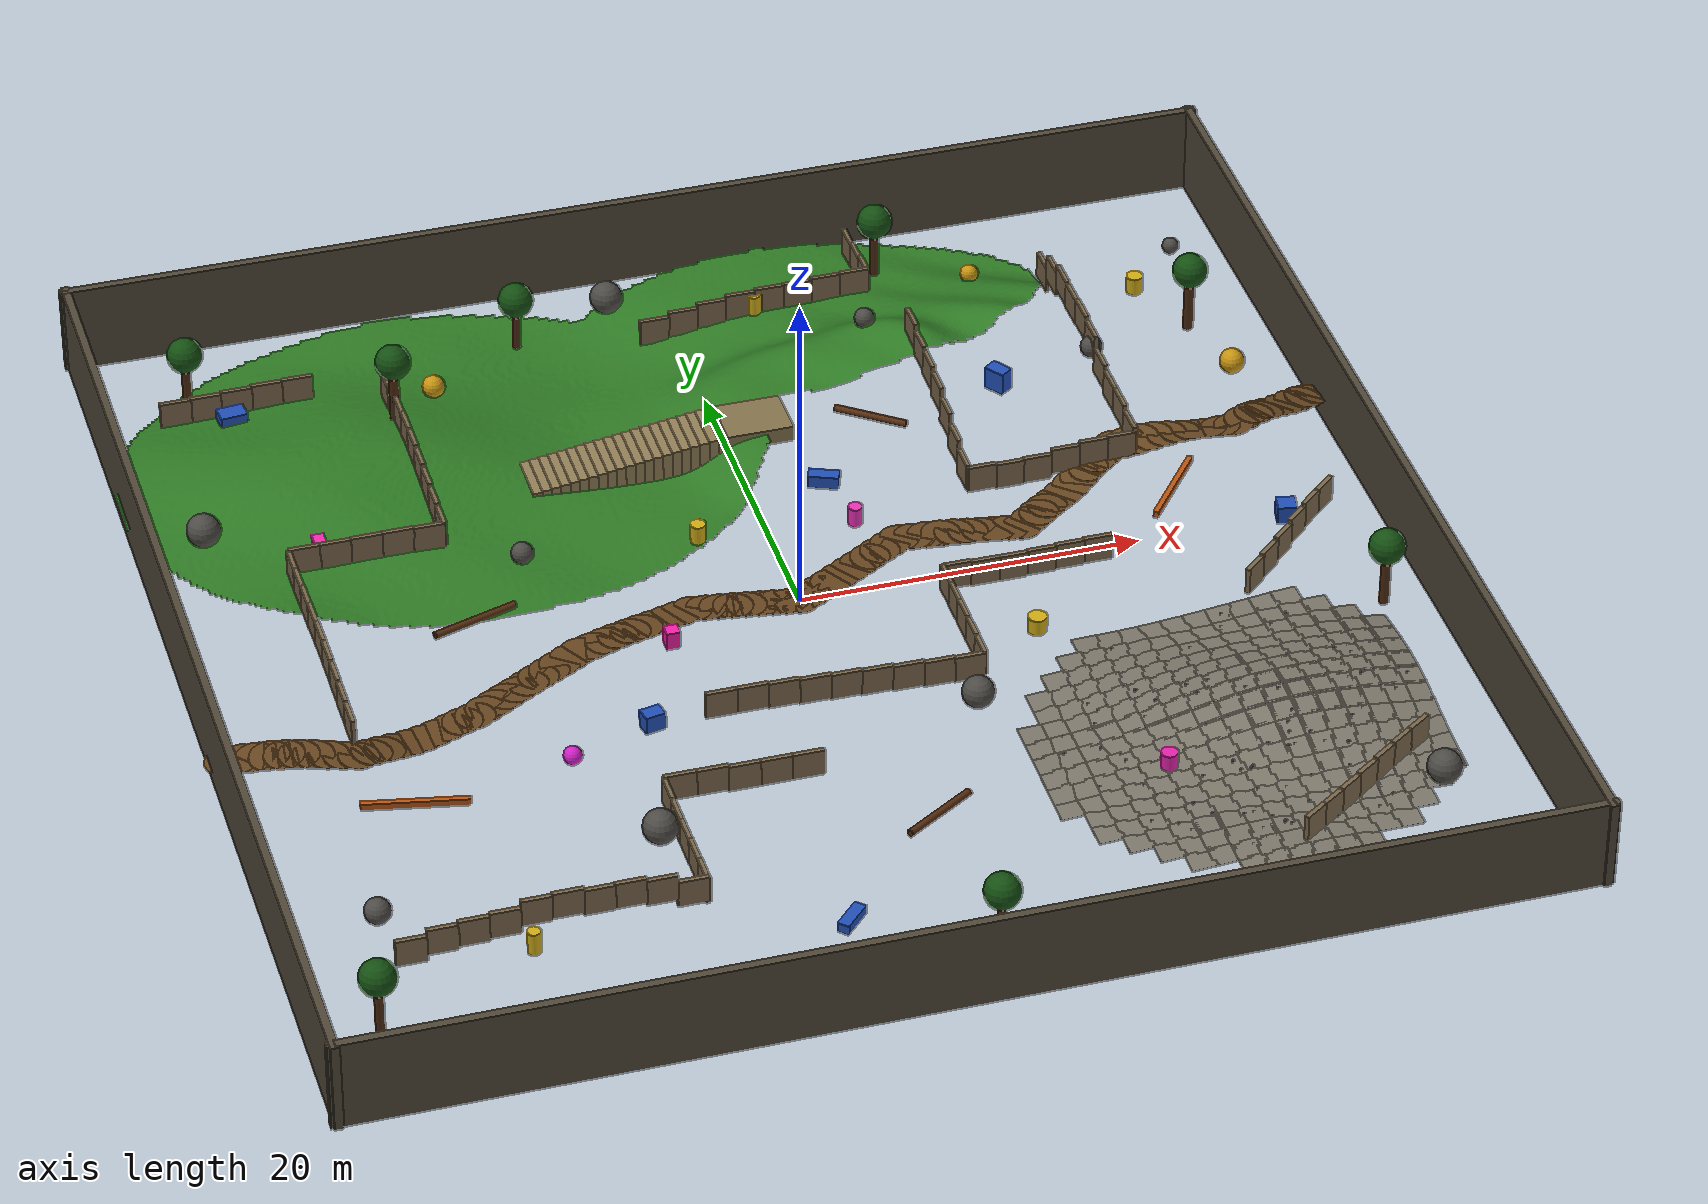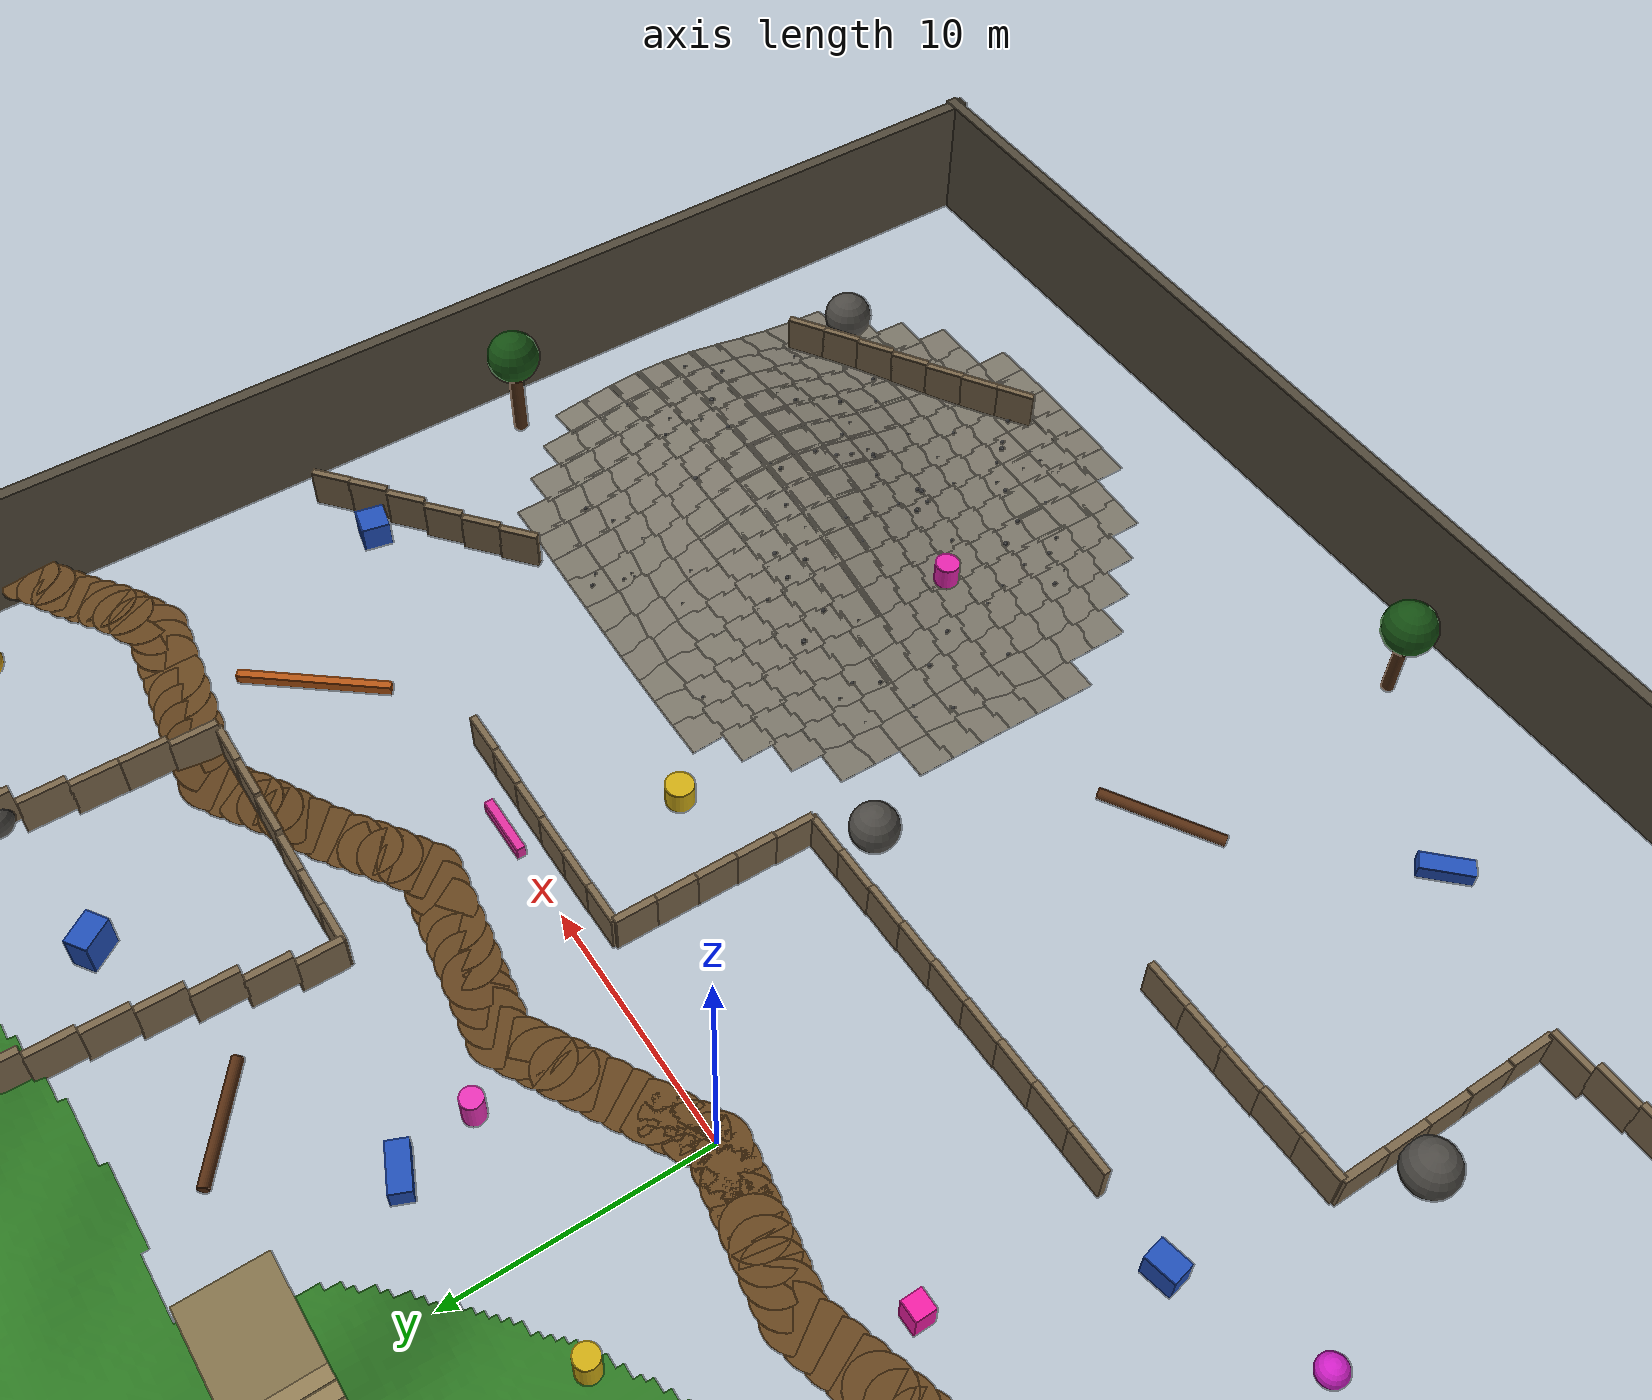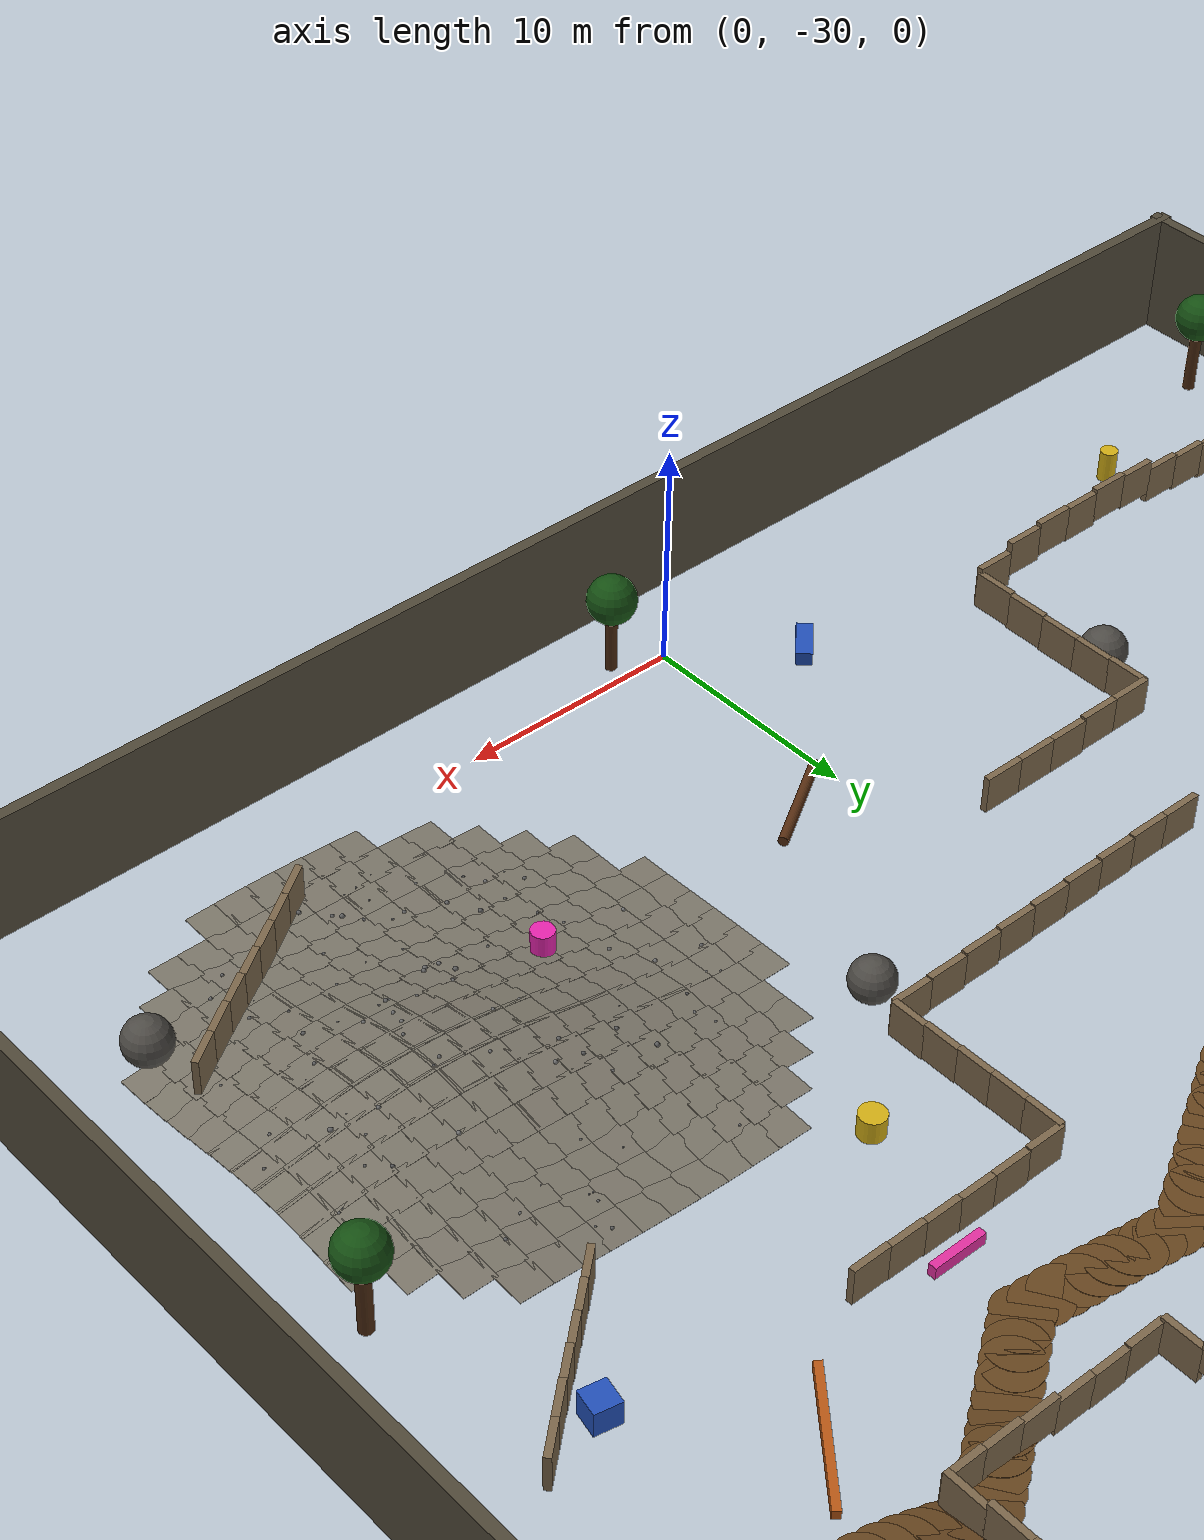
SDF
<sdf version="1.8">
 <world name="semantic_segmentation_world">
  <plugin filename="ignition-gazebo-physics-system" name="ignition::gazebo::systems::Physics"/>
  <plugin filename="ignition-gazebo-user-commands-system" name="ignition::gazebo::systems::UserCommands"/>
  <plugin filename="ignition-gazebo-scene-broadcaster-system" name="ignition::gazebo::systems::SceneBroadcaster"/>
  <plugin filename="ignition-gazebo-sensors-system" name="ignition::gazebo::systems::Sensors">
   <render_engine>ogre2</render_engine>
  </plugin>
  <plugin filename="ignition-gazebo-imu-system" name="ignition::gazebo::systems::Imu"/>
  <physics name="1ms" type="ignored">
   <max_step_size>0.001</max_step_size>
   <real_time_factor>1.0</real_time_factor>
   <gravity>0 0 -9.8</gravity>
  </physics>
  <scene>
   <ambient>0.43 0.45 0.40 1</ambient>
   <background>0.60 0.73 0.86 1</background>
   <shadows>true</shadows>
  </scene>
  <light type="directional" name="sun">
   <pose>0.000000 0.000000 35.000000 0.000000 0.000000 0.000000</pose>
   <diffuse>0.88 0.84 0.74 1</diffuse>
   <specular>0.18 0.18 0.16 1</specular>
   <attenuation>
    <range>1000</range>
    <constant>0.9</constant>
    <linear>0.01</linear>
    <quadratic>0.001</quadratic>
   </attenuation>
   <direction>-0.45 0.25 -0.86</direction>
  </light>
  <model name="bare_earth_sloped_terrain_collision">
   <static>true</static>
   <pose>0.000000 0.000000 -1.000000 0.000000 0.000000 0.000000</pose>
   <link name="terrain_collision_link">
    <collision name="terrain_collision">
     <geometry>
      <heightmap>
       <uri>file://complex_terrain_heightmap.png</uri>
       <size>70.0 70.0 4.431373</size>
       <pos>0 0 0</pos>
      </heightmap>
     </geometry>
     <surface><friction><ode><mu>1.15</mu><mu2>1.15</mu2></ode></friction></surface>
    </collision>
   </link>
  </model>
  <model name="grass_terrain">
   <static>true</static>
   <link name="grass_terrain_link">
    <visual name="height_conforming_grass_visual">
     <geometry><mesh><uri>file://complex_grass_surface.obj</uri><scale>1 1 1</scale></mesh></geometry>
     <material>
      <ambient>0.18 0.48 0.14 1</ambient>
      <diffuse>0.18 0.48 0.14 1</diffuse>
      <specular>0.02 0.02 0.02 1</specular>
      <pbr>
       <metal>
        <albedo_map>file://complex_grass_texture.png</albedo_map>
        <roughness>0.92</roughness>
        <metalness>0.0</metalness>
       </metal>
      </pbr>
     </material>
    </visual>
   </link>
   <plugin filename="ignition-gazebo-label-system" name="ignition::gazebo::systems::Label">
    <label>2</label>
   </plugin>
  </model>
  <model name="gravel_terrain">
   <static>true</static>
   <link name="gravel_terrain_link">
    <visual name="gravel_tile_0_visual">
     <pose>9.000000 -21.200000 -0.456754 0.019390 -0.057664 0.000000</pose>
     <geometry><box><size>1.48 1.48 0.018</size></box></geometry>
     <material>
      <ambient>0.48 0.46 0.41 1.0</ambient>
      <diffuse>0.48 0.46 0.41 1.0</diffuse>
      <specular>0.04 0.04 0.04 1</specular>
     </material>
    </visual>
    <visual name="gravel_tile_1_visual">
     <pose>9.000000 -19.900000 -0.421943 0.031874 -0.057185 0.000000</pose>
     <geometry><box><size>1.48 1.48 0.018</size></box></geometry>
     <material>
      <ambient>0.48 0.46 0.41 1.0</ambient>
      <diffuse>0.48 0.46 0.41 1.0</diffuse>
      <specular>0.04 0.04 0.04 1</specular>
     </material>
    </visual>
    <visual name="gravel_tile_2_visual">
     <pose>9.000000 -18.600000 -0.379497 0.031471 -0.048208 0.000000</pose>
     <geometry><box><size>1.48 1.48 0.018</size></box></geometry>
     <material>
      <ambient>0.48 0.46 0.41 1.0</ambient>
      <diffuse>0.48 0.46 0.41 1.0</diffuse>
      <specular>0.04 0.04 0.04 1</specular>
     </material>
    </visual>
    <visual name="gravel_tile_3_visual">
     <pose>9.000000 -17.300000 -0.343825 0.022530 -0.035148 0.000000</pose>
     <geometry><box><size>1.48 1.48 0.018</size></box></geometry>
     <material>
      <ambient>0.48 0.46 0.41 1.0</ambient>
      <diffuse>0.48 0.46 0.41 1.0</diffuse>
      <specular>0.04 0.04 0.04 1</specular>
     </material>
    </visual>
    <visual name="gravel_tile_4_visual">
     <pose>9.000000 -16.000000 -0.321455 0.012302 -0.023243 0.000000</pose>
     <geometry><box><size>1.48 1.48 0.018</size></box></geometry>
     <material>
      <ambient>0.48 0.46 0.41 1.0</ambient>
      <diffuse>0.48 0.46 0.41 1.0</diffuse>
      <specular>0.04 0.04 0.04 1</specular>
     </material>
    </visual>
    <visual name="gravel_tile_5_visual">
     <pose>9.000000 -14.700000 -0.309470 0.007421 -0.016599 0.000000</pose>
     <geometry><box><size>1.48 1.48 0.018</size></box></geometry>
     <material>
      <ambient>0.48 0.46 0.41 1.0</ambient>
      <diffuse>0.48 0.46 0.41 1.0</diffuse>
      <specular>0.04 0.04 0.04 1</specular>
     </material>
    </visual>
    <visual name="gravel_tile_6_visual">
     <pose>10.300000 -23.800000 -0.376295 -0.015465 -0.067314 0.000000</pose>
     <geometry><box><size>1.48 1.48 0.018</size></box></geometry>
     <material>
      <ambient>0.48 0.46 0.41 1.0</ambient>
      <diffuse>0.48 0.46 0.41 1.0</diffuse>
      <specular>0.04 0.04 0.04 1</specular>
     </material>
    </visual>
    <visual name="gravel_tile_7_visual">
     <pose>10.300000 -22.500000 -0.380933 0.007405 -0.082023 0.000000</pose>
     <geometry><box><size>1.48 1.48 0.018</size></box></geometry>
     <material>
      <ambient>0.48 0.46 0.41 1.0</ambient>
      <diffuse>0.48 0.46 0.41 1.0</diffuse>
      <specular>0.04 0.04 0.04 1</specular>
     </material>
    </visual>
    <visual name="gravel_tile_8_visual">
     <pose>10.300000 -21.200000 -0.360473 0.022422 -0.087957 0.000000</pose>
     <geometry><box><size>1.48 1.48 0.018</size></box></geometry>
     <material>
      <ambient>0.48 0.46 0.41 1.0</ambient>
      <diffuse>0.48 0.46 0.41 1.0</diffuse>
      <specular>0.04 0.04 0.04 1</specular>
     </material>
    </visual>
    <visual name="gravel_tile_9_visual">
     <pose>10.300000 -19.900000 -0.327196 0.026992 -0.087020 0.000000</pose>
     <geometry><box><size>1.48 1.48 0.018</size></box></geometry>
     <material>
      <ambient>0.48 0.46 0.41 1.0</ambient>
      <diffuse>0.48 0.46 0.41 1.0</diffuse>
      <specular>0.04 0.04 0.04 1</specular>
     </material>
    </visual>
    <visual name="gravel_tile_10_visual">
     <pose>10.300000 -18.600000 -0.294280 0.022424 -0.082554 0.000000</pose>
     <geometry><box><size>1.48 1.48 0.018</size></box></geometry>
     <material>
      <ambient>0.48 0.46 0.41 1.0</ambient>
      <diffuse>0.48 0.46 0.41 1.0</diffuse>
      <specular>0.04 0.04 0.04 1</specular>
     </material>
    </visual>
    <visual name="gravel_tile_11_visual">
     <pose>10.300000 -17.300000 -0.270755 0.013574 -0.077901 0.000000</pose>
     <geometry><box><size>1.48 1.48 0.018</size></box></geometry>
     <material>
      <ambient>0.48 0.46 0.41 1.0</ambient>
      <diffuse>0.48 0.46 0.41 1.0</diffuse>
      <specular>0.04 0.04 0.04 1</specular>
     </material>
    </visual>
    <visual name="gravel_tile_12_visual">
     <pose>10.300000 -16.000000 -0.258104 0.006695 -0.075205 0.000000</pose>
     <geometry><box><size>1.48 1.48 0.018</size></box></geometry>
     <material>
      <ambient>0.48 0.46 0.41 1.0</ambient>
      <diffuse>0.48 0.46 0.41 1.0</diffuse>
      <specular>0.04 0.04 0.04 1</specular>
     </material>
    </visual>
    <visual name="gravel_tile_13_visual">
     <pose>10.300000 -14.700000 -0.250535 0.006177 -0.074684 0.000000</pose>
     <geometry><box><size>1.48 1.48 0.018</size></box></geometry>
     <material>
      <ambient>0.48 0.46 0.41 1.0</ambient>
      <diffuse>0.48 0.46 0.41 1.0</diffuse>
      <specular>0.04 0.04 0.04 1</specular>
     </material>
    </visual>
    <visual name="gravel_tile_14_visual">
     <pose>10.300000 -13.400000 -0.239168 0.012172 -0.074581 0.000000</pose>
     <geometry><box><size>1.48 1.48 0.018</size></box></geometry>
     <material>
      <ambient>0.48 0.46 0.41 1.0</ambient>
      <diffuse>0.48 0.46 0.41 1.0</diffuse>
      <specular>0.04 0.04 0.04 1</specular>
     </material>
    </visual>
    <visual name="gravel_tile_15_visual">
     <pose>10.300000 -12.100000 -0.217735 0.020776 -0.071888 0.000000</pose>
     <geometry><box><size>1.48 1.48 0.018</size></box></geometry>
     <material>
      <ambient>0.48 0.46 0.41 1.0</ambient>
      <diffuse>0.48 0.46 0.41 1.0</diffuse>
      <specular>0.04 0.04 0.04 1</specular>
     </material>
    </visual>
    <visual name="gravel_tile_16_visual">
     <pose>11.600000 -25.100000 -0.260787 -0.017333 -0.074096 0.000000</pose>
     <geometry><box><size>1.48 1.48 0.018</size></box></geometry>
     <material>
      <ambient>0.48 0.46 0.41 1.0</ambient>
      <diffuse>0.48 0.46 0.41 1.0</diffuse>
      <specular>0.04 0.04 0.04 1</specular>
     </material>
    </visual>
    <visual name="gravel_tile_17_visual">
     <pose>11.600000 -23.800000 -0.271597 0.000529 -0.090328 0.000000</pose>
     <geometry><box><size>1.48 1.48 0.018</size></box></geometry>
     <material>
      <ambient>0.48 0.46 0.41 1.0</ambient>
      <diffuse>0.48 0.46 0.41 1.0</diffuse>
      <specular>0.04 0.04 0.04 1</specular>
     </material>
    </visual>
    <visual name="gravel_tile_18_visual">
     <pose>11.600000 -22.500000 -0.260596 0.015666 -0.099692 0.000000</pose>
     <geometry><box><size>1.48 1.48 0.018</size></box></geometry>
     <material>
      <ambient>0.48 0.46 0.41 1.0</ambient>
      <diffuse>0.48 0.46 0.41 1.0</diffuse>
      <specular>0.04 0.04 0.04 1</specular>
     </material>
    </visual>
    <visual name="gravel_tile_19_visual">
     <pose>11.600000 -21.200000 -0.233311 0.025168 -0.104952 0.000000</pose>
     <geometry><box><size>1.48 1.48 0.018</size></box></geometry>
     <material>
      <ambient>0.48 0.46 0.41 1.0</ambient>
      <diffuse>0.48 0.46 0.41 1.0</diffuse>
      <specular>0.04 0.04 0.04 1</specular>
     </material>
    </visual>
    <visual name="gravel_tile_20_visual">
     <pose>11.600000 -19.900000 -0.198310 0.027424 -0.109534 0.000000</pose>
     <geometry><box><size>1.48 1.48 0.018</size></box></geometry>
     <material>
      <ambient>0.48 0.46 0.41 1.0</ambient>
      <diffuse>0.48 0.46 0.41 1.0</diffuse>
      <specular>0.04 0.04 0.04 1</specular>
     </material>
    </visual>
    <visual name="gravel_tile_21_visual">
     <pose>11.600000 -18.600000 -0.164880 0.023087 -0.115585 0.000000</pose>
     <geometry><box><size>1.48 1.48 0.018</size></box></geometry>
     <material>
      <ambient>0.48 0.46 0.41 1.0</ambient>
      <diffuse>0.48 0.46 0.41 1.0</diffuse>
      <specular>0.04 0.04 0.04 1</specular>
     </material>
    </visual>
    <visual name="gravel_tile_22_visual">
     <pose>11.600000 -17.300000 -0.139757 0.015357 -0.122914 0.000000</pose>
     <geometry><box><size>1.48 1.48 0.018</size></box></geometry>
     <material>
      <ambient>0.48 0.46 0.41 1.0</ambient>
      <diffuse>0.48 0.46 0.41 1.0</diffuse>
      <specular>0.04 0.04 0.04 1</specular>
     </material>
    </visual>
    <visual name="gravel_tile_23_visual">
     <pose>11.600000 -16.000000 -0.124489 0.008639 -0.129189 0.000000</pose>
     <geometry><box><size>1.48 1.48 0.018</size></box></geometry>
     <material>
      <ambient>0.48 0.46 0.41 1.0</ambient>
      <diffuse>0.48 0.46 0.41 1.0</diffuse>
      <specular>0.04 0.04 0.04 1</specular>
     </material>
    </visual>
    <visual name="gravel_tile_24_visual">
     <pose>11.600000 -14.700000 -0.115496 0.005965 -0.131029 0.000000</pose>
     <geometry><box><size>1.48 1.48 0.018</size></box></geometry>
     <material>
      <ambient>0.48 0.46 0.41 1.0</ambient>
      <diffuse>0.48 0.46 0.41 1.0</diffuse>
      <specular>0.04 0.04 0.04 1</specular>
     </material>
    </visual>
    <visual name="gravel_tile_25_visual">
     <pose>11.600000 -13.400000 -0.107314 0.007035 -0.125369 0.000000</pose>
     <geometry><box><size>1.48 1.48 0.018</size></box></geometry>
     <material>
      <ambient>0.48 0.46 0.41 1.0</ambient>
      <diffuse>0.48 0.46 0.41 1.0</diffuse>
      <specular>0.04 0.04 0.04 1</specular>
     </material>
    </visual>
    <visual name="gravel_tile_26_visual">
     <pose>11.600000 -12.100000 -0.097050 0.008429 -0.110410 0.000000</pose>
     <geometry><box><size>1.48 1.48 0.018</size></box></geometry>
     <material>
      <ambient>0.48 0.46 0.41 1.0</ambient>
      <diffuse>0.48 0.46 0.41 1.0</diffuse>
      <specular>0.04 0.04 0.04 1</specular>
     </material>
    </visual>
    <visual name="gravel_tile_27_visual">
     <pose>11.600000 -10.800000 -0.087156 0.005826 -0.086043 0.000000</pose>
     <geometry><box><size>1.48 1.48 0.018</size></box></geometry>
     <material>
      <ambient>0.48 0.46 0.41 1.0</ambient>
      <diffuse>0.48 0.46 0.41 1.0</diffuse>
      <specular>0.04 0.04 0.04 1</specular>
     </material>
    </visual>
    <visual name="gravel_tile_28_visual">
     <pose>12.900000 -26.400000 -0.145047 -0.011866 -0.072507 0.000000</pose>
     <geometry><box><size>1.48 1.48 0.018</size></box></geometry>
     <material>
      <ambient>0.48 0.46 0.41 1.0</ambient>
      <diffuse>0.48 0.46 0.41 1.0</diffuse>
      <specular>0.04 0.04 0.04 1</specular>
     </material>
    </visual>
    <visual name="gravel_tile_29_visual">
     <pose>12.900000 -25.100000 -0.154011 -0.001663 -0.086835 0.000000</pose>
     <geometry><box><size>1.48 1.48 0.018</size></box></geometry>
     <material>
      <ambient>0.48 0.46 0.41 1.0</ambient>
      <diffuse>0.48 0.46 0.41 1.0</diffuse>
      <specular>0.04 0.04 0.04 1</specular>
     </material>
    </visual>
    <visual name="gravel_tile_30_visual">
     <pose>12.900000 -23.800000 -0.148716 0.010037 -0.095344 0.000000</pose>
     <geometry><box><size>1.48 1.48 0.018</size></box></geometry>
     <material>
      <ambient>0.48 0.46 0.41 1.0</ambient>
      <diffuse>0.48 0.46 0.41 1.0</diffuse>
      <specular>0.04 0.04 0.04 1</specular>
     </material>
    </visual>
    <visual name="gravel_tile_31_visual">
     <pose>12.900000 -22.500000 -0.127569 0.022472 -0.102155 0.000000</pose>
     <geometry><box><size>1.48 1.48 0.018</size></box></geometry>
     <material>
      <ambient>0.48 0.46 0.41 1.0</ambient>
      <diffuse>0.48 0.46 0.41 1.0</diffuse>
      <specular>0.04 0.04 0.04 1</specular>
     </material>
    </visual>
    <visual name="gravel_tile_32_visual">
     <pose>12.900000 -21.200000 -0.090965 0.033267 -0.111996 0.000000</pose>
     <geometry><box><size>1.48 1.48 0.018</size></box></geometry>
     <material>
      <ambient>0.48 0.46 0.41 1.0</ambient>
      <diffuse>0.48 0.46 0.41 1.0</diffuse>
      <specular>0.04 0.04 0.04 1</specular>
     </material>
    </visual>
    <visual name="gravel_tile_33_visual">
     <pose>12.900000 -19.900000 -0.043270 0.038934 -0.127386 0.000000</pose>
     <geometry><box><size>1.48 1.48 0.018</size></box></geometry>
     <material>
      <ambient>0.48 0.46 0.41 1.0</ambient>
      <diffuse>0.48 0.46 0.41 1.0</diffuse>
      <specular>0.04 0.04 0.04 1</specular>
     </material>
    </visual>
    <visual name="gravel_tile_34_visual">
     <pose>12.900000 -18.600000 0.006951 0.036929 -0.146901 0.000000</pose>
     <geometry><box><size>1.48 1.48 0.018</size></box></geometry>
     <material>
      <ambient>0.48 0.46 0.41 1.0</ambient>
      <diffuse>0.48 0.46 0.41 1.0</diffuse>
      <specular>0.04 0.04 0.04 1</specular>
     </material>
    </visual>
    <visual name="gravel_tile_35_visual">
     <pose>12.900000 -17.300000 0.049595 0.027642 -0.165509 0.000000</pose>
     <geometry><box><size>1.48 1.48 0.018</size></box></geometry>
     <material>
      <ambient>0.48 0.46 0.41 1.0</ambient>
      <diffuse>0.48 0.46 0.41 1.0</diffuse>
      <specular>0.04 0.04 0.04 1</specular>
     </material>
    </visual>
    <visual name="gravel_tile_36_visual">
     <pose>12.900000 -16.000000 0.077123 0.014400 -0.176755 0.000000</pose>
     <geometry><box><size>1.48 1.48 0.018</size></box></geometry>
     <material>
      <ambient>0.48 0.46 0.41 1.0</ambient>
      <diffuse>0.48 0.46 0.41 1.0</diffuse>
      <specular>0.04 0.04 0.04 1</specular>
     </material>
    </visual>
    <visual name="gravel_tile_37_visual">
     <pose>12.900000 -14.700000 0.087107 0.001238 -0.175459 0.000000</pose>
     <geometry><box><size>1.48 1.48 0.018</size></box></geometry>
     <material>
      <ambient>0.48 0.46 0.41 1.0</ambient>
      <diffuse>0.48 0.46 0.41 1.0</diffuse>
      <specular>0.04 0.04 0.04 1</specular>
     </material>
    </visual>
    <visual name="gravel_tile_38_visual">
     <pose>12.900000 -13.400000 0.081312 -0.009785 -0.159484 0.000000</pose>
     <geometry><box><size>1.48 1.48 0.018</size></box></geometry>
     <material>
      <ambient>0.48 0.46 0.41 1.0</ambient>
      <diffuse>0.48 0.46 0.41 1.0</diffuse>
      <specular>0.04 0.04 0.04 1</specular>
     </material>
    </visual>
    <visual name="gravel_tile_39_visual">
     <pose>12.900000 -12.100000 0.062259 -0.019473 -0.130114 0.000000</pose>
     <geometry><box><size>1.48 1.48 0.018</size></box></geometry>
     <material>
      <ambient>0.48 0.46 0.41 1.0</ambient>
      <diffuse>0.48 0.46 0.41 1.0</diffuse>
      <specular>0.04 0.04 0.04 1</specular>
     </material>
    </visual>
    <visual name="gravel_tile_40_visual">
     <pose>12.900000 -10.800000 0.030431 -0.029630 -0.091769 0.000000</pose>
     <geometry><box><size>1.48 1.48 0.018</size></box></geometry>
     <material>
      <ambient>0.48 0.46 0.41 1.0</ambient>
      <diffuse>0.48 0.46 0.41 1.0</diffuse>
      <specular>0.04 0.04 0.04 1</specular>
     </material>
    </visual>
    <visual name="gravel_tile_41_visual">
     <pose>12.900000 -9.500000 -0.014758 -0.039514 -0.051760 0.000000</pose>
     <geometry><box><size>1.48 1.48 0.018</size></box></geometry>
     <material>
      <ambient>0.48 0.46 0.41 1.0</ambient>
      <diffuse>0.48 0.46 0.41 1.0</diffuse>
      <specular>0.04 0.04 0.04 1</specular>
     </material>
    </visual>
    <visual name="gravel_tile_42_visual">
     <pose>14.200000 -27.700000 -0.044507 -0.000744 -0.068547 0.000000</pose>
     <geometry><box><size>1.48 1.48 0.018</size></box></geometry>
     <material>
      <ambient>0.48 0.46 0.41 1.0</ambient>
      <diffuse>0.48 0.46 0.41 1.0</diffuse>
      <specular>0.04 0.04 0.04 1</specular>
     </material>
    </visual>
    <visual name="gravel_tile_43_visual">
     <pose>14.200000 -26.400000 -0.044740 0.000591 -0.078880 0.000000</pose>
     <geometry><box><size>1.48 1.48 0.018</size></box></geometry>
     <material>
      <ambient>0.48 0.46 0.41 1.0</ambient>
      <diffuse>0.48 0.46 0.41 1.0</diffuse>
      <specular>0.04 0.04 0.04 1</specular>
     </material>
    </visual>
    <visual name="gravel_tile_44_visual">
     <pose>14.200000 -25.100000 -0.041638 0.005019 -0.083210 0.000000</pose>
     <geometry><box><size>1.48 1.48 0.018</size></box></geometry>
     <material>
      <ambient>0.48 0.46 0.41 1.0</ambient>
      <diffuse>0.48 0.46 0.41 1.0</diffuse>
      <specular>0.04 0.04 0.04 1</specular>
     </material>
    </visual>
    <visual name="gravel_tile_45_visual">
     <pose>14.200000 -23.800000 -0.028921 0.015752 -0.086773 0.000000</pose>
     <geometry><box><size>1.48 1.48 0.018</size></box></geometry>
     <material>
      <ambient>0.48 0.46 0.41 1.0</ambient>
      <diffuse>0.48 0.46 0.41 1.0</diffuse>
      <specular>0.04 0.04 0.04 1</specular>
     </material>
    </visual>
    <visual name="gravel_tile_46_visual">
     <pose>14.200000 -22.500000 0.002177 0.032915 -0.096046 0.000000</pose>
     <geometry><box><size>1.48 1.48 0.018</size></box></geometry>
     <material>
      <ambient>0.48 0.46 0.41 1.0</ambient>
      <diffuse>0.48 0.46 0.41 1.0</diffuse>
      <specular>0.04 0.04 0.04 1</specular>
     </material>
    </visual>
    <visual name="gravel_tile_47_visual">
     <pose>14.200000 -21.200000 0.057495 0.051792 -0.115323 0.000000</pose>
     <geometry><box><size>1.48 1.48 0.018</size></box></geometry>
     <material>
      <ambient>0.48 0.46 0.41 1.0</ambient>
      <diffuse>0.48 0.46 0.41 1.0</diffuse>
      <specular>0.04 0.04 0.04 1</specular>
     </material>
    </visual>
    <visual name="gravel_tile_48_visual">
     <pose>14.200000 -19.900000 0.134179 0.064256 -0.143899 0.000000</pose>
     <geometry><box><size>1.48 1.48 0.018</size></box></geometry>
     <material>
      <ambient>0.48 0.46 0.41 1.0</ambient>
      <diffuse>0.48 0.46 0.41 1.0</diffuse>
      <specular>0.04 0.04 0.04 1</specular>
     </material>
    </visual>
    <visual name="gravel_tile_49_visual">
     <pose>14.200000 -18.600000 0.218799 0.063081 -0.175534 0.000000</pose>
     <geometry><box><size>1.48 1.48 0.018</size></box></geometry>
     <material>
      <ambient>0.48 0.46 0.41 1.0</ambient>
      <diffuse>0.48 0.46 0.41 1.0</diffuse>
      <specular>0.04 0.04 0.04 1</specular>
     </material>
    </visual>
    <visual name="gravel_tile_50_visual">
     <pose>14.200000 -17.300000 0.291525 0.046250 -0.200798 0.000000</pose>
     <geometry><box><size>1.48 1.48 0.018</size></box></geometry>
     <material>
      <ambient>0.48 0.46 0.41 1.0</ambient>
      <diffuse>0.48 0.46 0.41 1.0</diffuse>
      <specular>0.04 0.04 0.04 1</specular>
     </material>
    </visual>
    <visual name="gravel_tile_51_visual">
     <pose>14.200000 -16.000000 0.334231 0.018169 -0.211027 0.000000</pose>
     <geometry><box><size>1.48 1.48 0.018</size></box></geometry>
     <material>
      <ambient>0.48 0.46 0.41 1.0</ambient>
      <diffuse>0.48 0.46 0.41 1.0</diffuse>
      <specular>0.04 0.04 0.04 1</specular>
     </material>
    </visual>
    <visual name="gravel_tile_52_visual">
     <pose>14.200000 -14.700000 0.337419 -0.013117 -0.201579 0.000000</pose>
     <geometry><box><size>1.48 1.48 0.018</size></box></geometry>
     <material>
      <ambient>0.48 0.46 0.41 1.0</ambient>
      <diffuse>0.48 0.46 0.41 1.0</diffuse>
      <specular>0.04 0.04 0.04 1</specular>
     </material>
    </visual>
    <visual name="gravel_tile_53_visual">
     <pose>14.200000 -13.400000 0.301827 -0.040584 -0.173118 0.000000</pose>
     <geometry><box><size>1.48 1.48 0.018</size></box></geometry>
     <material>
      <ambient>0.48 0.46 0.41 1.0</ambient>
      <diffuse>0.48 0.46 0.41 1.0</diffuse>
      <specular>0.04 0.04 0.04 1</specular>
     </material>
    </visual>
    <visual name="gravel_tile_54_visual">
     <pose>14.200000 -12.100000 0.234956 -0.060896 -0.131270 0.000000</pose>
     <geometry><box><size>1.48 1.48 0.018</size></box></geometry>
     <material>
      <ambient>0.48 0.46 0.41 1.0</ambient>
      <diffuse>0.48 0.46 0.41 1.0</diffuse>
      <specular>0.04 0.04 0.04 1</specular>
     </material>
    </visual>
    <visual name="gravel_tile_55_visual">
     <pose>14.200000 -10.800000 0.146795 -0.073081 -0.085378 0.000000</pose>
     <geometry><box><size>1.48 1.48 0.018</size></box></geometry>
     <material>
      <ambient>0.48 0.46 0.41 1.0</ambient>
      <diffuse>0.48 0.46 0.41 1.0</diffuse>
      <specular>0.04 0.04 0.04 1</specular>
     </material>
    </visual>
    <visual name="gravel_tile_56_visual">
     <pose>14.200000 -9.500000 0.048755 -0.075673 -0.045921 0.000000</pose>
     <geometry><box><size>1.48 1.48 0.018</size></box></geometry>
     <material>
      <ambient>0.48 0.46 0.41 1.0</ambient>
      <diffuse>0.48 0.46 0.41 1.0</diffuse>
      <specular>0.04 0.04 0.04 1</specular>
     </material>
    </visual>
    <visual name="gravel_tile_57_visual">
     <pose>14.200000 -8.200000 -0.045402 -0.067033 -0.020074 0.000000</pose>
     <geometry><box><size>1.48 1.48 0.018</size></box></geometry>
     <material>
      <ambient>0.48 0.46 0.41 1.0</ambient>
      <diffuse>0.48 0.46 0.41 1.0</diffuse>
      <specular>0.04 0.04 0.04 1</specular>
     </material>
    </visual>
    <visual name="gravel_tile_58_visual">
     <pose>15.500000 -27.700000 0.048602 0.007354 -0.072082 0.000000</pose>
     <geometry><box><size>1.48 1.48 0.018</size></box></geometry>
     <material>
      <ambient>0.48 0.46 0.41 1.0</ambient>
      <diffuse>0.48 0.46 0.41 1.0</diffuse>
      <specular>0.04 0.04 0.04 1</specular>
     </material>
    </visual>
    <visual name="gravel_tile_59_visual">
     <pose>15.500000 -26.400000 0.054253 0.002189 -0.071082 0.000000</pose>
     <geometry><box><size>1.48 1.48 0.018</size></box></geometry>
     <material>
      <ambient>0.48 0.46 0.41 1.0</ambient>
      <diffuse>0.48 0.46 0.41 1.0</diffuse>
      <specular>0.04 0.04 0.04 1</specular>
     </material>
    </visual>
    <visual name="gravel_tile_60_visual">
     <pose>15.500000 -25.100000 0.058077 0.005710 -0.068704 0.000000</pose>
     <geometry><box><size>1.48 1.48 0.018</size></box></geometry>
     <material>
      <ambient>0.48 0.46 0.41 1.0</ambient>
      <diffuse>0.48 0.46 0.41 1.0</diffuse>
      <specular>0.04 0.04 0.04 1</specular>
     </material>
    </visual>
    <visual name="gravel_tile_61_visual">
     <pose>15.500000 -23.800000 0.075068 0.022823 -0.072667 0.000000</pose>
     <geometry><box><size>1.48 1.48 0.018</size></box></geometry>
     <material>
      <ambient>0.48 0.46 0.41 1.0</ambient>
      <diffuse>0.48 0.46 0.41 1.0</diffuse>
      <specular>0.04 0.04 0.04 1</specular>
     </material>
    </visual>
    <visual name="gravel_tile_62_visual">
     <pose>15.500000 -22.500000 0.122703 0.051826 -0.089331 0.000000</pose>
     <geometry><box><size>1.48 1.48 0.018</size></box></geometry>
     <material>
      <ambient>0.48 0.46 0.41 1.0</ambient>
      <diffuse>0.48 0.46 0.41 1.0</diffuse>
      <specular>0.04 0.04 0.04 1</specular>
     </material>
    </visual>
    <visual name="gravel_tile_63_visual">
     <pose>15.500000 -21.200000 0.210959 0.082919 -0.120213 0.000000</pose>
     <geometry><box><size>1.48 1.48 0.018</size></box></geometry>
     <material>
      <ambient>0.48 0.46 0.41 1.0</ambient>
      <diffuse>0.48 0.46 0.41 1.0</diffuse>
      <specular>0.04 0.04 0.04 1</specular>
     </material>
    </visual>
    <visual name="gravel_tile_64_visual">
     <pose>15.500000 -19.900000 0.333455 0.101726 -0.160161 0.000000</pose>
     <geometry><box><size>1.48 1.48 0.018</size></box></geometry>
     <material>
      <ambient>0.48 0.46 0.41 1.0</ambient>
      <diffuse>0.48 0.46 0.41 1.0</diffuse>
      <specular>0.04 0.04 0.04 1</specular>
     </material>
    </visual>
    <visual name="gravel_tile_65_visual">
     <pose>15.500000 -18.600000 0.465760 0.096524 -0.198629 0.000000</pose>
     <geometry><box><size>1.48 1.48 0.018</size></box></geometry>
     <material>
      <ambient>0.48 0.46 0.41 1.0</ambient>
      <diffuse>0.48 0.46 0.41 1.0</diffuse>
      <specular>0.04 0.04 0.04 1</specular>
     </material>
    </visual>
    <visual name="gravel_tile_66_visual">
     <pose>15.500000 -17.300000 0.573451 0.064669 -0.223842 0.000000</pose>
     <geometry><box><size>1.48 1.48 0.018</size></box></geometry>
     <material>
      <ambient>0.48 0.46 0.41 1.0</ambient>
      <diffuse>0.48 0.46 0.41 1.0</diffuse>
      <specular>0.04 0.04 0.04 1</specular>
     </material>
    </visual>
    <visual name="gravel_tile_67_visual">
     <pose>15.500000 -16.000000 0.626120 0.014352 -0.227452 0.000000</pose>
     <geometry><box><size>1.48 1.48 0.018</size></box></geometry>
     <material>
      <ambient>0.48 0.46 0.41 1.0</ambient>
      <diffuse>0.48 0.46 0.41 1.0</diffuse>
      <specular>0.04 0.04 0.04 1</specular>
     </material>
    </visual>
    <visual name="gravel_tile_68_visual">
     <pose>15.500000 -14.700000 0.609257 -0.039587 -0.207311 0.000000</pose>
     <geometry><box><size>1.48 1.48 0.018</size></box></geometry>
     <material>
      <ambient>0.48 0.46 0.41 1.0</ambient>
      <diffuse>0.48 0.46 0.41 1.0</diffuse>
      <specular>0.04 0.04 0.04 1</specular>
     </material>
    </visual>
    <visual name="gravel_tile_69_visual">
     <pose>15.500000 -13.400000 0.527579 -0.083313 -0.168008 0.000000</pose>
     <geometry><box><size>1.48 1.48 0.018</size></box></geometry>
     <material>
      <ambient>0.48 0.46 0.41 1.0</ambient>
      <diffuse>0.48 0.46 0.41 1.0</diffuse>
      <specular>0.04 0.04 0.04 1</specular>
     </material>
    </visual>
    <visual name="gravel_tile_70_visual">
     <pose>15.500000 -12.100000 0.399905 -0.109184 -0.119666 0.000000</pose>
     <geometry><box><size>1.48 1.48 0.018</size></box></geometry>
     <material>
      <ambient>0.48 0.46 0.41 1.0</ambient>
      <diffuse>0.48 0.46 0.41 1.0</diffuse>
      <specular>0.04 0.04 0.04 1</specular>
     </material>
    </visual>
    <visual name="gravel_tile_71_visual">
     <pose>15.500000 -10.800000 0.251130 -0.115504 -0.074726 0.000000</pose>
     <geometry><box><size>1.48 1.48 0.018</size></box></geometry>
     <material>
      <ambient>0.48 0.46 0.41 1.0</ambient>
      <diffuse>0.48 0.46 0.41 1.0</diffuse>
      <specular>0.04 0.04 0.04 1</specular>
     </material>
    </visual>
    <visual name="gravel_tile_72_visual">
     <pose>15.500000 -9.500000 0.105951 -0.104316 -0.042823 0.000000</pose>
     <geometry><box><size>1.48 1.48 0.018</size></box></geometry>
     <material>
      <ambient>0.48 0.46 0.41 1.0</ambient>
      <diffuse>0.48 0.46 0.41 1.0</diffuse>
      <specular>0.04 0.04 0.04 1</specular>
     </material>
    </visual>
    <visual name="gravel_tile_73_visual">
     <pose>15.500000 -8.200000 -0.015563 -0.080459 -0.026872 0.000000</pose>
     <geometry><box><size>1.48 1.48 0.018</size></box></geometry>
     <material>
      <ambient>0.48 0.46 0.41 1.0</ambient>
      <diffuse>0.48 0.46 0.41 1.0</diffuse>
      <specular>0.04 0.04 0.04 1</specular>
     </material>
    </visual>
    <visual name="gravel_tile_74_visual">
     <pose>16.800000 -29.000000 0.123479 0.018135 -0.068248 0.000000</pose>
     <geometry><box><size>1.48 1.48 0.018</size></box></geometry>
     <material>
      <ambient>0.48 0.46 0.41 1.0</ambient>
      <diffuse>0.48 0.46 0.41 1.0</diffuse>
      <specular>0.04 0.04 0.04 1</specular>
     </material>
    </visual>
    <visual name="gravel_tile_75_visual">
     <pose>16.800000 -27.700000 0.137551 0.003813 -0.062649 0.000000</pose>
     <geometry><box><size>1.48 1.48 0.018</size></box></geometry>
     <material>
      <ambient>0.48 0.46 0.41 1.0</ambient>
      <diffuse>0.48 0.46 0.41 1.0</diffuse>
      <specular>0.04 0.04 0.04 1</specular>
     </material>
    </visual>
    <visual name="gravel_tile_76_visual">
     <pose>16.800000 -26.400000 0.136457 -0.003411 -0.054269 0.000000</pose>
     <geometry><box><size>1.48 1.48 0.018</size></box></geometry>
     <material>
      <ambient>0.48 0.46 0.41 1.0</ambient>
      <diffuse>0.48 0.46 0.41 1.0</diffuse>
      <specular>0.04 0.04 0.04 1</specular>
     </material>
    </visual>
    <visual name="gravel_tile_77_visual">
     <pose>16.800000 -25.100000 0.135987 0.006097 -0.051161 0.000000</pose>
     <geometry><box><size>1.48 1.48 0.018</size></box></geometry>
     <material>
      <ambient>0.48 0.46 0.41 1.0</ambient>
      <diffuse>0.48 0.46 0.41 1.0</diffuse>
      <specular>0.04 0.04 0.04 1</specular>
     </material>
    </visual>
    <visual name="gravel_tile_78_visual">
     <pose>16.800000 -23.800000 0.161446 0.036397 -0.060944 0.000000</pose>
     <geometry><box><size>1.48 1.48 0.018</size></box></geometry>
     <material>
      <ambient>0.48 0.46 0.41 1.0</ambient>
      <diffuse>0.48 0.46 0.41 1.0</diffuse>
      <specular>0.04 0.04 0.04 1</specular>
     </material>
    </visual>
    <visual name="gravel_tile_79_visual">
     <pose>16.800000 -22.500000 0.237221 0.081370 -0.087405 0.000000</pose>
     <geometry><box><size>1.48 1.48 0.018</size></box></geometry>
     <material>
      <ambient>0.48 0.46 0.41 1.0</ambient>
      <diffuse>0.48 0.46 0.41 1.0</diffuse>
      <specular>0.04 0.04 0.04 1</specular>
     </material>
    </visual>
    <visual name="gravel_tile_80_visual">
     <pose>16.800000 -21.200000 0.372901 0.124536 -0.127972 0.000000</pose>
     <geometry><box><size>1.48 1.48 0.018</size></box></geometry>
     <material>
      <ambient>0.48 0.46 0.41 1.0</ambient>
      <diffuse>0.48 0.46 0.41 1.0</diffuse>
      <specular>0.04 0.04 0.04 1</specular>
     </material>
    </visual>
    <visual name="gravel_tile_81_visual">
     <pose>16.800000 -19.900000 0.552995 0.145502 -0.173529 0.000000</pose>
     <geometry><box><size>1.48 1.48 0.018</size></box></geometry>
     <material>
      <ambient>0.48 0.46 0.41 1.0</ambient>
      <diffuse>0.48 0.46 0.41 1.0</diffuse>
      <specular>0.04 0.04 0.04 1</specular>
     </material>
    </visual>
    <visual name="gravel_tile_82_visual">
     <pose>16.800000 -18.600000 0.737564 0.129840 -0.211381 0.000000</pose>
     <geometry><box><size>1.48 1.48 0.018</size></box></geometry>
     <material>
      <ambient>0.48 0.46 0.41 1.0</ambient>
      <diffuse>0.48 0.46 0.41 1.0</diffuse>
      <specular>0.04 0.04 0.04 1</specular>
     </material>
    </visual>
    <visual name="gravel_tile_83_visual">
     <pose>16.800000 -17.300000 0.875879 0.076550 -0.230176 0.000000</pose>
     <geometry><box><size>1.48 1.48 0.018</size></box></geometry>
     <material>
      <ambient>0.48 0.46 0.41 1.0</ambient>
      <diffuse>0.48 0.46 0.41 1.0</diffuse>
      <specular>0.04 0.04 0.04 1</specular>
     </material>
    </visual>
    <visual name="gravel_tile_84_visual">
     <pose>16.800000 -16.000000 0.926973 -0.000074 -0.224032 0.000000</pose>
     <geometry><box><size>1.48 1.48 0.018</size></box></geometry>
     <material>
      <ambient>0.48 0.46 0.41 1.0</ambient>
      <diffuse>0.48 0.46 0.41 1.0</diffuse>
      <specular>0.04 0.04 0.04 1</specular>
     </material>
    </visual>
    <visual name="gravel_tile_85_visual">
     <pose>16.800000 -14.700000 0.875854 -0.076420 -0.194413 0.000000</pose>
     <geometry><box><size>1.48 1.48 0.018</size></box></geometry>
     <material>
      <ambient>0.48 0.46 0.41 1.0</ambient>
      <diffuse>0.48 0.46 0.41 1.0</diffuse>
      <specular>0.04 0.04 0.04 1</specular>
     </material>
    </visual>
    <visual name="gravel_tile_86_visual">
     <pose>16.800000 -13.400000 0.737015 -0.131538 -0.149851 0.000000</pose>
     <geometry><box><size>1.48 1.48 0.018</size></box></geometry>
     <material>
      <ambient>0.48 0.46 0.41 1.0</ambient>
      <diffuse>0.48 0.46 0.41 1.0</diffuse>
      <specular>0.04 0.04 0.04 1</specular>
     </material>
    </visual>
    <visual name="gravel_tile_87_visual">
     <pose>16.800000 -12.100000 0.545516 -0.155550 -0.103243 0.000000</pose>
     <geometry><box><size>1.48 1.48 0.018</size></box></geometry>
     <material>
      <ambient>0.48 0.46 0.41 1.0</ambient>
      <diffuse>0.48 0.46 0.41 1.0</diffuse>
      <specular>0.04 0.04 0.04 1</specular>
     </material>
    </visual>
    <visual name="gravel_tile_88_visual">
     <pose>16.800000 -10.800000 0.342574 -0.149712 -0.066553 0.000000</pose>
     <geometry><box><size>1.48 1.48 0.018</size></box></geometry>
     <material>
      <ambient>0.48 0.46 0.41 1.0</ambient>
      <diffuse>0.48 0.46 0.41 1.0</diffuse>
      <specular>0.04 0.04 0.04 1</specular>
     </material>
    </visual>
    <visual name="gravel_tile_89_visual">
     <pose>16.800000 -9.500000 0.162794 -0.122402 -0.045755 0.000000</pose>
     <geometry><box><size>1.48 1.48 0.018</size></box></geometry>
     <material>
      <ambient>0.48 0.46 0.41 1.0</ambient>
      <diffuse>0.48 0.46 0.41 1.0</diffuse>
      <specular>0.04 0.04 0.04 1</specular>
     </material>
    </visual>
    <visual name="gravel_tile_90_visual">
     <pose>16.800000 -8.200000 0.027471 -0.083850 -0.040534 0.000000</pose>
     <geometry><box><size>1.48 1.48 0.018</size></box></geometry>
     <material>
      <ambient>0.48 0.46 0.41 1.0</ambient>
      <diffuse>0.48 0.46 0.41 1.0</diffuse>
      <specular>0.04 0.04 0.04 1</specular>
     </material>
    </visual>
    <visual name="gravel_tile_91_visual">
     <pose>18.100000 -29.000000 0.206568 0.010744 -0.057454 0.000000</pose>
     <geometry><box><size>1.48 1.48 0.018</size></box></geometry>
     <material>
      <ambient>0.48 0.46 0.41 1.0</ambient>
      <diffuse>0.48 0.46 0.41 1.0</diffuse>
      <specular>0.04 0.04 0.04 1</specular>
     </material>
    </visual>
    <visual name="gravel_tile_92_visual">
     <pose>18.100000 -27.700000 0.207963 -0.007111 -0.044631 0.000000</pose>
     <geometry><box><size>1.48 1.48 0.018</size></box></geometry>
     <material>
      <ambient>0.48 0.46 0.41 1.0</ambient>
      <diffuse>0.48 0.46 0.41 1.0</diffuse>
      <specular>0.04 0.04 0.04 1</specular>
     </material>
    </visual>
    <visual name="gravel_tile_93_visual">
     <pose>18.100000 -26.400000 0.194627 -0.009896 -0.035396 0.000000</pose>
     <geometry><box><size>1.48 1.48 0.018</size></box></geometry>
     <material>
      <ambient>0.48 0.46 0.41 1.0</ambient>
      <diffuse>0.48 0.46 0.41 1.0</diffuse>
      <specular>0.04 0.04 0.04 1</specular>
     </material>
    </visual>
    <visual name="gravel_tile_94_visual">
     <pose>18.100000 -25.100000 0.192980 0.011911 -0.037557 0.000000</pose>
     <geometry><box><size>1.48 1.48 0.018</size></box></geometry>
     <material>
      <ambient>0.48 0.46 0.41 1.0</ambient>
      <diffuse>0.48 0.46 0.41 1.0</diffuse>
      <specular>0.04 0.04 0.04 1</specular>
     </material>
    </visual>
    <visual name="gravel_tile_95_visual">
     <pose>18.100000 -23.800000 0.236767 0.059080 -0.056069 0.000000</pose>
     <geometry><box><size>1.48 1.48 0.018</size></box></geometry>
     <material>
      <ambient>0.48 0.46 0.41 1.0</ambient>
      <diffuse>0.48 0.46 0.41 1.0</diffuse>
      <specular>0.04 0.04 0.04 1</specular>
     </material>
    </visual>
    <visual name="gravel_tile_96_visual">
     <pose>18.100000 -22.500000 0.352878 0.119564 -0.090691 0.000000</pose>
     <geometry><box><size>1.48 1.48 0.018</size></box></geometry>
     <material>
      <ambient>0.48 0.46 0.41 1.0</ambient>
      <diffuse>0.48 0.46 0.41 1.0</diffuse>
      <specular>0.04 0.04 0.04 1</specular>
     </material>
    </visual>
    <visual name="gravel_tile_97_visual">
     <pose>18.100000 -21.200000 0.545288 0.170460 -0.135087 0.000000</pose>
     <geometry><box><size>1.48 1.48 0.018</size></box></geometry>
     <material>
      <ambient>0.48 0.46 0.41 1.0</ambient>
      <diffuse>0.48 0.46 0.41 1.0</diffuse>
      <specular>0.04 0.04 0.04 1</specular>
     </material>
    </visual>
    <visual name="gravel_tile_98_visual">
     <pose>18.100000 -19.900000 0.785400 0.187456 -0.178271 0.000000</pose>
     <geometry><box><size>1.48 1.48 0.018</size></box></geometry>
     <material>
      <ambient>0.48 0.46 0.41 1.0</ambient>
      <diffuse>0.48 0.46 0.41 1.0</diffuse>
      <specular>0.04 0.04 0.04 1</specular>
     </material>
    </visual>
    <visual name="gravel_tile_99_visual">
     <pose>18.100000 -18.600000 1.016543 0.155882 -0.208344 0.000000</pose>
     <geometry><box><size>1.48 1.48 0.018</size></box></geometry>
     <material>
      <ambient>0.48 0.46 0.41 1.0</ambient>
      <diffuse>0.48 0.46 0.41 1.0</diffuse>
      <specular>0.04 0.04 0.04 1</specular>
     </material>
    </visual>
    <visual name="gravel_tile_100_visual">
     <pose>18.100000 -17.300000 1.173704 0.078134 -0.216807 0.000000</pose>
     <geometry><box><size>1.48 1.48 0.018</size></box></geometry>
     <material>
      <ambient>0.48 0.46 0.41 1.0</ambient>
      <diffuse>0.48 0.46 0.41 1.0</diffuse>
      <specular>0.04 0.04 0.04 1</specular>
     </material>
    </visual>
    <visual name="gravel_tile_101_visual">
     <pose>18.100000 -16.000000 1.209869 -0.023969 -0.201501 0.000000</pose>
     <geometry><box><size>1.48 1.48 0.018</size></box></geometry>
     <material>
      <ambient>0.48 0.46 0.41 1.0</ambient>
      <diffuse>0.48 0.46 0.41 1.0</diffuse>
      <specular>0.04 0.04 0.04 1</specular>
     </material>
    </visual>
    <visual name="gravel_tile_102_visual">
     <pose>18.100000 -14.700000 1.114973 -0.117574 -0.167523 0.000000</pose>
     <geometry><box><size>1.48 1.48 0.018</size></box></geometry>
     <material>
      <ambient>0.48 0.46 0.41 1.0</ambient>
      <diffuse>0.48 0.46 0.41 1.0</diffuse>
      <specular>0.04 0.04 0.04 1</specular>
     </material>
    </visual>
    <visual name="gravel_tile_103_visual">
     <pose>18.100000 -13.400000 0.917597 -0.176605 -0.125772 0.000000</pose>
     <geometry><box><size>1.48 1.48 0.018</size></box></geometry>
     <material>
      <ambient>0.48 0.46 0.41 1.0</ambient>
      <diffuse>0.48 0.46 0.41 1.0</diffuse>
      <specular>0.04 0.04 0.04 1</specular>
     </material>
    </visual>
    <visual name="gravel_tile_104_visual">
     <pose>18.100000 -12.100000 0.670164 -0.192510 -0.088660 0.000000</pose>
     <geometry><box><size>1.48 1.48 0.018</size></box></geometry>
     <material>
      <ambient>0.48 0.46 0.41 1.0</ambient>
      <diffuse>0.48 0.46 0.41 1.0</diffuse>
      <specular>0.04 0.04 0.04 1</specular>
     </material>
    </visual>
    <visual name="gravel_tile_105_visual">
     <pose>18.100000 -10.800000 0.427200 -0.171982 -0.064694 0.000000</pose>
     <geometry><box><size>1.48 1.48 0.018</size></box></geometry>
     <material>
      <ambient>0.48 0.46 0.41 1.0</ambient>
      <diffuse>0.48 0.46 0.41 1.0</diffuse>
      <specular>0.04 0.04 0.04 1</specular>
     </material>
    </visual>
    <visual name="gravel_tile_106_visual">
     <pose>18.100000 -9.500000 0.228237 -0.129251 -0.056091 0.000000</pose>
     <geometry><box><size>1.48 1.48 0.018</size></box></geometry>
     <material>
      <ambient>0.48 0.46 0.41 1.0</ambient>
      <diffuse>0.48 0.46 0.41 1.0</diffuse>
      <specular>0.04 0.04 0.04 1</specular>
     </material>
    </visual>
    <visual name="gravel_tile_107_visual">
     <pose>18.100000 -8.200000 0.092715 -0.077889 -0.060534 0.000000</pose>
     <geometry><box><size>1.48 1.48 0.018</size></box></geometry>
     <material>
      <ambient>0.48 0.46 0.41 1.0</ambient>
      <diffuse>0.48 0.46 0.41 1.0</diffuse>
      <specular>0.04 0.04 0.04 1</specular>
     </material>
    </visual>
    <visual name="gravel_tile_108_visual">
     <pose>19.400000 -29.000000 0.269092 -0.003647 -0.037640 0.000000</pose>
     <geometry><box><size>1.48 1.48 0.018</size></box></geometry>
     <material>
      <ambient>0.48 0.46 0.41 1.0</ambient>
      <diffuse>0.48 0.46 0.41 1.0</diffuse>
      <specular>0.04 0.04 0.04 1</specular>
     </material>
    </visual>
    <visual name="gravel_tile_109_visual">
     <pose>19.400000 -27.700000 0.252727 -0.018687 -0.024392 0.000000</pose>
     <geometry><box><size>1.48 1.48 0.018</size></box></geometry>
     <material>
      <ambient>0.48 0.46 0.41 1.0</ambient>
      <diffuse>0.48 0.46 0.41 1.0</diffuse>
      <specular>0.04 0.04 0.04 1</specular>
     </material>
    </visual>
    <visual name="gravel_tile_110_visual">
     <pose>19.400000 -26.400000 0.230379 -0.011035 -0.020689 0.000000</pose>
     <geometry><box><size>1.48 1.48 0.018</size></box></geometry>
     <material>
      <ambient>0.48 0.46 0.41 1.0</ambient>
      <diffuse>0.48 0.46 0.41 1.0</diffuse>
      <specular>0.04 0.04 0.04 1</specular>
     </material>
    </visual>
    <visual name="gravel_tile_111_visual">
     <pose>19.400000 -25.100000 0.237015 0.026309 -0.031505 0.000000</pose>
     <geometry><box><size>1.48 1.48 0.018</size></box></geometry>
     <material>
      <ambient>0.48 0.46 0.41 1.0</ambient>
      <diffuse>0.48 0.46 0.41 1.0</diffuse>
      <specular>0.04 0.04 0.04 1</specular>
     </material>
    </visual>
    <visual name="gravel_tile_112_visual">
     <pose>19.400000 -23.800000 0.310214 0.089396 -0.057593 0.000000</pose>
     <geometry><box><size>1.48 1.48 0.018</size></box></geometry>
     <material>
      <ambient>0.48 0.46 0.41 1.0</ambient>
      <diffuse>0.48 0.46 0.41 1.0</diffuse>
      <specular>0.04 0.04 0.04 1</specular>
     </material>
    </visual>
    <visual name="gravel_tile_113_visual">
     <pose>19.400000 -22.500000 0.474072 0.160464 -0.094820 0.000000</pose>
     <geometry><box><size>1.48 1.48 0.018</size></box></geometry>
     <material>
      <ambient>0.48 0.46 0.41 1.0</ambient>
      <diffuse>0.48 0.46 0.41 1.0</diffuse>
      <specular>0.04 0.04 0.04 1</specular>
     </material>
    </visual>
    <visual name="gravel_tile_114_visual">
     <pose>19.400000 -21.200000 0.723099 0.212406 -0.134968 0.000000</pose>
     <geometry><box><size>1.48 1.48 0.018</size></box></geometry>
     <material>
      <ambient>0.48 0.46 0.41 1.0</ambient>
      <diffuse>0.48 0.46 0.41 1.0</diffuse>
      <specular>0.04 0.04 0.04 1</specular>
     </material>
    </visual>
    <visual name="gravel_tile_115_visual">
     <pose>19.400000 -19.900000 1.014785 0.219988 -0.168080 0.000000</pose>
     <geometry><box><size>1.48 1.48 0.018</size></box></geometry>
     <material>
      <ambient>0.48 0.46 0.41 1.0</ambient>
      <diffuse>0.48 0.46 0.41 1.0</diffuse>
      <specular>0.04 0.04 0.04 1</specular>
     </material>
    </visual>
    <visual name="gravel_tile_116_visual">
     <pose>19.400000 -18.600000 1.278361 0.170229 -0.185673 0.000000</pose>
     <geometry><box><size>1.48 1.48 0.018</size></box></geometry>
     <material>
      <ambient>0.48 0.46 0.41 1.0</ambient>
      <diffuse>0.48 0.46 0.41 1.0</diffuse>
      <specular>0.04 0.04 0.04 1</specular>
     </material>
    </visual>
    <visual name="gravel_tile_117_visual">
     <pose>19.400000 -17.300000 1.439646 0.069734 -0.183581 0.000000</pose>
     <geometry><box><size>1.48 1.48 0.018</size></box></geometry>
     <material>
      <ambient>0.48 0.46 0.41 1.0</ambient>
      <diffuse>0.48 0.46 0.41 1.0</diffuse>
      <specular>0.04 0.04 0.04 1</specular>
     </material>
    </visual>
    <visual name="gravel_tile_118_visual">
     <pose>19.400000 -16.000000 1.451276 -0.052008 -0.163537 0.000000</pose>
     <geometry><box><size>1.48 1.48 0.018</size></box></geometry>
     <material>
      <ambient>0.48 0.46 0.41 1.0</ambient>
      <diffuse>0.48 0.46 0.41 1.0</diffuse>
      <specular>0.04 0.04 0.04 1</specular>
     </material>
    </visual>
    <visual name="gravel_tile_119_visual">
     <pose>19.400000 -14.700000 1.312249 -0.154674 -0.132914 0.000000</pose>
     <geometry><box><size>1.48 1.48 0.018</size></box></geometry>
     <material>
      <ambient>0.48 0.46 0.41 1.0</ambient>
      <diffuse>0.48 0.46 0.41 1.0</diffuse>
      <specular>0.04 0.04 0.04 1</specular>
     </material>
    </visual>
    <visual name="gravel_tile_120_visual">
     <pose>19.400000 -13.400000 1.066012 -0.210743 -0.102050 0.000000</pose>
     <geometry><box><size>1.48 1.48 0.018</size></box></geometry>
     <material>
      <ambient>0.48 0.46 0.41 1.0</ambient>
      <diffuse>0.48 0.46 0.41 1.0</diffuse>
      <specular>0.04 0.04 0.04 1</specular>
     </material>
    </visual>
    <visual name="gravel_tile_121_visual">
     <pose>19.400000 -12.100000 0.779190 -0.215619 -0.079819 0.000000</pose>
     <geometry><box><size>1.48 1.48 0.018</size></box></geometry>
     <material>
      <ambient>0.48 0.46 0.41 1.0</ambient>
      <diffuse>0.48 0.46 0.41 1.0</diffuse>
      <specular>0.04 0.04 0.04 1</specular>
     </material>
    </visual>
    <visual name="gravel_tile_122_visual">
     <pose>19.400000 -10.800000 0.514298 -0.181271 -0.070313 0.000000</pose>
     <geometry><box><size>1.48 1.48 0.018</size></box></geometry>
     <material>
      <ambient>0.48 0.46 0.41 1.0</ambient>
      <diffuse>0.48 0.46 0.41 1.0</diffuse>
      <specular>0.04 0.04 0.04 1</specular>
     </material>
    </visual>
    <visual name="gravel_tile_123_visual">
     <pose>19.400000 -9.500000 0.311547 -0.126155 -0.072643 0.000000</pose>
     <geometry><box><size>1.48 1.48 0.018</size></box></geometry>
     <material>
      <ambient>0.48 0.46 0.41 1.0</ambient>
      <diffuse>0.48 0.46 0.41 1.0</diffuse>
      <specular>0.04 0.04 0.04 1</specular>
     </material>
    </visual>
    <visual name="gravel_tile_124_visual">
     <pose>19.400000 -8.200000 0.185626 -0.067618 -0.081725 0.000000</pose>
     <geometry><box><size>1.48 1.48 0.018</size></box></geometry>
     <material>
      <ambient>0.48 0.46 0.41 1.0</ambient>
      <diffuse>0.48 0.46 0.41 1.0</diffuse>
      <specular>0.04 0.04 0.04 1</specular>
     </material>
    </visual>
    <visual name="gravel_tile_125_visual">
     <pose>20.700000 -29.000000 0.303364 -0.018167 -0.015224 0.000000</pose>
     <geometry><box><size>1.48 1.48 0.018</size></box></geometry>
     <material>
      <ambient>0.48 0.46 0.41 1.0</ambient>
      <diffuse>0.48 0.46 0.41 1.0</diffuse>
      <specular>0.04 0.04 0.04 1</specular>
     </material>
    </visual>
    <visual name="gravel_tile_126_visual">
     <pose>20.700000 -27.700000 0.273135 -0.024435 -0.008082 0.000000</pose>
     <geometry><box><size>1.48 1.48 0.018</size></box></geometry>
     <material>
      <ambient>0.48 0.46 0.41 1.0</ambient>
      <diffuse>0.48 0.46 0.41 1.0</diffuse>
      <specular>0.04 0.04 0.04 1</specular>
     </material>
    </visual>
    <visual name="gravel_tile_127_visual">
     <pose>20.700000 -26.400000 0.251767 -0.003281 -0.013579 0.000000</pose>
     <geometry><box><size>1.48 1.48 0.018</size></box></geometry>
     <material>
      <ambient>0.48 0.46 0.41 1.0</ambient>
      <diffuse>0.48 0.46 0.41 1.0</diffuse>
      <specular>0.04 0.04 0.04 1</specular>
     </material>
    </visual>
    <visual name="gravel_tile_128_visual">
     <pose>20.700000 -25.100000 0.277941 0.048351 -0.032320 0.000000</pose>
     <geometry><box><size>1.48 1.48 0.018</size></box></geometry>
     <material>
      <ambient>0.48 0.46 0.41 1.0</ambient>
      <diffuse>0.48 0.46 0.41 1.0</diffuse>
      <specular>0.04 0.04 0.04 1</specular>
     </material>
    </visual>
    <visual name="gravel_tile_129_visual">
     <pose>20.700000 -23.800000 0.387480 0.121943 -0.060913 0.000000</pose>
     <geometry><box><size>1.48 1.48 0.018</size></box></geometry>
     <material>
      <ambient>0.48 0.46 0.41 1.0</ambient>
      <diffuse>0.48 0.46 0.41 1.0</diffuse>
      <specular>0.04 0.04 0.04 1</specular>
     </material>
    </visual>
    <visual name="gravel_tile_130_visual">
     <pose>20.700000 -22.500000 0.597553 0.196111 -0.093011 0.000000</pose>
     <geometry><box><size>1.48 1.48 0.018</size></box></geometry>
     <material>
      <ambient>0.48 0.46 0.41 1.0</ambient>
      <diffuse>0.48 0.46 0.41 1.0</diffuse>
      <specular>0.04 0.04 0.04 1</specular>
     </material>
    </visual>
    <visual name="gravel_tile_131_visual">
     <pose>20.700000 -21.200000 0.892307 0.242845 -0.121196 0.000000</pose>
     <geometry><box><size>1.48 1.48 0.018</size></box></geometry>
     <material>
      <ambient>0.48 0.46 0.41 1.0</ambient>
      <diffuse>0.48 0.46 0.41 1.0</diffuse>
      <specular>0.04 0.04 0.04 1</specular>
     </material>
    </visual>
    <visual name="gravel_tile_132_visual">
     <pose>20.700000 -19.900000 1.218224 0.238456 -0.139119 0.000000</pose>
     <geometry><box><size>1.48 1.48 0.018</size></box></geometry>
     <material>
      <ambient>0.48 0.46 0.41 1.0</ambient>
      <diffuse>0.48 0.46 0.41 1.0</diffuse>
      <specular>0.04 0.04 0.04 1</specular>
     </material>
    </visual>
    <visual name="gravel_tile_133_visual">
     <pose>20.700000 -18.600000 1.496218 0.172508 -0.143302 0.000000</pose>
     <geometry><box><size>1.48 1.48 0.018</size></box></geometry>
     <material>
      <ambient>0.48 0.46 0.41 1.0</ambient>
      <diffuse>0.48 0.46 0.41 1.0</diffuse>
      <specular>0.04 0.04 0.04 1</specular>
     </material>
    </visual>
    <visual name="gravel_tile_134_visual">
     <pose>20.700000 -17.300000 1.649479 0.055690 -0.134236 0.000000</pose>
     <geometry><box><size>1.48 1.48 0.018</size></box></geometry>
     <material>
      <ambient>0.48 0.46 0.41 1.0</ambient>
      <diffuse>0.48 0.46 0.41 1.0</diffuse>
      <specular>0.04 0.04 0.04 1</specular>
     </material>
    </visual>
    <visual name="gravel_tile_135_visual">
     <pose>20.700000 -16.000000 1.635097 -0.076459 -0.116441 0.000000</pose>
     <geometry><box><size>1.48 1.48 0.018</size></box></geometry>
     <material>
      <ambient>0.48 0.46 0.41 1.0</ambient>
      <diffuse>0.48 0.46 0.41 1.0</diffuse>
      <specular>0.04 0.04 0.04 1</specular>
     </material>
    </visual>
    <visual name="gravel_tile_136_visual">
     <pose>20.700000 -14.700000 1.462207 -0.179924 -0.097022 0.000000</pose>
     <geometry><box><size>1.48 1.48 0.018</size></box></geometry>
     <material>
      <ambient>0.48 0.46 0.41 1.0</ambient>
      <diffuse>0.48 0.46 0.41 1.0</diffuse>
      <specular>0.04 0.04 0.04 1</specular>
     </material>
    </visual>
    <visual name="gravel_tile_137_visual">
     <pose>20.700000 -13.400000 1.185902 -0.229007 -0.082830 0.000000</pose>
     <geometry><box><size>1.48 1.48 0.018</size></box></geometry>
     <material>
      <ambient>0.48 0.46 0.41 1.0</ambient>
      <diffuse>0.48 0.46 0.41 1.0</diffuse>
      <specular>0.04 0.04 0.04 1</specular>
     </material>
    </visual>
    <visual name="gravel_tile_138_visual">
     <pose>20.700000 -12.100000 0.881126 -0.223371 -0.077739 0.000000</pose>
     <geometry><box><size>1.48 1.48 0.018</size></box></geometry>
     <material>
      <ambient>0.48 0.46 0.41 1.0</ambient>
      <diffuse>0.48 0.46 0.41 1.0</diffuse>
      <specular>0.04 0.04 0.04 1</specular>
     </material>
    </visual>
    <visual name="gravel_tile_139_visual">
     <pose>20.700000 -10.800000 0.612848 -0.178843 -0.081625 0.000000</pose>
     <geometry><box><size>1.48 1.48 0.018</size></box></geometry>
     <material>
      <ambient>0.48 0.46 0.41 1.0</ambient>
      <diffuse>0.48 0.46 0.41 1.0</diffuse>
      <specular>0.04 0.04 0.04 1</specular>
     </material>
    </visual>
    <visual name="gravel_tile_140_visual">
     <pose>20.700000 -9.500000 0.418085 -0.117589 -0.090565 0.000000</pose>
     <geometry><box><size>1.48 1.48 0.018</size></box></geometry>
     <material>
      <ambient>0.48 0.46 0.41 1.0</ambient>
      <diffuse>0.48 0.46 0.41 1.0</diffuse>
      <specular>0.04 0.04 0.04 1</specular>
     </material>
    </visual>
    <visual name="gravel_tile_141_visual">
     <pose>20.700000 -8.200000 0.303167 -0.061043 -0.097283 0.000000</pose>
     <geometry><box><size>1.48 1.48 0.018</size></box></geometry>
     <material>
      <ambient>0.48 0.46 0.41 1.0</ambient>
      <diffuse>0.48 0.46 0.41 1.0</diffuse>
      <specular>0.04 0.04 0.04 1</specular>
     </material>
    </visual>
    <visual name="gravel_tile_142_visual">
     <pose>22.000000 -29.000000 0.310449 -0.026289 0.003180 0.000000</pose>
     <geometry><box><size>1.48 1.48 0.018</size></box></geometry>
     <material>
      <ambient>0.48 0.46 0.41 1.0</ambient>
      <diffuse>0.48 0.46 0.41 1.0</diffuse>
      <specular>0.04 0.04 0.04 1</specular>
     </material>
    </visual>
    <visual name="gravel_tile_143_visual">
     <pose>22.000000 -27.700000 0.277147 -0.020638 0.000466 0.000000</pose>
     <geometry><box><size>1.48 1.48 0.018</size></box></geometry>
     <material>
      <ambient>0.48 0.46 0.41 1.0</ambient>
      <diffuse>0.48 0.46 0.41 1.0</diffuse>
      <specular>0.04 0.04 0.04 1</specular>
     </material>
    </visual>
    <visual name="gravel_tile_144_visual">
     <pose>22.000000 -26.400000 0.268876 0.012786 -0.013739 0.000000</pose>
     <geometry><box><size>1.48 1.48 0.018</size></box></geometry>
     <material>
      <ambient>0.48 0.46 0.41 1.0</ambient>
      <diffuse>0.48 0.46 0.41 1.0</diffuse>
      <specular>0.04 0.04 0.04 1</specular>
     </material>
    </visual>
    <visual name="gravel_tile_145_visual">
     <pose>22.000000 -25.100000 0.322232 0.073169 -0.035754 0.000000</pose>
     <geometry><box><size>1.48 1.48 0.018</size></box></geometry>
     <material>
      <ambient>0.48 0.46 0.41 1.0</ambient>
      <diffuse>0.48 0.46 0.41 1.0</diffuse>
      <specular>0.04 0.04 0.04 1</specular>
     </material>
    </visual>
    <visual name="gravel_tile_146_visual">
     <pose>22.000000 -23.800000 0.466774 0.149269 -0.059632 0.000000</pose>
     <geometry><box><size>1.48 1.48 0.018</size></box></geometry>
     <material>
      <ambient>0.48 0.46 0.41 1.0</ambient>
      <diffuse>0.48 0.46 0.41 1.0</diffuse>
      <specular>0.04 0.04 0.04 1</specular>
     </material>
    </visual>
    <visual name="gravel_tile_147_visual">
     <pose>22.000000 -22.500000 0.711379 0.219330 -0.079322 0.000000</pose>
     <geometry><box><size>1.48 1.48 0.018</size></box></geometry>
     <material>
      <ambient>0.48 0.46 0.41 1.0</ambient>
      <diffuse>0.48 0.46 0.41 1.0</diffuse>
      <specular>0.04 0.04 0.04 1</specular>
     </material>
    </visual>
    <visual name="gravel_tile_148_visual">
     <pose>22.000000 -21.200000 1.032376 0.257335 -0.090625 0.000000</pose>
     <geometry><box><size>1.48 1.48 0.018</size></box></geometry>
     <material>
      <ambient>0.48 0.46 0.41 1.0</ambient>
      <diffuse>0.48 0.46 0.41 1.0</diffuse>
      <specular>0.04 0.04 0.04 1</specular>
     </material>
    </visual>
    <visual name="gravel_tile_149_visual">
     <pose>22.000000 -19.900000 1.371072 0.242294 -0.092282 0.000000</pose>
     <geometry><box><size>1.48 1.48 0.018</size></box></geometry>
     <material>
      <ambient>0.48 0.46 0.41 1.0</ambient>
      <diffuse>0.48 0.46 0.41 1.0</diffuse>
      <specular>0.04 0.04 0.04 1</specular>
     </material>
    </visual>
    <visual name="gravel_tile_150_visual">
     <pose>22.000000 -18.600000 1.647227 0.166222 -0.086086 0.000000</pose>
     <geometry><box><size>1.48 1.48 0.018</size></box></geometry>
     <material>
      <ambient>0.48 0.46 0.41 1.0</ambient>
      <diffuse>0.48 0.46 0.41 1.0</diffuse>
      <specular>0.04 0.04 0.04 1</specular>
     </material>
    </visual>
    <visual name="gravel_tile_151_visual">
     <pose>22.000000 -17.300000 1.787262 0.042736 -0.076180 0.000000</pose>
     <geometry><box><size>1.48 1.48 0.018</size></box></geometry>
     <material>
      <ambient>0.48 0.46 0.41 1.0</ambient>
      <diffuse>0.48 0.46 0.41 1.0</diffuse>
      <specular>0.04 0.04 0.04 1</specular>
     </material>
    </visual>
    <visual name="gravel_tile_152_visual">
     <pose>22.000000 -16.000000 1.754922 -0.089970 -0.067665 0.000000</pose>
     <geometry><box><size>1.48 1.48 0.018</size></box></geometry>
     <material>
      <ambient>0.48 0.46 0.41 1.0</ambient>
      <diffuse>0.48 0.46 0.41 1.0</diffuse>
      <specular>0.04 0.04 0.04 1</specular>
     </material>
    </visual>
    <visual name="gravel_tile_153_visual">
     <pose>22.000000 -14.700000 1.567032 -0.188337 -0.064760 0.000000</pose>
     <geometry><box><size>1.48 1.48 0.018</size></box></geometry>
     <material>
      <ambient>0.48 0.46 0.41 1.0</ambient>
      <diffuse>0.48 0.46 0.41 1.0</diffuse>
      <specular>0.04 0.04 0.04 1</specular>
     </material>
    </visual>
    <visual name="gravel_tile_154_visual">
     <pose>22.000000 -13.400000 1.284400 -0.229775 -0.069258 0.000000</pose>
     <geometry><box><size>1.48 1.48 0.018</size></box></geometry>
     <material>
      <ambient>0.48 0.46 0.41 1.0</ambient>
      <diffuse>0.48 0.46 0.41 1.0</diffuse>
      <specular>0.04 0.04 0.04 1</specular>
     </material>
    </visual>
    <visual name="gravel_tile_155_visual">
     <pose>22.000000 -12.100000 0.983674 -0.216995 -0.080014 0.000000</pose>
     <geometry><box><size>1.48 1.48 0.018</size></box></geometry>
     <material>
      <ambient>0.48 0.46 0.41 1.0</ambient>
      <diffuse>0.48 0.46 0.41 1.0</diffuse>
      <specular>0.04 0.04 0.04 1</specular>
     </material>
    </visual>
    <visual name="gravel_tile_156_visual">
     <pose>22.000000 -10.800000 0.727193 -0.168564 -0.093277 0.000000</pose>
     <geometry><box><size>1.48 1.48 0.018</size></box></geometry>
     <material>
      <ambient>0.48 0.46 0.41 1.0</ambient>
      <diffuse>0.48 0.46 0.41 1.0</diffuse>
      <specular>0.04 0.04 0.04 1</specular>
     </material>
    </visual>
    <visual name="gravel_tile_157_visual">
     <pose>22.000000 -9.500000 0.545413 -0.109527 -0.103350 0.000000</pose>
     <geometry><box><size>1.48 1.48 0.018</size></box></geometry>
     <material>
      <ambient>0.48 0.46 0.41 1.0</ambient>
      <diffuse>0.48 0.46 0.41 1.0</diffuse>
      <specular>0.04 0.04 0.04 1</specular>
     </material>
    </visual>
    <visual name="gravel_tile_158_visual">
     <pose>22.000000 -8.200000 0.435922 -0.061579 -0.105091 0.000000</pose>
     <geometry><box><size>1.48 1.48 0.018</size></box></geometry>
     <material>
      <ambient>0.48 0.46 0.41 1.0</ambient>
      <diffuse>0.48 0.46 0.41 1.0</diffuse>
      <specular>0.04 0.04 0.04 1</specular>
     </material>
    </visual>
    <visual name="gravel_tile_159_visual">
     <pose>23.300000 -29.000000 0.298806 -0.024283 0.013120 0.000000</pose>
     <geometry><box><size>1.48 1.48 0.018</size></box></geometry>
     <material>
      <ambient>0.48 0.46 0.41 1.0</ambient>
      <diffuse>0.48 0.46 0.41 1.0</diffuse>
      <specular>0.04 0.04 0.04 1</specular>
     </material>
    </visual>
    <visual name="gravel_tile_160_visual">
     <pose>23.300000 -27.700000 0.275448 -0.007727 0.000971 0.000000</pose>
     <geometry><box><size>1.48 1.48 0.018</size></box></geometry>
     <material>
      <ambient>0.48 0.46 0.41 1.0</ambient>
      <diffuse>0.48 0.46 0.41 1.0</diffuse>
      <specular>0.04 0.04 0.04 1</specular>
     </material>
    </visual>
    <visual name="gravel_tile_161_visual">
     <pose>23.300000 -26.400000 0.289080 0.032650 -0.017519 0.000000</pose>
     <geometry><box><size>1.48 1.48 0.018</size></box></geometry>
     <material>
      <ambient>0.48 0.46 0.41 1.0</ambient>
      <diffuse>0.48 0.46 0.41 1.0</diffuse>
      <specular>0.04 0.04 0.04 1</specular>
     </material>
    </visual>
    <visual name="gravel_tile_162_visual">
     <pose>23.300000 -25.100000 0.369545 0.093777 -0.035990 0.000000</pose>
     <geometry><box><size>1.48 1.48 0.018</size></box></geometry>
     <material>
      <ambient>0.48 0.46 0.41 1.0</ambient>
      <diffuse>0.48 0.46 0.41 1.0</diffuse>
      <specular>0.04 0.04 0.04 1</specular>
     </material>
    </visual>
    <visual name="gravel_tile_163_visual">
     <pose>23.300000 -23.800000 0.538353 0.164607 -0.048415 0.000000</pose>
     <geometry><box><size>1.48 1.48 0.018</size></box></geometry>
     <material>
      <ambient>0.48 0.46 0.41 1.0</ambient>
      <diffuse>0.48 0.46 0.41 1.0</diffuse>
      <specular>0.04 0.04 0.04 1</specular>
     </material>
    </visual>
    <visual name="gravel_tile_164_visual">
     <pose>23.300000 -22.500000 0.797982 0.226034 -0.051372 0.000000</pose>
     <geometry><box><size>1.48 1.48 0.018</size></box></geometry>
     <material>
      <ambient>0.48 0.46 0.41 1.0</ambient>
      <diffuse>0.48 0.46 0.41 1.0</diffuse>
      <specular>0.04 0.04 0.04 1</specular>
     </material>
    </visual>
    <visual name="gravel_tile_165_visual">
     <pose>23.300000 -21.200000 1.122154 0.255535 -0.045216 0.000000</pose>
     <geometry><box><size>1.48 1.48 0.018</size></box></geometry>
     <material>
      <ambient>0.48 0.46 0.41 1.0</ambient>
      <diffuse>0.48 0.46 0.41 1.0</diffuse>
      <specular>0.04 0.04 0.04 1</specular>
     </material>
    </visual>
    <visual name="gravel_tile_166_visual">
     <pose>23.300000 -19.900000 1.453936 0.234727 -0.033806 0.000000</pose>
     <geometry><box><size>1.48 1.48 0.018</size></box></geometry>
     <material>
      <ambient>0.48 0.46 0.41 1.0</ambient>
      <diffuse>0.48 0.46 0.41 1.0</diffuse>
      <specular>0.04 0.04 0.04 1</specular>
     </material>
    </visual>
    <visual name="gravel_tile_167_visual">
     <pose>23.300000 -18.600000 1.718292 0.157216 -0.022986 0.000000</pose>
     <geometry><box><size>1.48 1.48 0.018</size></box></geometry>
     <material>
      <ambient>0.48 0.46 0.41 1.0</ambient>
      <diffuse>0.48 0.46 0.41 1.0</diffuse>
      <specular>0.04 0.04 0.04 1</specular>
     </material>
    </visual>
    <visual name="gravel_tile_168_visual">
     <pose>23.300000 -17.300000 1.848297 0.037325 -0.018381 0.000000</pose>
     <geometry><box><size>1.48 1.48 0.018</size></box></geometry>
     <material>
      <ambient>0.48 0.46 0.41 1.0</ambient>
      <diffuse>0.48 0.46 0.41 1.0</diffuse>
      <specular>0.04 0.04 0.04 1</specular>
     </material>
    </visual>
    <visual name="gravel_tile_169_visual">
     <pose>23.300000 -16.000000 1.813408 -0.088118 -0.023328 0.000000</pose>
     <geometry><box><size>1.48 1.48 0.018</size></box></geometry>
     <material>
      <ambient>0.48 0.46 0.41 1.0</ambient>
      <diffuse>0.48 0.46 0.41 1.0</diffuse>
      <specular>0.04 0.04 0.04 1</specular>
     </material>
    </visual>
    <visual name="gravel_tile_170_visual">
     <pose>23.300000 -14.700000 1.633218 -0.178823 -0.037762 0.000000</pose>
     <geometry><box><size>1.48 1.48 0.018</size></box></geometry>
     <material>
      <ambient>0.48 0.46 0.41 1.0</ambient>
      <diffuse>0.48 0.46 0.41 1.0</diffuse>
      <specular>0.04 0.04 0.04 1</specular>
     </material>
    </visual>
    <visual name="gravel_tile_171_visual">
     <pose>23.300000 -13.400000 1.367538 -0.214863 -0.058462 0.000000</pose>
     <geometry><box><size>1.48 1.48 0.018</size></box></geometry>
     <material>
      <ambient>0.48 0.46 0.41 1.0</ambient>
      <diffuse>0.48 0.46 0.41 1.0</diffuse>
      <specular>0.04 0.04 0.04 1</specular>
     </material>
    </visual>
    <visual name="gravel_tile_172_visual">
     <pose>23.300000 -12.100000 1.088765 -0.200482 -0.080250 0.000000</pose>
     <geometry><box><size>1.48 1.48 0.018</size></box></geometry>
     <material>
      <ambient>0.48 0.46 0.41 1.0</ambient>
      <diffuse>0.48 0.46 0.41 1.0</diffuse>
      <specular>0.04 0.04 0.04 1</specular>
     </material>
    </visual>
    <visual name="gravel_tile_173_visual">
     <pose>23.300000 -10.800000 0.852821 -0.155510 -0.097451 0.000000</pose>
     <geometry><box><size>1.48 1.48 0.018</size></box></geometry>
     <material>
      <ambient>0.48 0.46 0.41 1.0</ambient>
      <diffuse>0.48 0.46 0.41 1.0</diffuse>
      <specular>0.04 0.04 0.04 1</specular>
     </material>
    </visual>
    <visual name="gravel_tile_174_visual">
     <pose>23.300000 -9.500000 0.683334 -0.104548 -0.106033 0.000000</pose>
     <geometry><box><size>1.48 1.48 0.018</size></box></geometry>
     <material>
      <ambient>0.48 0.46 0.41 1.0</ambient>
      <diffuse>0.48 0.46 0.41 1.0</diffuse>
      <specular>0.04 0.04 0.04 1</specular>
     </material>
    </visual>
    <visual name="gravel_tile_175_visual">
     <pose>23.300000 -8.200000 0.574894 -0.064220 -0.106944 0.000000</pose>
     <geometry><box><size>1.48 1.48 0.018</size></box></geometry>
     <material>
      <ambient>0.48 0.46 0.41 1.0</ambient>
      <diffuse>0.48 0.46 0.41 1.0</diffuse>
      <specular>0.04 0.04 0.04 1</specular>
     </material>
    </visual>
    <visual name="gravel_tile_176_visual">
     <pose>24.600000 -27.700000 0.276778 0.009926 -0.003447 0.000000</pose>
     <geometry><box><size>1.48 1.48 0.018</size></box></geometry>
     <material>
      <ambient>0.48 0.46 0.41 1.0</ambient>
      <diffuse>0.48 0.46 0.41 1.0</diffuse>
      <specular>0.04 0.04 0.04 1</specular>
     </material>
    </visual>
    <visual name="gravel_tile_177_visual">
     <pose>24.600000 -26.400000 0.313685 0.049612 -0.019596 0.000000</pose>
     <geometry><box><size>1.48 1.48 0.018</size></box></geometry>
     <material>
      <ambient>0.48 0.46 0.41 1.0</ambient>
      <diffuse>0.48 0.46 0.41 1.0</diffuse>
      <specular>0.04 0.04 0.04 1</specular>
     </material>
    </visual>
    <visual name="gravel_tile_178_visual">
     <pose>24.600000 -25.100000 0.412308 0.103737 -0.028147 0.000000</pose>
     <geometry><box><size>1.48 1.48 0.018</size></box></geometry>
     <material>
      <ambient>0.48 0.46 0.41 1.0</ambient>
      <diffuse>0.48 0.46 0.41 1.0</diffuse>
      <specular>0.04 0.04 0.04 1</specular>
     </material>
    </visual>
    <visual name="gravel_tile_179_visual">
     <pose>24.600000 -23.800000 0.587568 0.164221 -0.025348 0.000000</pose>
     <geometry><box><size>1.48 1.48 0.018</size></box></geometry>
     <material>
      <ambient>0.48 0.46 0.41 1.0</ambient>
      <diffuse>0.48 0.46 0.41 1.0</diffuse>
      <specular>0.04 0.04 0.04 1</specular>
     </material>
    </visual>
    <visual name="gravel_tile_180_visual">
     <pose>24.600000 -22.500000 0.839974 0.216274 -0.011713 0.000000</pose>
     <geometry><box><size>1.48 1.48 0.018</size></box></geometry>
     <material>
      <ambient>0.48 0.46 0.41 1.0</ambient>
      <diffuse>0.48 0.46 0.41 1.0</diffuse>
      <specular>0.04 0.04 0.04 1</specular>
     </material>
    </visual>
    <visual name="gravel_tile_181_visual">
     <pose>24.600000 -21.200000 1.146689 0.240894 0.007992 0.000000</pose>
     <geometry><box><size>1.48 1.48 0.018</size></box></geometry>
     <material>
      <ambient>0.48 0.46 0.41 1.0</ambient>
      <diffuse>0.48 0.46 0.41 1.0</diffuse>
      <specular>0.04 0.04 0.04 1</specular>
     </material>
    </visual>
    <visual name="gravel_tile_182_visual">
     <pose>24.600000 -19.900000 1.458385 0.221328 0.026323 0.000000</pose>
     <geometry><box><size>1.48 1.48 0.018</size></box></geometry>
     <material>
      <ambient>0.48 0.46 0.41 1.0</ambient>
      <diffuse>0.48 0.46 0.41 1.0</diffuse>
      <specular>0.04 0.04 0.04 1</specular>
     </material>
    </visual>
    <visual name="gravel_tile_183_visual">
     <pose>24.600000 -18.600000 1.708963 0.151217 0.035842 0.000000</pose>
     <geometry><box><size>1.48 1.48 0.018</size></box></geometry>
     <material>
      <ambient>0.48 0.46 0.41 1.0</ambient>
      <diffuse>0.48 0.46 0.41 1.0</diffuse>
      <specular>0.04 0.04 0.04 1</specular>
     </material>
    </visual>
    <visual name="gravel_tile_184_visual">
     <pose>24.600000 -17.300000 1.838441 0.042968 0.031852 0.000000</pose>
     <geometry><box><size>1.48 1.48 0.018</size></box></geometry>
     <material>
      <ambient>0.48 0.46 0.41 1.0</ambient>
      <diffuse>0.48 0.46 0.41 1.0</diffuse>
      <specular>0.04 0.04 0.04 1</specular>
     </material>
    </visual>
    <visual name="gravel_tile_185_visual">
     <pose>24.600000 -16.000000 1.818680 -0.070990 0.014082 0.000000</pose>
     <geometry><box><size>1.48 1.48 0.018</size></box></geometry>
     <material>
      <ambient>0.48 0.46 0.41 1.0</ambient>
      <diffuse>0.48 0.46 0.41 1.0</diffuse>
      <specular>0.04 0.04 0.04 1</specular>
     </material>
    </visual>
    <visual name="gravel_tile_186_visual">
     <pose>24.600000 -14.700000 1.666451 -0.154631 -0.013354 0.000000</pose>
     <geometry><box><size>1.48 1.48 0.018</size></box></geometry>
     <material>
      <ambient>0.48 0.46 0.41 1.0</ambient>
      <diffuse>0.48 0.46 0.41 1.0</diffuse>
      <specular>0.04 0.04 0.04 1</specular>
     </material>
    </visual>
    <visual name="gravel_tile_187_visual">
     <pose>24.600000 -13.400000 1.434834 -0.189503 -0.043583 0.000000</pose>
     <geometry><box><size>1.48 1.48 0.018</size></box></geometry>
     <material>
      <ambient>0.48 0.46 0.41 1.0</ambient>
      <diffuse>0.48 0.46 0.41 1.0</diffuse>
      <specular>0.04 0.04 0.04 1</specular>
     </material>
    </visual>
    <visual name="gravel_tile_188_visual">
     <pose>24.600000 -12.100000 1.187970 -0.179555 -0.069468 0.000000</pose>
     <geometry><box><size>1.48 1.48 0.018</size></box></geometry>
     <material>
      <ambient>0.48 0.46 0.41 1.0</ambient>
      <diffuse>0.48 0.46 0.41 1.0</diffuse>
      <specular>0.04 0.04 0.04 1</specular>
     </material>
    </visual>
    <visual name="gravel_tile_189_visual">
     <pose>24.600000 -10.800000 0.974684 -0.143017 -0.086353 0.000000</pose>
     <geometry><box><size>1.48 1.48 0.018</size></box></geometry>
     <material>
      <ambient>0.48 0.46 0.41 1.0</ambient>
      <diffuse>0.48 0.46 0.41 1.0</diffuse>
      <specular>0.04 0.04 0.04 1</specular>
     </material>
    </visual>
    <visual name="gravel_tile_190_visual">
     <pose>24.600000 -9.500000 0.816035 -0.100043 -0.094668 0.000000</pose>
     <geometry><box><size>1.48 1.48 0.018</size></box></geometry>
     <material>
      <ambient>0.48 0.46 0.41 1.0</ambient>
      <diffuse>0.48 0.46 0.41 1.0</diffuse>
      <specular>0.04 0.04 0.04 1</specular>
     </material>
    </visual>
    <visual name="gravel_tile_191_visual">
     <pose>24.600000 -8.200000 0.711449 -0.061492 -0.100277 0.000000</pose>
     <geometry><box><size>1.48 1.48 0.018</size></box></geometry>
     <material>
      <ambient>0.48 0.46 0.41 1.0</ambient>
      <diffuse>0.48 0.46 0.41 1.0</diffuse>
      <specular>0.04 0.04 0.04 1</specular>
     </material>
    </visual>
    <visual name="gravel_tile_192_visual">
     <pose>25.900000 -27.700000 0.284351 0.025726 -0.007740 0.000000</pose>
     <geometry><box><size>1.48 1.48 0.018</size></box></geometry>
     <material>
      <ambient>0.48 0.46 0.41 1.0</ambient>
      <diffuse>0.48 0.46 0.41 1.0</diffuse>
      <specular>0.04 0.04 0.04 1</specular>
     </material>
    </visual>
    <visual name="gravel_tile_193_visual">
     <pose>25.900000 -26.400000 0.337242 0.057403 -0.015300 0.000000</pose>
     <geometry><box><size>1.48 1.48 0.018</size></box></geometry>
     <material>
      <ambient>0.48 0.46 0.41 1.0</ambient>
      <diffuse>0.48 0.46 0.41 1.0</diffuse>
      <specular>0.04 0.04 0.04 1</specular>
     </material>
    </visual>
    <visual name="gravel_tile_194_visual">
     <pose>25.900000 -25.100000 0.438427 0.099558 -0.010442 0.000000</pose>
     <geometry><box><size>1.48 1.48 0.018</size></box></geometry>
     <material>
      <ambient>0.48 0.46 0.41 1.0</ambient>
      <diffuse>0.48 0.46 0.41 1.0</diffuse>
      <specular>0.04 0.04 0.04 1</specular>
     </material>
    </visual>
    <visual name="gravel_tile_195_visual">
     <pose>25.900000 -23.800000 0.600241 0.148575 0.006942 0.000000</pose>
     <geometry><box><size>1.48 1.48 0.018</size></box></geometry>
     <material>
      <ambient>0.48 0.46 0.41 1.0</ambient>
      <diffuse>0.48 0.46 0.41 1.0</diffuse>
      <specular>0.04 0.04 0.04 1</specular>
     </material>
    </visual>
    <visual name="gravel_tile_196_visual">
     <pose>25.900000 -22.500000 0.826422 0.194023 0.032564 0.000000</pose>
     <geometry><box><size>1.48 1.48 0.018</size></box></geometry>
     <material>
      <ambient>0.48 0.46 0.41 1.0</ambient>
      <diffuse>0.48 0.46 0.41 1.0</diffuse>
      <specular>0.04 0.04 0.04 1</specular>
     </material>
    </visual>
    <visual name="gravel_tile_197_visual">
     <pose>25.900000 -21.200000 1.102341 0.219329 0.058933 0.000000</pose>
     <geometry><box><size>1.48 1.48 0.018</size></box></geometry>
     <material>
      <ambient>0.48 0.46 0.41 1.0</ambient>
      <diffuse>0.48 0.46 0.41 1.0</diffuse>
      <specular>0.04 0.04 0.04 1</specular>
     </material>
    </visual>
    <visual name="gravel_tile_198_visual">
     <pose>25.900000 -19.900000 1.389231 0.207804 0.077724 0.000000</pose>
     <geometry><box><size>1.48 1.48 0.018</size></box></geometry>
     <material>
      <ambient>0.48 0.46 0.41 1.0</ambient>
      <diffuse>0.48 0.46 0.41 1.0</diffuse>
      <specular>0.04 0.04 0.04 1</specular>
     </material>
    </visual>
    <visual name="gravel_tile_199_visual">
     <pose>25.900000 -18.600000 1.630285 0.151353 0.082561 0.000000</pose>
     <geometry><box><size>1.48 1.48 0.018</size></box></geometry>
     <material>
      <ambient>0.48 0.46 0.41 1.0</ambient>
      <diffuse>0.48 0.46 0.41 1.0</diffuse>
      <specular>0.04 0.04 0.04 1</specular>
     </material>
    </visual>
    <visual name="gravel_tile_200_visual">
     <pose>25.900000 -17.300000 1.770181 0.058591 0.071168 0.000000</pose>
     <geometry><box><size>1.48 1.48 0.018</size></box></geometry>
     <material>
      <ambient>0.48 0.46 0.41 1.0</ambient>
      <diffuse>0.48 0.46 0.41 1.0</diffuse>
      <specular>0.04 0.04 0.04 1</specular>
     </material>
    </visual>
    <visual name="gravel_tile_201_visual">
     <pose>25.900000 -16.000000 1.779110 -0.043581 0.046165 0.000000</pose>
     <geometry><box><size>1.48 1.48 0.018</size></box></geometry>
     <material>
      <ambient>0.48 0.46 0.41 1.0</ambient>
      <diffuse>0.48 0.46 0.41 1.0</diffuse>
      <specular>0.04 0.04 0.04 1</specular>
     </material>
    </visual>
    <visual name="gravel_tile_202_visual">
     <pose>25.900000 -14.700000 1.666589 -0.123010 0.014168 0.000000</pose>
     <geometry><box><size>1.48 1.48 0.018</size></box></geometry>
     <material>
      <ambient>0.48 0.46 0.41 1.0</ambient>
      <diffuse>0.48 0.46 0.41 1.0</diffuse>
      <specular>0.04 0.04 0.04 1</specular>
     </material>
    </visual>
    <visual name="gravel_tile_203_visual">
     <pose>25.900000 -13.400000 1.475673 -0.161228 -0.016675 0.000000</pose>
     <geometry><box><size>1.48 1.48 0.018</size></box></geometry>
     <material>
      <ambient>0.48 0.46 0.41 1.0</ambient>
      <diffuse>0.48 0.46 0.41 1.0</diffuse>
      <specular>0.04 0.04 0.04 1</specular>
     </material>
    </visual>
    <visual name="gravel_tile_204_visual">
     <pose>25.900000 -12.100000 1.261520 -0.159551 -0.040054 0.000000</pose>
     <geometry><box><size>1.48 1.48 0.018</size></box></geometry>
     <material>
      <ambient>0.48 0.46 0.41 1.0</ambient>
      <diffuse>0.48 0.46 0.41 1.0</diffuse>
      <specular>0.04 0.04 0.04 1</specular>
     </material>
    </visual>
    <visual name="gravel_tile_205_visual">
     <pose>25.900000 -10.800000 1.068849 -0.131670 -0.054540 0.000000</pose>
     <geometry><box><size>1.48 1.48 0.018</size></box></geometry>
     <material>
      <ambient>0.48 0.46 0.41 1.0</ambient>
      <diffuse>0.48 0.46 0.41 1.0</diffuse>
      <specular>0.04 0.04 0.04 1</specular>
     </material>
    </visual>
    <visual name="gravel_tile_206_visual">
     <pose>25.900000 -9.500000 0.921948 -0.092402 -0.064319 0.000000</pose>
     <geometry><box><size>1.48 1.48 0.018</size></box></geometry>
     <material>
      <ambient>0.48 0.46 0.41 1.0</ambient>
      <diffuse>0.48 0.46 0.41 1.0</diffuse>
      <specular>0.04 0.04 0.04 1</specular>
     </material>
    </visual>
    <visual name="gravel_tile_207_visual">
     <pose>25.900000 -8.200000 0.828692 -0.050898 -0.075785 0.000000</pose>
     <geometry><box><size>1.48 1.48 0.018</size></box></geometry>
     <material>
      <ambient>0.48 0.46 0.41 1.0</ambient>
      <diffuse>0.48 0.46 0.41 1.0</diffuse>
      <specular>0.04 0.04 0.04 1</specular>
     </material>
    </visual>
    <visual name="gravel_tile_208_visual">
     <pose>27.200000 -26.400000 0.349837 0.052615 -0.002728 0.000000</pose>
     <geometry><box><size>1.48 1.48 0.018</size></box></geometry>
     <material>
      <ambient>0.48 0.46 0.41 1.0</ambient>
      <diffuse>0.48 0.46 0.41 1.0</diffuse>
      <specular>0.04 0.04 0.04 1</specular>
     </material>
    </visual>
    <visual name="gravel_tile_209_visual">
     <pose>27.200000 -25.100000 0.436181 0.081974 0.014731 0.000000</pose>
     <geometry><box><size>1.48 1.48 0.018</size></box></geometry>
     <material>
      <ambient>0.48 0.46 0.41 1.0</ambient>
      <diffuse>0.48 0.46 0.41 1.0</diffuse>
      <specular>0.04 0.04 0.04 1</specular>
     </material>
    </visual>
    <visual name="gravel_tile_210_visual">
     <pose>27.200000 -23.800000 0.568389 0.122199 0.041760 0.000000</pose>
     <geometry><box><size>1.48 1.48 0.018</size></box></geometry>
     <material>
      <ambient>0.48 0.46 0.41 1.0</ambient>
      <diffuse>0.48 0.46 0.41 1.0</diffuse>
      <specular>0.04 0.04 0.04 1</specular>
     </material>
    </visual>
    <visual name="gravel_tile_211_visual">
     <pose>27.200000 -22.500000 0.757347 0.165889 0.071967 0.000000</pose>
     <geometry><box><size>1.48 1.48 0.018</size></box></geometry>
     <material>
      <ambient>0.48 0.46 0.41 1.0</ambient>
      <diffuse>0.48 0.46 0.41 1.0</diffuse>
      <specular>0.04 0.04 0.04 1</specular>
     </material>
    </visual>
    <visual name="gravel_tile_212_visual">
     <pose>27.200000 -21.200000 0.998444 0.197142 0.097853 0.000000</pose>
     <geometry><box><size>1.48 1.48 0.018</size></box></geometry>
     <material>
      <ambient>0.48 0.46 0.41 1.0</ambient>
      <diffuse>0.48 0.46 0.41 1.0</diffuse>
      <specular>0.04 0.04 0.04 1</specular>
     </material>
    </visual>
    <visual name="gravel_tile_213_visual">
     <pose>27.200000 -19.900000 1.262866 0.197748 0.112950 0.000000</pose>
     <geometry><box><size>1.48 1.48 0.018</size></box></geometry>
     <material>
      <ambient>0.48 0.46 0.41 1.0</ambient>
      <diffuse>0.48 0.46 0.41 1.0</diffuse>
      <specular>0.04 0.04 0.04 1</specular>
     </material>
    </visual>
    <visual name="gravel_tile_214_visual">
     <pose>27.200000 -18.600000 1.500584 0.156749 0.113606 0.000000</pose>
     <geometry><box><size>1.48 1.48 0.018</size></box></geometry>
     <material>
      <ambient>0.48 0.46 0.41 1.0</ambient>
      <diffuse>0.48 0.46 0.41 1.0</diffuse>
      <specular>0.04 0.04 0.04 1</specular>
     </material>
    </visual>
    <visual name="gravel_tile_215_visual">
     <pose>27.200000 -17.300000 1.657576 0.078636 0.100048 0.000000</pose>
     <geometry><box><size>1.48 1.48 0.018</size></box></geometry>
     <material>
      <ambient>0.48 0.46 0.41 1.0</ambient>
      <diffuse>0.48 0.46 0.41 1.0</diffuse>
      <specular>0.04 0.04 0.04 1</specular>
     </material>
    </visual>
    <visual name="gravel_tile_216_visual">
     <pose>27.200000 -16.000000 1.699293 -0.014529 0.076415 0.000000</pose>
     <geometry><box><size>1.48 1.48 0.018</size></box></geometry>
     <material>
      <ambient>0.48 0.46 0.41 1.0</ambient>
      <diffuse>0.48 0.46 0.41 1.0</diffuse>
      <specular>0.04 0.04 0.04 1</specular>
     </material>
    </visual>
    <visual name="gravel_tile_217_visual">
     <pose>27.200000 -14.700000 1.626151 -0.093197 0.049468 0.000000</pose>
     <geometry><box><size>1.48 1.48 0.018</size></box></geometry>
     <material>
      <ambient>0.48 0.46 0.41 1.0</ambient>
      <diffuse>0.48 0.46 0.41 1.0</diffuse>
      <specular>0.04 0.04 0.04 1</specular>
     </material>
    </visual>
    <visual name="gravel_tile_218_visual">
     <pose>27.200000 -13.400000 1.471294 -0.137337 0.025923 0.000000</pose>
     <geometry><box><size>1.48 1.48 0.018</size></box></geometry>
     <material>
      <ambient>0.48 0.46 0.41 1.0</ambient>
      <diffuse>0.48 0.46 0.41 1.0</diffuse>
      <specular>0.04 0.04 0.04 1</specular>
     </material>
    </visual>
    <visual name="gravel_tile_219_visual">
     <pose>27.200000 -12.100000 1.283458 -0.143829 0.009259 0.000000</pose>
     <geometry><box><size>1.48 1.48 0.018</size></box></geometry>
     <material>
      <ambient>0.48 0.46 0.41 1.0</ambient>
      <diffuse>0.48 0.46 0.41 1.0</diffuse>
      <specular>0.04 0.04 0.04 1</specular>
     </material>
    </visual>
    <visual name="gravel_tile_220_visual">
     <pose>27.200000 -10.800000 1.107597 -0.121186 -0.002029 0.000000</pose>
     <geometry><box><size>1.48 1.48 0.018</size></box></geometry>
     <material>
      <ambient>0.48 0.46 0.41 1.0</ambient>
      <diffuse>0.48 0.46 0.41 1.0</diffuse>
      <specular>0.04 0.04 0.04 1</specular>
     </material>
    </visual>
    <visual name="gravel_tile_221_visual">
     <pose>27.200000 -9.500000 0.974241 -0.081306 -0.012829 0.000000</pose>
     <geometry><box><size>1.48 1.48 0.018</size></box></geometry>
     <material>
      <ambient>0.48 0.46 0.41 1.0</ambient>
      <diffuse>0.48 0.46 0.41 1.0</diffuse>
      <specular>0.04 0.04 0.04 1</specular>
     </material>
    </visual>
    <visual name="gravel_tile_222_visual">
     <pose>28.500000 -25.100000 0.399495 0.055806 0.041278 0.000000</pose>
     <geometry><box><size>1.48 1.48 0.018</size></box></geometry>
     <material>
      <ambient>0.48 0.46 0.41 1.0</ambient>
      <diffuse>0.48 0.46 0.41 1.0</diffuse>
      <specular>0.04 0.04 0.04 1</specular>
     </material>
    </visual>
    <visual name="gravel_tile_223_visual">
     <pose>28.500000 -23.800000 0.494235 0.092291 0.070440 0.000000</pose>
     <geometry><box><size>1.48 1.48 0.018</size></box></geometry>
     <material>
      <ambient>0.48 0.46 0.41 1.0</ambient>
      <diffuse>0.48 0.46 0.41 1.0</diffuse>
      <specular>0.04 0.04 0.04 1</specular>
     </material>
    </visual>
    <visual name="gravel_tile_224_visual">
     <pose>28.500000 -22.500000 0.644884 0.138948 0.097748 0.000000</pose>
     <geometry><box><size>1.48 1.48 0.018</size></box></geometry>
     <material>
      <ambient>0.48 0.46 0.41 1.0</ambient>
      <diffuse>0.48 0.46 0.41 1.0</diffuse>
      <specular>0.04 0.04 0.04 1</specular>
     </material>
    </visual>
    <visual name="gravel_tile_225_visual">
     <pose>28.500000 -21.200000 0.855153 0.178806 0.118307 0.000000</pose>
     <geometry><box><size>1.48 1.48 0.018</size></box></geometry>
     <material>
      <ambient>0.48 0.46 0.41 1.0</ambient>
      <diffuse>0.48 0.46 0.41 1.0</diffuse>
      <specular>0.04 0.04 0.04 1</specular>
     </material>
    </visual>
    <visual name="gravel_tile_226_visual">
     <pose>28.500000 -19.900000 1.102641 0.191340 0.129114 0.000000</pose>
     <geometry><box><size>1.48 1.48 0.018</size></box></geometry>
     <material>
      <ambient>0.48 0.46 0.41 1.0</ambient>
      <diffuse>0.48 0.46 0.41 1.0</diffuse>
      <specular>0.04 0.04 0.04 1</specular>
     </material>
    </visual>
    <visual name="gravel_tile_227_visual">
     <pose>28.500000 -18.600000 1.340280 0.162945 0.129410 0.000000</pose>
     <geometry><box><size>1.48 1.48 0.018</size></box></geometry>
     <material>
      <ambient>0.48 0.46 0.41 1.0</ambient>
      <diffuse>0.48 0.46 0.41 1.0</diffuse>
      <specular>0.04 0.04 0.04 1</specular>
     </material>
    </visual>
    <visual name="gravel_tile_228_visual">
     <pose>28.500000 -17.300000 1.512694 0.095159 0.120736 0.000000</pose>
     <geometry><box><size>1.48 1.48 0.018</size></box></geometry>
     <material>
      <ambient>0.48 0.46 0.41 1.0</ambient>
      <diffuse>0.48 0.46 0.41 1.0</diffuse>
      <specular>0.04 0.04 0.04 1</specular>
     </material>
    </visual>
    <visual name="gravel_tile_229_visual">
     <pose>28.500000 -16.000000 1.579928 0.007044 0.106642 0.000000</pose>
     <geometry><box><size>1.48 1.48 0.018</size></box></geometry>
     <material>
      <ambient>0.48 0.46 0.41 1.0</ambient>
      <diffuse>0.48 0.46 0.41 1.0</diffuse>
      <specular>0.04 0.04 0.04 1</specular>
     </material>
    </visual>
    <visual name="gravel_tile_230_visual">
     <pose>28.500000 -14.700000 1.534724 -0.072852 0.091621 0.000000</pose>
     <geometry><box><size>1.48 1.48 0.018</size></box></geometry>
     <material>
      <ambient>0.48 0.46 0.41 1.0</ambient>
      <diffuse>0.48 0.46 0.41 1.0</diffuse>
      <specular>0.04 0.04 0.04 1</specular>
     </material>
    </visual>
    <visual name="gravel_tile_231_visual">
     <pose>28.500000 -13.400000 1.403474 -0.122107 0.079153 0.000000</pose>
     <geometry><box><size>1.48 1.48 0.018</size></box></geometry>
     <material>
      <ambient>0.48 0.46 0.41 1.0</ambient>
      <diffuse>0.48 0.46 0.41 1.0</diffuse>
      <specular>0.04 0.04 0.04 1</specular>
     </material>
    </visual>
    <visual name="gravel_tile_232_visual">
     <pose>28.500000 -12.100000 1.232398 -0.133343 0.069869 0.000000</pose>
     <geometry><box><size>1.48 1.48 0.018</size></box></geometry>
     <material>
      <ambient>0.48 0.46 0.41 1.0</ambient>
      <diffuse>0.48 0.46 0.41 1.0</diffuse>
      <specular>0.04 0.04 0.04 1</specular>
     </material>
    </visual>
    <visual name="gravel_tile_233_visual">
     <pose>28.500000 -10.800000 1.069209 -0.111748 0.061493 0.000000</pose>
     <geometry><box><size>1.48 1.48 0.018</size></box></geometry>
     <material>
      <ambient>0.48 0.46 0.41 1.0</ambient>
      <diffuse>0.48 0.46 0.41 1.0</diffuse>
      <specular>0.04 0.04 0.04 1</specular>
     </material>
    </visual>
    <visual name="gravel_tile_234_visual">
     <pose>29.800000 -23.800000 0.390951 0.066305 0.085326 0.000000</pose>
     <geometry><box><size>1.48 1.48 0.018</size></box></geometry>
     <material>
      <ambient>0.48 0.46 0.41 1.0</ambient>
      <diffuse>0.48 0.46 0.41 1.0</diffuse>
      <specular>0.04 0.04 0.04 1</specular>
     </material>
    </visual>
    <visual name="gravel_tile_235_visual">
     <pose>29.800000 -22.500000 0.510643 0.118322 0.104708 0.000000</pose>
     <geometry><box><size>1.48 1.48 0.018</size></box></geometry>
     <material>
      <ambient>0.48 0.46 0.41 1.0</ambient>
      <diffuse>0.48 0.46 0.41 1.0</diffuse>
      <specular>0.04 0.04 0.04 1</specular>
     </material>
    </visual>
    <visual name="gravel_tile_236_visual">
     <pose>29.800000 -21.200000 0.698244 0.165513 0.118699 0.000000</pose>
     <geometry><box><size>1.48 1.48 0.018</size></box></geometry>
     <material>
      <ambient>0.48 0.46 0.41 1.0</ambient>
      <diffuse>0.48 0.46 0.41 1.0</diffuse>
      <specular>0.04 0.04 0.04 1</specular>
     </material>
    </visual>
    <visual name="gravel_tile_237_visual">
     <pose>29.800000 -19.900000 0.933000 0.185622 0.127810 0.000000</pose>
     <geometry><box><size>1.48 1.48 0.018</size></box></geometry>
     <material>
      <ambient>0.48 0.46 0.41 1.0</ambient>
      <diffuse>0.48 0.46 0.41 1.0</diffuse>
      <specular>0.04 0.04 0.04 1</specular>
     </material>
    </visual>
    <visual name="gravel_tile_238_visual">
     <pose>29.800000 -18.600000 1.167611 0.163949 0.132957 0.000000</pose>
     <geometry><box><size>1.48 1.48 0.018</size></box></geometry>
     <material>
      <ambient>0.48 0.46 0.41 1.0</ambient>
      <diffuse>0.48 0.46 0.41 1.0</diffuse>
      <specular>0.04 0.04 0.04 1</specular>
     </material>
    </visual>
    <visual name="gravel_tile_239_visual">
     <pose>29.800000 -17.300000 1.344890 0.101139 0.134995 0.000000</pose>
     <geometry><box><size>1.48 1.48 0.018</size></box></geometry>
     <material>
      <ambient>0.48 0.46 0.41 1.0</ambient>
      <diffuse>0.48 0.46 0.41 1.0</diffuse>
      <specular>0.04 0.04 0.04 1</specular>
     </material>
    </visual>
    <visual name="gravel_tile_240_visual">
     <pose>29.800000 -16.000000 1.421768 0.015361 0.134739 0.000000</pose>
     <geometry><box><size>1.48 1.48 0.018</size></box></geometry>
     <material>
      <ambient>0.48 0.46 0.41 1.0</ambient>
      <diffuse>0.48 0.46 0.41 1.0</diffuse>
      <specular>0.04 0.04 0.04 1</specular>
     </material>
    </visual>
    <visual name="gravel_tile_241_visual">
     <pose>29.800000 -14.700000 1.387446 -0.064787 0.132921 0.000000</pose>
     <geometry><box><size>1.48 1.48 0.018</size></box></geometry>
     <material>
      <ambient>0.48 0.46 0.41 1.0</ambient>
      <diffuse>0.48 0.46 0.41 1.0</diffuse>
      <specular>0.04 0.04 0.04 1</specular>
     </material>
    </visual>
    <visual name="gravel_tile_242_visual">
     <pose>29.800000 -13.400000 1.265982 -0.115221 0.129762 0.000000</pose>
     <geometry><box><size>1.48 1.48 0.018</size></box></geometry>
     <material>
      <ambient>0.48 0.46 0.41 1.0</ambient>
      <diffuse>0.48 0.46 0.41 1.0</diffuse>
      <specular>0.04 0.04 0.04 1</specular>
     </material>
    </visual>
    <visual name="gravel_tile_243_visual">
     <pose>29.800000 -12.100000 1.103789 -0.126455 0.124699 0.000000</pose>
     <geometry><box><size>1.48 1.48 0.018</size></box></geometry>
     <material>
      <ambient>0.48 0.46 0.41 1.0</ambient>
      <diffuse>0.48 0.46 0.41 1.0</diffuse>
      <specular>0.04 0.04 0.04 1</specular>
     </material>
    </visual>
    <collision name="pebble_0_collision">
     <pose>16.000171 -24.328152 0.120571 0.000000 0.000000 0.000000</pose>
     <geometry><sphere><radius>0.08862628896960348</radius></sphere></geometry>
     <surface><friction><ode><mu>1.1</mu><mu2>1.1</mu2></ode></friction></surface>
    </collision>
    <visual name="pebble_0_visual">
     <pose>16.000171 -24.328152 0.120571 0.000000 0.000000 0.000000</pose>
     <geometry><sphere><radius>0.08862628896960348</radius></sphere></geometry>
     <material>
      <ambient>0.3886574948017858 0.3886574948017858 0.3886574948017858 1.0</ambient>
      <diffuse>0.3886574948017858 0.3886574948017858 0.3886574948017858 1.0</diffuse>
      <specular>0.04 0.04 0.04 1</specular>
     </material>
    </visual>
    <collision name="pebble_1_collision">
     <pose>22.633973 -16.837402 1.839849 0.000000 0.000000 0.000000</pose>
     <geometry><sphere><radius>0.060884503562655845</radius></sphere></geometry>
     <surface><friction><ode><mu>1.1</mu><mu2>1.1</mu2></ode></friction></surface>
    </collision>
    <visual name="pebble_1_visual">
     <pose>22.633973 -16.837402 1.839849 0.000000 0.000000 0.000000</pose>
     <geometry><sphere><radius>0.060884503562655845</radius></sphere></geometry>
     <material>
      <ambient>0.35307060217609104 0.35307060217609104 0.35307060217609104 1.0</ambient>
      <diffuse>0.35307060217609104 0.35307060217609104 0.35307060217609104 1.0</diffuse>
      <specular>0.04 0.04 0.04 1</specular>
     </material>
    </visual>
    <collision name="pebble_2_collision">
     <pose>18.171286 -26.246996 0.192727 0.000000 0.000000 0.000000</pose>
     <geometry><sphere><radius>0.04377083101791519</radius></sphere></geometry>
     <surface><friction><ode><mu>1.1</mu><mu2>1.1</mu2></ode></friction></surface>
    </collision>
    <visual name="pebble_2_visual">
     <pose>18.171286 -26.246996 0.192727 0.000000 0.000000 0.000000</pose>
     <geometry><sphere><radius>0.04377083101791519</radius></sphere></geometry>
     <material>
      <ambient>0.3724734078868107 0.3724734078868107 0.3724734078868107 1.0</ambient>
      <diffuse>0.3724734078868107 0.3724734078868107 0.3724734078868107 1.0</diffuse>
      <specular>0.04 0.04 0.04 1</specular>
     </material>
    </visual>
    <collision name="pebble_3_collision">
     <pose>17.464488 -13.342028 0.832970 0.000000 0.000000 0.000000</pose>
     <geometry><sphere><radius>0.06506023505283559</radius></sphere></geometry>
     <surface><friction><ode><mu>1.1</mu><mu2>1.1</mu2></ode></friction></surface>
    </collision>
    <visual name="pebble_3_visual">
     <pose>17.464488 -13.342028 0.832970 0.000000 0.000000 0.000000</pose>
     <geometry><sphere><radius>0.06506023505283559</radius></sphere></geometry>
     <material>
      <ambient>0.4128261025465528 0.4128261025465528 0.4128261025465528 1.0</ambient>
      <diffuse>0.4128261025465528 0.4128261025465528 0.4128261025465528 1.0</diffuse>
      <specular>0.04 0.04 0.04 1</specular>
     </material>
    </visual>
    <collision name="pebble_4_collision">
     <pose>20.391840 -11.669113 0.763097 0.000000 0.000000 0.000000</pose>
     <geometry><sphere><radius>0.05154971345067522</radius></sphere></geometry>
     <surface><friction><ode><mu>1.1</mu><mu2>1.1</mu2></ode></friction></surface>
    </collision>
    <visual name="pebble_4_visual">
     <pose>20.391840 -11.669113 0.763097 0.000000 0.000000 0.000000</pose>
     <geometry><sphere><radius>0.05154971345067522</radius></sphere></geometry>
     <material>
      <ambient>0.3887208048082997 0.3887208048082997 0.3887208048082997 1.0</ambient>
      <diffuse>0.3887208048082997 0.3887208048082997 0.3887208048082997 1.0</diffuse>
      <specular>0.04 0.04 0.04 1</specular>
     </material>
    </visual>
    <collision name="pebble_5_collision">
     <pose>12.987638 -18.600713 0.037081 0.000000 0.000000 0.000000</pose>
     <geometry><sphere><radius>0.08017887913380503</radius></sphere></geometry>
     <surface><friction><ode><mu>1.1</mu><mu2>1.1</mu2></ode></friction></surface>
    </collision>
    <visual name="pebble_5_visual">
     <pose>12.987638 -18.600713 0.037081 0.000000 0.000000 0.000000</pose>
     <geometry><sphere><radius>0.08017887913380503</radius></sphere></geometry>
     <material>
      <ambient>0.4139063255109508 0.4139063255109508 0.4139063255109508 1.0</ambient>
      <diffuse>0.4139063255109508 0.4139063255109508 0.4139063255109508 1.0</diffuse>
      <specular>0.04 0.04 0.04 1</specular>
     </material>
    </visual>
    <collision name="pebble_6_collision">
     <pose>28.623933 -18.309713 1.379107 0.000000 0.000000 0.000000</pose>
     <geometry><sphere><radius>0.065245034831146</radius></sphere></geometry>
     <surface><friction><ode><mu>1.1</mu><mu2>1.1</mu2></ode></friction></surface>
    </collision>
    <visual name="pebble_6_visual">
     <pose>28.623933 -18.309713 1.379107 0.000000 0.000000 0.000000</pose>
     <geometry><sphere><radius>0.065245034831146</radius></sphere></geometry>
     <material>
      <ambient>0.4058778968307615 0.4058778968307615 0.4058778968307615 1.0</ambient>
      <diffuse>0.4058778968307615 0.4058778968307615 0.4058778968307615 1.0</diffuse>
      <specular>0.04 0.04 0.04 1</specular>
     </material>
    </visual>
    <collision name="pebble_7_collision">
     <pose>20.688976 -25.643632 0.246662 0.000000 0.000000 0.000000</pose>
     <geometry><sphere><radius>0.02771285301503923</radius></sphere></geometry>
     <surface><friction><ode><mu>1.1</mu><mu2>1.1</mu2></ode></friction></surface>
    </collision>
    <visual name="pebble_7_visual">
     <pose>20.688976 -25.643632 0.246662 0.000000 0.000000 0.000000</pose>
     <geometry><sphere><radius>0.02771285301503923</radius></sphere></geometry>
     <material>
      <ambient>0.3933337129519061 0.3933337129519061 0.3933337129519061 1.0</ambient>
      <diffuse>0.3933337129519061 0.3933337129519061 0.3933337129519061 1.0</diffuse>
      <specular>0.04 0.04 0.04 1</specular>
     </material>
    </visual>
    <collision name="pebble_8_collision">
     <pose>18.124158 -27.092458 0.205321 0.000000 0.000000 0.000000</pose>
     <geometry><sphere><radius>0.052947384201583736</radius></sphere></geometry>
     <surface><friction><ode><mu>1.1</mu><mu2>1.1</mu2></ode></friction></surface>
    </collision>
    <visual name="pebble_8_visual">
     <pose>18.124158 -27.092458 0.205321 0.000000 0.000000 0.000000</pose>
     <geometry><sphere><radius>0.052947384201583736</radius></sphere></geometry>
     <material>
      <ambient>0.35147847960205375 0.35147847960205375 0.35147847960205375 1.0</ambient>
      <diffuse>0.35147847960205375 0.35147847960205375 0.35147847960205375 1.0</diffuse>
      <specular>0.04 0.04 0.04 1</specular>
     </material>
    </visual>
    <collision name="pebble_9_collision">
     <pose>13.712346 -21.827648 -0.018572 0.000000 0.000000 0.000000</pose>
     <geometry><sphere><radius>0.05854890016241281</radius></sphere></geometry>
     <surface><friction><ode><mu>1.1</mu><mu2>1.1</mu2></ode></friction></surface>
    </collision>
    <visual name="pebble_9_visual">
     <pose>13.712346 -21.827648 -0.018572 0.000000 0.000000 0.000000</pose>
     <geometry><sphere><radius>0.05854890016241281</radius></sphere></geometry>
     <material>
      <ambient>0.3901995267923149 0.3901995267923149 0.3901995267923149 1.0</ambient>
      <diffuse>0.3901995267923149 0.3901995267923149 0.3901995267923149 1.0</diffuse>
      <specular>0.04 0.04 0.04 1</specular>
     </material>
    </visual>
    <collision name="pebble_10_collision">
     <pose>15.311443 -23.205147 0.104330 0.000000 0.000000 0.000000</pose>
     <geometry><sphere><radius>0.09843539076629607</radius></sphere></geometry>
     <surface><friction><ode><mu>1.1</mu><mu2>1.1</mu2></ode></friction></surface>
    </collision>
    <visual name="pebble_10_visual">
     <pose>15.311443 -23.205147 0.104330 0.000000 0.000000 0.000000</pose>
     <geometry><sphere><radius>0.09843539076629607</radius></sphere></geometry>
     <material>
      <ambient>0.35915012462863904 0.35915012462863904 0.35915012462863904 1.0</ambient>
      <diffuse>0.35915012462863904 0.35915012462863904 0.35915012462863904 1.0</diffuse>
      <specular>0.04 0.04 0.04 1</specular>
     </material>
    </visual>
    <collision name="pebble_11_collision">
     <pose>12.066698 -17.119089 -0.053520 0.000000 0.000000 0.000000</pose>
     <geometry><sphere><radius>0.08824878373797035</radius></sphere></geometry>
     <surface><friction><ode><mu>1.1</mu><mu2>1.1</mu2></ode></friction></surface>
    </collision>
    <visual name="pebble_11_visual">
     <pose>12.066698 -17.119089 -0.053520 0.000000 0.000000 0.000000</pose>
     <geometry><sphere><radius>0.08824878373797035</radius></sphere></geometry>
     <material>
      <ambient>0.43166272253942184 0.43166272253942184 0.43166272253942184 1.0</ambient>
      <diffuse>0.43166272253942184 0.43166272253942184 0.43166272253942184 1.0</diffuse>
      <specular>0.04 0.04 0.04 1</specular>
     </material>
    </visual>
    <collision name="pebble_12_collision">
     <pose>15.933461 -14.876912 0.730772 0.000000 0.000000 0.000000</pose>
     <geometry><sphere><radius>0.08997015338137121</radius></sphere></geometry>
     <surface><friction><ode><mu>1.1</mu><mu2>1.1</mu2></ode></friction></surface>
    </collision>
    <visual name="pebble_12_visual">
     <pose>15.933461 -14.876912 0.730772 0.000000 0.000000 0.000000</pose>
     <geometry><sphere><radius>0.08997015338137121</radius></sphere></geometry>
     <material>
      <ambient>0.352285291462667 0.352285291462667 0.352285291462667 1.0</ambient>
      <diffuse>0.352285291462667 0.352285291462667 0.352285291462667 1.0</diffuse>
      <specular>0.04 0.04 0.04 1</specular>
     </material>
    </visual>
    <collision name="pebble_13_collision">
     <pose>15.355161 -9.065916 0.061392 0.000000 0.000000 0.000000</pose>
     <geometry><sphere><radius>0.05744543611703509</radius></sphere></geometry>
     <surface><friction><ode><mu>1.1</mu><mu2>1.1</mu2></ode></friction></surface>
    </collision>
    <visual name="pebble_13_visual">
     <pose>15.355161 -9.065916 0.061392 0.000000 0.000000 0.000000</pose>
     <geometry><sphere><radius>0.05744543611703509</radius></sphere></geometry>
     <material>
      <ambient>0.3971670796223996 0.3971670796223996 0.3971670796223996 1.0</ambient>
      <diffuse>0.3971670796223996 0.3971670796223996 0.3971670796223996 1.0</diffuse>
      <specular>0.04 0.04 0.04 1</specular>
     </material>
    </visual>
    <collision name="pebble_14_collision">
     <pose>28.814695 -14.015234 1.439560 0.000000 0.000000 0.000000</pose>
     <geometry><sphere><radius>0.039158219482434614</radius></sphere></geometry>
     <surface><friction><ode><mu>1.1</mu><mu2>1.1</mu2></ode></friction></surface>
    </collision>
    <visual name="pebble_14_visual">
     <pose>28.814695 -14.015234 1.439560 0.000000 0.000000 0.000000</pose>
     <geometry><sphere><radius>0.039158219482434614</radius></sphere></geometry>
     <material>
      <ambient>0.4012684013677704 0.4012684013677704 0.4012684013677704 1.0</ambient>
      <diffuse>0.4012684013677704 0.4012684013677704 0.4012684013677704 1.0</diffuse>
      <specular>0.04 0.04 0.04 1</specular>
     </material>
    </visual>
    <collision name="pebble_15_collision">
     <pose>17.242473 -27.357162 0.155002 0.000000 0.000000 0.000000</pose>
     <geometry><sphere><radius>0.033130551955653155</radius></sphere></geometry>
     <surface><friction><ode><mu>1.1</mu><mu2>1.1</mu2></ode></friction></surface>
    </collision>
    <visual name="pebble_15_visual">
     <pose>17.242473 -27.357162 0.155002 0.000000 0.000000 0.000000</pose>
     <geometry><sphere><radius>0.033130551955653155</radius></sphere></geometry>
     <material>
      <ambient>0.41192777476318 0.41192777476318 0.41192777476318 1.0</ambient>
      <diffuse>0.41192777476318 0.41192777476318 0.41192777476318 1.0</diffuse>
      <specular>0.04 0.04 0.04 1</specular>
     </material>
    </visual>
    <collision name="pebble_16_collision">
     <pose>23.459082 -21.240258 1.118742 0.000000 0.000000 0.000000</pose>
     <geometry><sphere><radius>0.049729466570088185</radius></sphere></geometry>
     <surface><friction><ode><mu>1.1</mu><mu2>1.1</mu2></ode></friction></surface>
    </collision>
    <visual name="pebble_16_visual">
     <pose>23.459082 -21.240258 1.118742 0.000000 0.000000 0.000000</pose>
     <geometry><sphere><radius>0.049729466570088185</radius></sphere></geometry>
     <material>
      <ambient>0.4369965090551904 0.4369965090551904 0.4369965090551904 1.0</ambient>
      <diffuse>0.4369965090551904 0.4369965090551904 0.4369965090551904 1.0</diffuse>
      <specular>0.04 0.04 0.04 1</specular>
     </material>
    </visual>
    <collision name="pebble_17_collision">
     <pose>21.654385 -27.066506 0.261442 0.000000 0.000000 0.000000</pose>
     <geometry><sphere><radius>0.04100993617020003</radius></sphere></geometry>
     <surface><friction><ode><mu>1.1</mu><mu2>1.1</mu2></ode></friction></surface>
    </collision>
    <visual name="pebble_17_visual">
     <pose>21.654385 -27.066506 0.261442 0.000000 0.000000 0.000000</pose>
     <geometry><sphere><radius>0.04100993617020003</radius></sphere></geometry>
     <material>
      <ambient>0.41283166111422165 0.41283166111422165 0.41283166111422165 1.0</ambient>
      <diffuse>0.41283166111422165 0.41283166111422165 0.41283166111422165 1.0</diffuse>
      <specular>0.04 0.04 0.04 1</specular>
     </material>
    </visual>
    <collision name="pebble_18_collision">
     <pose>21.331639 -21.014080 1.022356 0.000000 0.000000 0.000000</pose>
     <geometry><sphere><radius>0.06521011785349412</radius></sphere></geometry>
     <surface><friction><ode><mu>1.1</mu><mu2>1.1</mu2></ode></friction></surface>
    </collision>
    <visual name="pebble_18_visual">
     <pose>21.331639 -21.014080 1.022356 0.000000 0.000000 0.000000</pose>
     <geometry><sphere><radius>0.06521011785349412</radius></sphere></geometry>
     <material>
      <ambient>0.42312051444643695 0.42312051444643695 0.42312051444643695 1.0</ambient>
      <diffuse>0.42312051444643695 0.42312051444643695 0.42312051444643695 1.0</diffuse>
      <specular>0.04 0.04 0.04 1</specular>
     </material>
    </visual>
    <collision name="pebble_19_collision">
     <pose>25.433378 -23.859733 0.606285 0.000000 0.000000 0.000000</pose>
     <geometry><sphere><radius>0.07636522907060371</radius></sphere></geometry>
     <surface><friction><ode><mu>1.1</mu><mu2>1.1</mu2></ode></friction></surface>
    </collision>
    <visual name="pebble_19_visual">
     <pose>25.433378 -23.859733 0.606285 0.000000 0.000000 0.000000</pose>
     <geometry><sphere><radius>0.07636522907060371</radius></sphere></geometry>
     <material>
      <ambient>0.37503030714850466 0.37503030714850466 0.37503030714850466 1.0</ambient>
      <diffuse>0.37503030714850466 0.37503030714850466 0.37503030714850466 1.0</diffuse>
      <specular>0.04 0.04 0.04 1</specular>
     </material>
    </visual>
    <collision name="pebble_20_collision">
     <pose>21.797312 -20.983826 1.073517 0.000000 0.000000 0.000000</pose>
     <geometry><sphere><radius>0.05507601867588173</radius></sphere></geometry>
     <surface><friction><ode><mu>1.1</mu><mu2>1.1</mu2></ode></friction></surface>
    </collision>
    <visual name="pebble_20_visual">
     <pose>21.797312 -20.983826 1.073517 0.000000 0.000000 0.000000</pose>
     <geometry><sphere><radius>0.05507601867588173</radius></sphere></geometry>
     <material>
      <ambient>0.3572044007653528 0.3572044007653528 0.3572044007653528 1.0</ambient>
      <diffuse>0.3572044007653528 0.3572044007653528 0.3572044007653528 1.0</diffuse>
      <specular>0.04 0.04 0.04 1</specular>
     </material>
    </visual>
    <collision name="pebble_21_collision">
     <pose>20.460897 -20.505031 1.045499 0.000000 0.000000 0.000000</pose>
     <geometry><sphere><radius>0.0684261435275556</radius></sphere></geometry>
     <surface><friction><ode><mu>1.1</mu><mu2>1.1</mu2></ode></friction></surface>
    </collision>
    <visual name="pebble_21_visual">
     <pose>20.460897 -20.505031 1.045499 0.000000 0.000000 0.000000</pose>
     <geometry><sphere><radius>0.0684261435275556</radius></sphere></geometry>
     <material>
      <ambient>0.4059267685874636 0.4059267685874636 0.4059267685874636 1.0</ambient>
      <diffuse>0.4059267685874636 0.4059267685874636 0.4059267685874636 1.0</diffuse>
      <specular>0.04 0.04 0.04 1</specular>
     </material>
    </visual>
    <collision name="pebble_22_collision">
     <pose>13.305149 -20.804139 -0.024790 0.000000 0.000000 0.000000</pose>
     <geometry><sphere><radius>0.057798273819050054</radius></sphere></geometry>
     <surface><friction><ode><mu>1.1</mu><mu2>1.1</mu2></ode></friction></surface>
    </collision>
    <visual name="pebble_22_visual">
     <pose>13.305149 -20.804139 -0.024790 0.000000 0.000000 0.000000</pose>
     <geometry><sphere><radius>0.057798273819050054</radius></sphere></geometry>
     <material>
      <ambient>0.4165609484852521 0.4165609484852521 0.4165609484852521 1.0</ambient>
      <diffuse>0.4165609484852521 0.4165609484852521 0.4165609484852521 1.0</diffuse>
      <specular>0.04 0.04 0.04 1</specular>
     </material>
    </visual>
    <collision name="pebble_23_collision">
     <pose>27.103337 -16.863919 1.724721 0.000000 0.000000 0.000000</pose>
     <geometry><sphere><radius>0.104768847839356</radius></sphere></geometry>
     <surface><friction><ode><mu>1.1</mu><mu2>1.1</mu2></ode></friction></surface>
    </collision>
    <visual name="pebble_23_visual">
     <pose>27.103337 -16.863919 1.724721 0.000000 0.000000 0.000000</pose>
     <geometry><sphere><radius>0.104768847839356</radius></sphere></geometry>
     <material>
      <ambient>0.38712133028202084 0.38712133028202084 0.38712133028202084 1.0</ambient>
      <diffuse>0.38712133028202084 0.38712133028202084 0.38712133028202084 1.0</diffuse>
      <specular>0.04 0.04 0.04 1</specular>
     </material>
    </visual>
    <collision name="pebble_24_collision">
     <pose>24.182174 -10.404131 0.889512 0.000000 0.000000 0.000000</pose>
     <geometry><sphere><radius>0.06366361494648992</radius></sphere></geometry>
     <surface><friction><ode><mu>1.1</mu><mu2>1.1</mu2></ode></friction></surface>
    </collision>
    <visual name="pebble_24_visual">
     <pose>24.182174 -10.404131 0.889512 0.000000 0.000000 0.000000</pose>
     <geometry><sphere><radius>0.06366361494648992</radius></sphere></geometry>
     <material>
      <ambient>0.3990280569567944 0.3990280569567944 0.3990280569567944 1.0</ambient>
      <diffuse>0.3990280569567944 0.3990280569567944 0.3990280569567944 1.0</diffuse>
      <specular>0.04 0.04 0.04 1</specular>
     </material>
    </visual>
    <collision name="pebble_25_collision">
     <pose>29.006006 -13.954154 1.426478 0.000000 0.000000 0.000000</pose>
     <geometry><sphere><radius>0.061555902935974106</radius></sphere></geometry>
     <surface><friction><ode><mu>1.1</mu><mu2>1.1</mu2></ode></friction></surface>
    </collision>
    <visual name="pebble_25_visual">
     <pose>29.006006 -13.954154 1.426478 0.000000 0.000000 0.000000</pose>
     <geometry><sphere><radius>0.061555902935974106</radius></sphere></geometry>
     <material>
      <ambient>0.4015316875366473 0.4015316875366473 0.4015316875366473 1.0</ambient>
      <diffuse>0.4015316875366473 0.4015316875366473 0.4015316875366473 1.0</diffuse>
      <specular>0.04 0.04 0.04 1</specular>
     </material>
    </visual>
    <collision name="pebble_26_collision">
     <pose>21.912621 -19.530817 1.468483 0.000000 0.000000 0.000000</pose>
     <geometry><sphere><radius>0.08032247551619873</radius></sphere></geometry>
     <surface><friction><ode><mu>1.1</mu><mu2>1.1</mu2></ode></friction></surface>
    </collision>
    <visual name="pebble_26_visual">
     <pose>21.912621 -19.530817 1.468483 0.000000 0.000000 0.000000</pose>
     <geometry><sphere><radius>0.08032247551619873</radius></sphere></geometry>
     <material>
      <ambient>0.43366907927415826 0.43366907927415826 0.43366907927415826 1.0</ambient>
      <diffuse>0.43366907927415826 0.43366907927415826 0.43366907927415826 1.0</diffuse>
      <specular>0.04 0.04 0.04 1</specular>
     </material>
    </visual>
    <collision name="pebble_27_collision">
     <pose>20.609361 -27.347197 0.288867 0.000000 0.000000 0.000000</pose>
     <geometry><sphere><radius>0.09403377854775416</radius></sphere></geometry>
     <surface><friction><ode><mu>1.1</mu><mu2>1.1</mu2></ode></friction></surface>
    </collision>
    <visual name="pebble_27_visual">
     <pose>20.609361 -27.347197 0.288867 0.000000 0.000000 0.000000</pose>
     <geometry><sphere><radius>0.09403377854775416</radius></sphere></geometry>
     <material>
      <ambient>0.3710276103540312 0.3710276103540312 0.3710276103540312 1.0</ambient>
      <diffuse>0.3710276103540312 0.3710276103540312 0.3710276103540312 1.0</diffuse>
      <specular>0.04 0.04 0.04 1</specular>
     </material>
    </visual>
    <collision name="pebble_28_collision">
     <pose>19.380296 -16.294238 1.449522 0.000000 0.000000 0.000000</pose>
     <geometry><sphere><radius>0.031462622442796934</radius></sphere></geometry>
     <surface><friction><ode><mu>1.1</mu><mu2>1.1</mu2></ode></friction></surface>
    </collision>
    <visual name="pebble_28_visual">
     <pose>19.380296 -16.294238 1.449522 0.000000 0.000000 0.000000</pose>
     <geometry><sphere><radius>0.031462622442796934</radius></sphere></geometry>
     <material>
      <ambient>0.34194102655727565 0.34194102655727565 0.34194102655727565 1.0</ambient>
      <diffuse>0.34194102655727565 0.34194102655727565 0.34194102655727565 1.0</diffuse>
      <specular>0.04 0.04 0.04 1</specular>
     </material>
    </visual>
    <collision name="pebble_29_collision">
     <pose>19.078736 -21.785773 0.593040 0.000000 0.000000 0.000000</pose>
     <geometry><sphere><radius>0.10119320638136636</radius></sphere></geometry>
     <surface><friction><ode><mu>1.1</mu><mu2>1.1</mu2></ode></friction></surface>
    </collision>
    <visual name="pebble_29_visual">
     <pose>19.078736 -21.785773 0.593040 0.000000 0.000000 0.000000</pose>
     <geometry><sphere><radius>0.10119320638136636</radius></sphere></geometry>
     <material>
      <ambient>0.4039257200213582 0.4039257200213582 0.4039257200213582 1.0</ambient>
      <diffuse>0.4039257200213582 0.4039257200213582 0.4039257200213582 1.0</diffuse>
      <specular>0.04 0.04 0.04 1</specular>
     </material>
    </visual>
    <collision name="pebble_30_collision">
     <pose>16.471404 -21.380527 0.322195 0.000000 0.000000 0.000000</pose>
     <geometry><sphere><radius>0.06969013395166934</radius></sphere></geometry>
     <surface><friction><ode><mu>1.1</mu><mu2>1.1</mu2></ode></friction></surface>
    </collision>
    <visual name="pebble_30_visual">
     <pose>16.471404 -21.380527 0.322195 0.000000 0.000000 0.000000</pose>
     <geometry><sphere><radius>0.06969013395166934</radius></sphere></geometry>
     <material>
      <ambient>0.4033327430808372 0.4033327430808372 0.4033327430808372 1.0</ambient>
      <diffuse>0.4033327430808372 0.4033327430808372 0.4033327430808372 1.0</diffuse>
      <specular>0.04 0.04 0.04 1</specular>
     </material>
    </visual>
    <collision name="pebble_31_collision">
     <pose>18.118134 -15.473850 1.210784 0.000000 0.000000 0.000000</pose>
     <geometry><sphere><radius>0.08709503023762337</radius></sphere></geometry>
     <surface><friction><ode><mu>1.1</mu><mu2>1.1</mu2></ode></friction></surface>
    </collision>
    <visual name="pebble_31_visual">
     <pose>18.118134 -15.473850 1.210784 0.000000 0.000000 0.000000</pose>
     <geometry><sphere><radius>0.08709503023762337</radius></sphere></geometry>
     <material>
      <ambient>0.35576907244050204 0.35576907244050204 0.35576907244050204 1.0</ambient>
      <diffuse>0.35576907244050204 0.35576907244050204 0.35576907244050204 1.0</diffuse>
      <specular>0.04 0.04 0.04 1</specular>
     </material>
    </visual>
    <collision name="pebble_32_collision">
     <pose>22.812016 -10.941798 0.822510 0.000000 0.000000 0.000000</pose>
     <geometry><sphere><radius>0.038281364176924786</radius></sphere></geometry>
     <surface><friction><ode><mu>1.1</mu><mu2>1.1</mu2></ode></friction></surface>
    </collision>
    <visual name="pebble_32_visual">
     <pose>22.812016 -10.941798 0.822510 0.000000 0.000000 0.000000</pose>
     <geometry><sphere><radius>0.038281364176924786</radius></sphere></geometry>
     <material>
      <ambient>0.3852416917684903 0.3852416917684903 0.3852416917684903 1.0</ambient>
      <diffuse>0.3852416917684903 0.3852416917684903 0.3852416917684903 1.0</diffuse>
      <specular>0.04 0.04 0.04 1</specular>
     </material>
    </visual>
    <collision name="pebble_33_collision">
     <pose>23.810781 -14.046132 1.551769 0.000000 0.000000 0.000000</pose>
     <geometry><sphere><radius>0.0918508080558188</radius></sphere></geometry>
     <surface><friction><ode><mu>1.1</mu><mu2>1.1</mu2></ode></friction></surface>
    </collision>
    <visual name="pebble_33_visual">
     <pose>23.810781 -14.046132 1.551769 0.000000 0.000000 0.000000</pose>
     <geometry><sphere><radius>0.0918508080558188</radius></sphere></geometry>
     <material>
      <ambient>0.43362529292684016 0.43362529292684016 0.43362529292684016 1.0</ambient>
      <diffuse>0.43362529292684016 0.43362529292684016 0.43362529292684016 1.0</diffuse>
      <specular>0.04 0.04 0.04 1</specular>
     </material>
    </visual>
    <collision name="pebble_34_collision">
     <pose>19.490880 -26.175319 0.260787 0.000000 0.000000 0.000000</pose>
     <geometry><sphere><radius>0.10456533264209911</radius></sphere></geometry>
     <surface><friction><ode><mu>1.1</mu><mu2>1.1</mu2></ode></friction></surface>
    </collision>
    <visual name="pebble_34_visual">
     <pose>19.490880 -26.175319 0.260787 0.000000 0.000000 0.000000</pose>
     <geometry><sphere><radius>0.10456533264209911</radius></sphere></geometry>
     <material>
      <ambient>0.3860588964076891 0.3860588964076891 0.3860588964076891 1.0</ambient>
      <diffuse>0.3860588964076891 0.3860588964076891 0.3860588964076891 1.0</diffuse>
      <specular>0.04 0.04 0.04 1</specular>
     </material>
    </visual>
    <collision name="pebble_35_collision">
     <pose>10.072306 -16.783315 -0.267016 0.000000 0.000000 0.000000</pose>
     <geometry><sphere><radius>0.07469509795684315</radius></sphere></geometry>
     <surface><friction><ode><mu>1.1</mu><mu2>1.1</mu2></ode></friction></surface>
    </collision>
    <visual name="pebble_35_visual">
     <pose>10.072306 -16.783315 -0.267016 0.000000 0.000000 0.000000</pose>
     <geometry><sphere><radius>0.07469509795684315</radius></sphere></geometry>
     <material>
      <ambient>0.39893472619057097 0.39893472619057097 0.39893472619057097 1.0</ambient>
      <diffuse>0.39893472619057097 0.39893472619057097 0.39893472619057097 1.0</diffuse>
      <specular>0.04 0.04 0.04 1</specular>
     </material>
    </visual>
    <collision name="pebble_36_collision">
     <pose>21.495118 -9.760419 0.522111 0.000000 0.000000 0.000000</pose>
     <geometry><sphere><radius>0.04392104371228328</radius></sphere></geometry>
     <surface><friction><ode><mu>1.1</mu><mu2>1.1</mu2></ode></friction></surface>
    </collision>
    <visual name="pebble_36_visual">
     <pose>21.495118 -9.760419 0.522111 0.000000 0.000000 0.000000</pose>
     <geometry><sphere><radius>0.04392104371228328</radius></sphere></geometry>
     <material>
      <ambient>0.4296872597264293 0.4296872597264293 0.4296872597264293 1.0</ambient>
      <diffuse>0.4296872597264293 0.4296872597264293 0.4296872597264293 1.0</diffuse>
      <specular>0.04 0.04 0.04 1</specular>
     </material>
    </visual>
    <collision name="pebble_37_collision">
     <pose>27.758534 -12.588224 1.334924 0.000000 0.000000 0.000000</pose>
     <geometry><sphere><radius>0.04025460491480915</radius></sphere></geometry>
     <surface><friction><ode><mu>1.1</mu><mu2>1.1</mu2></ode></friction></surface>
    </collision>
    <visual name="pebble_37_visual">
     <pose>27.758534 -12.588224 1.334924 0.000000 0.000000 0.000000</pose>
     <geometry><sphere><radius>0.04025460491480915</radius></sphere></geometry>
     <material>
      <ambient>0.39024080733692357 0.39024080733692357 0.39024080733692357 1.0</ambient>
      <diffuse>0.39024080733692357 0.39024080733692357 0.39024080733692357 1.0</diffuse>
      <specular>0.04 0.04 0.04 1</specular>
     </material>
    </visual>
    <collision name="pebble_38_collision">
     <pose>22.875641 -20.492272 1.302544 0.000000 0.000000 0.000000</pose>
     <geometry><sphere><radius>0.07947306917916765</radius></sphere></geometry>
     <surface><friction><ode><mu>1.1</mu><mu2>1.1</mu2></ode></friction></surface>
    </collision>
    <visual name="pebble_38_visual">
     <pose>22.875641 -20.492272 1.302544 0.000000 0.000000 0.000000</pose>
     <geometry><sphere><radius>0.07947306917916765</radius></sphere></geometry>
     <material>
      <ambient>0.41282670958736256 0.41282670958736256 0.41282670958736256 1.0</ambient>
      <diffuse>0.41282670958736256 0.41282670958736256 0.41282670958736256 1.0</diffuse>
      <specular>0.04 0.04 0.04 1</specular>
     </material>
    </visual>
    <collision name="pebble_39_collision">
     <pose>26.210451 -19.467816 1.443971 0.000000 0.000000 0.000000</pose>
     <geometry><sphere><radius>0.03689965728452651</radius></sphere></geometry>
     <surface><friction><ode><mu>1.1</mu><mu2>1.1</mu2></ode></friction></surface>
    </collision>
    <visual name="pebble_39_visual">
     <pose>26.210451 -19.467816 1.443971 0.000000 0.000000 0.000000</pose>
     <geometry><sphere><radius>0.03689965728452651</radius></sphere></geometry>
     <material>
      <ambient>0.3596848059286943 0.3596848059286943 0.3596848059286943 1.0</ambient>
      <diffuse>0.3596848059286943 0.3596848059286943 0.3596848059286943 1.0</diffuse>
      <specular>0.04 0.04 0.04 1</specular>
     </material>
    </visual>
    <collision name="pebble_40_collision">
     <pose>11.002505 -20.063987 -0.250722 0.000000 0.000000 0.000000</pose>
     <geometry><sphere><radius>0.07595565831851296</radius></sphere></geometry>
     <surface><friction><ode><mu>1.1</mu><mu2>1.1</mu2></ode></friction></surface>
    </collision>
    <visual name="pebble_40_visual">
     <pose>11.002505 -20.063987 -0.250722 0.000000 0.000000 0.000000</pose>
     <geometry><sphere><radius>0.07595565831851296</radius></sphere></geometry>
     <material>
      <ambient>0.43673501169739815 0.43673501169739815 0.43673501169739815 1.0</ambient>
      <diffuse>0.43673501169739815 0.43673501169739815 0.43673501169739815 1.0</diffuse>
      <specular>0.04 0.04 0.04 1</specular>
     </material>
    </visual>
    <collision name="pebble_41_collision">
     <pose>25.287924 -9.820847 0.925418 0.000000 0.000000 0.000000</pose>
     <geometry><sphere><radius>0.07758413100493781</radius></sphere></geometry>
     <surface><friction><ode><mu>1.1</mu><mu2>1.1</mu2></ode></friction></surface>
    </collision>
    <visual name="pebble_41_visual">
     <pose>25.287924 -9.820847 0.925418 0.000000 0.000000 0.000000</pose>
     <geometry><sphere><radius>0.07758413100493781</radius></sphere></geometry>
     <material>
      <ambient>0.3775146107404717 0.3775146107404717 0.3775146107404717 1.0</ambient>
      <diffuse>0.3775146107404717 0.3775146107404717 0.3775146107404717 1.0</diffuse>
      <specular>0.04 0.04 0.04 1</specular>
     </material>
    </visual>
    <collision name="pebble_42_collision">
     <pose>25.479754 -19.925735 1.431310 0.000000 0.000000 0.000000</pose>
     <geometry><sphere><radius>0.08187145419674677</radius></sphere></geometry>
     <surface><friction><ode><mu>1.1</mu><mu2>1.1</mu2></ode></friction></surface>
    </collision>
    <visual name="pebble_42_visual">
     <pose>25.479754 -19.925735 1.431310 0.000000 0.000000 0.000000</pose>
     <geometry><sphere><radius>0.08187145419674677</radius></sphere></geometry>
     <material>
      <ambient>0.37488391910209484 0.37488391910209484 0.37488391910209484 1.0</ambient>
      <diffuse>0.37488391910209484 0.37488391910209484 0.37488391910209484 1.0</diffuse>
      <specular>0.04 0.04 0.04 1</specular>
     </material>
    </visual>
    <collision name="pebble_43_collision">
     <pose>17.841787 -14.479778 1.066368 0.000000 0.000000 0.000000</pose>
     <geometry><sphere><radius>0.08822875107832592</radius></sphere></geometry>
     <surface><friction><ode><mu>1.1</mu><mu2>1.1</mu2></ode></friction></surface>
    </collision>
    <visual name="pebble_43_visual">
     <pose>17.841787 -14.479778 1.066368 0.000000 0.000000 0.000000</pose>
     <geometry><sphere><radius>0.08822875107832592</radius></sphere></geometry>
     <material>
      <ambient>0.3464335364920571 0.3464335364920571 0.3464335364920571 1.0</ambient>
      <diffuse>0.3464335364920571 0.3464335364920571 0.3464335364920571 1.0</diffuse>
      <specular>0.04 0.04 0.04 1</specular>
     </material>
    </visual>
    <collision name="pebble_44_collision">
     <pose>18.974688 -25.530044 0.225863 0.000000 0.000000 0.000000</pose>
     <geometry><sphere><radius>0.06402425139791457</radius></sphere></geometry>
     <surface><friction><ode><mu>1.1</mu><mu2>1.1</mu2></ode></friction></surface>
    </collision>
    <visual name="pebble_44_visual">
     <pose>18.974688 -25.530044 0.225863 0.000000 0.000000 0.000000</pose>
     <geometry><sphere><radius>0.06402425139791457</radius></sphere></geometry>
     <material>
      <ambient>0.39081277358283484 0.39081277358283484 0.39081277358283484 1.0</ambient>
      <diffuse>0.39081277358283484 0.39081277358283484 0.39081277358283484 1.0</diffuse>
      <specular>0.04 0.04 0.04 1</specular>
     </material>
    </visual>
    <collision name="pebble_45_collision">
     <pose>12.766425 -23.691015 -0.142586 0.000000 0.000000 0.000000</pose>
     <geometry><sphere><radius>0.08154507763518479</radius></sphere></geometry>
     <surface><friction><ode><mu>1.1</mu><mu2>1.1</mu2></ode></friction></surface>
    </collision>
    <visual name="pebble_45_visual">
     <pose>12.766425 -23.691015 -0.142586 0.000000 0.000000 0.000000</pose>
     <geometry><sphere><radius>0.08154507763518479</radius></sphere></geometry>
     <material>
      <ambient>0.36653525769830203 0.36653525769830203 0.36653525769830203 1.0</ambient>
      <diffuse>0.36653525769830203 0.36653525769830203 0.36653525769830203 1.0</diffuse>
      <specular>0.04 0.04 0.04 1</specular>
     </material>
    </visual>
    <collision name="pebble_46_collision">
     <pose>12.377769 -15.053360 0.007471 0.000000 0.000000 0.000000</pose>
     <geometry><sphere><radius>0.06828574582840508</radius></sphere></geometry>
     <surface><friction><ode><mu>1.1</mu><mu2>1.1</mu2></ode></friction></surface>
    </collision>
    <visual name="pebble_46_visual">
     <pose>12.377769 -15.053360 0.007471 0.000000 0.000000 0.000000</pose>
     <geometry><sphere><radius>0.06828574582840508</radius></sphere></geometry>
     <material>
      <ambient>0.34331951390805854 0.34331951390805854 0.34331951390805854 1.0</ambient>
      <diffuse>0.34331951390805854 0.34331951390805854 0.34331951390805854 1.0</diffuse>
      <specular>0.04 0.04 0.04 1</specular>
     </material>
    </visual>
    <collision name="pebble_47_collision">
     <pose>19.361730 -10.642404 0.477857 0.000000 0.000000 0.000000</pose>
     <geometry><sphere><radius>0.039352354183744</radius></sphere></geometry>
     <surface><friction><ode><mu>1.1</mu><mu2>1.1</mu2></ode></friction></surface>
    </collision>
    <visual name="pebble_47_visual">
     <pose>19.361730 -10.642404 0.477857 0.000000 0.000000 0.000000</pose>
     <geometry><sphere><radius>0.039352354183744</radius></sphere></geometry>
     <material>
      <ambient>0.36434489094009337 0.36434489094009337 0.36434489094009337 1.0</ambient>
      <diffuse>0.36434489094009337 0.36434489094009337 0.36434489094009337 1.0</diffuse>
      <specular>0.04 0.04 0.04 1</specular>
     </material>
    </visual>
    <collision name="pebble_48_collision">
     <pose>22.395535 -18.833301 1.650881 0.000000 0.000000 0.000000</pose>
     <geometry><sphere><radius>0.07452315698268475</radius></sphere></geometry>
     <surface><friction><ode><mu>1.1</mu><mu2>1.1</mu2></ode></friction></surface>
    </collision>
    <visual name="pebble_48_visual">
     <pose>22.395535 -18.833301 1.650881 0.000000 0.000000 0.000000</pose>
     <geometry><sphere><radius>0.07452315698268475</radius></sphere></geometry>
     <material>
      <ambient>0.3898634834466506 0.3898634834466506 0.3898634834466506 1.0</ambient>
      <diffuse>0.3898634834466506 0.3898634834466506 0.3898634834466506 1.0</diffuse>
      <specular>0.04 0.04 0.04 1</specular>
     </material>
    </visual>
    <collision name="pebble_49_collision">
     <pose>21.616919 -9.367164 0.497470 0.000000 0.000000 0.000000</pose>
     <geometry><sphere><radius>0.05953059159260846</radius></sphere></geometry>
     <surface><friction><ode><mu>1.1</mu><mu2>1.1</mu2></ode></friction></surface>
    </collision>
    <visual name="pebble_49_visual">
     <pose>21.616919 -9.367164 0.497470 0.000000 0.000000 0.000000</pose>
     <geometry><sphere><radius>0.05953059159260846</radius></sphere></geometry>
     <material>
      <ambient>0.3807702887222235 0.3807702887222235 0.3807702887222235 1.0</ambient>
      <diffuse>0.3807702887222235 0.3807702887222235 0.3807702887222235 1.0</diffuse>
      <specular>0.04 0.04 0.04 1</specular>
     </material>
    </visual>
    <collision name="pebble_50_collision">
     <pose>21.677715 -9.756283 0.536925 0.000000 0.000000 0.000000</pose>
     <geometry><sphere><radius>0.03896992873955738</radius></sphere></geometry>
     <surface><friction><ode><mu>1.1</mu><mu2>1.1</mu2></ode></friction></surface>
    </collision>
    <visual name="pebble_50_visual">
     <pose>21.677715 -9.756283 0.536925 0.000000 0.000000 0.000000</pose>
     <geometry><sphere><radius>0.03896992873955738</radius></sphere></geometry>
     <material>
      <ambient>0.35805135208122796 0.35805135208122796 0.35805135208122796 1.0</ambient>
      <diffuse>0.35805135208122796 0.35805135208122796 0.35805135208122796 1.0</diffuse>
      <specular>0.04 0.04 0.04 1</specular>
     </material>
    </visual>
    <collision name="pebble_51_collision">
     <pose>22.020292 -8.192348 0.452532 0.000000 0.000000 0.000000</pose>
     <geometry><sphere><radius>0.07625459813367683</radius></sphere></geometry>
     <surface><friction><ode><mu>1.1</mu><mu2>1.1</mu2></ode></friction></surface>
    </collision>
    <visual name="pebble_51_visual">
     <pose>22.020292 -8.192348 0.452532 0.000000 0.000000 0.000000</pose>
     <geometry><sphere><radius>0.07625459813367683</radius></sphere></geometry>
     <material>
      <ambient>0.3582701436084494 0.3582701436084494 0.3582701436084494 1.0</ambient>
      <diffuse>0.3582701436084494 0.3582701436084494 0.3582701436084494 1.0</diffuse>
      <specular>0.04 0.04 0.04 1</specular>
     </material>
    </visual>
    <collision name="pebble_52_collision">
     <pose>18.712847 -27.072318 0.221582 0.000000 0.000000 0.000000</pose>
     <geometry><sphere><radius>0.04604903350960417</radius></sphere></geometry>
     <surface><friction><ode><mu>1.1</mu><mu2>1.1</mu2></ode></friction></surface>
    </collision>
    <visual name="pebble_52_visual">
     <pose>18.712847 -27.072318 0.221582 0.000000 0.000000 0.000000</pose>
     <geometry><sphere><radius>0.04604903350960417</radius></sphere></geometry>
     <material>
      <ambient>0.3713432774102426 0.3713432774102426 0.3713432774102426 1.0</ambient>
      <diffuse>0.3713432774102426 0.3713432774102426 0.3713432774102426 1.0</diffuse>
      <specular>0.04 0.04 0.04 1</specular>
     </material>
    </visual>
    <collision name="pebble_53_collision">
     <pose>29.692381 -17.174116 1.382128 0.000000 0.000000 0.000000</pose>
     <geometry><sphere><radius>0.06796905495410656</radius></sphere></geometry>
     <surface><friction><ode><mu>1.1</mu><mu2>1.1</mu2></ode></friction></surface>
    </collision>
    <visual name="pebble_53_visual">
     <pose>29.692381 -17.174116 1.382128 0.000000 0.000000 0.000000</pose>
     <geometry><sphere><radius>0.06796905495410656</radius></sphere></geometry>
     <material>
      <ambient>0.3712251733198191 0.3712251733198191 0.3712251733198191 1.0</ambient>
      <diffuse>0.3712251733198191 0.3712251733198191 0.3712251733198191 1.0</diffuse>
      <specular>0.04 0.04 0.04 1</specular>
     </material>
    </visual>
    <collision name="pebble_54_collision">
     <pose>18.128819 -24.872661 0.201313 0.000000 0.000000 0.000000</pose>
     <geometry><sphere><radius>0.05592303163255082</radius></sphere></geometry>
     <surface><friction><ode><mu>1.1</mu><mu2>1.1</mu2></ode></friction></surface>
    </collision>
    <visual name="pebble_54_visual">
     <pose>18.128819 -24.872661 0.201313 0.000000 0.000000 0.000000</pose>
     <geometry><sphere><radius>0.05592303163255082</radius></sphere></geometry>
     <material>
      <ambient>0.3858813096872276 0.3858813096872276 0.3858813096872276 1.0</ambient>
      <diffuse>0.3858813096872276 0.3858813096872276 0.3858813096872276 1.0</diffuse>
      <specular>0.04 0.04 0.04 1</specular>
     </material>
    </visual>
    <collision name="pebble_55_collision">
     <pose>16.207547 -25.916864 0.107700 0.000000 0.000000 0.000000</pose>
     <geometry><sphere><radius>0.06023094691688788</radius></sphere></geometry>
     <surface><friction><ode><mu>1.1</mu><mu2>1.1</mu2></ode></friction></surface>
    </collision>
    <visual name="pebble_55_visual">
     <pose>16.207547 -25.916864 0.107700 0.000000 0.000000 0.000000</pose>
     <geometry><sphere><radius>0.06023094691688788</radius></sphere></geometry>
     <material>
      <ambient>0.4318020198621018 0.4318020198621018 0.4318020198621018 1.0</ambient>
      <diffuse>0.4318020198621018 0.4318020198621018 0.4318020198621018 1.0</diffuse>
      <specular>0.04 0.04 0.04 1</specular>
     </material>
    </visual>
    <collision name="pebble_56_collision">
     <pose>18.524484 -21.678460 0.536383 0.000000 0.000000 0.000000</pose>
     <geometry><sphere><radius>0.08350092336334916</radius></sphere></geometry>
     <surface><friction><ode><mu>1.1</mu><mu2>1.1</mu2></ode></friction></surface>
    </collision>
    <visual name="pebble_56_visual">
     <pose>18.524484 -21.678460 0.536383 0.000000 0.000000 0.000000</pose>
     <geometry><sphere><radius>0.08350092336334916</radius></sphere></geometry>
     <material>
      <ambient>0.4168212173586144 0.4168212173586144 0.4168212173586144 1.0</ambient>
      <diffuse>0.4168212173586144 0.4168212173586144 0.4168212173586144 1.0</diffuse>
      <specular>0.04 0.04 0.04 1</specular>
     </material>
    </visual>
    <collision name="pebble_57_collision">
     <pose>22.222351 -17.047715 1.828195 0.000000 0.000000 0.000000</pose>
     <geometry><sphere><radius>0.08190323251291422</radius></sphere></geometry>
     <surface><friction><ode><mu>1.1</mu><mu2>1.1</mu2></ode></friction></surface>
    </collision>
    <visual name="pebble_57_visual">
     <pose>22.222351 -17.047715 1.828195 0.000000 0.000000 0.000000</pose>
     <geometry><sphere><radius>0.08190323251291422</radius></sphere></geometry>
     <material>
      <ambient>0.37875411035253714 0.37875411035253714 0.37875411035253714 1.0</ambient>
      <diffuse>0.37875411035253714 0.37875411035253714 0.37875411035253714 1.0</diffuse>
      <specular>0.04 0.04 0.04 1</specular>
     </material>
    </visual>
    <collision name="pebble_58_collision">
     <pose>19.761293 -26.428035 0.257055 0.000000 0.000000 0.000000</pose>
     <geometry><sphere><radius>0.08443918826593169</radius></sphere></geometry>
     <surface><friction><ode><mu>1.1</mu><mu2>1.1</mu2></ode></friction></surface>
    </collision>
    <visual name="pebble_58_visual">
     <pose>19.761293 -26.428035 0.257055 0.000000 0.000000 0.000000</pose>
     <geometry><sphere><radius>0.08443918826593169</radius></sphere></geometry>
     <material>
      <ambient>0.40117638943172107 0.40117638943172107 0.40117638943172107 1.0</ambient>
      <diffuse>0.40117638943172107 0.40117638943172107 0.40117638943172107 1.0</diffuse>
      <specular>0.04 0.04 0.04 1</specular>
     </material>
    </visual>
    <collision name="pebble_59_collision">
     <pose>14.993865 -15.821742 0.507924 0.000000 0.000000 0.000000</pose>
     <geometry><sphere><radius>0.040950991270645616</radius></sphere></geometry>
     <surface><friction><ode><mu>1.1</mu><mu2>1.1</mu2></ode></friction></surface>
    </collision>
    <visual name="pebble_59_visual">
     <pose>14.993865 -15.821742 0.507924 0.000000 0.000000 0.000000</pose>
     <geometry><sphere><radius>0.040950991270645616</radius></sphere></geometry>
     <material>
      <ambient>0.419655061460592 0.419655061460592 0.419655061460592 1.0</ambient>
      <diffuse>0.419655061460592 0.419655061460592 0.419655061460592 1.0</diffuse>
      <specular>0.04 0.04 0.04 1</specular>
     </material>
    </visual>
    <collision name="pebble_60_collision">
     <pose>24.470813 -24.909378 0.428333 0.000000 0.000000 0.000000</pose>
     <geometry><sphere><radius>0.04748072280572645</radius></sphere></geometry>
     <surface><friction><ode><mu>1.1</mu><mu2>1.1</mu2></ode></friction></surface>
    </collision>
    <visual name="pebble_60_visual">
     <pose>24.470813 -24.909378 0.428333 0.000000 0.000000 0.000000</pose>
     <geometry><sphere><radius>0.04748072280572645</radius></sphere></geometry>
     <material>
      <ambient>0.43097846493183484 0.43097846493183484 0.43097846493183484 1.0</ambient>
      <diffuse>0.43097846493183484 0.43097846493183484 0.43097846493183484 1.0</diffuse>
      <specular>0.04 0.04 0.04 1</specular>
     </material>
    </visual>
    <collision name="pebble_61_collision">
     <pose>22.326772 -26.566052 0.289321 0.000000 0.000000 0.000000</pose>
     <geometry><sphere><radius>0.08226548549472448</radius></sphere></geometry>
     <surface><friction><ode><mu>1.1</mu><mu2>1.1</mu2></ode></friction></surface>
    </collision>
    <visual name="pebble_61_visual">
     <pose>22.326772 -26.566052 0.289321 0.000000 0.000000 0.000000</pose>
     <geometry><sphere><radius>0.08226548549472448</radius></sphere></geometry>
     <material>
      <ambient>0.4073068462163301 0.4073068462163301 0.4073068462163301 1.0</ambient>
      <diffuse>0.4073068462163301 0.4073068462163301 0.4073068462163301 1.0</diffuse>
      <specular>0.04 0.04 0.04 1</specular>
     </material>
    </visual>
    <collision name="pebble_62_collision">
     <pose>12.860052 -14.114067 0.091656 0.000000 0.000000 0.000000</pose>
     <geometry><sphere><radius>0.07131962368549455</radius></sphere></geometry>
     <surface><friction><ode><mu>1.1</mu><mu2>1.1</mu2></ode></friction></surface>
    </collision>
    <visual name="pebble_62_visual">
     <pose>12.860052 -14.114067 0.091656 0.000000 0.000000 0.000000</pose>
     <geometry><sphere><radius>0.07131962368549455</radius></sphere></geometry>
     <material>
      <ambient>0.41533359749270216 0.41533359749270216 0.41533359749270216 1.0</ambient>
      <diffuse>0.41533359749270216 0.41533359749270216 0.41533359749270216 1.0</diffuse>
      <specular>0.04 0.04 0.04 1</specular>
     </material>
    </visual>
    <collision name="pebble_63_collision">
     <pose>21.783860 -20.194976 1.293711 0.000000 0.000000 0.000000</pose>
     <geometry><sphere><radius>0.0818572543067706</radius></sphere></geometry>
     <surface><friction><ode><mu>1.1</mu><mu2>1.1</mu2></ode></friction></surface>
    </collision>
    <visual name="pebble_63_visual">
     <pose>21.783860 -20.194976 1.293711 0.000000 0.000000 0.000000</pose>
     <geometry><sphere><radius>0.0818572543067706</radius></sphere></geometry>
     <material>
      <ambient>0.4223068025870417 0.4223068025870417 0.4223068025870417 1.0</ambient>
      <diffuse>0.4223068025870417 0.4223068025870417 0.4223068025870417 1.0</diffuse>
      <specular>0.04 0.04 0.04 1</specular>
     </material>
    </visual>
    <collision name="pebble_64_collision">
     <pose>25.150191 -16.326505 1.811033 0.000000 0.000000 0.000000</pose>
     <geometry><sphere><radius>0.028222301450970724</radius></sphere></geometry>
     <surface><friction><ode><mu>1.1</mu><mu2>1.1</mu2></ode></friction></surface>
    </collision>
    <visual name="pebble_64_visual">
     <pose>25.150191 -16.326505 1.811033 0.000000 0.000000 0.000000</pose>
     <geometry><sphere><radius>0.028222301450970724</radius></sphere></geometry>
     <material>
      <ambient>0.398793039732912 0.398793039732912 0.398793039732912 1.0</ambient>
      <diffuse>0.398793039732912 0.398793039732912 0.398793039732912 1.0</diffuse>
      <specular>0.04 0.04 0.04 1</specular>
     </material>
    </visual>
    <collision name="pebble_65_collision">
     <pose>22.009285 -23.206018 0.570180 0.000000 0.000000 0.000000</pose>
     <geometry><sphere><radius>0.054249265936723814</radius></sphere></geometry>
     <surface><friction><ode><mu>1.1</mu><mu2>1.1</mu2></ode></friction></surface>
    </collision>
    <visual name="pebble_65_visual">
     <pose>22.009285 -23.206018 0.570180 0.000000 0.000000 0.000000</pose>
     <geometry><sphere><radius>0.054249265936723814</radius></sphere></geometry>
     <material>
      <ambient>0.38961911200356664 0.38961911200356664 0.38961911200356664 1.0</ambient>
      <diffuse>0.38961911200356664 0.38961911200356664 0.38961911200356664 1.0</diffuse>
      <specular>0.04 0.04 0.04 1</specular>
     </material>
    </visual>
    <collision name="pebble_66_collision">
     <pose>14.061596 -24.433507 -0.034736 0.000000 0.000000 0.000000</pose>
     <geometry><sphere><radius>0.07449805798034213</radius></sphere></geometry>
     <surface><friction><ode><mu>1.1</mu><mu2>1.1</mu2></ode></friction></surface>
    </collision>
    <visual name="pebble_66_visual">
     <pose>14.061596 -24.433507 -0.034736 0.000000 0.000000 0.000000</pose>
     <geometry><sphere><radius>0.07449805798034213</radius></sphere></geometry>
     <material>
      <ambient>0.43268073826950865 0.43268073826950865 0.43268073826950865 1.0</ambient>
      <diffuse>0.43268073826950865 0.43268073826950865 0.43268073826950865 1.0</diffuse>
      <specular>0.04 0.04 0.04 1</specular>
     </material>
    </visual>
    <collision name="pebble_67_collision">
     <pose>13.225077 -22.180571 -0.098102 0.000000 0.000000 0.000000</pose>
     <geometry><sphere><radius>0.027172987493042627</radius></sphere></geometry>
     <surface><friction><ode><mu>1.1</mu><mu2>1.1</mu2></ode></friction></surface>
    </collision>
    <visual name="pebble_67_visual">
     <pose>13.225077 -22.180571 -0.098102 0.000000 0.000000 0.000000</pose>
     <geometry><sphere><radius>0.027172987493042627</radius></sphere></geometry>
     <material>
      <ambient>0.35597551445313164 0.35597551445313164 0.35597551445313164 1.0</ambient>
      <diffuse>0.35597551445313164 0.35597551445313164 0.35597551445313164 1.0</diffuse>
      <specular>0.04 0.04 0.04 1</specular>
     </material>
    </visual>
    <collision name="pebble_68_collision">
     <pose>24.727345 -26.489278 0.323307 0.000000 0.000000 0.000000</pose>
     <geometry><sphere><radius>0.07005667324334937</radius></sphere></geometry>
     <surface><friction><ode><mu>1.1</mu><mu2>1.1</mu2></ode></friction></surface>
    </collision>
    <visual name="pebble_68_visual">
     <pose>24.727345 -26.489278 0.323307 0.000000 0.000000 0.000000</pose>
     <geometry><sphere><radius>0.07005667324334937</radius></sphere></geometry>
     <material>
      <ambient>0.3977687123346068 0.3977687123346068 0.3977687123346068 1.0</ambient>
      <diffuse>0.3977687123346068 0.3977687123346068 0.3977687123346068 1.0</diffuse>
      <specular>0.04 0.04 0.04 1</specular>
     </material>
    </visual>
    <collision name="pebble_69_collision">
     <pose>20.424521 -23.567138 0.392940 0.000000 0.000000 0.000000</pose>
     <geometry><sphere><radius>0.03745451776938794</radius></sphere></geometry>
     <surface><friction><ode><mu>1.1</mu><mu2>1.1</mu2></ode></friction></surface>
    </collision>
    <visual name="pebble_69_visual">
     <pose>20.424521 -23.567138 0.392940 0.000000 0.000000 0.000000</pose>
     <geometry><sphere><radius>0.03745451776938794</radius></sphere></geometry>
     <material>
      <ambient>0.3816564580799814 0.3816564580799814 0.3816564580799814 1.0</ambient>
      <diffuse>0.3816564580799814 0.3816564580799814 0.3816564580799814 1.0</diffuse>
      <specular>0.04 0.04 0.04 1</specular>
     </material>
    </visual>
    <collision name="pebble_70_collision">
     <pose>10.932597 -15.588961 -0.197547 0.000000 0.000000 0.000000</pose>
     <geometry><sphere><radius>0.05237986658654152</radius></sphere></geometry>
     <surface><friction><ode><mu>1.1</mu><mu2>1.1</mu2></ode></friction></surface>
    </collision>
    <visual name="pebble_70_visual">
     <pose>10.932597 -15.588961 -0.197547 0.000000 0.000000 0.000000</pose>
     <geometry><sphere><radius>0.05237986658654152</radius></sphere></geometry>
     <material>
      <ambient>0.43930273905953243 0.43930273905953243 0.43930273905953243 1.0</ambient>
      <diffuse>0.43930273905953243 0.43930273905953243 0.43930273905953243 1.0</diffuse>
      <specular>0.04 0.04 0.04 1</specular>
     </material>
    </visual>
    <collision name="pebble_71_collision">
     <pose>18.843922 -20.462713 0.813271 0.000000 0.000000 0.000000</pose>
     <geometry><sphere><radius>0.07491215752737217</radius></sphere></geometry>
     <surface><friction><ode><mu>1.1</mu><mu2>1.1</mu2></ode></friction></surface>
    </collision>
    <visual name="pebble_71_visual">
     <pose>18.843922 -20.462713 0.813271 0.000000 0.000000 0.000000</pose>
     <geometry><sphere><radius>0.07491215752737217</radius></sphere></geometry>
     <material>
      <ambient>0.43400103624356906 0.43400103624356906 0.43400103624356906 1.0</ambient>
      <diffuse>0.43400103624356906 0.43400103624356906 0.43400103624356906 1.0</diffuse>
      <specular>0.04 0.04 0.04 1</specular>
     </material>
    </visual>
    <collision name="pebble_72_collision">
     <pose>21.459032 -21.036688 1.044368 0.000000 0.000000 0.000000</pose>
     <geometry><sphere><radius>0.0906333705158476</radius></sphere></geometry>
     <surface><friction><ode><mu>1.1</mu><mu2>1.1</mu2></ode></friction></surface>
    </collision>
    <visual name="pebble_72_visual">
     <pose>21.459032 -21.036688 1.044368 0.000000 0.000000 0.000000</pose>
     <geometry><sphere><radius>0.0906333705158476</radius></sphere></geometry>
     <material>
      <ambient>0.37257665112736194 0.37257665112736194 0.37257665112736194 1.0</ambient>
      <diffuse>0.37257665112736194 0.37257665112736194 0.37257665112736194 1.0</diffuse>
      <specular>0.04 0.04 0.04 1</specular>
     </material>
    </visual>
    <collision name="pebble_73_collision">
     <pose>18.981311 -14.642281 1.268370 0.000000 0.000000 0.000000</pose>
     <geometry><sphere><radius>0.09097852880825213</radius></sphere></geometry>
     <surface><friction><ode><mu>1.1</mu><mu2>1.1</mu2></ode></friction></surface>
    </collision>
    <visual name="pebble_73_visual">
     <pose>18.981311 -14.642281 1.268370 0.000000 0.000000 0.000000</pose>
     <geometry><sphere><radius>0.09097852880825213</radius></sphere></geometry>
     <material>
      <ambient>0.4391986734467707 0.4391986734467707 0.4391986734467707 1.0</ambient>
      <diffuse>0.4391986734467707 0.4391986734467707 0.4391986734467707 1.0</diffuse>
      <specular>0.04 0.04 0.04 1</specular>
     </material>
    </visual>
    <collision name="pebble_74_collision">
     <pose>24.211152 -23.133230 0.705586 0.000000 0.000000 0.000000</pose>
     <geometry><sphere><radius>0.06191198017099601</radius></sphere></geometry>
     <surface><friction><ode><mu>1.1</mu><mu2>1.1</mu2></ode></friction></surface>
    </collision>
    <visual name="pebble_74_visual">
     <pose>24.211152 -23.133230 0.705586 0.000000 0.000000 0.000000</pose>
     <geometry><sphere><radius>0.06191198017099601</radius></sphere></geometry>
     <material>
      <ambient>0.3577065218940806 0.3577065218940806 0.3577065218940806 1.0</ambient>
      <diffuse>0.3577065218940806 0.3577065218940806 0.3577065218940806 1.0</diffuse>
      <specular>0.04 0.04 0.04 1</specular>
     </material>
    </visual>
    <collision name="pebble_75_collision">
     <pose>14.116461 -23.208313 -0.016799 0.000000 0.000000 0.000000</pose>
     <geometry><sphere><radius>0.06419197827720073</radius></sphere></geometry>
     <surface><friction><ode><mu>1.1</mu><mu2>1.1</mu2></ode></friction></surface>
    </collision>
    <visual name="pebble_75_visual">
     <pose>14.116461 -23.208313 -0.016799 0.000000 0.000000 0.000000</pose>
     <geometry><sphere><radius>0.06419197827720073</radius></sphere></geometry>
     <material>
      <ambient>0.4163864499744283 0.4163864499744283 0.4163864499744283 1.0</ambient>
      <diffuse>0.4163864499744283 0.4163864499744283 0.4163864499744283 1.0</diffuse>
      <specular>0.04 0.04 0.04 1</specular>
     </material>
    </visual>
    <collision name="pebble_76_collision">
     <pose>19.010209 -18.009219 1.306686 0.000000 0.000000 0.000000</pose>
     <geometry><sphere><radius>0.0756183462864147</radius></sphere></geometry>
     <surface><friction><ode><mu>1.1</mu><mu2>1.1</mu2></ode></friction></surface>
    </collision>
    <visual name="pebble_76_visual">
     <pose>19.010209 -18.009219 1.306686 0.000000 0.000000 0.000000</pose>
     <geometry><sphere><radius>0.0756183462864147</radius></sphere></geometry>
     <material>
      <ambient>0.4358194347121087 0.4358194347121087 0.4358194347121087 1.0</ambient>
      <diffuse>0.4358194347121087 0.4358194347121087 0.4358194347121087 1.0</diffuse>
      <specular>0.04 0.04 0.04 1</specular>
     </material>
    </visual>
    <collision name="pebble_77_collision">
     <pose>14.551380 -25.144698 -0.007389 0.000000 0.000000 0.000000</pose>
     <geometry><sphere><radius>0.0594955398378474</radius></sphere></geometry>
     <surface><friction><ode><mu>1.1</mu><mu2>1.1</mu2></ode></friction></surface>
    </collision>
    <visual name="pebble_77_visual">
     <pose>14.551380 -25.144698 -0.007389 0.000000 0.000000 0.000000</pose>
     <geometry><sphere><radius>0.0594955398378474</radius></sphere></geometry>
     <material>
      <ambient>0.3483130365368555 0.3483130365368555 0.3483130365368555 1.0</ambient>
      <diffuse>0.3483130365368555 0.3483130365368555 0.3483130365368555 1.0</diffuse>
      <specular>0.04 0.04 0.04 1</specular>
     </material>
    </visual>
    <collision name="pebble_78_collision">
     <pose>10.461845 -15.312308 -0.240967 0.000000 0.000000 0.000000</pose>
     <geometry><sphere><radius>0.04974186385422965</radius></sphere></geometry>
     <surface><friction><ode><mu>1.1</mu><mu2>1.1</mu2></ode></friction></surface>
    </collision>
    <visual name="pebble_78_visual">
     <pose>10.461845 -15.312308 -0.240967 0.000000 0.000000 0.000000</pose>
     <geometry><sphere><radius>0.04974186385422965</radius></sphere></geometry>
     <material>
      <ambient>0.37845677495009755 0.37845677495009755 0.37845677495009755 1.0</ambient>
      <diffuse>0.37845677495009755 0.37845677495009755 0.37845677495009755 1.0</diffuse>
      <specular>0.04 0.04 0.04 1</specular>
     </material>
    </visual>
    <collision name="pebble_79_collision">
     <pose>18.920930 -23.282170 0.333170 0.000000 0.000000 0.000000</pose>
     <geometry><sphere><radius>0.05453578449718871</radius></sphere></geometry>
     <surface><friction><ode><mu>1.1</mu><mu2>1.1</mu2></ode></friction></surface>
    </collision>
    <visual name="pebble_79_visual">
     <pose>18.920930 -23.282170 0.333170 0.000000 0.000000 0.000000</pose>
     <geometry><sphere><radius>0.05453578449718871</radius></sphere></geometry>
     <material>
      <ambient>0.40268838684122865 0.40268838684122865 0.40268838684122865 1.0</ambient>
      <diffuse>0.40268838684122865 0.40268838684122865 0.40268838684122865 1.0</diffuse>
      <specular>0.04 0.04 0.04 1</specular>
     </material>
    </visual>
    <collision name="pebble_80_collision">
     <pose>28.245580 -21.702623 0.798817 0.000000 0.000000 0.000000</pose>
     <geometry><sphere><radius>0.0547689527988315</radius></sphere></geometry>
     <surface><friction><ode><mu>1.1</mu><mu2>1.1</mu2></ode></friction></surface>
    </collision>
    <visual name="pebble_80_visual">
     <pose>28.245580 -21.702623 0.798817 0.000000 0.000000 0.000000</pose>
     <geometry><sphere><radius>0.0547689527988315</radius></sphere></geometry>
     <material>
      <ambient>0.42010218195481236 0.42010218195481236 0.42010218195481236 1.0</ambient>
      <diffuse>0.42010218195481236 0.42010218195481236 0.42010218195481236 1.0</diffuse>
      <specular>0.04 0.04 0.04 1</specular>
     </material>
    </visual>
    <collision name="pebble_81_collision">
     <pose>13.138071 -24.438466 -0.137801 0.000000 0.000000 0.000000</pose>
     <geometry><sphere><radius>0.03737185836824412</radius></sphere></geometry>
     <surface><friction><ode><mu>1.1</mu><mu2>1.1</mu2></ode></friction></surface>
    </collision>
    <visual name="pebble_81_visual">
     <pose>13.138071 -24.438466 -0.137801 0.000000 0.000000 0.000000</pose>
     <geometry><sphere><radius>0.03737185836824412</radius></sphere></geometry>
     <material>
      <ambient>0.4263333148815518 0.4263333148815518 0.4263333148815518 1.0</ambient>
      <diffuse>0.4263333148815518 0.4263333148815518 0.4263333148815518 1.0</diffuse>
      <specular>0.04 0.04 0.04 1</specular>
     </material>
    </visual>
    <collision name="pebble_82_collision">
     <pose>22.439196 -8.572331 0.511163 0.000000 0.000000 0.000000</pose>
     <geometry><sphere><radius>0.05500163352044608</radius></sphere></geometry>
     <surface><friction><ode><mu>1.1</mu><mu2>1.1</mu2></ode></friction></surface>
    </collision>
    <visual name="pebble_82_visual">
     <pose>22.439196 -8.572331 0.511163 0.000000 0.000000 0.000000</pose>
     <geometry><sphere><radius>0.05500163352044608</radius></sphere></geometry>
     <material>
      <ambient>0.38843311551284404 0.38843311551284404 0.38843311551284404 1.0</ambient>
      <diffuse>0.38843311551284404 0.38843311551284404 0.38843311551284404 1.0</diffuse>
      <specular>0.04 0.04 0.04 1</specular>
     </material>
    </visual>
    <collision name="pebble_83_collision">
     <pose>17.814718 -18.004701 1.045754 0.000000 0.000000 0.000000</pose>
     <geometry><sphere><radius>0.06257518169259979</radius></sphere></geometry>
     <surface><friction><ode><mu>1.1</mu><mu2>1.1</mu2></ode></friction></surface>
    </collision>
    <visual name="pebble_83_visual">
     <pose>17.814718 -18.004701 1.045754 0.000000 0.000000 0.000000</pose>
     <geometry><sphere><radius>0.06257518169259979</radius></sphere></geometry>
     <material>
      <ambient>0.43830642978781253 0.43830642978781253 0.43830642978781253 1.0</ambient>
      <diffuse>0.43830642978781253 0.43830642978781253 0.43830642978781253 1.0</diffuse>
      <specular>0.04 0.04 0.04 1</specular>
     </material>
    </visual>
    <collision name="pebble_84_collision">
     <pose>26.483202 -14.282434 1.621641 0.000000 0.000000 0.000000</pose>
     <geometry><sphere><radius>0.08010501697937789</radius></sphere></geometry>
     <surface><friction><ode><mu>1.1</mu><mu2>1.1</mu2></ode></friction></surface>
    </collision>
    <visual name="pebble_84_visual">
     <pose>26.483202 -14.282434 1.621641 0.000000 0.000000 0.000000</pose>
     <geometry><sphere><radius>0.08010501697937789</radius></sphere></geometry>
     <material>
      <ambient>0.34222299459785005 0.34222299459785005 0.34222299459785005 1.0</ambient>
      <diffuse>0.34222299459785005 0.34222299459785005 0.34222299459785005 1.0</diffuse>
      <specular>0.04 0.04 0.04 1</specular>
     </material>
    </visual>
    <collision name="pebble_85_collision">
     <pose>23.339380 -19.435922 1.548072 0.000000 0.000000 0.000000</pose>
     <geometry><sphere><radius>0.0253483602654143</radius></sphere></geometry>
     <surface><friction><ode><mu>1.1</mu><mu2>1.1</mu2></ode></friction></surface>
    </collision>
    <visual name="pebble_85_visual">
     <pose>23.339380 -19.435922 1.548072 0.000000 0.000000 0.000000</pose>
     <geometry><sphere><radius>0.0253483602654143</radius></sphere></geometry>
     <material>
      <ambient>0.3918799702079976 0.3918799702079976 0.3918799702079976 1.0</ambient>
      <diffuse>0.3918799702079976 0.3918799702079976 0.3918799702079976 1.0</diffuse>
      <specular>0.04 0.04 0.04 1</specular>
     </material>
    </visual>
    <collision name="pebble_86_collision">
     <pose>25.592255 -24.230783 0.557016 0.000000 0.000000 0.000000</pose>
     <geometry><sphere><radius>0.0831811003505475</radius></sphere></geometry>
     <surface><friction><ode><mu>1.1</mu><mu2>1.1</mu2></ode></friction></surface>
    </collision>
    <visual name="pebble_86_visual">
     <pose>25.592255 -24.230783 0.557016 0.000000 0.000000 0.000000</pose>
     <geometry><sphere><radius>0.0831811003505475</radius></sphere></geometry>
     <material>
      <ambient>0.3573631222625254 0.3573631222625254 0.3573631222625254 1.0</ambient>
      <diffuse>0.3573631222625254 0.3573631222625254 0.3573631222625254 1.0</diffuse>
      <specular>0.04 0.04 0.04 1</specular>
     </material>
    </visual>
    <collision name="pebble_87_collision">
     <pose>21.252030 -25.001608 0.313124 0.000000 0.000000 0.000000</pose>
     <geometry><sphere><radius>0.06887139964242517</radius></sphere></geometry>
     <surface><friction><ode><mu>1.1</mu><mu2>1.1</mu2></ode></friction></surface>
    </collision>
    <visual name="pebble_87_visual">
     <pose>21.252030 -25.001608 0.313124 0.000000 0.000000 0.000000</pose>
     <geometry><sphere><radius>0.06887139964242517</radius></sphere></geometry>
     <material>
      <ambient>0.432103902367437 0.432103902367437 0.432103902367437 1.0</ambient>
      <diffuse>0.432103902367437 0.432103902367437 0.432103902367437 1.0</diffuse>
      <specular>0.04 0.04 0.04 1</specular>
     </material>
    </visual>
    <collision name="pebble_88_collision">
     <pose>26.267884 -17.062481 1.748412 0.000000 0.000000 0.000000</pose>
     <geometry><sphere><radius>0.03652978624059298</radius></sphere></geometry>
     <surface><friction><ode><mu>1.1</mu><mu2>1.1</mu2></ode></friction></surface>
    </collision>
    <visual name="pebble_88_visual">
     <pose>26.267884 -17.062481 1.748412 0.000000 0.000000 0.000000</pose>
     <geometry><sphere><radius>0.03652978624059298</radius></sphere></geometry>
     <material>
      <ambient>0.39647336113612947 0.39647336113612947 0.39647336113612947 1.0</ambient>
      <diffuse>0.39647336113612947 0.39647336113612947 0.39647336113612947 1.0</diffuse>
      <specular>0.04 0.04 0.04 1</specular>
     </material>
    </visual>
    <collision name="pebble_89_collision">
     <pose>25.789295 -25.730242 0.396886 0.000000 0.000000 0.000000</pose>
     <geometry><sphere><radius>0.07834997687677372</radius></sphere></geometry>
     <surface><friction><ode><mu>1.1</mu><mu2>1.1</mu2></ode></friction></surface>
    </collision>
    <visual name="pebble_89_visual">
     <pose>25.789295 -25.730242 0.396886 0.000000 0.000000 0.000000</pose>
     <geometry><sphere><radius>0.07834997687677372</radius></sphere></geometry>
     <material>
      <ambient>0.40688452352843363 0.40688452352843363 0.40688452352843363 1.0</ambient>
      <diffuse>0.40688452352843363 0.40688452352843363 0.40688452352843363 1.0</diffuse>
      <specular>0.04 0.04 0.04 1</specular>
     </material>
    </visual>
    <collision name="pebble_90_collision">
     <pose>11.256759 -13.593361 -0.162288 0.000000 0.000000 0.000000</pose>
     <geometry><sphere><radius>0.02720630394903352</radius></sphere></geometry>
     <surface><friction><ode><mu>1.1</mu><mu2>1.1</mu2></ode></friction></surface>
    </collision>
    <visual name="pebble_90_visual">
     <pose>11.256759 -13.593361 -0.162288 0.000000 0.000000 0.000000</pose>
     <geometry><sphere><radius>0.02720630394903352</radius></sphere></geometry>
     <material>
      <ambient>0.34181788709944294 0.34181788709944294 0.34181788709944294 1.0</ambient>
      <diffuse>0.34181788709944294 0.34181788709944294 0.34181788709944294 1.0</diffuse>
      <specular>0.04 0.04 0.04 1</specular>
     </material>
    </visual>
    <collision name="pebble_91_collision">
     <pose>28.494953 -22.432810 0.652189 0.000000 0.000000 0.000000</pose>
     <geometry><sphere><radius>0.04422632949760251</radius></sphere></geometry>
     <surface><friction><ode><mu>1.1</mu><mu2>1.1</mu2></ode></friction></surface>
    </collision>
    <visual name="pebble_91_visual">
     <pose>28.494953 -22.432810 0.652189 0.000000 0.000000 0.000000</pose>
     <geometry><sphere><radius>0.04422632949760251</radius></sphere></geometry>
     <material>
      <ambient>0.35062615869139724 0.35062615869139724 0.35062615869139724 1.0</ambient>
      <diffuse>0.35062615869139724 0.35062615869139724 0.35062615869139724 1.0</diffuse>
      <specular>0.04 0.04 0.04 1</specular>
     </material>
    </visual>
    <collision name="pebble_92_collision">
     <pose>24.724826 -24.577919 0.465169 0.000000 0.000000 0.000000</pose>
     <geometry><sphere><radius>0.028549127113430987</radius></sphere></geometry>
     <surface><friction><ode><mu>1.1</mu><mu2>1.1</mu2></ode></friction></surface>
    </collision>
    <visual name="pebble_92_visual">
     <pose>24.724826 -24.577919 0.465169 0.000000 0.000000 0.000000</pose>
     <geometry><sphere><radius>0.028549127113430987</radius></sphere></geometry>
     <material>
      <ambient>0.3585760166149098 0.3585760166149098 0.3585760166149098 1.0</ambient>
      <diffuse>0.3585760166149098 0.3585760166149098 0.3585760166149098 1.0</diffuse>
      <specular>0.04 0.04 0.04 1</specular>
     </material>
    </visual>
    <collision name="pebble_93_collision">
     <pose>15.233515 -13.496487 0.519370 0.000000 0.000000 0.000000</pose>
     <geometry><sphere><radius>0.10419702156107521</radius></sphere></geometry>
     <surface><friction><ode><mu>1.1</mu><mu2>1.1</mu2></ode></friction></surface>
    </collision>
    <visual name="pebble_93_visual">
     <pose>15.233515 -13.496487 0.519370 0.000000 0.000000 0.000000</pose>
     <geometry><sphere><radius>0.10419702156107521</radius></sphere></geometry>
     <material>
      <ambient>0.35008604428950035 0.35008604428950035 0.35008604428950035 1.0</ambient>
      <diffuse>0.35008604428950035 0.35008604428950035 0.35008604428950035 1.0</diffuse>
      <specular>0.04 0.04 0.04 1</specular>
     </material>
    </visual>
    <collision name="pebble_94_collision">
     <pose>27.197975 -14.877639 1.647191 0.000000 0.000000 0.000000</pose>
     <geometry><sphere><radius>0.058399280220258094</radius></sphere></geometry>
     <surface><friction><ode><mu>1.1</mu><mu2>1.1</mu2></ode></friction></surface>
    </collision>
    <visual name="pebble_94_visual">
     <pose>27.197975 -14.877639 1.647191 0.000000 0.000000 0.000000</pose>
     <geometry><sphere><radius>0.058399280220258094</radius></sphere></geometry>
     <material>
      <ambient>0.3671328071864747 0.3671328071864747 0.3671328071864747 1.0</ambient>
      <diffuse>0.3671328071864747 0.3671328071864747 0.3671328071864747 1.0</diffuse>
      <specular>0.04 0.04 0.04 1</specular>
     </material>
    </visual>
    <collision name="pebble_95_collision">
     <pose>24.685834 -21.640180 1.061068 0.000000 0.000000 0.000000</pose>
     <geometry><sphere><radius>0.08909034933205476</radius></sphere></geometry>
     <surface><friction><ode><mu>1.1</mu><mu2>1.1</mu2></ode></friction></surface>
    </collision>
    <visual name="pebble_95_visual">
     <pose>24.685834 -21.640180 1.061068 0.000000 0.000000 0.000000</pose>
     <geometry><sphere><radius>0.08909034933205476</radius></sphere></geometry>
     <material>
      <ambient>0.353937629990154 0.353937629990154 0.353937629990154 1.0</ambient>
      <diffuse>0.353937629990154 0.353937629990154 0.353937629990154 1.0</diffuse>
      <specular>0.04 0.04 0.04 1</specular>
     </material>
    </visual>
    <collision name="pebble_96_collision">
     <pose>24.199868 -19.227373 1.599615 0.000000 0.000000 0.000000</pose>
     <geometry><sphere><radius>0.031129034302872817</radius></sphere></geometry>
     <surface><friction><ode><mu>1.1</mu><mu2>1.1</mu2></ode></friction></surface>
    </collision>
    <visual name="pebble_96_visual">
     <pose>24.199868 -19.227373 1.599615 0.000000 0.000000 0.000000</pose>
     <geometry><sphere><radius>0.031129034302872817</radius></sphere></geometry>
     <material>
      <ambient>0.4308670612934262 0.4308670612934262 0.4308670612934262 1.0</ambient>
      <diffuse>0.4308670612934262 0.4308670612934262 0.4308670612934262 1.0</diffuse>
      <specular>0.04 0.04 0.04 1</specular>
     </material>
    </visual>
    <collision name="pebble_97_collision">
     <pose>20.612562 -16.226381 1.650381 0.000000 0.000000 0.000000</pose>
     <geometry><sphere><radius>0.06930334985843639</radius></sphere></geometry>
     <surface><friction><ode><mu>1.1</mu><mu2>1.1</mu2></ode></friction></surface>
    </collision>
    <visual name="pebble_97_visual">
     <pose>20.612562 -16.226381 1.650381 0.000000 0.000000 0.000000</pose>
     <geometry><sphere><radius>0.06930334985843639</radius></sphere></geometry>
     <material>
      <ambient>0.41426407250769104 0.41426407250769104 0.41426407250769104 1.0</ambient>
      <diffuse>0.41426407250769104 0.41426407250769104 0.41426407250769104 1.0</diffuse>
      <specular>0.04 0.04 0.04 1</specular>
     </material>
    </visual>
    <collision name="pebble_98_collision">
     <pose>26.348217 -15.890979 1.758210 0.000000 0.000000 0.000000</pose>
     <geometry><sphere><radius>0.060396909521583615</radius></sphere></geometry>
     <surface><friction><ode><mu>1.1</mu><mu2>1.1</mu2></ode></friction></surface>
    </collision>
    <visual name="pebble_98_visual">
     <pose>26.348217 -15.890979 1.758210 0.000000 0.000000 0.000000</pose>
     <geometry><sphere><radius>0.060396909521583615</radius></sphere></geometry>
     <material>
      <ambient>0.42672741766911493 0.42672741766911493 0.42672741766911493 1.0</ambient>
      <diffuse>0.42672741766911493 0.42672741766911493 0.42672741766911493 1.0</diffuse>
      <specular>0.04 0.04 0.04 1</specular>
     </material>
    </visual>
    <collision name="pebble_99_collision">
     <pose>12.556237 -13.336403 0.030625 0.000000 0.000000 0.000000</pose>
     <geometry><sphere><radius>0.05576675669444075</radius></sphere></geometry>
     <surface><friction><ode><mu>1.1</mu><mu2>1.1</mu2></ode></friction></surface>
    </collision>
    <visual name="pebble_99_visual">
     <pose>12.556237 -13.336403 0.030625 0.000000 0.000000 0.000000</pose>
     <geometry><sphere><radius>0.05576675669444075</radius></sphere></geometry>
     <material>
      <ambient>0.4190187773583311 0.4190187773583311 0.4190187773583311 1.0</ambient>
      <diffuse>0.4190187773583311 0.4190187773583311 0.4190187773583311 1.0</diffuse>
      <specular>0.04 0.04 0.04 1</specular>
     </material>
    </visual>
    <collision name="pebble_100_collision">
     <pose>18.304548 -20.989378 0.642220 0.000000 0.000000 0.000000</pose>
     <geometry><sphere><radius>0.10480334519875131</radius></sphere></geometry>
     <surface><friction><ode><mu>1.1</mu><mu2>1.1</mu2></ode></friction></surface>
    </collision>
    <visual name="pebble_100_visual">
     <pose>18.304548 -20.989378 0.642220 0.000000 0.000000 0.000000</pose>
     <geometry><sphere><radius>0.10480334519875131</radius></sphere></geometry>
     <material>
      <ambient>0.35661704026069374 0.35661704026069374 0.35661704026069374 1.0</ambient>
      <diffuse>0.35661704026069374 0.35661704026069374 0.35661704026069374 1.0</diffuse>
      <specular>0.04 0.04 0.04 1</specular>
     </material>
    </visual>
    <collision name="pebble_101_collision">
     <pose>19.220971 -21.675568 0.626800 0.000000 0.000000 0.000000</pose>
     <geometry><sphere><radius>0.09361772417701641</radius></sphere></geometry>
     <surface><friction><ode><mu>1.1</mu><mu2>1.1</mu2></ode></friction></surface>
    </collision>
    <visual name="pebble_101_visual">
     <pose>19.220971 -21.675568 0.626800 0.000000 0.000000 0.000000</pose>
     <geometry><sphere><radius>0.09361772417701641</radius></sphere></geometry>
     <material>
      <ambient>0.3853082682661373 0.3853082682661373 0.3853082682661373 1.0</ambient>
      <diffuse>0.3853082682661373 0.3853082682661373 0.3853082682661373 1.0</diffuse>
      <specular>0.04 0.04 0.04 1</specular>
     </material>
    </visual>
    <collision name="pebble_102_collision">
     <pose>20.236586 -19.269360 1.281045 0.000000 0.000000 0.000000</pose>
     <geometry><sphere><radius>0.025701973821992238</radius></sphere></geometry>
     <surface><friction><ode><mu>1.1</mu><mu2>1.1</mu2></ode></friction></surface>
    </collision>
    <visual name="pebble_102_visual">
     <pose>20.236586 -19.269360 1.281045 0.000000 0.000000 0.000000</pose>
     <geometry><sphere><radius>0.025701973821992238</radius></sphere></geometry>
     <material>
      <ambient>0.42091231656541805 0.42091231656541805 0.42091231656541805 1.0</ambient>
      <diffuse>0.42091231656541805 0.42091231656541805 0.42091231656541805 1.0</diffuse>
      <specular>0.04 0.04 0.04 1</specular>
     </material>
    </visual>
    <collision name="pebble_103_collision">
     <pose>25.300631 -16.531557 1.843277 0.000000 0.000000 0.000000</pose>
     <geometry><sphere><radius>0.08830548525914475</radius></sphere></geometry>
     <surface><friction><ode><mu>1.1</mu><mu2>1.1</mu2></ode></friction></surface>
    </collision>
    <visual name="pebble_103_visual">
     <pose>25.300631 -16.531557 1.843277 0.000000 0.000000 0.000000</pose>
     <geometry><sphere><radius>0.08830548525914475</radius></sphere></geometry>
     <material>
      <ambient>0.42318495699064834 0.42318495699064834 0.42318495699064834 1.0</ambient>
      <diffuse>0.42318495699064834 0.42318495699064834 0.42318495699064834 1.0</diffuse>
      <specular>0.04 0.04 0.04 1</specular>
     </material>
    </visual>
    <collision name="pebble_104_collision">
     <pose>17.565039 -24.907131 0.191990 0.000000 0.000000 0.000000</pose>
     <geometry><sphere><radius>0.08228741019673777</radius></sphere></geometry>
     <surface><friction><ode><mu>1.1</mu><mu2>1.1</mu2></ode></friction></surface>
    </collision>
    <visual name="pebble_104_visual">
     <pose>17.565039 -24.907131 0.191990 0.000000 0.000000 0.000000</pose>
     <geometry><sphere><radius>0.08228741019673777</radius></sphere></geometry>
     <material>
      <ambient>0.40591274409319705 0.40591274409319705 0.40591274409319705 1.0</ambient>
      <diffuse>0.40591274409319705 0.40591274409319705 0.40591274409319705 1.0</diffuse>
      <specular>0.04 0.04 0.04 1</specular>
     </material>
    </visual>
   </link>
   <plugin filename="ignition-gazebo-label-system" name="ignition::gazebo::systems::Label">
    <label>3</label>
   </plugin>
  </model>
  <model name="winding_dirt_trail">
   <static>true</static>
   <link name="winding_dirt_trail_link">
    <visual name="trail_0_visual">
     <pose>-34.000000 -5.000000 0.050301 0.051949 -0.127891 0.000000</pose>
     <geometry><cylinder><radius>1.15</radius><length>0.02</length></cylinder></geometry>
     <material>
      <ambient>0.4 0.27 0.12 1.0</ambient>
      <diffuse>0.4 0.27 0.12 1.0</diffuse>
      <specular>0.04 0.04 0.04 1</specular>
     </material>
    </visual>
    <visual name="trail_1_visual">
     <pose>-33.222222 -5.222222 0.151182 0.059512 -0.159148 0.000000</pose>
     <geometry><cylinder><radius>1.15</radius><length>0.02</length></cylinder></geometry>
     <material>
      <ambient>0.4 0.27 0.12 1.0</ambient>
      <diffuse>0.4 0.27 0.12 1.0</diffuse>
      <specular>0.04 0.04 0.04 1</specular>
     </material>
    </visual>
    <visual name="trail_2_visual">
     <pose>-32.444444 -5.444444 0.267779 0.065935 -0.168386 0.000000</pose>
     <geometry><cylinder><radius>1.15</radius><length>0.02</length></cylinder></geometry>
     <material>
      <ambient>0.4 0.27 0.12 1.0</ambient>
      <diffuse>0.4 0.27 0.12 1.0</diffuse>
      <specular>0.04 0.04 0.04 1</specular>
     </material>
    </visual>
    <visual name="trail_3_visual">
     <pose>-31.666667 -5.666667 0.377255 0.072267 -0.143954 0.000000</pose>
     <geometry><cylinder><radius>1.15</radius><length>0.02</length></cylinder></geometry>
     <material>
      <ambient>0.4 0.27 0.12 1.0</ambient>
      <diffuse>0.4 0.27 0.12 1.0</diffuse>
      <specular>0.04 0.04 0.04 1</specular>
     </material>
    </visual>
    <visual name="trail_4_visual">
     <pose>-30.888889 -5.888889 0.453291 0.079092 -0.090111 0.000000</pose>
     <geometry><cylinder><radius>1.15</radius><length>0.02</length></cylinder></geometry>
     <material>
      <ambient>0.4 0.27 0.12 1.0</ambient>
      <diffuse>0.4 0.27 0.12 1.0</diffuse>
      <specular>0.04 0.04 0.04 1</specular>
     </material>
    </visual>
    <visual name="trail_5_visual">
     <pose>-30.111111 -6.111111 0.480769 0.084727 -0.028492 0.000000</pose>
     <geometry><cylinder><radius>1.15</radius><length>0.02</length></cylinder></geometry>
     <material>
      <ambient>0.4 0.27 0.12 1.0</ambient>
      <diffuse>0.4 0.27 0.12 1.0</diffuse>
      <specular>0.04 0.04 0.04 1</specular>
     </material>
    </visual>
    <visual name="trail_6_visual">
     <pose>-29.333333 -6.333333 0.465073 0.084875 0.015345 0.000000</pose>
     <geometry><cylinder><radius>1.15</radius><length>0.02</length></cylinder></geometry>
     <material>
      <ambient>0.4 0.27 0.12 1.0</ambient>
      <diffuse>0.4 0.27 0.12 1.0</diffuse>
      <specular>0.04 0.04 0.04 1</specular>
     </material>
    </visual>
    <visual name="trail_7_visual">
     <pose>-28.555556 -6.555556 0.426920 0.074791 0.032641 0.000000</pose>
     <geometry><cylinder><radius>1.15</radius><length>0.02</length></cylinder></geometry>
     <material>
      <ambient>0.4 0.27 0.12 1.0</ambient>
      <diffuse>0.4 0.27 0.12 1.0</diffuse>
      <specular>0.04 0.04 0.04 1</specular>
     </material>
    </visual>
    <visual name="trail_8_visual">
     <pose>-27.777778 -6.777778 0.384693 0.052904 0.039408 0.000000</pose>
     <geometry><cylinder><radius>1.15</radius><length>0.02</length></cylinder></geometry>
     <material>
      <ambient>0.4 0.27 0.12 1.0</ambient>
      <diffuse>0.4 0.27 0.12 1.0</diffuse>
      <specular>0.04 0.04 0.04 1</specular>
     </material>
    </visual>
    <visual name="trail_9_visual">
     <pose>-27.000000 -7.000000 0.338432 0.023169 0.061938 0.000000</pose>
     <geometry><cylinder><radius>1.15</radius><length>0.02</length></cylinder></geometry>
     <material>
      <ambient>0.4 0.27 0.12 1.0</ambient>
      <diffuse>0.4 0.27 0.12 1.0</diffuse>
      <specular>0.04 0.04 0.04 1</specular>
     </material>
    </visual>
    <visual name="trail_10_visual">
     <pose>-26.222222 -6.777778 0.269405 -0.001043 0.122309 0.000000</pose>
     <geometry><cylinder><radius>1.15</radius><length>0.02</length></cylinder></geometry>
     <material>
      <ambient>0.4 0.27 0.12 1.0</ambient>
      <diffuse>0.4 0.27 0.12 1.0</diffuse>
      <specular>0.04 0.04 0.04 1</specular>
     </material>
    </visual>
    <visual name="trail_11_visual">
     <pose>-25.444444 -6.555556 0.150694 -0.012274 0.170468 0.000000</pose>
     <geometry><cylinder><radius>1.15</radius><length>0.02</length></cylinder></geometry>
     <material>
      <ambient>0.4 0.27 0.12 1.0</ambient>
      <diffuse>0.4 0.27 0.12 1.0</diffuse>
      <specular>0.04 0.04 0.04 1</specular>
     </material>
    </visual>
    <visual name="trail_12_visual">
     <pose>-24.666667 -6.333333 0.010501 -0.010062 0.168952 0.000000</pose>
     <geometry><cylinder><radius>1.15</radius><length>0.02</length></cylinder></geometry>
     <material>
      <ambient>0.4 0.27 0.12 1.0</ambient>
      <diffuse>0.4 0.27 0.12 1.0</diffuse>
      <specular>0.04 0.04 0.04 1</specular>
     </material>
    </visual>
    <visual name="trail_13_visual">
     <pose>-23.888889 -6.111111 -0.102235 -0.000740 0.106440 0.000000</pose>
     <geometry><cylinder><radius>1.15</radius><length>0.02</length></cylinder></geometry>
     <material>
      <ambient>0.4 0.27 0.12 1.0</ambient>
      <diffuse>0.4 0.27 0.12 1.0</diffuse>
      <specular>0.04 0.04 0.04 1</specular>
     </material>
    </visual>
    <visual name="trail_14_visual">
     <pose>-23.111111 -5.888889 -0.147466 0.007459 0.010183 0.000000</pose>
     <geometry><cylinder><radius>1.15</radius><length>0.02</length></cylinder></geometry>
     <material>
      <ambient>0.4 0.27 0.12 1.0</ambient>
      <diffuse>0.4 0.27 0.12 1.0</diffuse>
      <specular>0.04 0.04 0.04 1</specular>
     </material>
    </visual>
    <visual name="trail_15_visual">
     <pose>-22.333333 -5.666667 -0.119939 0.009988 -0.068469 0.000000</pose>
     <geometry><cylinder><radius>1.15</radius><length>0.02</length></cylinder></geometry>
     <material>
      <ambient>0.4 0.27 0.12 1.0</ambient>
      <diffuse>0.4 0.27 0.12 1.0</diffuse>
      <specular>0.04 0.04 0.04 1</specular>
     </material>
    </visual>
    <visual name="trail_16_visual">
     <pose>-21.555556 -5.444444 -0.050955 0.007957 -0.092983 0.000000</pose>
     <geometry><cylinder><radius>1.15</radius><length>0.02</length></cylinder></geometry>
     <material>
      <ambient>0.4 0.27 0.12 1.0</ambient>
      <diffuse>0.4 0.27 0.12 1.0</diffuse>
      <specular>0.04 0.04 0.04 1</specular>
     </material>
    </visual>
    <visual name="trail_17_visual">
     <pose>-20.777778 -5.222222 0.015080 0.005329 -0.066254 0.000000</pose>
     <geometry><cylinder><radius>1.15</radius><length>0.02</length></cylinder></geometry>
     <material>
      <ambient>0.4 0.27 0.12 1.0</ambient>
      <diffuse>0.4 0.27 0.12 1.0</diffuse>
      <specular>0.04 0.04 0.04 1</specular>
     </material>
    </visual>
    <visual name="trail_18_visual">
     <pose>-20.000000 -5.000000 0.050368 0.004247 -0.022375 0.000000</pose>
     <geometry><cylinder><radius>1.15</radius><length>0.02</length></cylinder></geometry>
     <material>
      <ambient>0.4 0.27 0.12 1.0</ambient>
      <diffuse>0.4 0.27 0.12 1.0</diffuse>
      <specular>0.04 0.04 0.04 1</specular>
     </material>
    </visual>
    <visual name="trail_19_visual">
     <pose>-19.300000 -4.600000 0.057784 0.003837 0.002125 0.000000</pose>
     <geometry><cylinder><radius>1.15</radius><length>0.02</length></cylinder></geometry>
     <material>
      <ambient>0.4 0.27 0.12 1.0</ambient>
      <diffuse>0.4 0.27 0.12 1.0</diffuse>
      <specular>0.04 0.04 0.04 1</specular>
     </material>
    </visual>
    <visual name="trail_20_visual">
     <pose>-18.600000 -4.200000 0.055387 -0.001527 0.003000 0.000000</pose>
     <geometry><cylinder><radius>1.15</radius><length>0.02</length></cylinder></geometry>
     <material>
      <ambient>0.4 0.27 0.12 1.0</ambient>
      <diffuse>0.4 0.27 0.12 1.0</diffuse>
      <specular>0.04 0.04 0.04 1</specular>
     </material>
    </visual>
    <visual name="trail_21_visual">
     <pose>-17.900000 -3.800000 0.054753 -0.011427 -0.009036 0.000000</pose>
     <geometry><cylinder><radius>1.15</radius><length>0.02</length></cylinder></geometry>
     <material>
      <ambient>0.4 0.27 0.12 1.0</ambient>
      <diffuse>0.4 0.27 0.12 1.0</diffuse>
      <specular>0.04 0.04 0.04 1</specular>
     </material>
    </visual>
    <visual name="trail_22_visual">
     <pose>-17.200000 -3.400000 0.057856 -0.022386 -0.017548 0.000000</pose>
     <geometry><cylinder><radius>1.15</radius><length>0.02</length></cylinder></geometry>
     <material>
      <ambient>0.4 0.27 0.12 1.0</ambient>
      <diffuse>0.4 0.27 0.12 1.0</diffuse>
      <specular>0.04 0.04 0.04 1</specular>
     </material>
    </visual>
    <visual name="trail_23_visual">
     <pose>-16.500000 -3.000000 0.058981 -0.029237 -0.013594 0.000000</pose>
     <geometry><cylinder><radius>1.15</radius><length>0.02</length></cylinder></geometry>
     <material>
      <ambient>0.4 0.27 0.12 1.0</ambient>
      <diffuse>0.4 0.27 0.12 1.0</diffuse>
      <specular>0.04 0.04 0.04 1</specular>
     </material>
    </visual>
    <visual name="trail_24_visual">
     <pose>-15.800000 -2.600000 0.052485 -0.027911 -0.000686 0.000000</pose>
     <geometry><cylinder><radius>1.15</radius><length>0.02</length></cylinder></geometry>
     <material>
      <ambient>0.4 0.27 0.12 1.0</ambient>
      <diffuse>0.4 0.27 0.12 1.0</diffuse>
      <specular>0.04 0.04 0.04 1</specular>
     </material>
    </visual>
    <visual name="trail_25_visual">
     <pose>-15.100000 -2.200000 0.039299 -0.017826 0.010184 0.000000</pose>
     <geometry><cylinder><radius>1.15</radius><length>0.02</length></cylinder></geometry>
     <material>
      <ambient>0.4 0.27 0.12 1.0</ambient>
      <diffuse>0.4 0.27 0.12 1.0</diffuse>
      <specular>0.04 0.04 0.04 1</specular>
     </material>
    </visual>
    <visual name="trail_26_visual">
     <pose>-14.400000 -1.800000 0.027321 -0.002390 0.010003 0.000000</pose>
     <geometry><cylinder><radius>1.15</radius><length>0.02</length></cylinder></geometry>
     <material>
      <ambient>0.4 0.27 0.12 1.0</ambient>
      <diffuse>0.4 0.27 0.12 1.0</diffuse>
      <specular>0.04 0.04 0.04 1</specular>
     </material>
    </visual>
    <visual name="trail_27_visual">
     <pose>-13.700000 -1.400000 0.026060 0.012605 -0.001747 0.000000</pose>
     <geometry><cylinder><radius>1.15</radius><length>0.02</length></cylinder></geometry>
     <material>
      <ambient>0.4 0.27 0.12 1.0</ambient>
      <diffuse>0.4 0.27 0.12 1.0</diffuse>
      <specular>0.04 0.04 0.04 1</specular>
     </material>
    </visual>
    <visual name="trail_28_visual">
     <pose>-13.000000 -1.000000 0.039954 0.021659 -0.017383 0.000000</pose>
     <geometry><cylinder><radius>1.15</radius><length>0.02</length></cylinder></geometry>
     <material>
      <ambient>0.4 0.27 0.12 1.0</ambient>
      <diffuse>0.4 0.27 0.12 1.0</diffuse>
      <specular>0.04 0.04 0.04 1</specular>
     </material>
    </visual>
    <visual name="trail_29_visual">
     <pose>-12.222222 -0.777778 0.063559 0.019212 -0.029665 0.000000</pose>
     <geometry><cylinder><radius>1.15</radius><length>0.02</length></cylinder></geometry>
     <material>
      <ambient>0.4 0.27 0.12 1.0</ambient>
      <diffuse>0.4 0.27 0.12 1.0</diffuse>
      <specular>0.04 0.04 0.04 1</specular>
     </material>
    </visual>
    <visual name="trail_30_visual">
     <pose>-11.444444 -0.555556 0.090531 0.008651 -0.028011 0.000000</pose>
     <geometry><cylinder><radius>1.15</radius><length>0.02</length></cylinder></geometry>
     <material>
      <ambient>0.4 0.27 0.12 1.0</ambient>
      <diffuse>0.4 0.27 0.12 1.0</diffuse>
      <specular>0.04 0.04 0.04 1</specular>
     </material>
    </visual>
    <visual name="trail_31_visual">
     <pose>-10.666667 -0.333333 0.106190 -0.006401 -0.009564 0.000000</pose>
     <geometry><cylinder><radius>1.15</radius><length>0.02</length></cylinder></geometry>
     <material>
      <ambient>0.4 0.27 0.12 1.0</ambient>
      <diffuse>0.4 0.27 0.12 1.0</diffuse>
      <specular>0.04 0.04 0.04 1</specular>
     </material>
    </visual>
    <visual name="trail_32_visual">
     <pose>-9.888889 -0.111111 0.101560 -0.019864 0.013274 0.000000</pose>
     <geometry><cylinder><radius>1.15</radius><length>0.02</length></cylinder></geometry>
     <material>
      <ambient>0.4 0.27 0.12 1.0</ambient>
      <diffuse>0.4 0.27 0.12 1.0</diffuse>
      <specular>0.04 0.04 0.04 1</specular>
     </material>
    </visual>
    <visual name="trail_33_visual">
     <pose>-9.111111 0.111111 0.079439 -0.027470 0.027534 0.000000</pose>
     <geometry><cylinder><radius>1.15</radius><length>0.02</length></cylinder></geometry>
     <material>
      <ambient>0.4 0.27 0.12 1.0</ambient>
      <diffuse>0.4 0.27 0.12 1.0</diffuse>
      <specular>0.04 0.04 0.04 1</specular>
     </material>
    </visual>
    <visual name="trail_34_visual">
     <pose>-8.333333 0.333333 0.050708 -0.028105 0.027828 0.000000</pose>
     <geometry><cylinder><radius>1.15</radius><length>0.02</length></cylinder></geometry>
     <material>
      <ambient>0.4 0.27 0.12 1.0</ambient>
      <diffuse>0.4 0.27 0.12 1.0</diffuse>
      <specular>0.04 0.04 0.04 1</specular>
     </material>
    </visual>
    <visual name="trail_35_visual">
     <pose>-7.555556 0.555556 0.026869 -0.023271 0.017339 0.000000</pose>
     <geometry><cylinder><radius>1.15</radius><length>0.02</length></cylinder></geometry>
     <material>
      <ambient>0.4 0.27 0.12 1.0</ambient>
      <diffuse>0.4 0.27 0.12 1.0</diffuse>
      <specular>0.04 0.04 0.04 1</specular>
     </material>
    </visual>
    <visual name="trail_36_visual">
     <pose>-6.777778 0.777778 0.014475 -0.015841 0.003347 0.000000</pose>
     <geometry><cylinder><radius>1.15</radius><length>0.02</length></cylinder></geometry>
     <material>
      <ambient>0.4 0.27 0.12 1.0</ambient>
      <diffuse>0.4 0.27 0.12 1.0</diffuse>
      <specular>0.04 0.04 0.04 1</specular>
     </material>
    </visual>
    <visual name="trail_37_visual">
     <pose>-6.000000 1.000000 0.013785 -0.008731 -0.007606 0.000000</pose>
     <geometry><cylinder><radius>1.15</radius><length>0.02</length></cylinder></geometry>
     <material>
      <ambient>0.4 0.27 0.12 1.0</ambient>
      <diffuse>0.4 0.27 0.12 1.0</diffuse>
      <specular>0.04 0.04 0.04 1</specular>
     </material>
    </visual>
    <visual name="trail_38_visual">
     <pose>-5.250000 0.875000 0.021679 -0.004285 -0.010530 0.000000</pose>
     <geometry><cylinder><radius>1.15</radius><length>0.02</length></cylinder></geometry>
     <material>
      <ambient>0.4 0.27 0.12 1.0</ambient>
      <diffuse>0.4 0.27 0.12 1.0</diffuse>
      <specular>0.04 0.04 0.04 1</specular>
     </material>
    </visual>
    <visual name="trail_39_visual">
     <pose>-4.500000 0.750000 0.029700 -0.001527 -0.009337 0.000000</pose>
     <geometry><cylinder><radius>1.15</radius><length>0.02</length></cylinder></geometry>
     <material>
      <ambient>0.4 0.27 0.12 1.0</ambient>
      <diffuse>0.4 0.27 0.12 1.0</diffuse>
      <specular>0.04 0.04 0.04 1</specular>
     </material>
    </visual>
    <visual name="trail_40_visual">
     <pose>-3.750000 0.625000 0.035466 -0.000394 -0.005452 0.000000</pose>
     <geometry><cylinder><radius>1.15</radius><length>0.02</length></cylinder></geometry>
     <material>
      <ambient>0.4 0.27 0.12 1.0</ambient>
      <diffuse>0.4 0.27 0.12 1.0</diffuse>
      <specular>0.04 0.04 0.04 1</specular>
     </material>
    </visual>
    <visual name="trail_41_visual">
     <pose>-3.000000 0.500000 0.037879 -0.000111 -0.001050 0.000000</pose>
     <geometry><cylinder><radius>1.15</radius><length>0.02</length></cylinder></geometry>
     <material>
      <ambient>0.4 0.27 0.12 1.0</ambient>
      <diffuse>0.4 0.27 0.12 1.0</diffuse>
      <specular>0.04 0.04 0.04 1</specular>
     </material>
    </visual>
    <visual name="trail_42_visual">
     <pose>-2.250000 0.375000 0.038000 0.000000 -0.000000 0.000000</pose>
     <geometry><cylinder><radius>1.15</radius><length>0.02</length></cylinder></geometry>
     <material>
      <ambient>0.4 0.27 0.12 1.0</ambient>
      <diffuse>0.4 0.27 0.12 1.0</diffuse>
      <specular>0.04 0.04 0.04 1</specular>
     </material>
    </visual>
    <visual name="trail_43_visual">
     <pose>-1.500000 0.250000 0.038000 0.000000 -0.000000 0.000000</pose>
     <geometry><cylinder><radius>1.15</radius><length>0.02</length></cylinder></geometry>
     <material>
      <ambient>0.4 0.27 0.12 1.0</ambient>
      <diffuse>0.4 0.27 0.12 1.0</diffuse>
      <specular>0.04 0.04 0.04 1</specular>
     </material>
    </visual>
    <visual name="trail_44_visual">
     <pose>-0.750000 0.125000 0.038000 0.000000 -0.000000 0.000000</pose>
     <geometry><cylinder><radius>1.15</radius><length>0.02</length></cylinder></geometry>
     <material>
      <ambient>0.4 0.27 0.12 1.0</ambient>
      <diffuse>0.4 0.27 0.12 1.0</diffuse>
      <specular>0.04 0.04 0.04 1</specular>
     </material>
    </visual>
    <visual name="trail_45_visual">
     <pose>0.000000 0.000000 0.038000 0.000000 -0.000000 0.000000</pose>
     <geometry><cylinder><radius>1.15</radius><length>0.02</length></cylinder></geometry>
     <material>
      <ambient>0.4 0.27 0.12 1.0</ambient>
      <diffuse>0.4 0.27 0.12 1.0</diffuse>
      <specular>0.04 0.04 0.04 1</specular>
     </material>
    </visual>
    <visual name="trail_46_visual">
     <pose>0.700000 0.400000 0.038000 0.000000 -0.000000 0.000000</pose>
     <geometry><cylinder><radius>1.15</radius><length>0.02</length></cylinder></geometry>
     <material>
      <ambient>0.4 0.27 0.12 1.0</ambient>
      <diffuse>0.4 0.27 0.12 1.0</diffuse>
      <specular>0.04 0.04 0.04 1</specular>
     </material>
    </visual>
    <visual name="trail_47_visual">
     <pose>1.400000 0.800000 0.038000 0.000000 -0.000000 0.000000</pose>
     <geometry><cylinder><radius>1.15</radius><length>0.02</length></cylinder></geometry>
     <material>
      <ambient>0.4 0.27 0.12 1.0</ambient>
      <diffuse>0.4 0.27 0.12 1.0</diffuse>
      <specular>0.04 0.04 0.04 1</specular>
     </material>
    </visual>
    <visual name="trail_48_visual">
     <pose>2.100000 1.200000 0.038000 0.000000 -0.000000 0.000000</pose>
     <geometry><cylinder><radius>1.15</radius><length>0.02</length></cylinder></geometry>
     <material>
      <ambient>0.4 0.27 0.12 1.0</ambient>
      <diffuse>0.4 0.27 0.12 1.0</diffuse>
      <specular>0.04 0.04 0.04 1</specular>
     </material>
    </visual>
    <visual name="trail_49_visual">
     <pose>2.800000 1.600000 0.039315 0.003081 -0.005220 0.000000</pose>
     <geometry><cylinder><radius>1.15</radius><length>0.02</length></cylinder></geometry>
     <material>
      <ambient>0.4 0.27 0.12 1.0</ambient>
      <diffuse>0.4 0.27 0.12 1.0</diffuse>
      <specular>0.04 0.04 0.04 1</specular>
     </material>
    </visual>
    <visual name="trail_50_visual">
     <pose>3.500000 2.000000 0.047896 0.007661 -0.012226 0.000000</pose>
     <geometry><cylinder><radius>1.15</radius><length>0.02</length></cylinder></geometry>
     <material>
      <ambient>0.4 0.27 0.12 1.0</ambient>
      <diffuse>0.4 0.27 0.12 1.0</diffuse>
      <specular>0.04 0.04 0.04 1</specular>
     </material>
    </visual>
    <visual name="trail_51_visual">
     <pose>4.200000 2.400000 0.061177 0.009997 -0.014523 0.000000</pose>
     <geometry><cylinder><radius>1.15</radius><length>0.02</length></cylinder></geometry>
     <material>
      <ambient>0.4 0.27 0.12 1.0</ambient>
      <diffuse>0.4 0.27 0.12 1.0</diffuse>
      <specular>0.04 0.04 0.04 1</specular>
     </material>
    </visual>
    <visual name="trail_52_visual">
     <pose>4.900000 2.800000 0.074481 0.009116 -0.011171 0.000000</pose>
     <geometry><cylinder><radius>1.15</radius><length>0.02</length></cylinder></geometry>
     <material>
      <ambient>0.4 0.27 0.12 1.0</ambient>
      <diffuse>0.4 0.27 0.12 1.0</diffuse>
      <specular>0.04 0.04 0.04 1</specular>
     </material>
    </visual>
    <visual name="trail_53_visual">
     <pose>5.600000 3.200000 0.082644 0.005771 -0.003417 0.000000</pose>
     <geometry><cylinder><radius>1.15</radius><length>0.02</length></cylinder></geometry>
     <material>
      <ambient>0.4 0.27 0.12 1.0</ambient>
      <diffuse>0.4 0.27 0.12 1.0</diffuse>
      <specular>0.04 0.04 0.04 1</specular>
     </material>
    </visual>
    <visual name="trail_54_visual">
     <pose>6.300000 3.600000 0.085821 0.008185 -0.000936 0.000000</pose>
     <geometry><cylinder><radius>1.15</radius><length>0.02</length></cylinder></geometry>
     <material>
      <ambient>0.4 0.27 0.12 1.0</ambient>
      <diffuse>0.4 0.27 0.12 1.0</diffuse>
      <specular>0.04 0.04 0.04 1</specular>
     </material>
    </visual>
    <visual name="trail_55_visual">
     <pose>7.000000 4.000000 0.096664 0.025869 -0.015082 0.000000</pose>
     <geometry><cylinder><radius>1.15</radius><length>0.02</length></cylinder></geometry>
     <material>
      <ambient>0.4 0.27 0.12 1.0</ambient>
      <diffuse>0.4 0.27 0.12 1.0</diffuse>
      <specular>0.04 0.04 0.04 1</specular>
     </material>
    </visual>
    <visual name="trail_56_visual">
     <pose>7.777778 3.888889 0.109439 0.042663 -0.027699 0.000000</pose>
     <geometry><cylinder><radius>1.15</radius><length>0.02</length></cylinder></geometry>
     <material>
      <ambient>0.4 0.27 0.12 1.0</ambient>
      <diffuse>0.4 0.27 0.12 1.0</diffuse>
      <specular>0.04 0.04 0.04 1</specular>
     </material>
    </visual>
    <visual name="trail_57_visual">
     <pose>8.555556 3.777778 0.129585 0.055896 -0.037061 0.000000</pose>
     <geometry><cylinder><radius>1.15</radius><length>0.02</length></cylinder></geometry>
     <material>
      <ambient>0.4 0.27 0.12 1.0</ambient>
      <diffuse>0.4 0.27 0.12 1.0</diffuse>
      <specular>0.04 0.04 0.04 1</specular>
     </material>
    </visual>
    <visual name="trail_58_visual">
     <pose>9.333333 3.666667 0.152200 0.057690 -0.035253 0.000000</pose>
     <geometry><cylinder><radius>1.15</radius><length>0.02</length></cylinder></geometry>
     <material>
      <ambient>0.4 0.27 0.12 1.0</ambient>
      <diffuse>0.4 0.27 0.12 1.0</diffuse>
      <specular>0.04 0.04 0.04 1</specular>
     </material>
    </visual>
    <visual name="trail_59_visual">
     <pose>10.111111 3.555556 0.168534 0.045211 -0.019666 0.000000</pose>
     <geometry><cylinder><radius>1.15</radius><length>0.02</length></cylinder></geometry>
     <material>
      <ambient>0.4 0.27 0.12 1.0</ambient>
      <diffuse>0.4 0.27 0.12 1.0</diffuse>
      <specular>0.04 0.04 0.04 1</specular>
     </material>
    </visual>
    <visual name="trail_60_visual">
     <pose>10.888889 3.444444 0.171141 0.023995 0.003237 0.000000</pose>
     <geometry><cylinder><radius>1.15</radius><length>0.02</length></cylinder></geometry>
     <material>
      <ambient>0.4 0.27 0.12 1.0</ambient>
      <diffuse>0.4 0.27 0.12 1.0</diffuse>
      <specular>0.04 0.04 0.04 1</specular>
     </material>
    </visual>
    <visual name="trail_61_visual">
     <pose>11.666667 3.333333 0.159964 0.006564 0.017878 0.000000</pose>
     <geometry><cylinder><radius>1.15</radius><length>0.02</length></cylinder></geometry>
     <material>
      <ambient>0.4 0.27 0.12 1.0</ambient>
      <diffuse>0.4 0.27 0.12 1.0</diffuse>
      <specular>0.04 0.04 0.04 1</specular>
     </material>
    </visual>
    <visual name="trail_62_visual">
     <pose>12.444444 3.222222 0.145769 0.002724 0.014941 0.000000</pose>
     <geometry><cylinder><radius>1.15</radius><length>0.02</length></cylinder></geometry>
     <material>
      <ambient>0.4 0.27 0.12 1.0</ambient>
      <diffuse>0.4 0.27 0.12 1.0</diffuse>
      <specular>0.04 0.04 0.04 1</specular>
     </material>
    </visual>
    <visual name="trail_63_visual">
     <pose>13.222222 3.111111 0.139380 0.013500 -0.002595 0.000000</pose>
     <geometry><cylinder><radius>1.15</radius><length>0.02</length></cylinder></geometry>
     <material>
      <ambient>0.4 0.27 0.12 1.0</ambient>
      <diffuse>0.4 0.27 0.12 1.0</diffuse>
      <specular>0.04 0.04 0.04 1</specular>
     </material>
    </visual>
    <visual name="trail_64_visual">
     <pose>14.000000 3.000000 0.148345 0.033001 -0.027257 0.000000</pose>
     <geometry><cylinder><radius>1.15</radius><length>0.02</length></cylinder></geometry>
     <material>
      <ambient>0.4 0.27 0.12 1.0</ambient>
      <diffuse>0.4 0.27 0.12 1.0</diffuse>
      <specular>0.04 0.04 0.04 1</specular>
     </material>
    </visual>
    <visual name="trail_65_visual">
     <pose>14.636364 3.454545 0.196060 0.054283 -0.051983 0.000000</pose>
     <geometry><cylinder><radius>1.15</radius><length>0.02</length></cylinder></geometry>
     <material>
      <ambient>0.4 0.27 0.12 1.0</ambient>
      <diffuse>0.4 0.27 0.12 1.0</diffuse>
      <specular>0.04 0.04 0.04 1</specular>
     </material>
    </visual>
    <visual name="trail_66_visual">
     <pose>15.272727 3.909091 0.247538 0.033523 -0.032747 0.000000</pose>
     <geometry><cylinder><radius>1.15</radius><length>0.02</length></cylinder></geometry>
     <material>
      <ambient>0.4 0.27 0.12 1.0</ambient>
      <diffuse>0.4 0.27 0.12 1.0</diffuse>
      <specular>0.04 0.04 0.04 1</specular>
     </material>
    </visual>
    <visual name="trail_67_visual">
     <pose>15.909091 4.363636 0.257259 -0.018283 0.012572 0.000000</pose>
     <geometry><cylinder><radius>1.15</radius><length>0.02</length></cylinder></geometry>
     <material>
      <ambient>0.4 0.27 0.12 1.0</ambient>
      <diffuse>0.4 0.27 0.12 1.0</diffuse>
      <specular>0.04 0.04 0.04 1</specular>
     </material>
    </visual>
    <visual name="trail_68_visual">
     <pose>16.545455 4.818182 0.229940 -0.032651 0.015077 0.000000</pose>
     <geometry><cylinder><radius>1.15</radius><length>0.02</length></cylinder></geometry>
     <material>
      <ambient>0.4 0.27 0.12 1.0</ambient>
      <diffuse>0.4 0.27 0.12 1.0</diffuse>
      <specular>0.04 0.04 0.04 1</specular>
     </material>
    </visual>
    <visual name="trail_69_visual">
     <pose>17.181818 5.272727 0.239385 0.037044 -0.062756 0.000000</pose>
     <geometry><cylinder><radius>1.15</radius><length>0.02</length></cylinder></geometry>
     <material>
      <ambient>0.4 0.27 0.12 1.0</ambient>
      <diffuse>0.4 0.27 0.12 1.0</diffuse>
      <specular>0.04 0.04 0.04 1</specular>
     </material>
    </visual>
    <visual name="trail_70_visual">
     <pose>17.818182 5.727273 0.354542 0.141368 -0.162178 0.000000</pose>
     <geometry><cylinder><radius>1.15</radius><length>0.02</length></cylinder></geometry>
     <material>
      <ambient>0.4 0.27 0.12 1.0</ambient>
      <diffuse>0.4 0.27 0.12 1.0</diffuse>
      <specular>0.04 0.04 0.04 1</specular>
     </material>
    </visual>
    <visual name="trail_71_visual">
     <pose>18.454545 6.181818 0.548709 0.175844 -0.183147 0.000000</pose>
     <geometry><cylinder><radius>1.15</radius><length>0.02</length></cylinder></geometry>
     <material>
      <ambient>0.4 0.27 0.12 1.0</ambient>
      <diffuse>0.4 0.27 0.12 1.0</diffuse>
      <specular>0.04 0.04 0.04 1</specular>
     </material>
    </visual>
    <visual name="trail_72_visual">
     <pose>19.090909 6.636364 0.712521 0.106114 -0.105050 0.000000</pose>
     <geometry><cylinder><radius>1.15</radius><length>0.02</length></cylinder></geometry>
     <material>
      <ambient>0.4 0.27 0.12 1.0</ambient>
      <diffuse>0.4 0.27 0.12 1.0</diffuse>
      <specular>0.04 0.04 0.04 1</specular>
     </material>
    </visual>
    <visual name="trail_73_visual">
     <pose>19.727273 7.090909 0.777160 0.020920 -0.025201 0.000000</pose>
     <geometry><cylinder><radius>1.15</radius><length>0.02</length></cylinder></geometry>
     <material>
      <ambient>0.4 0.27 0.12 1.0</ambient>
      <diffuse>0.4 0.27 0.12 1.0</diffuse>
      <specular>0.04 0.04 0.04 1</specular>
     </material>
    </visual>
    <visual name="trail_74_visual">
     <pose>20.363636 7.545455 0.804548 0.040464 -0.054853 0.000000</pose>
     <geometry><cylinder><radius>1.15</radius><length>0.02</length></cylinder></geometry>
     <material>
      <ambient>0.4 0.27 0.12 1.0</ambient>
      <diffuse>0.4 0.27 0.12 1.0</diffuse>
      <specular>0.04 0.04 0.04 1</specular>
     </material>
    </visual>
    <visual name="trail_75_visual">
     <pose>21.000000 8.000000 0.918118 0.155977 -0.167173 0.000000</pose>
     <geometry><cylinder><radius>1.15</radius><length>0.02</length></cylinder></geometry>
     <material>
      <ambient>0.4 0.27 0.12 1.0</ambient>
      <diffuse>0.4 0.27 0.12 1.0</diffuse>
      <specular>0.04 0.04 0.04 1</specular>
     </material>
    </visual>
    <visual name="trail_76_visual">
     <pose>21.777778 7.888889 1.052288 0.191748 -0.216550 0.000000</pose>
     <geometry><cylinder><radius>1.15</radius><length>0.02</length></cylinder></geometry>
     <material>
      <ambient>0.4 0.27 0.12 1.0</ambient>
      <diffuse>0.4 0.27 0.12 1.0</diffuse>
      <specular>0.04 0.04 0.04 1</specular>
     </material>
    </visual>
    <visual name="trail_77_visual">
     <pose>22.555556 7.777778 1.205871 0.174372 -0.216480 0.000000</pose>
     <geometry><cylinder><radius>1.15</radius><length>0.02</length></cylinder></geometry>
     <material>
      <ambient>0.4 0.27 0.12 1.0</ambient>
      <diffuse>0.4 0.27 0.12 1.0</diffuse>
      <specular>0.04 0.04 0.04 1</specular>
     </material>
    </visual>
    <visual name="trail_78_visual">
     <pose>23.333333 7.666667 1.344939 0.103044 -0.170697 0.000000</pose>
     <geometry><cylinder><radius>1.15</radius><length>0.02</length></cylinder></geometry>
     <material>
      <ambient>0.4 0.27 0.12 1.0</ambient>
      <diffuse>0.4 0.27 0.12 1.0</diffuse>
      <specular>0.04 0.04 0.04 1</specular>
     </material>
    </visual>
    <visual name="trail_79_visual">
     <pose>24.111111 7.555556 1.446779 0.001936 -0.103869 0.000000</pose>
     <geometry><cylinder><radius>1.15</radius><length>0.02</length></cylinder></geometry>
     <material>
      <ambient>0.4 0.27 0.12 1.0</ambient>
      <diffuse>0.4 0.27 0.12 1.0</diffuse>
      <specular>0.04 0.04 0.04 1</specular>
     </material>
    </visual>
    <visual name="trail_80_visual">
     <pose>24.888889 7.444444 1.509700 -0.089906 -0.048860 0.000000</pose>
     <geometry><cylinder><radius>1.15</radius><length>0.02</length></cylinder></geometry>
     <material>
      <ambient>0.4 0.27 0.12 1.0</ambient>
      <diffuse>0.4 0.27 0.12 1.0</diffuse>
      <specular>0.04 0.04 0.04 1</specular>
     </material>
    </visual>
    <visual name="trail_81_visual">
     <pose>25.666667 7.333333 1.550182 -0.140778 -0.027203 0.000000</pose>
     <geometry><cylinder><radius>1.15</radius><length>0.02</length></cylinder></geometry>
     <material>
      <ambient>0.4 0.27 0.12 1.0</ambient>
      <diffuse>0.4 0.27 0.12 1.0</diffuse>
      <specular>0.04 0.04 0.04 1</specular>
     </material>
    </visual>
    <visual name="trail_82_visual">
     <pose>26.444444 7.222222 1.589824 -0.141637 -0.036860 0.000000</pose>
     <geometry><cylinder><radius>1.15</radius><length>0.02</length></cylinder></geometry>
     <material>
      <ambient>0.4 0.27 0.12 1.0</ambient>
      <diffuse>0.4 0.27 0.12 1.0</diffuse>
      <specular>0.04 0.04 0.04 1</specular>
     </material>
    </visual>
    <visual name="trail_83_visual">
     <pose>27.222222 7.111111 1.640140 -0.105407 -0.055347 0.000000</pose>
     <geometry><cylinder><radius>1.15</radius><length>0.02</length></cylinder></geometry>
     <material>
      <ambient>0.4 0.27 0.12 1.0</ambient>
      <diffuse>0.4 0.27 0.12 1.0</diffuse>
      <specular>0.04 0.04 0.04 1</specular>
     </material>
    </visual>
    <visual name="trail_84_visual">
     <pose>28.000000 7.000000 1.693928 -0.058105 -0.054011 0.000000</pose>
     <geometry><cylinder><radius>1.15</radius><length>0.02</length></cylinder></geometry>
     <material>
      <ambient>0.4 0.27 0.12 1.0</ambient>
      <diffuse>0.4 0.27 0.12 1.0</diffuse>
      <specular>0.04 0.04 0.04 1</specular>
     </material>
    </visual>
    <visual name="trail_85_visual">
     <pose>28.750000 7.375000 1.718352 -0.013151 -0.023099 0.000000</pose>
     <geometry><cylinder><radius>1.15</radius><length>0.02</length></cylinder></geometry>
     <material>
      <ambient>0.4 0.27 0.12 1.0</ambient>
      <diffuse>0.4 0.27 0.12 1.0</diffuse>
      <specular>0.04 0.04 0.04 1</specular>
     </material>
    </visual>
    <visual name="trail_86_visual">
     <pose>29.500000 7.750000 1.682859 -0.060733 0.098031 0.000000</pose>
     <geometry><cylinder><radius>1.15</radius><length>0.02</length></cylinder></geometry>
     <material>
      <ambient>0.4 0.27 0.12 1.0</ambient>
      <diffuse>0.4 0.27 0.12 1.0</diffuse>
      <specular>0.04 0.04 0.04 1</specular>
     </material>
    </visual>
    <visual name="trail_87_visual">
     <pose>30.250000 8.125000 1.520115 -0.139875 0.219385 0.000000</pose>
     <geometry><cylinder><radius>1.15</radius><length>0.02</length></cylinder></geometry>
     <material>
      <ambient>0.4 0.27 0.12 1.0</ambient>
      <diffuse>0.4 0.27 0.12 1.0</diffuse>
      <specular>0.04 0.04 0.04 1</specular>
     </material>
    </visual>
    <visual name="trail_88_visual">
     <pose>31.000000 8.500000 1.276171 -0.152219 0.248093 0.000000</pose>
     <geometry><cylinder><radius>1.15</radius><length>0.02</length></cylinder></geometry>
     <material>
      <ambient>0.4 0.27 0.12 1.0</ambient>
      <diffuse>0.4 0.27 0.12 1.0</diffuse>
      <specular>0.04 0.04 0.04 1</specular>
     </material>
    </visual>
    <visual name="trail_89_visual">
     <pose>31.750000 8.875000 1.056759 -0.088397 0.197643 0.000000</pose>
     <geometry><cylinder><radius>1.15</radius><length>0.02</length></cylinder></geometry>
     <material>
      <ambient>0.4 0.27 0.12 1.0</ambient>
      <diffuse>0.4 0.27 0.12 1.0</diffuse>
      <specular>0.04 0.04 0.04 1</specular>
     </material>
    </visual>
    <visual name="trail_90_visual">
     <pose>32.500000 9.250000 0.904657 -0.032837 0.157811 0.000000</pose>
     <geometry><cylinder><radius>1.15</radius><length>0.02</length></cylinder></geometry>
     <material>
      <ambient>0.4 0.27 0.12 1.0</ambient>
      <diffuse>0.4 0.27 0.12 1.0</diffuse>
      <specular>0.04 0.04 0.04 1</specular>
     </material>
    </visual>
    <visual name="trail_91_visual">
     <pose>33.250000 9.625000 0.766013 -0.053305 0.181697 0.000000</pose>
     <geometry><cylinder><radius>1.15</radius><length>0.02</length></cylinder></geometry>
     <material>
      <ambient>0.4 0.27 0.12 1.0</ambient>
      <diffuse>0.4 0.27 0.12 1.0</diffuse>
      <specular>0.04 0.04 0.04 1</specular>
     </material>
    </visual>
    <visual name="trail_92_visual">
     <pose>34.000000 10.000000 0.578972 -0.115846 0.221701 0.000000</pose>
     <geometry><cylinder><radius>1.15</radius><length>0.02</length></cylinder></geometry>
     <material>
      <ambient>0.4 0.27 0.12 1.0</ambient>
      <diffuse>0.4 0.27 0.12 1.0</diffuse>
      <specular>0.04 0.04 0.04 1</specular>
     </material>
    </visual>
   </link>
   <plugin filename="ignition-gazebo-label-system" name="ignition::gazebo::systems::Label">
    <label>1</label>
   </plugin>
  </model>
  <model name="terrain_stair_bridge">
   <static>true</static>
   <link name="terrain_stair_bridge_link">
    <collision name="step_0_collision">
     <pose>-11.725000 15.000000 0.277694 0.000000 0.000000 0.000000</pose>
     <geometry><box><size>0.55 3.2 0.26084175316113134</size></box></geometry>
     <surface><friction><ode><mu>1.1</mu><mu2>1.1</mu2></ode></friction></surface>
    </collision>
    <visual name="step_0_visual">
     <pose>-11.725000 15.000000 0.277694 0.000000 0.000000 0.000000</pose>
     <geometry><box><size>0.55 3.2 0.26084175316113134</size></box></geometry>
     <material>
      <ambient>0.58 0.5 0.34 1.0</ambient>
      <diffuse>0.58 0.5 0.34 1.0</diffuse>
      <specular>0.04 0.04 0.04 1</specular>
     </material>
    </visual>
    <collision name="step_1_collision">
     <pose>-11.175000 15.000000 0.288911 0.000000 0.000000 0.000000</pose>
     <geometry><box><size>0.55 3.2 0.4013508662620855</size></box></geometry>
     <surface><friction><ode><mu>1.1</mu><mu2>1.1</mu2></ode></friction></surface>
    </collision>
    <visual name="step_1_visual">
     <pose>-11.175000 15.000000 0.288911 0.000000 0.000000 0.000000</pose>
     <geometry><box><size>0.55 3.2 0.4013508662620855</size></box></geometry>
     <material>
      <ambient>0.58 0.5 0.34 1.0</ambient>
      <diffuse>0.58 0.5 0.34 1.0</diffuse>
      <specular>0.04 0.04 0.04 1</specular>
     </material>
    </visual>
    <collision name="step_2_collision">
     <pose>-10.625000 15.000000 0.300235 0.000000 0.000000 0.000000</pose>
     <geometry><box><size>0.55 3.2 0.5416463156040634</size></box></geometry>
     <surface><friction><ode><mu>1.1</mu><mu2>1.1</mu2></ode></friction></surface>
    </collision>
    <visual name="step_2_visual">
     <pose>-10.625000 15.000000 0.300235 0.000000 0.000000 0.000000</pose>
     <geometry><box><size>0.55 3.2 0.5416463156040634</size></box></geometry>
     <material>
      <ambient>0.58 0.5 0.34 1.0</ambient>
      <diffuse>0.58 0.5 0.34 1.0</diffuse>
      <specular>0.04 0.04 0.04 1</specular>
     </material>
    </visual>
    <collision name="step_3_collision">
     <pose>-10.075000 15.000000 0.312135 0.000000 0.000000 0.000000</pose>
     <geometry><box><size>0.55 3.2 0.6807890012220761</size></box></geometry>
     <surface><friction><ode><mu>1.1</mu><mu2>1.1</mu2></ode></friction></surface>
    </collision>
    <visual name="step_3_visual">
     <pose>-10.075000 15.000000 0.312135 0.000000 0.000000 0.000000</pose>
     <geometry><box><size>0.55 3.2 0.6807890012220761</size></box></geometry>
     <material>
      <ambient>0.58 0.5 0.34 1.0</ambient>
      <diffuse>0.58 0.5 0.34 1.0</diffuse>
      <specular>0.04 0.04 0.04 1</specular>
     </material>
    </visual>
    <collision name="step_4_collision">
     <pose>-9.525000 15.000000 0.325169 0.000000 0.000000 0.000000</pose>
     <geometry><box><size>0.55 3.2 0.8176643456168148</size></box></geometry>
     <surface><friction><ode><mu>1.1</mu><mu2>1.1</mu2></ode></friction></surface>
    </collision>
    <visual name="step_4_visual">
     <pose>-9.525000 15.000000 0.325169 0.000000 0.000000 0.000000</pose>
     <geometry><box><size>0.55 3.2 0.8176643456168148</size></box></geometry>
     <material>
      <ambient>0.58 0.5 0.34 1.0</ambient>
      <diffuse>0.58 0.5 0.34 1.0</diffuse>
      <specular>0.04 0.04 0.04 1</specular>
     </material>
    </visual>
    <collision name="step_5_collision">
     <pose>-8.975000 15.000000 0.339935 0.000000 0.000000 0.000000</pose>
     <geometry><box><size>0.55 3.2 0.9510763183294736</size></box></geometry>
     <surface><friction><ode><mu>1.1</mu><mu2>1.1</mu2></ode></friction></surface>
    </collision>
    <visual name="step_5_visual">
     <pose>-8.975000 15.000000 0.339935 0.000000 0.000000 0.000000</pose>
     <geometry><box><size>0.55 3.2 0.9510763183294736</size></box></geometry>
     <material>
      <ambient>0.58 0.5 0.34 1.0</ambient>
      <diffuse>0.58 0.5 0.34 1.0</diffuse>
      <specular>0.04 0.04 0.04 1</specular>
     </material>
    </visual>
    <collision name="step_6_collision">
     <pose>-8.425000 15.000000 0.357019 0.000000 0.000000 0.000000</pose>
     <geometry><box><size>0.55 3.2 1.0798510078090393</size></box></geometry>
     <surface><friction><ode><mu>1.1</mu><mu2>1.1</mu2></ode></friction></surface>
    </collision>
    <visual name="step_6_visual">
     <pose>-8.425000 15.000000 0.357019 0.000000 0.000000 0.000000</pose>
     <geometry><box><size>0.55 3.2 1.0798510078090393</size></box></geometry>
     <material>
      <ambient>0.58 0.5 0.34 1.0</ambient>
      <diffuse>0.58 0.5 0.34 1.0</diffuse>
      <specular>0.04 0.04 0.04 1</specular>
     </material>
    </visual>
    <collision name="step_7_collision">
     <pose>-7.875000 15.000000 0.376956 0.000000 0.000000 0.000000</pose>
     <geometry><box><size>0.55 3.2 1.2029211295588216</size></box></geometry>
     <surface><friction><ode><mu>1.1</mu><mu2>1.1</mu2></ode></friction></surface>
    </collision>
    <visual name="step_7_visual">
     <pose>-7.875000 15.000000 0.376956 0.000000 0.000000 0.000000</pose>
     <geometry><box><size>0.55 3.2 1.2029211295588216</size></box></geometry>
     <material>
      <ambient>0.58 0.5 0.34 1.0</ambient>
      <diffuse>0.58 0.5 0.34 1.0</diffuse>
      <specular>0.04 0.04 0.04 1</specular>
     </material>
    </visual>
    <collision name="step_8_collision">
     <pose>-7.325000 15.000000 0.400208 0.000000 0.000000 0.000000</pose>
     <geometry><box><size>0.55 3.2 1.3193602816709145</size></box></geometry>
     <surface><friction><ode><mu>1.1</mu><mu2>1.1</mu2></ode></friction></surface>
    </collision>
    <visual name="step_8_visual">
     <pose>-7.325000 15.000000 0.400208 0.000000 0.000000 0.000000</pose>
     <geometry><box><size>0.55 3.2 1.3193602816709145</size></box></geometry>
     <material>
      <ambient>0.58 0.5 0.34 1.0</ambient>
      <diffuse>0.58 0.5 0.34 1.0</diffuse>
      <specular>0.04 0.04 0.04 1</specular>
     </material>
    </visual>
    <collision name="step_9_collision">
     <pose>-6.775000 15.000000 0.427189 0.000000 0.000000 0.000000</pose>
     <geometry><box><size>0.55 3.2 1.4283411775721913</size></box></geometry>
     <surface><friction><ode><mu>1.1</mu><mu2>1.1</mu2></ode></friction></surface>
    </collision>
    <visual name="step_9_visual">
     <pose>-6.775000 15.000000 0.427189 0.000000 0.000000 0.000000</pose>
     <geometry><box><size>0.55 3.2 1.4283411775721913</size></box></geometry>
     <material>
      <ambient>0.58 0.5 0.34 1.0</ambient>
      <diffuse>0.58 0.5 0.34 1.0</diffuse>
      <specular>0.04 0.04 0.04 1</specular>
     </material>
    </visual>
    <collision name="step_10_collision">
     <pose>-6.225000 15.000000 0.458331 0.000000 0.000000 0.000000</pose>
     <geometry><box><size>0.55 3.2 1.5290016872413796</size></box></geometry>
     <surface><friction><ode><mu>1.1</mu><mu2>1.1</mu2></ode></friction></surface>
    </collision>
    <visual name="step_10_visual">
     <pose>-6.225000 15.000000 0.458331 0.000000 0.000000 0.000000</pose>
     <geometry><box><size>0.55 3.2 1.5290016872413796</size></box></geometry>
     <material>
      <ambient>0.58 0.5 0.34 1.0</ambient>
      <diffuse>0.58 0.5 0.34 1.0</diffuse>
      <specular>0.04 0.04 0.04 1</specular>
     </material>
    </visual>
    <collision name="step_11_collision">
     <pose>-5.675000 15.000000 0.494201 0.000000 0.000000 0.000000</pose>
     <geometry><box><size>0.55 3.2 1.6202048111377048</size></box></geometry>
     <surface><friction><ode><mu>1.1</mu><mu2>1.1</mu2></ode></friction></surface>
    </collision>
    <visual name="step_11_visual">
     <pose>-5.675000 15.000000 0.494201 0.000000 0.000000 0.000000</pose>
     <geometry><box><size>0.55 3.2 1.6202048111377048</size></box></geometry>
     <material>
      <ambient>0.58 0.5 0.34 1.0</ambient>
      <diffuse>0.58 0.5 0.34 1.0</diffuse>
      <specular>0.04 0.04 0.04 1</specular>
     </material>
    </visual>
    <collision name="step_12_collision">
     <pose>-5.125000 15.000000 0.535698 0.000000 0.000000 0.000000</pose>
     <geometry><box><size>0.55 3.2 1.7001542916681107</size></box></geometry>
     <surface><friction><ode><mu>1.1</mu><mu2>1.1</mu2></ode></friction></surface>
    </collision>
    <visual name="step_12_visual">
     <pose>-5.125000 15.000000 0.535698 0.000000 0.000000 0.000000</pose>
     <geometry><box><size>0.55 3.2 1.7001542916681107</size></box></geometry>
     <material>
      <ambient>0.58 0.5 0.34 1.0</ambient>
      <diffuse>0.58 0.5 0.34 1.0</diffuse>
      <specular>0.04 0.04 0.04 1</specular>
     </material>
    </visual>
    <collision name="step_13_collision">
     <pose>-4.575000 15.000000 0.584369 0.000000 0.000000 0.000000</pose>
     <geometry><box><size>0.55 3.2 1.7657550677113223</size></box></geometry>
     <surface><friction><ode><mu>1.1</mu><mu2>1.1</mu2></ode></friction></surface>
    </collision>
    <visual name="step_13_visual">
     <pose>-4.575000 15.000000 0.584369 0.000000 0.000000 0.000000</pose>
     <geometry><box><size>0.55 3.2 1.7657550677113223</size></box></geometry>
     <material>
      <ambient>0.58 0.5 0.34 1.0</ambient>
      <diffuse>0.58 0.5 0.34 1.0</diffuse>
      <specular>0.04 0.04 0.04 1</specular>
     </material>
    </visual>
    <collision name="step_14_collision">
     <pose>-4.025000 15.000000 0.642972 0.000000 0.000000 0.000000</pose>
     <geometry><box><size>0.55 3.2 1.8114922448096813</size></box></geometry>
     <surface><friction><ode><mu>1.1</mu><mu2>1.1</mu2></ode></friction></surface>
    </collision>
    <visual name="step_14_visual">
     <pose>-4.025000 15.000000 0.642972 0.000000 0.000000 0.000000</pose>
     <geometry><box><size>0.55 3.2 1.8114922448096813</size></box></geometry>
     <material>
      <ambient>0.58 0.5 0.34 1.0</ambient>
      <diffuse>0.58 0.5 0.34 1.0</diffuse>
      <specular>0.04 0.04 0.04 1</specular>
     </material>
    </visual>
    <collision name="step_15_collision">
     <pose>-3.475000 15.000000 0.716398 0.000000 0.000000 0.000000</pose>
     <geometry><box><size>0.55 3.2 1.8275841720110182</size></box></geometry>
     <surface><friction><ode><mu>1.1</mu><mu2>1.1</mu2></ode></friction></surface>
    </collision>
    <visual name="step_15_visual">
     <pose>-3.475000 15.000000 0.716398 0.000000 0.000000 0.000000</pose>
     <geometry><box><size>0.55 3.2 1.8275841720110182</size></box></geometry>
     <material>
      <ambient>0.58 0.5 0.34 1.0</ambient>
      <diffuse>0.58 0.5 0.34 1.0</diffuse>
      <specular>0.04 0.04 0.04 1</specular>
     </material>
    </visual>
    <collision name="step_16_collision">
     <pose>-2.925000 15.000000 0.812740 0.000000 0.000000 0.000000</pose>
     <geometry><box><size>0.55 3.2 1.7978428842023089</size></box></geometry>
     <surface><friction><ode><mu>1.1</mu><mu2>1.1</mu2></ode></friction></surface>
    </collision>
    <visual name="step_16_visual">
     <pose>-2.925000 15.000000 0.812740 0.000000 0.000000 0.000000</pose>
     <geometry><box><size>0.55 3.2 1.7978428842023089</size></box></geometry>
     <material>
      <ambient>0.58 0.5 0.34 1.0</ambient>
      <diffuse>0.58 0.5 0.34 1.0</diffuse>
      <specular>0.04 0.04 0.04 1</specular>
     </material>
    </visual>
    <collision name="step_17_collision">
     <pose>-2.375000 15.000000 0.942883 0.000000 0.000000 0.000000</pose>
     <geometry><box><size>0.55 3.2 1.7004996225856013</size></box></geometry>
     <surface><friction><ode><mu>1.1</mu><mu2>1.1</mu2></ode></friction></surface>
    </collision>
    <visual name="step_17_visual">
     <pose>-2.375000 15.000000 0.942883 0.000000 0.000000 0.000000</pose>
     <geometry><box><size>0.55 3.2 1.7004996225856013</size></box></geometry>
     <material>
      <ambient>0.58 0.5 0.34 1.0</ambient>
      <diffuse>0.58 0.5 0.34 1.0</diffuse>
      <specular>0.04 0.04 0.04 1</specular>
     </material>
    </visual>
    <collision name="step_18_collision">
     <pose>-1.825000 15.000000 1.114456 0.000000 0.000000 0.000000</pose>
     <geometry><box><size>0.55 3.2 1.5202965470615943</size></box></geometry>
     <surface><friction><ode><mu>1.1</mu><mu2>1.1</mu2></ode></friction></surface>
    </collision>
    <visual name="step_18_visual">
     <pose>-1.825000 15.000000 1.114456 0.000000 0.000000 0.000000</pose>
     <geometry><box><size>0.55 3.2 1.5202965470615943</size></box></geometry>
     <material>
      <ambient>0.58 0.5 0.34 1.0</ambient>
      <diffuse>0.58 0.5 0.34 1.0</diffuse>
      <specular>0.04 0.04 0.04 1</specular>
     </material>
    </visual>
    <collision name="step_19_collision">
     <pose>-1.275000 15.000000 1.318462 0.000000 0.000000 0.000000</pose>
     <geometry><box><size>0.55 3.2 1.2752287360184433</size></box></geometry>
     <surface><friction><ode><mu>1.1</mu><mu2>1.1</mu2></ode></friction></surface>
    </collision>
    <visual name="step_19_visual">
     <pose>-1.275000 15.000000 1.318462 0.000000 0.000000 0.000000</pose>
     <geometry><box><size>0.55 3.2 1.2752287360184433</size></box></geometry>
     <material>
      <ambient>0.58 0.5 0.34 1.0</ambient>
      <diffuse>0.58 0.5 0.34 1.0</diffuse>
      <specular>0.04 0.04 0.04 1</specular>
     </material>
    </visual>
    <collision name="step_20_collision">
     <pose>-0.725000 15.000000 1.523612 0.000000 0.000000 0.000000</pose>
     <geometry><box><size>0.55 3.2 1.0278712918079453</size></box></geometry>
     <surface><friction><ode><mu>1.1</mu><mu2>1.1</mu2></ode></friction></surface>
    </collision>
    <visual name="step_20_visual">
     <pose>-0.725000 15.000000 1.523612 0.000000 0.000000 0.000000</pose>
     <geometry><box><size>0.55 3.2 1.0278712918079453</size></box></geometry>
     <material>
      <ambient>0.58 0.5 0.34 1.0</ambient>
      <diffuse>0.58 0.5 0.34 1.0</diffuse>
      <specular>0.04 0.04 0.04 1</specular>
     </material>
    </visual>
    <collision name="summit_platform_collision">
     <pose>1.500000 15.000000 1.545440 0.000000 0.000000 0.000000</pose>
     <geometry><box><size>4.0 3.2 0.9842151475243837</size></box></geometry>
     <surface><friction><ode><mu>1.1</mu><mu2>1.1</mu2></ode></friction></surface>
    </collision>
    <visual name="summit_platform_visual">
     <pose>1.500000 15.000000 1.545440 0.000000 0.000000 0.000000</pose>
     <geometry><box><size>4.0 3.2 0.9842151475243837</size></box></geometry>
     <material>
      <ambient>0.52 0.45 0.3 1.0</ambient>
      <diffuse>0.52 0.45 0.3 1.0</diffuse>
      <specular>0.04 0.04 0.04 1</specular>
     </material>
    </visual>
   </link>
   <plugin filename="ignition-gazebo-label-system" name="ignition::gazebo::systems::Label">
    <label>7</label>
   </plugin>
  </model>
  <model name="hillside_maze_corridor_walls">
   <static>true</static>
   <link name="hillside_maze_corridor_walls_link">
    <collision name="west_a_0_collision">
     <pose>-27.000000 -5.111111 1.152362 0.000000 0.000000 1.570796</pose>
     <geometry><box><size>1.8177777777777777 0.28 1.65</size></box></geometry>
     <surface><friction><ode><mu>1.1</mu><mu2>1.1</mu2></ode></friction></surface>
    </collision>
    <visual name="west_a_0_visual">
     <pose>-27.000000 -5.111111 1.152362 0.000000 0.000000 1.570796</pose>
     <geometry><box><size>1.8177777777777777 0.28 1.65</size></box></geometry>
     <material>
      <ambient>0.48 0.4 0.29 1.0</ambient>
      <diffuse>0.48 0.4 0.29 1.0</diffuse>
      <specular>0.04 0.04 0.04 1</specular>
     </material>
    </visual>
    <collision name="west_a_1_collision">
     <pose>-27.000000 -3.333333 1.235782 0.000000 0.000000 1.570796</pose>
     <geometry><box><size>1.8177777777777777 0.28 1.65</size></box></geometry>
     <surface><friction><ode><mu>1.1</mu><mu2>1.1</mu2></ode></friction></surface>
    </collision>
    <visual name="west_a_1_visual">
     <pose>-27.000000 -3.333333 1.235782 0.000000 0.000000 1.570796</pose>
     <geometry><box><size>1.8177777777777777 0.28 1.65</size></box></geometry>
     <material>
      <ambient>0.48 0.4 0.29 1.0</ambient>
      <diffuse>0.48 0.4 0.29 1.0</diffuse>
      <specular>0.04 0.04 0.04 1</specular>
     </material>
    </visual>
    <collision name="west_a_2_collision">
     <pose>-27.000000 -1.555556 1.339268 0.000000 0.000000 1.570796</pose>
     <geometry><box><size>1.8177777777777777 0.28 1.65</size></box></geometry>
     <surface><friction><ode><mu>1.1</mu><mu2>1.1</mu2></ode></friction></surface>
    </collision>
    <visual name="west_a_2_visual">
     <pose>-27.000000 -1.555556 1.339268 0.000000 0.000000 1.570796</pose>
     <geometry><box><size>1.8177777777777777 0.28 1.65</size></box></geometry>
     <material>
      <ambient>0.48 0.4 0.29 1.0</ambient>
      <diffuse>0.48 0.4 0.29 1.0</diffuse>
      <specular>0.04 0.04 0.04 1</specular>
     </material>
    </visual>
    <collision name="west_a_3_collision">
     <pose>-27.000000 0.222222 1.430221 0.000000 0.000000 1.570796</pose>
     <geometry><box><size>1.8177777777777777 0.28 1.65</size></box></geometry>
     <surface><friction><ode><mu>1.1</mu><mu2>1.1</mu2></ode></friction></surface>
    </collision>
    <visual name="west_a_3_visual">
     <pose>-27.000000 0.222222 1.430221 0.000000 0.000000 1.570796</pose>
     <geometry><box><size>1.8177777777777777 0.28 1.65</size></box></geometry>
     <material>
      <ambient>0.48 0.4 0.29 1.0</ambient>
      <diffuse>0.48 0.4 0.29 1.0</diffuse>
      <specular>0.04 0.04 0.04 1</specular>
     </material>
    </visual>
    <collision name="west_a_4_collision">
     <pose>-27.000000 2.000000 1.466579 0.000000 0.000000 1.570796</pose>
     <geometry><box><size>1.8177777777777777 0.28 1.65</size></box></geometry>
     <surface><friction><ode><mu>1.1</mu><mu2>1.1</mu2></ode></friction></surface>
    </collision>
    <visual name="west_a_4_visual">
     <pose>-27.000000 2.000000 1.466579 0.000000 0.000000 1.570796</pose>
     <geometry><box><size>1.8177777777777777 0.28 1.65</size></box></geometry>
     <material>
      <ambient>0.48 0.4 0.29 1.0</ambient>
      <diffuse>0.48 0.4 0.29 1.0</diffuse>
      <specular>0.04 0.04 0.04 1</specular>
     </material>
    </visual>
    <collision name="west_a_5_collision">
     <pose>-27.000000 3.777778 1.423544 0.000000 0.000000 1.570796</pose>
     <geometry><box><size>1.8177777777777777 0.28 1.65</size></box></geometry>
     <surface><friction><ode><mu>1.1</mu><mu2>1.1</mu2></ode></friction></surface>
    </collision>
    <visual name="west_a_5_visual">
     <pose>-27.000000 3.777778 1.423544 0.000000 0.000000 1.570796</pose>
     <geometry><box><size>1.8177777777777777 0.28 1.65</size></box></geometry>
     <material>
      <ambient>0.48 0.4 0.29 1.0</ambient>
      <diffuse>0.48 0.4 0.29 1.0</diffuse>
      <specular>0.04 0.04 0.04 1</specular>
     </material>
    </visual>
    <collision name="west_a_6_collision">
     <pose>-27.000000 5.555556 1.317611 0.000000 0.000000 1.570796</pose>
     <geometry><box><size>1.8177777777777777 0.28 1.65</size></box></geometry>
     <surface><friction><ode><mu>1.1</mu><mu2>1.1</mu2></ode></friction></surface>
    </collision>
    <visual name="west_a_6_visual">
     <pose>-27.000000 5.555556 1.317611 0.000000 0.000000 1.570796</pose>
     <geometry><box><size>1.8177777777777777 0.28 1.65</size></box></geometry>
     <material>
      <ambient>0.48 0.4 0.29 1.0</ambient>
      <diffuse>0.48 0.4 0.29 1.0</diffuse>
      <specular>0.04 0.04 0.04 1</specular>
     </material>
    </visual>
    <collision name="west_a_7_collision">
     <pose>-27.000000 7.333333 1.211035 0.000000 0.000000 1.570796</pose>
     <geometry><box><size>1.8177777777777777 0.28 1.65</size></box></geometry>
     <surface><friction><ode><mu>1.1</mu><mu2>1.1</mu2></ode></friction></surface>
    </collision>
    <visual name="west_a_7_visual">
     <pose>-27.000000 7.333333 1.211035 0.000000 0.000000 1.570796</pose>
     <geometry><box><size>1.8177777777777777 0.28 1.65</size></box></geometry>
     <material>
      <ambient>0.48 0.4 0.29 1.0</ambient>
      <diffuse>0.48 0.4 0.29 1.0</diffuse>
      <specular>0.04 0.04 0.04 1</specular>
     </material>
    </visual>
    <collision name="west_a_8_collision">
     <pose>-27.000000 9.111111 1.188646 0.000000 0.000000 1.570796</pose>
     <geometry><box><size>1.8177777777777777 0.28 1.65</size></box></geometry>
     <surface><friction><ode><mu>1.1</mu><mu2>1.1</mu2></ode></friction></surface>
    </collision>
    <visual name="west_a_8_visual">
     <pose>-27.000000 9.111111 1.188646 0.000000 0.000000 1.570796</pose>
     <geometry><box><size>1.8177777777777777 0.28 1.65</size></box></geometry>
     <material>
      <ambient>0.48 0.4 0.29 1.0</ambient>
      <diffuse>0.48 0.4 0.29 1.0</diffuse>
      <specular>0.04 0.04 0.04 1</specular>
     </material>
    </visual>
    <collision name="west_b_0_collision">
     <pose>-26.100000 10.000000 1.225225 0.000000 0.000000 0.000000</pose>
     <geometry><box><size>1.84 0.28 1.65</size></box></geometry>
     <surface><friction><ode><mu>1.1</mu><mu2>1.1</mu2></ode></friction></surface>
    </collision>
    <visual name="west_b_0_visual">
     <pose>-26.100000 10.000000 1.225225 0.000000 0.000000 0.000000</pose>
     <geometry><box><size>1.84 0.28 1.65</size></box></geometry>
     <material>
      <ambient>0.48 0.4 0.29 1.0</ambient>
      <diffuse>0.48 0.4 0.29 1.0</diffuse>
      <specular>0.04 0.04 0.04 1</specular>
     </material>
    </visual>
    <collision name="west_b_1_collision">
     <pose>-24.300000 10.000000 1.237078 0.000000 0.000000 0.000000</pose>
     <geometry><box><size>1.84 0.28 1.65</size></box></geometry>
     <surface><friction><ode><mu>1.1</mu><mu2>1.1</mu2></ode></friction></surface>
    </collision>
    <visual name="west_b_1_visual">
     <pose>-24.300000 10.000000 1.237078 0.000000 0.000000 0.000000</pose>
     <geometry><box><size>1.84 0.28 1.65</size></box></geometry>
     <material>
      <ambient>0.48 0.4 0.29 1.0</ambient>
      <diffuse>0.48 0.4 0.29 1.0</diffuse>
      <specular>0.04 0.04 0.04 1</specular>
     </material>
    </visual>
    <collision name="west_b_2_collision">
     <pose>-22.500000 10.000000 1.277626 0.000000 0.000000 0.000000</pose>
     <geometry><box><size>1.84 0.28 1.65</size></box></geometry>
     <surface><friction><ode><mu>1.1</mu><mu2>1.1</mu2></ode></friction></surface>
    </collision>
    <visual name="west_b_2_visual">
     <pose>-22.500000 10.000000 1.277626 0.000000 0.000000 0.000000</pose>
     <geometry><box><size>1.84 0.28 1.65</size></box></geometry>
     <material>
      <ambient>0.48 0.4 0.29 1.0</ambient>
      <diffuse>0.48 0.4 0.29 1.0</diffuse>
      <specular>0.04 0.04 0.04 1</specular>
     </material>
    </visual>
    <collision name="west_b_3_collision">
     <pose>-20.700000 10.000000 1.302868 0.000000 0.000000 0.000000</pose>
     <geometry><box><size>1.84 0.28 1.65</size></box></geometry>
     <surface><friction><ode><mu>1.1</mu><mu2>1.1</mu2></ode></friction></surface>
    </collision>
    <visual name="west_b_3_visual">
     <pose>-20.700000 10.000000 1.302868 0.000000 0.000000 0.000000</pose>
     <geometry><box><size>1.84 0.28 1.65</size></box></geometry>
     <material>
      <ambient>0.48 0.4 0.29 1.0</ambient>
      <diffuse>0.48 0.4 0.29 1.0</diffuse>
      <specular>0.04 0.04 0.04 1</specular>
     </material>
    </visual>
    <collision name="west_b_4_collision">
     <pose>-18.900000 10.000000 1.265192 0.000000 0.000000 0.000000</pose>
     <geometry><box><size>1.84 0.28 1.65</size></box></geometry>
     <surface><friction><ode><mu>1.1</mu><mu2>1.1</mu2></ode></friction></surface>
    </collision>
    <visual name="west_b_4_visual">
     <pose>-18.900000 10.000000 1.265192 0.000000 0.000000 0.000000</pose>
     <geometry><box><size>1.84 0.28 1.65</size></box></geometry>
     <material>
      <ambient>0.48 0.4 0.29 1.0</ambient>
      <diffuse>0.48 0.4 0.29 1.0</diffuse>
      <specular>0.04 0.04 0.04 1</specular>
     </material>
    </visual>
    <collision name="west_c_0_collision">
     <pose>-18.000000 10.833333 1.276823 0.000000 0.000000 1.570796</pose>
     <geometry><box><size>1.7066666666666668 0.28 1.65</size></box></geometry>
     <surface><friction><ode><mu>1.1</mu><mu2>1.1</mu2></ode></friction></surface>
    </collision>
    <visual name="west_c_0_visual">
     <pose>-18.000000 10.833333 1.276823 0.000000 0.000000 1.570796</pose>
     <geometry><box><size>1.7066666666666668 0.28 1.65</size></box></geometry>
     <material>
      <ambient>0.48 0.4 0.29 1.0</ambient>
      <diffuse>0.48 0.4 0.29 1.0</diffuse>
      <specular>0.04 0.04 0.04 1</specular>
     </material>
    </visual>
    <collision name="west_c_1_collision">
     <pose>-18.000000 12.500000 1.427805 0.000000 0.000000 1.570796</pose>
     <geometry><box><size>1.7066666666666668 0.28 1.65</size></box></geometry>
     <surface><friction><ode><mu>1.1</mu><mu2>1.1</mu2></ode></friction></surface>
    </collision>
    <visual name="west_c_1_visual">
     <pose>-18.000000 12.500000 1.427805 0.000000 0.000000 1.570796</pose>
     <geometry><box><size>1.7066666666666668 0.28 1.65</size></box></geometry>
     <material>
      <ambient>0.48 0.4 0.29 1.0</ambient>
      <diffuse>0.48 0.4 0.29 1.0</diffuse>
      <specular>0.04 0.04 0.04 1</specular>
     </material>
    </visual>
    <collision name="west_c_2_collision">
     <pose>-18.000000 14.166667 1.623170 0.000000 0.000000 1.570796</pose>
     <geometry><box><size>1.7066666666666668 0.28 1.65</size></box></geometry>
     <surface><friction><ode><mu>1.1</mu><mu2>1.1</mu2></ode></friction></surface>
    </collision>
    <visual name="west_c_2_visual">
     <pose>-18.000000 14.166667 1.623170 0.000000 0.000000 1.570796</pose>
     <geometry><box><size>1.7066666666666668 0.28 1.65</size></box></geometry>
     <material>
      <ambient>0.48 0.4 0.29 1.0</ambient>
      <diffuse>0.48 0.4 0.29 1.0</diffuse>
      <specular>0.04 0.04 0.04 1</specular>
     </material>
    </visual>
    <collision name="west_c_3_collision">
     <pose>-18.000000 15.833333 1.831156 0.000000 0.000000 1.570796</pose>
     <geometry><box><size>1.7066666666666668 0.28 1.65</size></box></geometry>
     <surface><friction><ode><mu>1.1</mu><mu2>1.1</mu2></ode></friction></surface>
    </collision>
    <visual name="west_c_3_visual">
     <pose>-18.000000 15.833333 1.831156 0.000000 0.000000 1.570796</pose>
     <geometry><box><size>1.7066666666666668 0.28 1.65</size></box></geometry>
     <material>
      <ambient>0.48 0.4 0.29 1.0</ambient>
      <diffuse>0.48 0.4 0.29 1.0</diffuse>
      <specular>0.04 0.04 0.04 1</specular>
     </material>
    </visual>
    <collision name="west_c_4_collision">
     <pose>-18.000000 17.500000 1.991653 0.000000 0.000000 1.570796</pose>
     <geometry><box><size>1.7066666666666668 0.28 1.65</size></box></geometry>
     <surface><friction><ode><mu>1.1</mu><mu2>1.1</mu2></ode></friction></surface>
    </collision>
    <visual name="west_c_4_visual">
     <pose>-18.000000 17.500000 1.991653 0.000000 0.000000 1.570796</pose>
     <geometry><box><size>1.7066666666666668 0.28 1.65</size></box></geometry>
     <material>
      <ambient>0.48 0.4 0.29 1.0</ambient>
      <diffuse>0.48 0.4 0.29 1.0</diffuse>
      <specular>0.04 0.04 0.04 1</specular>
     </material>
    </visual>
    <collision name="west_c_5_collision">
     <pose>-18.000000 19.166667 2.040060 0.000000 0.000000 1.570796</pose>
     <geometry><box><size>1.7066666666666668 0.28 1.65</size></box></geometry>
     <surface><friction><ode><mu>1.1</mu><mu2>1.1</mu2></ode></friction></surface>
    </collision>
    <visual name="west_c_5_visual">
     <pose>-18.000000 19.166667 2.040060 0.000000 0.000000 1.570796</pose>
     <geometry><box><size>1.7066666666666668 0.28 1.65</size></box></geometry>
     <material>
      <ambient>0.48 0.4 0.29 1.0</ambient>
      <diffuse>0.48 0.4 0.29 1.0</diffuse>
      <specular>0.04 0.04 0.04 1</specular>
     </material>
    </visual>
    <collision name="west_c_6_collision">
     <pose>-18.000000 20.833333 1.939548 0.000000 0.000000 1.570796</pose>
     <geometry><box><size>1.7066666666666668 0.28 1.65</size></box></geometry>
     <surface><friction><ode><mu>1.1</mu><mu2>1.1</mu2></ode></friction></surface>
    </collision>
    <visual name="west_c_6_visual">
     <pose>-18.000000 20.833333 1.939548 0.000000 0.000000 1.570796</pose>
     <geometry><box><size>1.7066666666666668 0.28 1.65</size></box></geometry>
     <material>
      <ambient>0.48 0.4 0.29 1.0</ambient>
      <diffuse>0.48 0.4 0.29 1.0</diffuse>
      <specular>0.04 0.04 0.04 1</specular>
     </material>
    </visual>
    <collision name="west_c_7_collision">
     <pose>-18.000000 22.500000 1.703621 0.000000 0.000000 1.570796</pose>
     <geometry><box><size>1.7066666666666668 0.28 1.65</size></box></geometry>
     <surface><friction><ode><mu>1.1</mu><mu2>1.1</mu2></ode></friction></surface>
    </collision>
    <visual name="west_c_7_visual">
     <pose>-18.000000 22.500000 1.703621 0.000000 0.000000 1.570796</pose>
     <geometry><box><size>1.7066666666666668 0.28 1.65</size></box></geometry>
     <material>
      <ambient>0.48 0.4 0.29 1.0</ambient>
      <diffuse>0.48 0.4 0.29 1.0</diffuse>
      <specular>0.04 0.04 0.04 1</specular>
     </material>
    </visual>
    <collision name="west_c_8_collision">
     <pose>-18.000000 24.166667 1.394466 0.000000 0.000000 1.570796</pose>
     <geometry><box><size>1.7066666666666668 0.28 1.65</size></box></geometry>
     <surface><friction><ode><mu>1.1</mu><mu2>1.1</mu2></ode></friction></surface>
    </collision>
    <visual name="west_c_8_visual">
     <pose>-18.000000 24.166667 1.394466 0.000000 0.000000 1.570796</pose>
     <geometry><box><size>1.7066666666666668 0.28 1.65</size></box></geometry>
     <material>
      <ambient>0.48 0.4 0.29 1.0</ambient>
      <diffuse>0.48 0.4 0.29 1.0</diffuse>
      <specular>0.04 0.04 0.04 1</specular>
     </material>
    </visual>
    <collision name="west_d_0_collision">
     <pose>-30.100000 26.000000 0.990941 0.000000 0.000000 0.000000</pose>
     <geometry><box><size>1.84 0.28 1.65</size></box></geometry>
     <surface><friction><ode><mu>1.1</mu><mu2>1.1</mu2></ode></friction></surface>
    </collision>
    <visual name="west_d_0_visual">
     <pose>-30.100000 26.000000 0.990941 0.000000 0.000000 0.000000</pose>
     <geometry><box><size>1.84 0.28 1.65</size></box></geometry>
     <material>
      <ambient>0.48 0.4 0.29 1.0</ambient>
      <diffuse>0.48 0.4 0.29 1.0</diffuse>
      <specular>0.04 0.04 0.04 1</specular>
     </material>
    </visual>
    <collision name="west_d_1_collision">
     <pose>-28.300000 26.000000 1.046919 0.000000 0.000000 0.000000</pose>
     <geometry><box><size>1.84 0.28 1.65</size></box></geometry>
     <surface><friction><ode><mu>1.1</mu><mu2>1.1</mu2></ode></friction></surface>
    </collision>
    <visual name="west_d_1_visual">
     <pose>-28.300000 26.000000 1.046919 0.000000 0.000000 0.000000</pose>
     <geometry><box><size>1.84 0.28 1.65</size></box></geometry>
     <material>
      <ambient>0.48 0.4 0.29 1.0</ambient>
      <diffuse>0.48 0.4 0.29 1.0</diffuse>
      <specular>0.04 0.04 0.04 1</specular>
     </material>
    </visual>
    <collision name="west_d_2_collision">
     <pose>-26.500000 26.000000 1.145112 0.000000 0.000000 0.000000</pose>
     <geometry><box><size>1.84 0.28 1.65</size></box></geometry>
     <surface><friction><ode><mu>1.1</mu><mu2>1.1</mu2></ode></friction></surface>
    </collision>
    <visual name="west_d_2_visual">
     <pose>-26.500000 26.000000 1.145112 0.000000 0.000000 0.000000</pose>
     <geometry><box><size>1.84 0.28 1.65</size></box></geometry>
     <material>
      <ambient>0.48 0.4 0.29 1.0</ambient>
      <diffuse>0.48 0.4 0.29 1.0</diffuse>
      <specular>0.04 0.04 0.04 1</specular>
     </material>
    </visual>
    <collision name="west_d_3_collision">
     <pose>-24.700000 26.000000 1.246889 0.000000 0.000000 0.000000</pose>
     <geometry><box><size>1.84 0.28 1.65</size></box></geometry>
     <surface><friction><ode><mu>1.1</mu><mu2>1.1</mu2></ode></friction></surface>
    </collision>
    <visual name="west_d_3_visual">
     <pose>-24.700000 26.000000 1.246889 0.000000 0.000000 0.000000</pose>
     <geometry><box><size>1.84 0.28 1.65</size></box></geometry>
     <material>
      <ambient>0.48 0.4 0.29 1.0</ambient>
      <diffuse>0.48 0.4 0.29 1.0</diffuse>
      <specular>0.04 0.04 0.04 1</specular>
     </material>
    </visual>
    <collision name="west_d_4_collision">
     <pose>-22.900000 26.000000 1.302552 0.000000 0.000000 0.000000</pose>
     <geometry><box><size>1.84 0.28 1.65</size></box></geometry>
     <surface><friction><ode><mu>1.1</mu><mu2>1.1</mu2></ode></friction></surface>
    </collision>
    <visual name="west_d_4_visual">
     <pose>-22.900000 26.000000 1.302552 0.000000 0.000000 0.000000</pose>
     <geometry><box><size>1.84 0.28 1.65</size></box></geometry>
     <material>
      <ambient>0.48 0.4 0.29 1.0</ambient>
      <diffuse>0.48 0.4 0.29 1.0</diffuse>
      <specular>0.04 0.04 0.04 1</specular>
     </material>
    </visual>
    <collision name="south_a_0_collision">
     <pose>-28.150000 -24.000000 0.692250 0.000000 0.000000 0.000000</pose>
     <geometry><box><size>1.74 0.28 1.65</size></box></geometry>
     <surface><friction><ode><mu>1.1</mu><mu2>1.1</mu2></ode></friction></surface>
    </collision>
    <visual name="south_a_0_visual">
     <pose>-28.150000 -24.000000 0.692250 0.000000 0.000000 0.000000</pose>
     <geometry><box><size>1.74 0.28 1.65</size></box></geometry>
     <material>
      <ambient>0.48 0.4 0.29 1.0</ambient>
      <diffuse>0.48 0.4 0.29 1.0</diffuse>
      <specular>0.04 0.04 0.04 1</specular>
     </material>
    </visual>
    <collision name="south_a_1_collision">
     <pose>-26.450000 -24.000000 1.084886 0.000000 0.000000 0.000000</pose>
     <geometry><box><size>1.74 0.28 1.65</size></box></geometry>
     <surface><friction><ode><mu>1.1</mu><mu2>1.1</mu2></ode></friction></surface>
    </collision>
    <visual name="south_a_1_visual">
     <pose>-26.450000 -24.000000 1.084886 0.000000 0.000000 0.000000</pose>
     <geometry><box><size>1.74 0.28 1.65</size></box></geometry>
     <material>
      <ambient>0.48 0.4 0.29 1.0</ambient>
      <diffuse>0.48 0.4 0.29 1.0</diffuse>
      <specular>0.04 0.04 0.04 1</specular>
     </material>
    </visual>
    <collision name="south_a_2_collision">
     <pose>-24.750000 -24.000000 1.260020 0.000000 0.000000 0.000000</pose>
     <geometry><box><size>1.74 0.28 1.65</size></box></geometry>
     <surface><friction><ode><mu>1.1</mu><mu2>1.1</mu2></ode></friction></surface>
    </collision>
    <visual name="south_a_2_visual">
     <pose>-24.750000 -24.000000 1.260020 0.000000 0.000000 0.000000</pose>
     <geometry><box><size>1.74 0.28 1.65</size></box></geometry>
     <material>
      <ambient>0.48 0.4 0.29 1.0</ambient>
      <diffuse>0.48 0.4 0.29 1.0</diffuse>
      <specular>0.04 0.04 0.04 1</specular>
     </material>
    </visual>
    <collision name="south_a_3_collision">
     <pose>-23.050000 -24.000000 1.412145 0.000000 0.000000 0.000000</pose>
     <geometry><box><size>1.74 0.28 1.65</size></box></geometry>
     <surface><friction><ode><mu>1.1</mu><mu2>1.1</mu2></ode></friction></surface>
    </collision>
    <visual name="south_a_3_visual">
     <pose>-23.050000 -24.000000 1.412145 0.000000 0.000000 0.000000</pose>
     <geometry><box><size>1.74 0.28 1.65</size></box></geometry>
     <material>
      <ambient>0.48 0.4 0.29 1.0</ambient>
      <diffuse>0.48 0.4 0.29 1.0</diffuse>
      <specular>0.04 0.04 0.04 1</specular>
     </material>
    </visual>
    <collision name="south_a_4_collision">
     <pose>-21.350000 -24.000000 1.854648 0.000000 0.000000 0.000000</pose>
     <geometry><box><size>1.74 0.28 1.65</size></box></geometry>
     <surface><friction><ode><mu>1.1</mu><mu2>1.1</mu2></ode></friction></surface>
    </collision>
    <visual name="south_a_4_visual">
     <pose>-21.350000 -24.000000 1.854648 0.000000 0.000000 0.000000</pose>
     <geometry><box><size>1.74 0.28 1.65</size></box></geometry>
     <material>
      <ambient>0.48 0.4 0.29 1.0</ambient>
      <diffuse>0.48 0.4 0.29 1.0</diffuse>
      <specular>0.04 0.04 0.04 1</specular>
     </material>
    </visual>
    <collision name="south_a_5_collision">
     <pose>-19.650000 -24.000000 1.963855 0.000000 0.000000 0.000000</pose>
     <geometry><box><size>1.74 0.28 1.65</size></box></geometry>
     <surface><friction><ode><mu>1.1</mu><mu2>1.1</mu2></ode></friction></surface>
    </collision>
    <visual name="south_a_5_visual">
     <pose>-19.650000 -24.000000 1.963855 0.000000 0.000000 0.000000</pose>
     <geometry><box><size>1.74 0.28 1.65</size></box></geometry>
     <material>
      <ambient>0.48 0.4 0.29 1.0</ambient>
      <diffuse>0.48 0.4 0.29 1.0</diffuse>
      <specular>0.04 0.04 0.04 1</specular>
     </material>
    </visual>
    <collision name="south_a_6_collision">
     <pose>-17.950000 -24.000000 1.804146 0.000000 0.000000 0.000000</pose>
     <geometry><box><size>1.74 0.28 1.65</size></box></geometry>
     <surface><friction><ode><mu>1.1</mu><mu2>1.1</mu2></ode></friction></surface>
    </collision>
    <visual name="south_a_6_visual">
     <pose>-17.950000 -24.000000 1.804146 0.000000 0.000000 0.000000</pose>
     <geometry><box><size>1.74 0.28 1.65</size></box></geometry>
     <material>
      <ambient>0.48 0.4 0.29 1.0</ambient>
      <diffuse>0.48 0.4 0.29 1.0</diffuse>
      <specular>0.04 0.04 0.04 1</specular>
     </material>
    </visual>
    <collision name="south_a_7_collision">
     <pose>-16.250000 -24.000000 1.854938 0.000000 0.000000 0.000000</pose>
     <geometry><box><size>1.74 0.28 1.65</size></box></geometry>
     <surface><friction><ode><mu>1.1</mu><mu2>1.1</mu2></ode></friction></surface>
    </collision>
    <visual name="south_a_7_visual">
     <pose>-16.250000 -24.000000 1.854938 0.000000 0.000000 0.000000</pose>
     <geometry><box><size>1.74 0.28 1.65</size></box></geometry>
     <material>
      <ambient>0.48 0.4 0.29 1.0</ambient>
      <diffuse>0.48 0.4 0.29 1.0</diffuse>
      <specular>0.04 0.04 0.04 1</specular>
     </material>
    </visual>
    <collision name="south_a_8_collision">
     <pose>-14.550000 -24.000000 1.665927 0.000000 0.000000 0.000000</pose>
     <geometry><box><size>1.74 0.28 1.65</size></box></geometry>
     <surface><friction><ode><mu>1.1</mu><mu2>1.1</mu2></ode></friction></surface>
    </collision>
    <visual name="south_a_8_visual">
     <pose>-14.550000 -24.000000 1.665927 0.000000 0.000000 0.000000</pose>
     <geometry><box><size>1.74 0.28 1.65</size></box></geometry>
     <material>
      <ambient>0.48 0.4 0.29 1.0</ambient>
      <diffuse>0.48 0.4 0.29 1.0</diffuse>
      <specular>0.04 0.04 0.04 1</specular>
     </material>
    </visual>
    <collision name="south_a_9_collision">
     <pose>-12.850000 -24.000000 1.187676 0.000000 0.000000 0.000000</pose>
     <geometry><box><size>1.74 0.28 1.65</size></box></geometry>
     <surface><friction><ode><mu>1.1</mu><mu2>1.1</mu2></ode></friction></surface>
    </collision>
    <visual name="south_a_9_visual">
     <pose>-12.850000 -24.000000 1.187676 0.000000 0.000000 0.000000</pose>
     <geometry><box><size>1.74 0.28 1.65</size></box></geometry>
     <material>
      <ambient>0.48 0.4 0.29 1.0</ambient>
      <diffuse>0.48 0.4 0.29 1.0</diffuse>
      <specular>0.04 0.04 0.04 1</specular>
     </material>
    </visual>
    <collision name="south_b_0_collision">
     <pose>-12.000000 -23.100000 0.972850 0.000000 0.000000 1.570796</pose>
     <geometry><box><size>1.84 0.28 1.65</size></box></geometry>
     <surface><friction><ode><mu>1.1</mu><mu2>1.1</mu2></ode></friction></surface>
    </collision>
    <visual name="south_b_0_visual">
     <pose>-12.000000 -23.100000 0.972850 0.000000 0.000000 1.570796</pose>
     <geometry><box><size>1.84 0.28 1.65</size></box></geometry>
     <material>
      <ambient>0.48 0.4 0.29 1.0</ambient>
      <diffuse>0.48 0.4 0.29 1.0</diffuse>
      <specular>0.04 0.04 0.04 1</specular>
     </material>
    </visual>
    <collision name="south_b_1_collision">
     <pose>-12.000000 -21.300000 0.890877 0.000000 0.000000 1.570796</pose>
     <geometry><box><size>1.84 0.28 1.65</size></box></geometry>
     <surface><friction><ode><mu>1.1</mu><mu2>1.1</mu2></ode></friction></surface>
    </collision>
    <visual name="south_b_1_visual">
     <pose>-12.000000 -21.300000 0.890877 0.000000 0.000000 1.570796</pose>
     <geometry><box><size>1.84 0.28 1.65</size></box></geometry>
     <material>
      <ambient>0.48 0.4 0.29 1.0</ambient>
      <diffuse>0.48 0.4 0.29 1.0</diffuse>
      <specular>0.04 0.04 0.04 1</specular>
     </material>
    </visual>
    <collision name="south_b_2_collision">
     <pose>-12.000000 -19.500000 0.827962 0.000000 0.000000 1.570796</pose>
     <geometry><box><size>1.84 0.28 1.65</size></box></geometry>
     <surface><friction><ode><mu>1.1</mu><mu2>1.1</mu2></ode></friction></surface>
    </collision>
    <visual name="south_b_2_visual">
     <pose>-12.000000 -19.500000 0.827962 0.000000 0.000000 1.570796</pose>
     <geometry><box><size>1.84 0.28 1.65</size></box></geometry>
     <material>
      <ambient>0.48 0.4 0.29 1.0</ambient>
      <diffuse>0.48 0.4 0.29 1.0</diffuse>
      <specular>0.04 0.04 0.04 1</specular>
     </material>
    </visual>
    <collision name="south_b_3_collision">
     <pose>-12.000000 -17.700000 0.822726 0.000000 0.000000 1.570796</pose>
     <geometry><box><size>1.84 0.28 1.65</size></box></geometry>
     <surface><friction><ode><mu>1.1</mu><mu2>1.1</mu2></ode></friction></surface>
    </collision>
    <visual name="south_b_3_visual">
     <pose>-12.000000 -17.700000 0.822726 0.000000 0.000000 1.570796</pose>
     <geometry><box><size>1.84 0.28 1.65</size></box></geometry>
     <material>
      <ambient>0.48 0.4 0.29 1.0</ambient>
      <diffuse>0.48 0.4 0.29 1.0</diffuse>
      <specular>0.04 0.04 0.04 1</specular>
     </material>
    </visual>
    <collision name="south_b_4_collision">
     <pose>-12.000000 -15.900000 0.880485 0.000000 0.000000 1.570796</pose>
     <geometry><box><size>1.84 0.28 1.65</size></box></geometry>
     <surface><friction><ode><mu>1.1</mu><mu2>1.1</mu2></ode></friction></surface>
    </collision>
    <visual name="south_b_4_visual">
     <pose>-12.000000 -15.900000 0.880485 0.000000 0.000000 1.570796</pose>
     <geometry><box><size>1.84 0.28 1.65</size></box></geometry>
     <material>
      <ambient>0.48 0.4 0.29 1.0</ambient>
      <diffuse>0.48 0.4 0.29 1.0</diffuse>
      <specular>0.04 0.04 0.04 1</specular>
     </material>
    </visual>
    <collision name="south_c_0_collision">
     <pose>-11.100000 -15.000000 0.933962 0.000000 0.000000 0.000000</pose>
     <geometry><box><size>1.84 0.28 1.65</size></box></geometry>
     <surface><friction><ode><mu>1.1</mu><mu2>1.1</mu2></ode></friction></surface>
    </collision>
    <visual name="south_c_0_visual">
     <pose>-11.100000 -15.000000 0.933962 0.000000 0.000000 0.000000</pose>
     <geometry><box><size>1.84 0.28 1.65</size></box></geometry>
     <material>
      <ambient>0.48 0.4 0.29 1.0</ambient>
      <diffuse>0.48 0.4 0.29 1.0</diffuse>
      <specular>0.04 0.04 0.04 1</specular>
     </material>
    </visual>
    <collision name="south_c_1_collision">
     <pose>-9.300000 -15.000000 0.923070 0.000000 0.000000 0.000000</pose>
     <geometry><box><size>1.84 0.28 1.65</size></box></geometry>
     <surface><friction><ode><mu>1.1</mu><mu2>1.1</mu2></ode></friction></surface>
    </collision>
    <visual name="south_c_1_visual">
     <pose>-9.300000 -15.000000 0.923070 0.000000 0.000000 0.000000</pose>
     <geometry><box><size>1.84 0.28 1.65</size></box></geometry>
     <material>
      <ambient>0.48 0.4 0.29 1.0</ambient>
      <diffuse>0.48 0.4 0.29 1.0</diffuse>
      <specular>0.04 0.04 0.04 1</specular>
     </material>
    </visual>
    <collision name="south_c_2_collision">
     <pose>-7.500000 -15.000000 0.808030 0.000000 0.000000 0.000000</pose>
     <geometry><box><size>1.84 0.28 1.65</size></box></geometry>
     <surface><friction><ode><mu>1.1</mu><mu2>1.1</mu2></ode></friction></surface>
    </collision>
    <visual name="south_c_2_visual">
     <pose>-7.500000 -15.000000 0.808030 0.000000 0.000000 0.000000</pose>
     <geometry><box><size>1.84 0.28 1.65</size></box></geometry>
     <material>
      <ambient>0.48 0.4 0.29 1.0</ambient>
      <diffuse>0.48 0.4 0.29 1.0</diffuse>
      <specular>0.04 0.04 0.04 1</specular>
     </material>
    </visual>
    <collision name="south_c_3_collision">
     <pose>-5.700000 -15.000000 0.812970 0.000000 0.000000 0.000000</pose>
     <geometry><box><size>1.84 0.28 1.65</size></box></geometry>
     <surface><friction><ode><mu>1.1</mu><mu2>1.1</mu2></ode></friction></surface>
    </collision>
    <visual name="south_c_3_visual">
     <pose>-5.700000 -15.000000 0.812970 0.000000 0.000000 0.000000</pose>
     <geometry><box><size>1.84 0.28 1.65</size></box></geometry>
     <material>
      <ambient>0.48 0.4 0.29 1.0</ambient>
      <diffuse>0.48 0.4 0.29 1.0</diffuse>
      <specular>0.04 0.04 0.04 1</specular>
     </material>
    </visual>
    <collision name="south_c_4_collision">
     <pose>-3.900000 -15.000000 0.814543 0.000000 0.000000 0.000000</pose>
     <geometry><box><size>1.84 0.28 1.65</size></box></geometry>
     <surface><friction><ode><mu>1.1</mu><mu2>1.1</mu2></ode></friction></surface>
    </collision>
    <visual name="south_c_4_visual">
     <pose>-3.900000 -15.000000 0.814543 0.000000 0.000000 0.000000</pose>
     <geometry><box><size>1.84 0.28 1.65</size></box></geometry>
     <material>
      <ambient>0.48 0.4 0.29 1.0</ambient>
      <diffuse>0.48 0.4 0.29 1.0</diffuse>
      <specular>0.04 0.04 0.04 1</specular>
     </material>
    </visual>
    <collision name="center_a_0_collision">
     <pose>-7.111111 -9.000000 1.163495 0.000000 0.000000 0.000000</pose>
     <geometry><box><size>1.8177777777777777 0.28 1.65</size></box></geometry>
     <surface><friction><ode><mu>1.1</mu><mu2>1.1</mu2></ode></friction></surface>
    </collision>
    <visual name="center_a_0_visual">
     <pose>-7.111111 -9.000000 1.163495 0.000000 0.000000 0.000000</pose>
     <geometry><box><size>1.8177777777777777 0.28 1.65</size></box></geometry>
     <material>
      <ambient>0.48 0.4 0.29 1.0</ambient>
      <diffuse>0.48 0.4 0.29 1.0</diffuse>
      <specular>0.04 0.04 0.04 1</specular>
     </material>
    </visual>
    <collision name="center_a_1_collision">
     <pose>-5.333333 -9.000000 1.169467 0.000000 0.000000 0.000000</pose>
     <geometry><box><size>1.8177777777777777 0.28 1.65</size></box></geometry>
     <surface><friction><ode><mu>1.1</mu><mu2>1.1</mu2></ode></friction></surface>
    </collision>
    <visual name="center_a_1_visual">
     <pose>-5.333333 -9.000000 1.169467 0.000000 0.000000 0.000000</pose>
     <geometry><box><size>1.8177777777777777 0.28 1.65</size></box></geometry>
     <material>
      <ambient>0.48 0.4 0.29 1.0</ambient>
      <diffuse>0.48 0.4 0.29 1.0</diffuse>
      <specular>0.04 0.04 0.04 1</specular>
     </material>
    </visual>
    <collision name="center_a_2_collision">
     <pose>-3.555556 -9.000000 1.100008 0.000000 0.000000 0.000000</pose>
     <geometry><box><size>1.8177777777777777 0.28 1.65</size></box></geometry>
     <surface><friction><ode><mu>1.1</mu><mu2>1.1</mu2></ode></friction></surface>
    </collision>
    <visual name="center_a_2_visual">
     <pose>-3.555556 -9.000000 1.100008 0.000000 0.000000 0.000000</pose>
     <geometry><box><size>1.8177777777777777 0.28 1.65</size></box></geometry>
     <material>
      <ambient>0.48 0.4 0.29 1.0</ambient>
      <diffuse>0.48 0.4 0.29 1.0</diffuse>
      <specular>0.04 0.04 0.04 1</specular>
     </material>
    </visual>
    <collision name="center_a_3_collision">
     <pose>-1.777778 -9.000000 1.004074 0.000000 0.000000 0.000000</pose>
     <geometry><box><size>1.8177777777777777 0.28 1.65</size></box></geometry>
     <surface><friction><ode><mu>1.1</mu><mu2>1.1</mu2></ode></friction></surface>
    </collision>
    <visual name="center_a_3_visual">
     <pose>-1.777778 -9.000000 1.004074 0.000000 0.000000 0.000000</pose>
     <geometry><box><size>1.8177777777777777 0.28 1.65</size></box></geometry>
     <material>
      <ambient>0.48 0.4 0.29 1.0</ambient>
      <diffuse>0.48 0.4 0.29 1.0</diffuse>
      <specular>0.04 0.04 0.04 1</specular>
     </material>
    </visual>
    <collision name="center_a_4_collision">
     <pose>0.000000 -9.000000 0.928381 0.000000 0.000000 0.000000</pose>
     <geometry><box><size>1.8177777777777777 0.28 1.65</size></box></geometry>
     <surface><friction><ode><mu>1.1</mu><mu2>1.1</mu2></ode></friction></surface>
    </collision>
    <visual name="center_a_4_visual">
     <pose>0.000000 -9.000000 0.928381 0.000000 0.000000 0.000000</pose>
     <geometry><box><size>1.8177777777777777 0.28 1.65</size></box></geometry>
     <material>
      <ambient>0.48 0.4 0.29 1.0</ambient>
      <diffuse>0.48 0.4 0.29 1.0</diffuse>
      <specular>0.04 0.04 0.04 1</specular>
     </material>
    </visual>
    <collision name="center_a_5_collision">
     <pose>1.777778 -9.000000 0.846253 0.000000 0.000000 0.000000</pose>
     <geometry><box><size>1.8177777777777777 0.28 1.65</size></box></geometry>
     <surface><friction><ode><mu>1.1</mu><mu2>1.1</mu2></ode></friction></surface>
    </collision>
    <visual name="center_a_5_visual">
     <pose>1.777778 -9.000000 0.846253 0.000000 0.000000 0.000000</pose>
     <geometry><box><size>1.8177777777777777 0.28 1.65</size></box></geometry>
     <material>
      <ambient>0.48 0.4 0.29 1.0</ambient>
      <diffuse>0.48 0.4 0.29 1.0</diffuse>
      <specular>0.04 0.04 0.04 1</specular>
     </material>
    </visual>
    <collision name="center_a_6_collision">
     <pose>3.555556 -9.000000 0.744387 0.000000 0.000000 0.000000</pose>
     <geometry><box><size>1.8177777777777777 0.28 1.65</size></box></geometry>
     <surface><friction><ode><mu>1.1</mu><mu2>1.1</mu2></ode></friction></surface>
    </collision>
    <visual name="center_a_6_visual">
     <pose>3.555556 -9.000000 0.744387 0.000000 0.000000 0.000000</pose>
     <geometry><box><size>1.8177777777777777 0.28 1.65</size></box></geometry>
     <material>
      <ambient>0.48 0.4 0.29 1.0</ambient>
      <diffuse>0.48 0.4 0.29 1.0</diffuse>
      <specular>0.04 0.04 0.04 1</specular>
     </material>
    </visual>
    <collision name="center_a_7_collision">
     <pose>5.333333 -9.000000 0.640208 0.000000 0.000000 0.000000</pose>
     <geometry><box><size>1.8177777777777777 0.28 1.65</size></box></geometry>
     <surface><friction><ode><mu>1.1</mu><mu2>1.1</mu2></ode></friction></surface>
    </collision>
    <visual name="center_a_7_visual">
     <pose>5.333333 -9.000000 0.640208 0.000000 0.000000 0.000000</pose>
     <geometry><box><size>1.8177777777777777 0.28 1.65</size></box></geometry>
     <material>
      <ambient>0.48 0.4 0.29 1.0</ambient>
      <diffuse>0.48 0.4 0.29 1.0</diffuse>
      <specular>0.04 0.04 0.04 1</specular>
     </material>
    </visual>
    <collision name="center_a_8_collision">
     <pose>7.111111 -9.000000 0.574720 0.000000 0.000000 0.000000</pose>
     <geometry><box><size>1.8177777777777777 0.28 1.65</size></box></geometry>
     <surface><friction><ode><mu>1.1</mu><mu2>1.1</mu2></ode></friction></surface>
    </collision>
    <visual name="center_a_8_visual">
     <pose>7.111111 -9.000000 0.574720 0.000000 0.000000 0.000000</pose>
     <geometry><box><size>1.8177777777777777 0.28 1.65</size></box></geometry>
     <material>
      <ambient>0.48 0.4 0.29 1.0</ambient>
      <diffuse>0.48 0.4 0.29 1.0</diffuse>
      <specular>0.04 0.04 0.04 1</specular>
     </material>
    </visual>
    <collision name="center_b_0_collision">
     <pose>8.000000 -8.200000 0.603178 0.000000 0.000000 1.570796</pose>
     <geometry><box><size>1.6400000000000001 0.28 1.65</size></box></geometry>
     <surface><friction><ode><mu>1.1</mu><mu2>1.1</mu2></ode></friction></surface>
    </collision>
    <visual name="center_b_0_visual">
     <pose>8.000000 -8.200000 0.603178 0.000000 0.000000 1.570796</pose>
     <geometry><box><size>1.6400000000000001 0.28 1.65</size></box></geometry>
     <material>
      <ambient>0.48 0.4 0.29 1.0</ambient>
      <diffuse>0.48 0.4 0.29 1.0</diffuse>
      <specular>0.04 0.04 0.04 1</specular>
     </material>
    </visual>
    <collision name="center_b_1_collision">
     <pose>8.000000 -6.600000 0.676097 0.000000 0.000000 1.570796</pose>
     <geometry><box><size>1.6400000000000001 0.28 1.65</size></box></geometry>
     <surface><friction><ode><mu>1.1</mu><mu2>1.1</mu2></ode></friction></surface>
    </collision>
    <visual name="center_b_1_visual">
     <pose>8.000000 -6.600000 0.676097 0.000000 0.000000 1.570796</pose>
     <geometry><box><size>1.6400000000000001 0.28 1.65</size></box></geometry>
     <material>
      <ambient>0.48 0.4 0.29 1.0</ambient>
      <diffuse>0.48 0.4 0.29 1.0</diffuse>
      <specular>0.04 0.04 0.04 1</specular>
     </material>
    </visual>
    <collision name="center_b_2_collision">
     <pose>8.000000 -5.000000 0.731417 0.000000 0.000000 1.570796</pose>
     <geometry><box><size>1.6400000000000001 0.28 1.65</size></box></geometry>
     <surface><friction><ode><mu>1.1</mu><mu2>1.1</mu2></ode></friction></surface>
    </collision>
    <visual name="center_b_2_visual">
     <pose>8.000000 -5.000000 0.731417 0.000000 0.000000 1.570796</pose>
     <geometry><box><size>1.6400000000000001 0.28 1.65</size></box></geometry>
     <material>
      <ambient>0.48 0.4 0.29 1.0</ambient>
      <diffuse>0.48 0.4 0.29 1.0</diffuse>
      <specular>0.04 0.04 0.04 1</specular>
     </material>
    </visual>
    <collision name="center_b_3_collision">
     <pose>8.000000 -3.400000 0.760796 0.000000 0.000000 1.570796</pose>
     <geometry><box><size>1.6400000000000001 0.28 1.65</size></box></geometry>
     <surface><friction><ode><mu>1.1</mu><mu2>1.1</mu2></ode></friction></surface>
    </collision>
    <visual name="center_b_3_visual">
     <pose>8.000000 -3.400000 0.760796 0.000000 0.000000 1.570796</pose>
     <geometry><box><size>1.6400000000000001 0.28 1.65</size></box></geometry>
     <material>
      <ambient>0.48 0.4 0.29 1.0</ambient>
      <diffuse>0.48 0.4 0.29 1.0</diffuse>
      <specular>0.04 0.04 0.04 1</specular>
     </material>
    </visual>
    <collision name="center_b_4_collision">
     <pose>8.000000 -1.800000 0.779255 0.000000 0.000000 1.570796</pose>
     <geometry><box><size>1.6400000000000001 0.28 1.65</size></box></geometry>
     <surface><friction><ode><mu>1.1</mu><mu2>1.1</mu2></ode></friction></surface>
    </collision>
    <visual name="center_b_4_visual">
     <pose>8.000000 -1.800000 0.779255 0.000000 0.000000 1.570796</pose>
     <geometry><box><size>1.6400000000000001 0.28 1.65</size></box></geometry>
     <material>
      <ambient>0.48 0.4 0.29 1.0</ambient>
      <diffuse>0.48 0.4 0.29 1.0</diffuse>
      <specular>0.04 0.04 0.04 1</specular>
     </material>
    </visual>
    <collision name="center_c_0_collision">
     <pose>8.833333 -1.000000 0.755907 0.000000 0.000000 0.000000</pose>
     <geometry><box><size>1.7066666666666668 0.28 1.65</size></box></geometry>
     <surface><friction><ode><mu>1.1</mu><mu2>1.1</mu2></ode></friction></surface>
    </collision>
    <visual name="center_c_0_visual">
     <pose>8.833333 -1.000000 0.755907 0.000000 0.000000 0.000000</pose>
     <geometry><box><size>1.7066666666666668 0.28 1.65</size></box></geometry>
     <material>
      <ambient>0.48 0.4 0.29 1.0</ambient>
      <diffuse>0.48 0.4 0.29 1.0</diffuse>
      <specular>0.04 0.04 0.04 1</specular>
     </material>
    </visual>
    <collision name="center_c_1_collision">
     <pose>10.500000 -1.000000 0.681398 0.000000 0.000000 0.000000</pose>
     <geometry><box><size>1.7066666666666668 0.28 1.65</size></box></geometry>
     <surface><friction><ode><mu>1.1</mu><mu2>1.1</mu2></ode></friction></surface>
    </collision>
    <visual name="center_c_1_visual">
     <pose>10.500000 -1.000000 0.681398 0.000000 0.000000 0.000000</pose>
     <geometry><box><size>1.7066666666666668 0.28 1.65</size></box></geometry>
     <material>
      <ambient>0.48 0.4 0.29 1.0</ambient>
      <diffuse>0.48 0.4 0.29 1.0</diffuse>
      <specular>0.04 0.04 0.04 1</specular>
     </material>
    </visual>
    <collision name="center_c_2_collision">
     <pose>12.166667 -1.000000 0.668110 0.000000 0.000000 0.000000</pose>
     <geometry><box><size>1.7066666666666668 0.28 1.65</size></box></geometry>
     <surface><friction><ode><mu>1.1</mu><mu2>1.1</mu2></ode></friction></surface>
    </collision>
    <visual name="center_c_2_visual">
     <pose>12.166667 -1.000000 0.668110 0.000000 0.000000 0.000000</pose>
     <geometry><box><size>1.7066666666666668 0.28 1.65</size></box></geometry>
     <material>
      <ambient>0.48 0.4 0.29 1.0</ambient>
      <diffuse>0.48 0.4 0.29 1.0</diffuse>
      <specular>0.04 0.04 0.04 1</specular>
     </material>
    </visual>
    <collision name="center_c_3_collision">
     <pose>13.833333 -1.000000 0.735444 0.000000 0.000000 0.000000</pose>
     <geometry><box><size>1.7066666666666668 0.28 1.65</size></box></geometry>
     <surface><friction><ode><mu>1.1</mu><mu2>1.1</mu2></ode></friction></surface>
    </collision>
    <visual name="center_c_3_visual">
     <pose>13.833333 -1.000000 0.735444 0.000000 0.000000 0.000000</pose>
     <geometry><box><size>1.7066666666666668 0.28 1.65</size></box></geometry>
     <material>
      <ambient>0.48 0.4 0.29 1.0</ambient>
      <diffuse>0.48 0.4 0.29 1.0</diffuse>
      <specular>0.04 0.04 0.04 1</specular>
     </material>
    </visual>
    <collision name="center_c_4_collision">
     <pose>15.500000 -1.000000 0.811305 0.000000 0.000000 0.000000</pose>
     <geometry><box><size>1.7066666666666668 0.28 1.65</size></box></geometry>
     <surface><friction><ode><mu>1.1</mu><mu2>1.1</mu2></ode></friction></surface>
    </collision>
    <visual name="center_c_4_visual">
     <pose>15.500000 -1.000000 0.811305 0.000000 0.000000 0.000000</pose>
     <geometry><box><size>1.7066666666666668 0.28 1.65</size></box></geometry>
     <material>
      <ambient>0.48 0.4 0.29 1.0</ambient>
      <diffuse>0.48 0.4 0.29 1.0</diffuse>
      <specular>0.04 0.04 0.04 1</specular>
     </material>
    </visual>
    <collision name="center_c_5_collision">
     <pose>17.166667 -1.000000 0.868245 0.000000 0.000000 0.000000</pose>
     <geometry><box><size>1.7066666666666668 0.28 1.65</size></box></geometry>
     <surface><friction><ode><mu>1.1</mu><mu2>1.1</mu2></ode></friction></surface>
    </collision>
    <visual name="center_c_5_visual">
     <pose>17.166667 -1.000000 0.868245 0.000000 0.000000 0.000000</pose>
     <geometry><box><size>1.7066666666666668 0.28 1.65</size></box></geometry>
     <material>
      <ambient>0.48 0.4 0.29 1.0</ambient>
      <diffuse>0.48 0.4 0.29 1.0</diffuse>
      <specular>0.04 0.04 0.04 1</specular>
     </material>
    </visual>
    <collision name="east_a_0_collision">
     <pose>22.000000 7.900000 1.861134 0.000000 0.000000 1.570796</pose>
     <geometry><box><size>1.84 0.28 1.65</size></box></geometry>
     <surface><friction><ode><mu>1.1</mu><mu2>1.1</mu2></ode></friction></surface>
    </collision>
    <visual name="east_a_0_visual">
     <pose>22.000000 7.900000 1.861134 0.000000 0.000000 1.570796</pose>
     <geometry><box><size>1.84 0.28 1.65</size></box></geometry>
     <material>
      <ambient>0.48 0.4 0.29 1.0</ambient>
      <diffuse>0.48 0.4 0.29 1.0</diffuse>
      <specular>0.04 0.04 0.04 1</specular>
     </material>
    </visual>
    <collision name="east_a_1_collision">
     <pose>22.000000 9.700000 2.177701 0.000000 0.000000 1.570796</pose>
     <geometry><box><size>1.84 0.28 1.65</size></box></geometry>
     <surface><friction><ode><mu>1.1</mu><mu2>1.1</mu2></ode></friction></surface>
    </collision>
    <visual name="east_a_1_visual">
     <pose>22.000000 9.700000 2.177701 0.000000 0.000000 1.570796</pose>
     <geometry><box><size>1.84 0.28 1.65</size></box></geometry>
     <material>
      <ambient>0.48 0.4 0.29 1.0</ambient>
      <diffuse>0.48 0.4 0.29 1.0</diffuse>
      <specular>0.04 0.04 0.04 1</specular>
     </material>
    </visual>
    <collision name="east_a_2_collision">
     <pose>22.000000 11.500000 2.200927 0.000000 0.000000 1.570796</pose>
     <geometry><box><size>1.84 0.28 1.65</size></box></geometry>
     <surface><friction><ode><mu>1.1</mu><mu2>1.1</mu2></ode></friction></surface>
    </collision>
    <visual name="east_a_2_visual">
     <pose>22.000000 11.500000 2.200927 0.000000 0.000000 1.570796</pose>
     <geometry><box><size>1.84 0.28 1.65</size></box></geometry>
     <material>
      <ambient>0.48 0.4 0.29 1.0</ambient>
      <diffuse>0.48 0.4 0.29 1.0</diffuse>
      <specular>0.04 0.04 0.04 1</specular>
     </material>
    </visual>
    <collision name="east_a_3_collision">
     <pose>22.000000 13.300000 2.539514 0.000000 0.000000 1.570796</pose>
     <geometry><box><size>1.84 0.28 1.65</size></box></geometry>
     <surface><friction><ode><mu>1.1</mu><mu2>1.1</mu2></ode></friction></surface>
    </collision>
    <visual name="east_a_3_visual">
     <pose>22.000000 13.300000 2.539514 0.000000 0.000000 1.570796</pose>
     <geometry><box><size>1.84 0.28 1.65</size></box></geometry>
     <material>
      <ambient>0.48 0.4 0.29 1.0</ambient>
      <diffuse>0.48 0.4 0.29 1.0</diffuse>
      <specular>0.04 0.04 0.04 1</specular>
     </material>
    </visual>
    <collision name="east_a_4_collision">
     <pose>22.000000 15.100000 3.340430 0.000000 0.000000 1.570796</pose>
     <geometry><box><size>1.84 0.28 1.65</size></box></geometry>
     <surface><friction><ode><mu>1.1</mu><mu2>1.1</mu2></ode></friction></surface>
    </collision>
    <visual name="east_a_4_visual">
     <pose>22.000000 15.100000 3.340430 0.000000 0.000000 1.570796</pose>
     <geometry><box><size>1.84 0.28 1.65</size></box></geometry>
     <material>
      <ambient>0.48 0.4 0.29 1.0</ambient>
      <diffuse>0.48 0.4 0.29 1.0</diffuse>
      <specular>0.04 0.04 0.04 1</specular>
     </material>
    </visual>
    <collision name="east_a_5_collision">
     <pose>22.000000 16.900000 3.584815 0.000000 0.000000 1.570796</pose>
     <geometry><box><size>1.84 0.28 1.65</size></box></geometry>
     <surface><friction><ode><mu>1.1</mu><mu2>1.1</mu2></ode></friction></surface>
    </collision>
    <visual name="east_a_5_visual">
     <pose>22.000000 16.900000 3.584815 0.000000 0.000000 1.570796</pose>
     <geometry><box><size>1.84 0.28 1.65</size></box></geometry>
     <material>
      <ambient>0.48 0.4 0.29 1.0</ambient>
      <diffuse>0.48 0.4 0.29 1.0</diffuse>
      <specular>0.04 0.04 0.04 1</specular>
     </material>
    </visual>
    <collision name="east_a_6_collision">
     <pose>22.000000 18.700000 3.513617 0.000000 0.000000 1.570796</pose>
     <geometry><box><size>1.84 0.28 1.65</size></box></geometry>
     <surface><friction><ode><mu>1.1</mu><mu2>1.1</mu2></ode></friction></surface>
    </collision>
    <visual name="east_a_6_visual">
     <pose>22.000000 18.700000 3.513617 0.000000 0.000000 1.570796</pose>
     <geometry><box><size>1.84 0.28 1.65</size></box></geometry>
     <material>
      <ambient>0.48 0.4 0.29 1.0</ambient>
      <diffuse>0.48 0.4 0.29 1.0</diffuse>
      <specular>0.04 0.04 0.04 1</specular>
     </material>
    </visual>
    <collision name="east_a_7_collision">
     <pose>22.000000 20.500000 3.610225 0.000000 0.000000 1.570796</pose>
     <geometry><box><size>1.84 0.28 1.65</size></box></geometry>
     <surface><friction><ode><mu>1.1</mu><mu2>1.1</mu2></ode></friction></surface>
    </collision>
    <visual name="east_a_7_visual">
     <pose>22.000000 20.500000 3.610225 0.000000 0.000000 1.570796</pose>
     <geometry><box><size>1.84 0.28 1.65</size></box></geometry>
     <material>
      <ambient>0.48 0.4 0.29 1.0</ambient>
      <diffuse>0.48 0.4 0.29 1.0</diffuse>
      <specular>0.04 0.04 0.04 1</specular>
     </material>
    </visual>
    <collision name="east_a_8_collision">
     <pose>22.000000 22.300000 3.089067 0.000000 0.000000 1.570796</pose>
     <geometry><box><size>1.84 0.28 1.65</size></box></geometry>
     <surface><friction><ode><mu>1.1</mu><mu2>1.1</mu2></ode></friction></surface>
    </collision>
    <visual name="east_a_8_visual">
     <pose>22.000000 22.300000 3.089067 0.000000 0.000000 1.570796</pose>
     <geometry><box><size>1.84 0.28 1.65</size></box></geometry>
     <material>
      <ambient>0.48 0.4 0.29 1.0</ambient>
      <diffuse>0.48 0.4 0.29 1.0</diffuse>
      <specular>0.04 0.04 0.04 1</specular>
     </material>
    </visual>
    <collision name="east_a_9_collision">
     <pose>22.000000 24.100000 2.153532 0.000000 0.000000 1.570796</pose>
     <geometry><box><size>1.84 0.28 1.65</size></box></geometry>
     <surface><friction><ode><mu>1.1</mu><mu2>1.1</mu2></ode></friction></surface>
    </collision>
    <visual name="east_a_9_visual">
     <pose>22.000000 24.100000 2.153532 0.000000 0.000000 1.570796</pose>
     <geometry><box><size>1.84 0.28 1.65</size></box></geometry>
     <material>
      <ambient>0.48 0.4 0.29 1.0</ambient>
      <diffuse>0.48 0.4 0.29 1.0</diffuse>
      <specular>0.04 0.04 0.04 1</specular>
     </material>
    </visual>
    <collision name="east_b_0_collision">
     <pose>12.833333 7.000000 1.058718 0.000000 0.000000 0.000000</pose>
     <geometry><box><size>1.7066666666666668 0.28 1.65</size></box></geometry>
     <surface><friction><ode><mu>1.1</mu><mu2>1.1</mu2></ode></friction></surface>
    </collision>
    <visual name="east_b_0_visual">
     <pose>12.833333 7.000000 1.058718 0.000000 0.000000 0.000000</pose>
     <geometry><box><size>1.7066666666666668 0.28 1.65</size></box></geometry>
     <material>
      <ambient>0.48 0.4 0.29 1.0</ambient>
      <diffuse>0.48 0.4 0.29 1.0</diffuse>
      <specular>0.04 0.04 0.04 1</specular>
     </material>
    </visual>
    <collision name="east_b_1_collision">
     <pose>14.500000 7.000000 0.971000 0.000000 0.000000 0.000000</pose>
     <geometry><box><size>1.7066666666666668 0.28 1.65</size></box></geometry>
     <surface><friction><ode><mu>1.1</mu><mu2>1.1</mu2></ode></friction></surface>
    </collision>
    <visual name="east_b_1_visual">
     <pose>14.500000 7.000000 0.971000 0.000000 0.000000 0.000000</pose>
     <geometry><box><size>1.7066666666666668 0.28 1.65</size></box></geometry>
     <material>
      <ambient>0.48 0.4 0.29 1.0</ambient>
      <diffuse>0.48 0.4 0.29 1.0</diffuse>
      <specular>0.04 0.04 0.04 1</specular>
     </material>
    </visual>
    <collision name="east_b_2_collision">
     <pose>16.166667 7.000000 1.035777 0.000000 0.000000 0.000000</pose>
     <geometry><box><size>1.7066666666666668 0.28 1.65</size></box></geometry>
     <surface><friction><ode><mu>1.1</mu><mu2>1.1</mu2></ode></friction></surface>
    </collision>
    <visual name="east_b_2_visual">
     <pose>16.166667 7.000000 1.035777 0.000000 0.000000 0.000000</pose>
     <geometry><box><size>1.7066666666666668 0.28 1.65</size></box></geometry>
     <material>
      <ambient>0.48 0.4 0.29 1.0</ambient>
      <diffuse>0.48 0.4 0.29 1.0</diffuse>
      <specular>0.04 0.04 0.04 1</specular>
     </material>
    </visual>
    <collision name="east_b_3_collision">
     <pose>17.833333 7.000000 1.341073 0.000000 0.000000 0.000000</pose>
     <geometry><box><size>1.7066666666666668 0.28 1.65</size></box></geometry>
     <surface><friction><ode><mu>1.1</mu><mu2>1.1</mu2></ode></friction></surface>
    </collision>
    <visual name="east_b_3_visual">
     <pose>17.833333 7.000000 1.341073 0.000000 0.000000 0.000000</pose>
     <geometry><box><size>1.7066666666666668 0.28 1.65</size></box></geometry>
     <material>
      <ambient>0.48 0.4 0.29 1.0</ambient>
      <diffuse>0.48 0.4 0.29 1.0</diffuse>
      <specular>0.04 0.04 0.04 1</specular>
     </material>
    </visual>
    <collision name="east_b_4_collision">
     <pose>19.500000 7.000000 1.524328 0.000000 0.000000 0.000000</pose>
     <geometry><box><size>1.7066666666666668 0.28 1.65</size></box></geometry>
     <surface><friction><ode><mu>1.1</mu><mu2>1.1</mu2></ode></friction></surface>
    </collision>
    <visual name="east_b_4_visual">
     <pose>19.500000 7.000000 1.524328 0.000000 0.000000 0.000000</pose>
     <geometry><box><size>1.7066666666666668 0.28 1.65</size></box></geometry>
     <material>
      <ambient>0.48 0.4 0.29 1.0</ambient>
      <diffuse>0.48 0.4 0.29 1.0</diffuse>
      <specular>0.04 0.04 0.04 1</specular>
     </material>
    </visual>
    <collision name="east_b_5_collision">
     <pose>21.166667 7.000000 1.596983 0.000000 0.000000 0.000000</pose>
     <geometry><box><size>1.7066666666666668 0.28 1.65</size></box></geometry>
     <surface><friction><ode><mu>1.1</mu><mu2>1.1</mu2></ode></friction></surface>
    </collision>
    <visual name="east_b_5_visual">
     <pose>21.166667 7.000000 1.596983 0.000000 0.000000 0.000000</pose>
     <geometry><box><size>1.7066666666666668 0.28 1.65</size></box></geometry>
     <material>
      <ambient>0.48 0.4 0.29 1.0</ambient>
      <diffuse>0.48 0.4 0.29 1.0</diffuse>
      <specular>0.04 0.04 0.04 1</specular>
     </material>
    </visual>
    <collision name="east_c_0_collision">
     <pose>12.000000 7.857143 1.197712 0.000000 0.000000 1.570796</pose>
     <geometry><box><size>1.7542857142857142 0.28 1.65</size></box></geometry>
     <surface><friction><ode><mu>1.1</mu><mu2>1.1</mu2></ode></friction></surface>
    </collision>
    <visual name="east_c_0_visual">
     <pose>12.000000 7.857143 1.197712 0.000000 0.000000 1.570796</pose>
     <geometry><box><size>1.7542857142857142 0.28 1.65</size></box></geometry>
     <material>
      <ambient>0.48 0.4 0.29 1.0</ambient>
      <diffuse>0.48 0.4 0.29 1.0</diffuse>
      <specular>0.04 0.04 0.04 1</specular>
     </material>
    </visual>
    <collision name="east_c_1_collision">
     <pose>12.000000 9.571429 1.790229 0.000000 0.000000 1.570796</pose>
     <geometry><box><size>1.7542857142857142 0.28 1.65</size></box></geometry>
     <surface><friction><ode><mu>1.1</mu><mu2>1.1</mu2></ode></friction></surface>
    </collision>
    <visual name="east_c_1_visual">
     <pose>12.000000 9.571429 1.790229 0.000000 0.000000 1.570796</pose>
     <geometry><box><size>1.7542857142857142 0.28 1.65</size></box></geometry>
     <material>
      <ambient>0.48 0.4 0.29 1.0</ambient>
      <diffuse>0.48 0.4 0.29 1.0</diffuse>
      <specular>0.04 0.04 0.04 1</specular>
     </material>
    </visual>
    <collision name="east_c_2_collision">
     <pose>12.000000 11.285714 2.474891 0.000000 0.000000 1.570796</pose>
     <geometry><box><size>1.7542857142857142 0.28 1.65</size></box></geometry>
     <surface><friction><ode><mu>1.1</mu><mu2>1.1</mu2></ode></friction></surface>
    </collision>
    <visual name="east_c_2_visual">
     <pose>12.000000 11.285714 2.474891 0.000000 0.000000 1.570796</pose>
     <geometry><box><size>1.7542857142857142 0.28 1.65</size></box></geometry>
     <material>
      <ambient>0.48 0.4 0.29 1.0</ambient>
      <diffuse>0.48 0.4 0.29 1.0</diffuse>
      <specular>0.04 0.04 0.04 1</specular>
     </material>
    </visual>
    <collision name="east_c_3_collision">
     <pose>12.000000 13.000000 3.090368 0.000000 0.000000 1.570796</pose>
     <geometry><box><size>1.7542857142857142 0.28 1.65</size></box></geometry>
     <surface><friction><ode><mu>1.1</mu><mu2>1.1</mu2></ode></friction></surface>
    </collision>
    <visual name="east_c_3_visual">
     <pose>12.000000 13.000000 3.090368 0.000000 0.000000 1.570796</pose>
     <geometry><box><size>1.7542857142857142 0.28 1.65</size></box></geometry>
     <material>
      <ambient>0.48 0.4 0.29 1.0</ambient>
      <diffuse>0.48 0.4 0.29 1.0</diffuse>
      <specular>0.04 0.04 0.04 1</specular>
     </material>
    </visual>
    <collision name="east_c_4_collision">
     <pose>12.000000 14.714286 3.448301 0.000000 0.000000 1.570796</pose>
     <geometry><box><size>1.7542857142857142 0.28 1.65</size></box></geometry>
     <surface><friction><ode><mu>1.1</mu><mu2>1.1</mu2></ode></friction></surface>
    </collision>
    <visual name="east_c_4_visual">
     <pose>12.000000 14.714286 3.448301 0.000000 0.000000 1.570796</pose>
     <geometry><box><size>1.7542857142857142 0.28 1.65</size></box></geometry>
     <material>
      <ambient>0.48 0.4 0.29 1.0</ambient>
      <diffuse>0.48 0.4 0.29 1.0</diffuse>
      <specular>0.04 0.04 0.04 1</specular>
     </material>
    </visual>
    <collision name="east_c_5_collision">
     <pose>12.000000 16.428571 3.681205 0.000000 0.000000 1.570796</pose>
     <geometry><box><size>1.7542857142857142 0.28 1.65</size></box></geometry>
     <surface><friction><ode><mu>1.1</mu><mu2>1.1</mu2></ode></friction></surface>
    </collision>
    <visual name="east_c_5_visual">
     <pose>12.000000 16.428571 3.681205 0.000000 0.000000 1.570796</pose>
     <geometry><box><size>1.7542857142857142 0.28 1.65</size></box></geometry>
     <material>
      <ambient>0.48 0.4 0.29 1.0</ambient>
      <diffuse>0.48 0.4 0.29 1.0</diffuse>
      <specular>0.04 0.04 0.04 1</specular>
     </material>
    </visual>
    <collision name="east_c_6_collision">
     <pose>12.000000 18.142857 4.096575 0.000000 0.000000 1.570796</pose>
     <geometry><box><size>1.7542857142857142 0.28 1.65</size></box></geometry>
     <surface><friction><ode><mu>1.1</mu><mu2>1.1</mu2></ode></friction></surface>
    </collision>
    <visual name="east_c_6_visual">
     <pose>12.000000 18.142857 4.096575 0.000000 0.000000 1.570796</pose>
     <geometry><box><size>1.7542857142857142 0.28 1.65</size></box></geometry>
     <material>
      <ambient>0.48 0.4 0.29 1.0</ambient>
      <diffuse>0.48 0.4 0.29 1.0</diffuse>
      <specular>0.04 0.04 0.04 1</specular>
     </material>
    </visual>
    <collision name="north_a_0_collision">
     <pose>-1.125000 27.000000 0.500934 0.000000 0.000000 0.000000</pose>
     <geometry><box><size>1.79 0.28 1.65</size></box></geometry>
     <surface><friction><ode><mu>1.1</mu><mu2>1.1</mu2></ode></friction></surface>
    </collision>
    <visual name="north_a_0_visual">
     <pose>-1.125000 27.000000 0.500934 0.000000 0.000000 0.000000</pose>
     <geometry><box><size>1.79 0.28 1.65</size></box></geometry>
     <material>
      <ambient>0.48 0.4 0.29 1.0</ambient>
      <diffuse>0.48 0.4 0.29 1.0</diffuse>
      <specular>0.04 0.04 0.04 1</specular>
     </material>
    </visual>
    <collision name="north_a_1_collision">
     <pose>0.625000 27.000000 0.799624 0.000000 0.000000 0.000000</pose>
     <geometry><box><size>1.79 0.28 1.65</size></box></geometry>
     <surface><friction><ode><mu>1.1</mu><mu2>1.1</mu2></ode></friction></surface>
    </collision>
    <visual name="north_a_1_visual">
     <pose>0.625000 27.000000 0.799624 0.000000 0.000000 0.000000</pose>
     <geometry><box><size>1.79 0.28 1.65</size></box></geometry>
     <material>
      <ambient>0.48 0.4 0.29 1.0</ambient>
      <diffuse>0.48 0.4 0.29 1.0</diffuse>
      <specular>0.04 0.04 0.04 1</specular>
     </material>
    </visual>
    <collision name="north_a_2_collision">
     <pose>2.375000 27.000000 1.083085 0.000000 0.000000 0.000000</pose>
     <geometry><box><size>1.79 0.28 1.65</size></box></geometry>
     <surface><friction><ode><mu>1.1</mu><mu2>1.1</mu2></ode></friction></surface>
    </collision>
    <visual name="north_a_2_visual">
     <pose>2.375000 27.000000 1.083085 0.000000 0.000000 0.000000</pose>
     <geometry><box><size>1.79 0.28 1.65</size></box></geometry>
     <material>
      <ambient>0.48 0.4 0.29 1.0</ambient>
      <diffuse>0.48 0.4 0.29 1.0</diffuse>
      <specular>0.04 0.04 0.04 1</specular>
     </material>
    </visual>
    <collision name="north_a_3_collision">
     <pose>4.125000 27.000000 1.322263 0.000000 0.000000 0.000000</pose>
     <geometry><box><size>1.79 0.28 1.65</size></box></geometry>
     <surface><friction><ode><mu>1.1</mu><mu2>1.1</mu2></ode></friction></surface>
    </collision>
    <visual name="north_a_3_visual">
     <pose>4.125000 27.000000 1.322263 0.000000 0.000000 0.000000</pose>
     <geometry><box><size>1.79 0.28 1.65</size></box></geometry>
     <material>
      <ambient>0.48 0.4 0.29 1.0</ambient>
      <diffuse>0.48 0.4 0.29 1.0</diffuse>
      <specular>0.04 0.04 0.04 1</specular>
     </material>
    </visual>
    <collision name="north_a_4_collision">
     <pose>5.875000 27.000000 1.443298 0.000000 0.000000 0.000000</pose>
     <geometry><box><size>1.79 0.28 1.65</size></box></geometry>
     <surface><friction><ode><mu>1.1</mu><mu2>1.1</mu2></ode></friction></surface>
    </collision>
    <visual name="north_a_4_visual">
     <pose>5.875000 27.000000 1.443298 0.000000 0.000000 0.000000</pose>
     <geometry><box><size>1.79 0.28 1.65</size></box></geometry>
     <material>
      <ambient>0.48 0.4 0.29 1.0</ambient>
      <diffuse>0.48 0.4 0.29 1.0</diffuse>
      <specular>0.04 0.04 0.04 1</specular>
     </material>
    </visual>
    <collision name="north_a_5_collision">
     <pose>7.625000 27.000000 1.478189 0.000000 0.000000 0.000000</pose>
     <geometry><box><size>1.79 0.28 1.65</size></box></geometry>
     <surface><friction><ode><mu>1.1</mu><mu2>1.1</mu2></ode></friction></surface>
    </collision>
    <visual name="north_a_5_visual">
     <pose>7.625000 27.000000 1.478189 0.000000 0.000000 0.000000</pose>
     <geometry><box><size>1.79 0.28 1.65</size></box></geometry>
     <material>
      <ambient>0.48 0.4 0.29 1.0</ambient>
      <diffuse>0.48 0.4 0.29 1.0</diffuse>
      <specular>0.04 0.04 0.04 1</specular>
     </material>
    </visual>
    <collision name="north_a_6_collision">
     <pose>9.375000 27.000000 1.567885 0.000000 0.000000 0.000000</pose>
     <geometry><box><size>1.79 0.28 1.65</size></box></geometry>
     <surface><friction><ode><mu>1.1</mu><mu2>1.1</mu2></ode></friction></surface>
    </collision>
    <visual name="north_a_6_visual">
     <pose>9.375000 27.000000 1.567885 0.000000 0.000000 0.000000</pose>
     <geometry><box><size>1.79 0.28 1.65</size></box></geometry>
     <material>
      <ambient>0.48 0.4 0.29 1.0</ambient>
      <diffuse>0.48 0.4 0.29 1.0</diffuse>
      <specular>0.04 0.04 0.04 1</specular>
     </material>
    </visual>
    <collision name="north_a_7_collision">
     <pose>11.125000 27.000000 1.625754 0.000000 0.000000 0.000000</pose>
     <geometry><box><size>1.79 0.28 1.65</size></box></geometry>
     <surface><friction><ode><mu>1.1</mu><mu2>1.1</mu2></ode></friction></surface>
    </collision>
    <visual name="north_a_7_visual">
     <pose>11.125000 27.000000 1.625754 0.000000 0.000000 0.000000</pose>
     <geometry><box><size>1.79 0.28 1.65</size></box></geometry>
     <material>
      <ambient>0.48 0.4 0.29 1.0</ambient>
      <diffuse>0.48 0.4 0.29 1.0</diffuse>
      <specular>0.04 0.04 0.04 1</specular>
     </material>
    </visual>
    <collision name="north_b_0_collision">
     <pose>12.000000 27.833333 1.435001 0.000000 0.000000 1.570796</pose>
     <geometry><box><size>1.7066666666666668 0.28 1.65</size></box></geometry>
     <surface><friction><ode><mu>1.1</mu><mu2>1.1</mu2></ode></friction></surface>
    </collision>
    <visual name="north_b_0_visual">
     <pose>12.000000 27.833333 1.435001 0.000000 0.000000 1.570796</pose>
     <geometry><box><size>1.7066666666666668 0.28 1.65</size></box></geometry>
     <material>
      <ambient>0.48 0.4 0.29 1.0</ambient>
      <diffuse>0.48 0.4 0.29 1.0</diffuse>
      <specular>0.04 0.04 0.04 1</specular>
     </material>
    </visual>
    <collision name="north_b_1_collision">
     <pose>12.000000 29.500000 1.255894 0.000000 0.000000 1.570796</pose>
     <geometry><box><size>1.7066666666666668 0.28 1.65</size></box></geometry>
     <surface><friction><ode><mu>1.1</mu><mu2>1.1</mu2></ode></friction></surface>
    </collision>
    <visual name="north_b_1_visual">
     <pose>12.000000 29.500000 1.255894 0.000000 0.000000 1.570796</pose>
     <geometry><box><size>1.7066666666666668 0.28 1.65</size></box></geometry>
     <material>
      <ambient>0.48 0.4 0.29 1.0</ambient>
      <diffuse>0.48 0.4 0.29 1.0</diffuse>
      <specular>0.04 0.04 0.04 1</specular>
     </material>
    </visual>
    <collision name="north_b_2_collision">
     <pose>12.000000 31.166667 1.143156 0.000000 0.000000 1.570796</pose>
     <geometry><box><size>1.7066666666666668 0.28 1.65</size></box></geometry>
     <surface><friction><ode><mu>1.1</mu><mu2>1.1</mu2></ode></friction></surface>
    </collision>
    <visual name="north_b_2_visual">
     <pose>12.000000 31.166667 1.143156 0.000000 0.000000 1.570796</pose>
     <geometry><box><size>1.7066666666666668 0.28 1.65</size></box></geometry>
     <material>
      <ambient>0.48 0.4 0.29 1.0</ambient>
      <diffuse>0.48 0.4 0.29 1.0</diffuse>
      <specular>0.04 0.04 0.04 1</specular>
     </material>
    </visual>
    <collision name="diag_a_0_collision">
     <pose>24.583333 -6.500000 1.410395 0.000000 0.000000 0.708626</pose>
     <geometry><box><size>1.576590742882148 0.28 1.65</size></box></geometry>
     <surface><friction><ode><mu>1.1</mu><mu2>1.1</mu2></ode></friction></surface>
    </collision>
    <visual name="diag_a_0_visual">
     <pose>24.583333 -6.500000 1.410395 0.000000 0.000000 0.708626</pose>
     <geometry><box><size>1.576590742882148 0.28 1.65</size></box></geometry>
     <material>
      <ambient>0.48 0.4 0.29 1.0</ambient>
      <diffuse>0.48 0.4 0.29 1.0</diffuse>
      <specular>0.04 0.04 0.04 1</specular>
     </material>
    </visual>
    <collision name="diag_a_1_collision">
     <pose>25.750000 -5.500000 1.547916 0.000000 0.000000 0.708626</pose>
     <geometry><box><size>1.576590742882148 0.28 1.65</size></box></geometry>
     <surface><friction><ode><mu>1.1</mu><mu2>1.1</mu2></ode></friction></surface>
    </collision>
    <visual name="diag_a_1_visual">
     <pose>25.750000 -5.500000 1.547916 0.000000 0.000000 0.708626</pose>
     <geometry><box><size>1.576590742882148 0.28 1.65</size></box></geometry>
     <material>
      <ambient>0.48 0.4 0.29 1.0</ambient>
      <diffuse>0.48 0.4 0.29 1.0</diffuse>
      <specular>0.04 0.04 0.04 1</specular>
     </material>
    </visual>
    <collision name="diag_a_2_collision">
     <pose>26.916667 -4.500000 1.744451 0.000000 0.000000 0.708626</pose>
     <geometry><box><size>1.576590742882148 0.28 1.65</size></box></geometry>
     <surface><friction><ode><mu>1.1</mu><mu2>1.1</mu2></ode></friction></surface>
    </collision>
    <visual name="diag_a_2_visual">
     <pose>26.916667 -4.500000 1.744451 0.000000 0.000000 0.708626</pose>
     <geometry><box><size>1.576590742882148 0.28 1.65</size></box></geometry>
     <material>
      <ambient>0.48 0.4 0.29 1.0</ambient>
      <diffuse>0.48 0.4 0.29 1.0</diffuse>
      <specular>0.04 0.04 0.04 1</specular>
     </material>
    </visual>
    <collision name="diag_a_3_collision">
     <pose>28.083333 -3.500000 1.999786 0.000000 0.000000 0.708626</pose>
     <geometry><box><size>1.576590742882148 0.28 1.65</size></box></geometry>
     <surface><friction><ode><mu>1.1</mu><mu2>1.1</mu2></ode></friction></surface>
    </collision>
    <visual name="diag_a_3_visual">
     <pose>28.083333 -3.500000 1.999786 0.000000 0.000000 0.708626</pose>
     <geometry><box><size>1.576590742882148 0.28 1.65</size></box></geometry>
     <material>
      <ambient>0.48 0.4 0.29 1.0</ambient>
      <diffuse>0.48 0.4 0.29 1.0</diffuse>
      <specular>0.04 0.04 0.04 1</specular>
     </material>
    </visual>
    <collision name="diag_a_4_collision">
     <pose>29.250000 -2.500000 2.194949 0.000000 0.000000 0.708626</pose>
     <geometry><box><size>1.576590742882148 0.28 1.65</size></box></geometry>
     <surface><friction><ode><mu>1.1</mu><mu2>1.1</mu2></ode></friction></surface>
    </collision>
    <visual name="diag_a_4_visual">
     <pose>29.250000 -2.500000 2.194949 0.000000 0.000000 0.708626</pose>
     <geometry><box><size>1.576590742882148 0.28 1.65</size></box></geometry>
     <material>
      <ambient>0.48 0.4 0.29 1.0</ambient>
      <diffuse>0.48 0.4 0.29 1.0</diffuse>
      <specular>0.04 0.04 0.04 1</specular>
     </material>
    </visual>
    <collision name="diag_a_5_collision">
     <pose>30.416667 -1.500000 2.224464 0.000000 0.000000 0.708626</pose>
     <geometry><box><size>1.576590742882148 0.28 1.65</size></box></geometry>
     <surface><friction><ode><mu>1.1</mu><mu2>1.1</mu2></ode></friction></surface>
    </collision>
    <visual name="diag_a_5_visual">
     <pose>30.416667 -1.500000 2.224464 0.000000 0.000000 0.708626</pose>
     <geometry><box><size>1.576590742882148 0.28 1.65</size></box></geometry>
     <material>
      <ambient>0.48 0.4 0.29 1.0</ambient>
      <diffuse>0.48 0.4 0.29 1.0</diffuse>
      <specular>0.04 0.04 0.04 1</specular>
     </material>
    </visual>
    <collision name="diag_b_0_collision">
     <pose>20.642857 -27.571429 1.037563 0.000000 0.000000 0.588003</pose>
     <geometry><box><size>1.5852362609131385 0.28 1.65</size></box></geometry>
     <surface><friction><ode><mu>1.1</mu><mu2>1.1</mu2></ode></friction></surface>
    </collision>
    <visual name="diag_b_0_visual">
     <pose>20.642857 -27.571429 1.037563 0.000000 0.000000 0.588003</pose>
     <geometry><box><size>1.5852362609131385 0.28 1.65</size></box></geometry>
     <material>
      <ambient>0.48 0.4 0.29 1.0</ambient>
      <diffuse>0.48 0.4 0.29 1.0</diffuse>
      <specular>0.04 0.04 0.04 1</specular>
     </material>
    </visual>
    <collision name="diag_b_1_collision">
     <pose>21.928571 -26.714286 1.033926 0.000000 0.000000 0.588003</pose>
     <geometry><box><size>1.5852362609131385 0.28 1.65</size></box></geometry>
     <surface><friction><ode><mu>1.1</mu><mu2>1.1</mu2></ode></friction></surface>
    </collision>
    <visual name="diag_b_1_visual">
     <pose>21.928571 -26.714286 1.033926 0.000000 0.000000 0.588003</pose>
     <geometry><box><size>1.5852362609131385 0.28 1.65</size></box></geometry>
     <material>
      <ambient>0.48 0.4 0.29 1.0</ambient>
      <diffuse>0.48 0.4 0.29 1.0</diffuse>
      <specular>0.04 0.04 0.04 1</specular>
     </material>
    </visual>
    <collision name="diag_b_2_collision">
     <pose>23.214286 -25.857143 1.078827 0.000000 0.000000 0.588003</pose>
     <geometry><box><size>1.5852362609131385 0.28 1.65</size></box></geometry>
     <surface><friction><ode><mu>1.1</mu><mu2>1.1</mu2></ode></friction></surface>
    </collision>
    <visual name="diag_b_2_visual">
     <pose>23.214286 -25.857143 1.078827 0.000000 0.000000 0.588003</pose>
     <geometry><box><size>1.5852362609131385 0.28 1.65</size></box></geometry>
     <material>
      <ambient>0.48 0.4 0.29 1.0</ambient>
      <diffuse>0.48 0.4 0.29 1.0</diffuse>
      <specular>0.04 0.04 0.04 1</specular>
     </material>
    </visual>
    <collision name="diag_b_3_collision">
     <pose>24.500000 -25.000000 1.188060 0.000000 0.000000 0.588003</pose>
     <geometry><box><size>1.5852362609131385 0.28 1.65</size></box></geometry>
     <surface><friction><ode><mu>1.1</mu><mu2>1.1</mu2></ode></friction></surface>
    </collision>
    <visual name="diag_b_3_visual">
     <pose>24.500000 -25.000000 1.188060 0.000000 0.000000 0.588003</pose>
     <geometry><box><size>1.5852362609131385 0.28 1.65</size></box></geometry>
     <material>
      <ambient>0.48 0.4 0.29 1.0</ambient>
      <diffuse>0.48 0.4 0.29 1.0</diffuse>
      <specular>0.04 0.04 0.04 1</specular>
     </material>
    </visual>
    <collision name="diag_b_4_collision">
     <pose>25.785714 -24.142857 1.319211 0.000000 0.000000 0.588003</pose>
     <geometry><box><size>1.5852362609131385 0.28 1.65</size></box></geometry>
     <surface><friction><ode><mu>1.1</mu><mu2>1.1</mu2></ode></friction></surface>
    </collision>
    <visual name="diag_b_4_visual">
     <pose>25.785714 -24.142857 1.319211 0.000000 0.000000 0.588003</pose>
     <geometry><box><size>1.5852362609131385 0.28 1.65</size></box></geometry>
     <material>
      <ambient>0.48 0.4 0.29 1.0</ambient>
      <diffuse>0.48 0.4 0.29 1.0</diffuse>
      <specular>0.04 0.04 0.04 1</specular>
     </material>
    </visual>
    <collision name="diag_b_5_collision">
     <pose>27.071429 -23.285714 1.410837 0.000000 0.000000 0.588003</pose>
     <geometry><box><size>1.5852362609131385 0.28 1.65</size></box></geometry>
     <surface><friction><ode><mu>1.1</mu><mu2>1.1</mu2></ode></friction></surface>
    </collision>
    <visual name="diag_b_5_visual">
     <pose>27.071429 -23.285714 1.410837 0.000000 0.000000 0.588003</pose>
     <geometry><box><size>1.5852362609131385 0.28 1.65</size></box></geometry>
     <material>
      <ambient>0.48 0.4 0.29 1.0</ambient>
      <diffuse>0.48 0.4 0.29 1.0</diffuse>
      <specular>0.04 0.04 0.04 1</specular>
     </material>
    </visual>
    <collision name="diag_b_6_collision">
     <pose>28.357143 -22.428571 1.437035 0.000000 0.000000 0.588003</pose>
     <geometry><box><size>1.5852362609131385 0.28 1.65</size></box></geometry>
     <surface><friction><ode><mu>1.1</mu><mu2>1.1</mu2></ode></friction></surface>
    </collision>
    <visual name="diag_b_6_visual">
     <pose>28.357143 -22.428571 1.437035 0.000000 0.000000 0.588003</pose>
     <geometry><box><size>1.5852362609131385 0.28 1.65</size></box></geometry>
     <material>
      <ambient>0.48 0.4 0.29 1.0</ambient>
      <diffuse>0.48 0.4 0.29 1.0</diffuse>
      <specular>0.04 0.04 0.04 1</specular>
     </material>
    </visual>
   </link>
   <plugin filename="ignition-gazebo-label-system" name="ignition::gazebo::systems::Label">
    <label>13</label>
   </plugin>
  </model>
  <model name="long_static_obstacles">
   <static>true</static>
   <link name="long_static_obstacles_link">
    <collision name="long_0_collision">
     <pose>-18.000000 3.000000 0.304663 0.000000 1.570796 0.300000</pose>
     <geometry><cylinder><radius>0.22</radius><length>5.2</length></cylinder></geometry>
     <surface><friction><ode><mu>1.1</mu><mu2>1.1</mu2></ode></friction></surface>
    </collision>
    <visual name="long_0_visual">
     <pose>-18.000000 3.000000 0.304663 0.000000 1.570796 0.300000</pose>
     <geometry><cylinder><radius>0.22</radius><length>5.2</length></cylinder></geometry>
     <material>
      <ambient>0.34 0.18 0.07 1.0</ambient>
      <diffuse>0.34 0.18 0.07 1.0</diffuse>
      <specular>0.04 0.04 0.04 1</specular>
     </material>
    </visual>
    <collision name="long_1_collision">
     <pose>8.000000 13.000000 2.152901 0.000000 1.570796 -0.650000</pose>
     <geometry><cylinder><radius>0.22</radius><length>4.4</length></cylinder></geometry>
     <surface><friction><ode><mu>1.1</mu><mu2>1.1</mu2></ode></friction></surface>
    </collision>
    <visual name="long_1_visual">
     <pose>8.000000 13.000000 2.152901 0.000000 1.570796 -0.650000</pose>
     <geometry><cylinder><radius>0.22</radius><length>4.4</length></cylinder></geometry>
     <material>
      <ambient>0.34 0.18 0.07 1.0</ambient>
      <diffuse>0.34 0.18 0.07 1.0</diffuse>
      <specular>0.04 0.04 0.04 1</specular>
     </material>
    </visual>
    <collision name="long_2_collision">
     <pose>23.000000 3.000000 1.112447 0.000000 0.000000 0.900000</pose>
     <geometry><box><size>5.8 0.32 0.42</size></box></geometry>
     <surface><friction><ode><mu>1.1</mu><mu2>1.1</mu2></ode></friction></surface>
    </collision>
    <visual name="long_2_visual">
     <pose>23.000000 3.000000 1.112447 0.000000 0.000000 0.900000</pose>
     <geometry><box><size>5.8 0.32 0.42</size></box></geometry>
     <material>
      <ambient>0.72 0.34 0.08 1.0</ambient>
      <diffuse>0.72 0.34 0.08 1.0</diffuse>
      <specular>0.04 0.04 0.04 1</specular>
     </material>
    </visual>
    <collision name="long_3_collision">
     <pose>-25.000000 -12.000000 0.508428 0.000000 0.000000 -0.200000</pose>
     <geometry><box><size>6.0 0.32 0.42</size></box></geometry>
     <surface><friction><ode><mu>1.1</mu><mu2>1.1</mu2></ode></friction></surface>
    </collision>
    <visual name="long_3_visual">
     <pose>-25.000000 -12.000000 0.508428 0.000000 0.000000 -0.200000</pose>
     <geometry><box><size>6.0 0.32 0.42</size></box></geometry>
     <material>
      <ambient>0.72 0.34 0.08 1.0</ambient>
      <diffuse>0.72 0.34 0.08 1.0</diffuse>
      <specular>0.04 0.04 0.04 1</specular>
     </material>
    </visual>
    <collision name="long_4_collision">
     <pose>2.000000 -20.000000 -0.035749 0.000000 1.570796 0.550000</pose>
     <geometry><cylinder><radius>0.22</radius><length>4.8</length></cylinder></geometry>
     <surface><friction><ode><mu>1.1</mu><mu2>1.1</mu2></ode></friction></surface>
    </collision>
    <visual name="long_4_visual">
     <pose>2.000000 -20.000000 -0.035749 0.000000 1.570796 0.550000</pose>
     <geometry><cylinder><radius>0.22</radius><length>4.8</length></cylinder></geometry>
     <material>
      <ambient>0.34 0.18 0.07 1.0</ambient>
      <diffuse>0.34 0.18 0.07 1.0</diffuse>
      <specular>0.04 0.04 0.04 1</specular>
     </material>
    </visual>
   </link>
   <plugin filename="ignition-gazebo-label-system" name="ignition::gazebo::systems::Label">
    <label>9</label>
   </plugin>
  </model>
  <model name="rectangular_static_obstacles">
   <static>true</static>
   <link name="rectangular_static_obstacles_link">
    <collision name="box_0_collision">
     <pose>-11.000000 -9.000000 0.852319 0.000000 0.000000 0.200000</pose>
     <geometry><box><size>1.2 0.9 1.1</size></box></geometry>
     <surface><friction><ode><mu>1.1</mu><mu2>1.1</mu2></ode></friction></surface>
    </collision>
    <visual name="box_0_visual">
     <pose>-11.000000 -9.000000 0.852319 0.000000 0.000000 0.200000</pose>
     <geometry><box><size>1.2 0.9 1.1</size></box></geometry>
     <material>
      <ambient>0.13 0.31 0.72 1.0</ambient>
      <diffuse>0.13 0.31 0.72 1.0</diffuse>
      <specular>0.04 0.04 0.04 1</specular>
     </material>
    </visual>
    <collision name="box_1_collision">
     <pose>4.000000 9.000000 1.309728 0.000000 0.000000 -0.400000</pose>
     <geometry><box><size>1.8 0.8 0.8</size></box></geometry>
     <surface><friction><ode><mu>1.1</mu><mu2>1.1</mu2></ode></friction></surface>
    </collision>
    <visual name="box_1_visual">
     <pose>4.000000 9.000000 1.309728 0.000000 0.000000 -0.400000</pose>
     <geometry><box><size>1.8 0.8 0.8</size></box></geometry>
     <material>
      <ambient>0.13 0.31 0.72 1.0</ambient>
      <diffuse>0.13 0.31 0.72 1.0</diffuse>
      <specular>0.04 0.04 0.04 1</specular>
     </material>
    </visual>
    <collision name="box_2_collision">
     <pose>16.000000 14.000000 2.565279 0.000000 0.000000 0.600000</pose>
     <geometry><box><size>0.9 1.3 1.4</size></box></geometry>
     <surface><friction><ode><mu>1.1</mu><mu2>1.1</mu2></ode></friction></surface>
    </collision>
    <visual name="box_2_visual">
     <pose>16.000000 14.000000 2.565279 0.000000 0.000000 0.600000</pose>
     <geometry><box><size>0.9 1.3 1.4</size></box></geometry>
     <material>
      <ambient>0.13 0.31 0.72 1.0</ambient>
      <diffuse>0.13 0.31 0.72 1.0</diffuse>
      <specular>0.04 0.04 0.04 1</specular>
     </material>
    </visual>
    <collision name="box_3_collision">
     <pose>-27.000000 25.000000 0.843831 0.000000 0.000000 0.100000</pose>
     <geometry><box><size>1.6 1.1 0.7</size></box></geometry>
     <surface><friction><ode><mu>1.1</mu><mu2>1.1</mu2></ode></friction></surface>
    </collision>
    <visual name="box_3_visual">
     <pose>-27.000000 25.000000 0.843831 0.000000 0.000000 0.100000</pose>
     <geometry><box><size>1.6 1.1 0.7</size></box></geometry>
     <material>
      <ambient>0.13 0.31 0.72 1.0</ambient>
      <diffuse>0.13 0.31 0.72 1.0</diffuse>
      <specular>0.04 0.04 0.04 1</specular>
     </material>
    </visual>
    <collision name="box_4_collision">
     <pose>28.000000 -2.000000 1.976886 0.000000 0.000000 -0.200000</pose>
     <geometry><box><size>1.1 1.1 1.1</size></box></geometry>
     <surface><friction><ode><mu>1.1</mu><mu2>1.1</mu2></ode></friction></surface>
    </collision>
    <visual name="box_4_visual">
     <pose>28.000000 -2.000000 1.976886 0.000000 0.000000 -0.200000</pose>
     <geometry><box><size>1.1 1.1 1.1</size></box></geometry>
     <material>
      <ambient>0.13 0.31 0.72 1.0</ambient>
      <diffuse>0.13 0.31 0.72 1.0</diffuse>
      <specular>0.04 0.04 0.04 1</specular>
     </material>
    </visual>
    <collision name="box_5_collision">
     <pose>-5.000000 -27.000000 -0.136591 0.000000 0.000000 0.800000</pose>
     <geometry><box><size>2.0 0.7 0.6</size></box></geometry>
     <surface><friction><ode><mu>1.1</mu><mu2>1.1</mu2></ode></friction></surface>
    </collision>
    <visual name="box_5_visual">
     <pose>-5.000000 -27.000000 -0.136591 0.000000 0.000000 0.800000</pose>
     <geometry><box><size>2.0 0.7 0.6</size></box></geometry>
     <material>
      <ambient>0.13 0.31 0.72 1.0</ambient>
      <diffuse>0.13 0.31 0.72 1.0</diffuse>
      <specular>0.04 0.04 0.04 1</specular>
     </material>
    </visual>
   </link>
   <plugin filename="ignition-gazebo-label-system" name="ignition::gazebo::systems::Label">
    <label>10</label>
   </plugin>
  </model>
  <model name="round_static_obstacles">
   <static>true</static>
   <link name="round_static_obstacles_link">
    <collision name="cylinder_0_collision">
     <pose>-4.000000 7.000000 0.621357 0.000000 0.000000 0.000000</pose>
     <geometry><cylinder><radius>0.45</radius><length>1.2</length></cylinder></geometry>
     <surface><friction><ode><mu>1.1</mu><mu2>1.1</mu2></ode></friction></surface>
    </collision>
    <visual name="cylinder_0_visual">
     <pose>-4.000000 7.000000 0.621357 0.000000 0.000000 0.000000</pose>
     <geometry><cylinder><radius>0.45</radius><length>1.2</length></cylinder></geometry>
     <material>
      <ambient>0.82 0.68 0.08 1.0</ambient>
      <diffuse>0.82 0.68 0.08 1.0</diffuse>
      <specular>0.04 0.04 0.04 1</specular>
     </material>
    </visual>
    <collision name="cylinder_1_collision">
     <pose>12.000000 -6.000000 0.327141 0.000000 0.000000 0.000000</pose>
     <geometry><cylinder><radius>0.55</radius><length>1.0</length></cylinder></geometry>
     <surface><friction><ode><mu>1.1</mu><mu2>1.1</mu2></ode></friction></surface>
    </collision>
    <visual name="cylinder_1_visual">
     <pose>12.000000 -6.000000 0.327141 0.000000 0.000000 0.000000</pose>
     <geometry><cylinder><radius>0.55</radius><length>1.0</length></cylinder></geometry>
     <material>
      <ambient>0.82 0.68 0.08 1.0</ambient>
      <diffuse>0.82 0.68 0.08 1.0</diffuse>
      <specular>0.04 0.04 0.04 1</specular>
     </material>
    </visual>
    <collision name="cylinder_2_collision">
     <pose>-22.000000 -26.000000 1.509926 0.000000 0.000000 0.000000</pose>
     <geometry><cylinder><radius>0.38</radius><length>1.4</length></cylinder></geometry>
     <surface><friction><ode><mu>1.1</mu><mu2>1.1</mu2></ode></friction></surface>
    </collision>
    <visual name="cylinder_2_visual">
     <pose>-22.000000 -26.000000 1.509926 0.000000 0.000000 0.000000</pose>
     <geometry><cylinder><radius>0.38</radius><length>1.4</length></cylinder></geometry>
     <material>
      <ambient>0.82 0.68 0.08 1.0</ambient>
      <diffuse>0.82 0.68 0.08 1.0</diffuse>
      <specular>0.04 0.04 0.04 1</specular>
     </material>
    </visual>
    <collision name="cylinder_3_collision">
     <pose>27.000000 22.000000 1.787276 0.000000 0.000000 0.000000</pose>
     <geometry><cylinder><radius>0.5</radius><length>1.1</length></cylinder></geometry>
     <surface><friction><ode><mu>1.1</mu><mu2>1.1</mu2></ode></friction></surface>
    </collision>
    <visual name="cylinder_3_visual">
     <pose>27.000000 22.000000 1.787276 0.000000 0.000000 0.000000</pose>
     <geometry><cylinder><radius>0.5</radius><length>1.1</length></cylinder></geometry>
     <material>
      <ambient>0.82 0.68 0.08 1.0</ambient>
      <diffuse>0.82 0.68 0.08 1.0</diffuse>
      <specular>0.04 0.04 0.04 1</specular>
     </material>
    </visual>
    <collision name="cylinder_4_collision">
     <pose>5.000000 27.000000 1.255718 0.000000 0.000000 0.000000</pose>
     <geometry><cylinder><radius>0.42</radius><length>1.3</length></cylinder></geometry>
     <surface><friction><ode><mu>1.1</mu><mu2>1.1</mu2></ode></friction></surface>
    </collision>
    <visual name="cylinder_4_visual">
     <pose>5.000000 27.000000 1.255718 0.000000 0.000000 0.000000</pose>
     <geometry><cylinder><radius>0.42</radius><length>1.3</length></cylinder></geometry>
     <material>
      <ambient>0.82 0.68 0.08 1.0</ambient>
      <diffuse>0.82 0.68 0.08 1.0</diffuse>
      <specular>0.04 0.04 0.04 1</specular>
     </material>
    </visual>
    <collision name="sphere_0_collision">
     <pose>-15.000000 25.000000 0.573359 0.000000 0.000000 0.000000</pose>
     <geometry><sphere><radius>0.68</radius></sphere></geometry>
     <surface><friction><ode><mu>1.1</mu><mu2>1.1</mu2></ode></friction></surface>
    </collision>
    <visual name="sphere_0_visual">
     <pose>-15.000000 25.000000 0.573359 0.000000 0.000000 0.000000</pose>
     <geometry><sphere><radius>0.68</radius></sphere></geometry>
     <material>
      <ambient>0.78 0.58 0.07 1.0</ambient>
      <diffuse>0.78 0.58 0.07 1.0</diffuse>
      <specular>0.04 0.04 0.04 1</specular>
     </material>
    </visual>
    <collision name="sphere_1_collision">
     <pose>18.000000 26.000000 1.557190 0.000000 0.000000 0.000000</pose>
     <geometry><sphere><radius>0.55</radius></sphere></geometry>
     <surface><friction><ode><mu>1.1</mu><mu2>1.1</mu2></ode></friction></surface>
    </collision>
    <visual name="sphere_1_visual">
     <pose>18.000000 26.000000 1.557190 0.000000 0.000000 0.000000</pose>
     <geometry><sphere><radius>0.55</radius></sphere></geometry>
     <material>
      <ambient>0.78 0.58 0.07 1.0</ambient>
      <diffuse>0.78 0.58 0.07 1.0</diffuse>
      <specular>0.04 0.04 0.04 1</specular>
     </material>
    </visual>
    <collision name="sphere_2_collision">
     <pose>30.000000 13.000000 1.688888 0.000000 0.000000 0.000000</pose>
     <geometry><sphere><radius>0.75</radius></sphere></geometry>
     <surface><friction><ode><mu>1.1</mu><mu2>1.1</mu2></ode></friction></surface>
    </collision>
    <visual name="sphere_2_visual">
     <pose>30.000000 13.000000 1.688888 0.000000 0.000000 0.000000</pose>
     <geometry><sphere><radius>0.75</radius></sphere></geometry>
     <material>
      <ambient>0.78 0.58 0.07 1.0</ambient>
      <diffuse>0.78 0.58 0.07 1.0</diffuse>
      <specular>0.04 0.04 0.04 1</specular>
     </material>
    </visual>
   </link>
   <plugin filename="ignition-gazebo-label-system" name="ignition::gazebo::systems::Label">
    <label>11</label>
   </plugin>
  </model>
  <model name="natural_rocks">
   <static>true</static>
   <link name="natural_rocks_link">
    <collision name="rock_0_collision">
     <pose>-31.000000 14.000000 1.338147 0.000000 0.000000 0.000000</pose>
     <geometry><sphere><radius>0.997427702895908</radius></sphere></geometry>
     <surface><friction><ode><mu>1.1</mu><mu2>1.1</mu2></ode></friction></surface>
    </collision>
    <visual name="rock_0_visual">
     <pose>-31.000000 14.000000 1.338147 0.000000 0.000000 0.000000</pose>
     <geometry><sphere><radius>0.997427702895908</radius></sphere></geometry>
     <material>
      <ambient>0.3 0.29 0.27 1.0</ambient>
      <diffuse>0.3 0.29 0.27 1.0</diffuse>
      <specular>0.04 0.04 0.04 1</specular>
     </material>
    </visual>
    <collision name="rock_1_collision">
     <pose>-14.000000 8.000000 0.511767 0.000000 0.000000 0.000000</pose>
     <geometry><sphere><radius>0.6588141869867687</radius></sphere></geometry>
     <surface><friction><ode><mu>1.1</mu><mu2>1.1</mu2></ode></friction></surface>
    </collision>
    <visual name="rock_1_visual">
     <pose>-14.000000 8.000000 0.511767 0.000000 0.000000 0.000000</pose>
     <geometry><sphere><radius>0.6588141869867687</radius></sphere></geometry>
     <material>
      <ambient>0.3 0.29 0.27 1.0</ambient>
      <diffuse>0.3 0.29 0.27 1.0</diffuse>
      <specular>0.04 0.04 0.04 1</specular>
     </material>
    </visual>
    <collision name="rock_2_collision">
     <pose>10.000000 21.000000 3.259384 0.000000 0.000000 0.000000</pose>
     <geometry><sphere><radius>0.6143755115649239</radius></sphere></geometry>
     <surface><friction><ode><mu>1.1</mu><mu2>1.1</mu2></ode></friction></surface>
    </collision>
    <visual name="rock_2_visual">
     <pose>10.000000 21.000000 3.259384 0.000000 0.000000 0.000000</pose>
     <geometry><sphere><radius>0.6143755115649239</radius></sphere></geometry>
     <material>
      <ambient>0.3 0.29 0.27 1.0</ambient>
      <diffuse>0.3 0.29 0.27 1.0</diffuse>
      <specular>0.04 0.04 0.04 1</specular>
     </material>
    </visual>
    <collision name="rock_3_collision">
     <pose>22.000000 15.000000 2.922157 0.000000 0.000000 0.000000</pose>
     <geometry><sphere><radius>0.6677817417501811</radius></sphere></geometry>
     <surface><friction><ode><mu>1.1</mu><mu2>1.1</mu2></ode></friction></surface>
    </collision>
    <visual name="rock_3_visual">
     <pose>22.000000 15.000000 2.922157 0.000000 0.000000 0.000000</pose>
     <geometry><sphere><radius>0.6677817417501811</radius></sphere></geometry>
     <material>
      <ambient>0.3 0.29 0.27 1.0</ambient>
      <diffuse>0.3 0.29 0.27 1.0</diffuse>
      <specular>0.04 0.04 0.04 1</specular>
     </material>
    </visual>
    <collision name="rock_4_collision">
     <pose>-29.000000 -20.000000 0.343316 0.000000 0.000000 0.000000</pose>
     <geometry><sphere><radius>0.7609597664918595</radius></sphere></geometry>
     <surface><friction><ode><mu>1.1</mu><mu2>1.1</mu2></ode></friction></surface>
    </collision>
    <visual name="rock_4_visual">
     <pose>-29.000000 -20.000000 0.343316 0.000000 0.000000 0.000000</pose>
     <geometry><sphere><radius>0.7609597664918595</radius></sphere></geometry>
     <material>
      <ambient>0.3 0.29 0.27 1.0</ambient>
      <diffuse>0.3 0.29 0.27 1.0</diffuse>
      <specular>0.04 0.04 0.04 1</specular>
     </material>
    </visual>
    <collision name="rock_5_collision">
     <pose>-13.000000 -18.000000 0.854688 0.000000 0.000000 0.000000</pose>
     <geometry><sphere><radius>1.010453317160498</radius></sphere></geometry>
     <surface><friction><ode><mu>1.1</mu><mu2>1.1</mu2></ode></friction></surface>
    </collision>
    <visual name="rock_5_visual">
     <pose>-13.000000 -18.000000 0.854688 0.000000 0.000000 0.000000</pose>
     <geometry><sphere><radius>1.010453317160498</radius></sphere></geometry>
     <material>
      <ambient>0.3 0.29 0.27 1.0</ambient>
      <diffuse>0.3 0.29 0.27 1.0</diffuse>
      <specular>0.04 0.04 0.04 1</specular>
     </material>
    </visual>
    <collision name="rock_6_collision">
     <pose>7.000000 -11.000000 0.326656 0.000000 0.000000 0.000000</pose>
     <geometry><sphere><radius>0.9467032374157933</radius></sphere></geometry>
     <surface><friction><ode><mu>1.1</mu><mu2>1.1</mu2></ode></friction></surface>
    </collision>
    <visual name="rock_6_visual">
     <pose>7.000000 -11.000000 0.326656 0.000000 0.000000 0.000000</pose>
     <geometry><sphere><radius>0.9467032374157933</radius></sphere></geometry>
     <material>
      <ambient>0.3 0.29 0.27 1.0</ambient>
      <diffuse>0.3 0.29 0.27 1.0</diffuse>
      <specular>0.04 0.04 0.04 1</specular>
     </material>
    </visual>
    <collision name="rock_7_collision">
     <pose>29.000000 -25.000000 0.973108 0.000000 0.000000 0.000000</pose>
     <geometry><sphere><radius>0.9982959193209517</radius></sphere></geometry>
     <surface><friction><ode><mu>1.1</mu><mu2>1.1</mu2></ode></friction></surface>
    </collision>
    <visual name="rock_7_visual">
     <pose>29.000000 -25.000000 0.973108 0.000000 0.000000 0.000000</pose>
     <geometry><sphere><radius>0.9982959193209517</radius></sphere></geometry>
     <material>
      <ambient>0.3 0.29 0.27 1.0</ambient>
      <diffuse>0.3 0.29 0.27 1.0</diffuse>
      <specular>0.04 0.04 0.04 1</specular>
     </material>
    </visual>
    <collision name="rock_8_collision">
     <pose>31.000000 27.000000 0.408715 0.000000 0.000000 0.000000</pose>
     <geometry><sphere><radius>0.5170559053230149</radius></sphere></geometry>
     <surface><friction><ode><mu>1.1</mu><mu2>1.1</mu2></ode></friction></surface>
    </collision>
    <visual name="rock_8_visual">
     <pose>31.000000 27.000000 0.408715 0.000000 0.000000 0.000000</pose>
     <geometry><sphere><radius>0.5170559053230149</radius></sphere></geometry>
     <material>
      <ambient>0.3 0.29 0.27 1.0</ambient>
      <diffuse>0.3 0.29 0.27 1.0</diffuse>
      <specular>0.04 0.04 0.04 1</specular>
     </material>
    </visual>
    <collision name="rock_9_collision">
     <pose>-3.000000 31.000000 0.549097 0.000000 0.000000 0.000000</pose>
     <geometry><sphere><radius>0.9912260415007745</radius></sphere></geometry>
     <surface><friction><ode><mu>1.1</mu><mu2>1.1</mu2></ode></friction></surface>
    </collision>
    <visual name="rock_9_visual">
     <pose>-3.000000 31.000000 0.549097 0.000000 0.000000 0.000000</pose>
     <geometry><sphere><radius>0.9912260415007745</radius></sphere></geometry>
     <material>
      <ambient>0.3 0.29 0.27 1.0</ambient>
      <diffuse>0.3 0.29 0.27 1.0</diffuse>
      <specular>0.04 0.04 0.04 1</specular>
     </material>
    </visual>
   </link>
   <plugin filename="ignition-gazebo-label-system" name="ignition::gazebo::systems::Label">
    <label>8</label>
   </plugin>
  </model>
  <model name="vegetation_obstacles">
   <static>true</static>
   <link name="vegetation_obstacles_link">
    <collision name="trunk_0_collision">
     <pose>-29.000000 28.000000 1.469188 0.000000 0.000000 0.000000</pose>
     <geometry><cylinder><radius>0.27</radius><length>3.0</length></cylinder></geometry>
     <surface><friction><ode><mu>1.1</mu><mu2>1.1</mu2></ode></friction></surface>
    </collision>
    <visual name="trunk_0_visual">
     <pose>-29.000000 28.000000 1.469188 0.000000 0.000000 0.000000</pose>
     <geometry><cylinder><radius>0.27</radius><length>3.0</length></cylinder></geometry>
     <material>
      <ambient>0.29 0.16 0.065 1.0</ambient>
      <diffuse>0.29 0.16 0.065 1.0</diffuse>
      <specular>0.04 0.04 0.04 1</specular>
     </material>
    </visual>
    <visual name="crown_0_visual">
     <pose>-29.000000 28.000000 3.519188 0.000000 0.000000 0.000000</pose>
     <geometry><sphere><radius>1.05</radius></sphere></geometry>
     <material>
      <ambient>0.08 0.31 0.07 1.0</ambient>
      <diffuse>0.08 0.31 0.07 1.0</diffuse>
      <specular>0.04 0.04 0.04 1</specular>
     </material>
    </visual>
    <collision name="trunk_1_collision">
     <pose>-18.000000 22.000000 2.690664 0.000000 0.000000 0.000000</pose>
     <geometry><cylinder><radius>0.3</radius><length>3.4</length></cylinder></geometry>
     <surface><friction><ode><mu>1.1</mu><mu2>1.1</mu2></ode></friction></surface>
    </collision>
    <visual name="trunk_1_visual">
     <pose>-18.000000 22.000000 2.690664 0.000000 0.000000 0.000000</pose>
     <geometry><cylinder><radius>0.3</radius><length>3.4</length></cylinder></geometry>
     <material>
      <ambient>0.29 0.16 0.065 1.0</ambient>
      <diffuse>0.29 0.16 0.065 1.0</diffuse>
      <specular>0.04 0.04 0.04 1</specular>
     </material>
    </visual>
    <visual name="crown_1_visual">
     <pose>-18.000000 22.000000 4.940664 0.000000 0.000000 0.000000</pose>
     <geometry><sphere><radius>1.05</radius></sphere></geometry>
     <material>
      <ambient>0.08 0.31 0.07 1.0</ambient>
      <diffuse>0.08 0.31 0.07 1.0</diffuse>
      <specular>0.04 0.04 0.04 1</specular>
     </material>
    </visual>
    <collision name="trunk_2_collision">
     <pose>-9.000000 29.000000 0.880696 0.000000 0.000000 0.000000</pose>
     <geometry><cylinder><radius>0.24</radius><length>2.8</length></cylinder></geometry>
     <surface><friction><ode><mu>1.1</mu><mu2>1.1</mu2></ode></friction></surface>
    </collision>
    <visual name="trunk_2_visual">
     <pose>-9.000000 29.000000 0.880696 0.000000 0.000000 0.000000</pose>
     <geometry><cylinder><radius>0.24</radius><length>2.8</length></cylinder></geometry>
     <material>
      <ambient>0.29 0.16 0.065 1.0</ambient>
      <diffuse>0.29 0.16 0.065 1.0</diffuse>
      <specular>0.04 0.04 0.04 1</specular>
     </material>
    </visual>
    <visual name="crown_2_visual">
     <pose>-9.000000 29.000000 2.830696 0.000000 0.000000 0.000000</pose>
     <geometry><sphere><radius>1.05</radius></sphere></geometry>
     <material>
      <ambient>0.08 0.31 0.07 1.0</ambient>
      <diffuse>0.08 0.31 0.07 1.0</diffuse>
      <specular>0.04 0.04 0.04 1</specular>
     </material>
    </visual>
    <collision name="trunk_3_collision">
     <pose>13.000000 29.000000 2.102161 0.000000 0.000000 0.000000</pose>
     <geometry><cylinder><radius>0.28</radius><length>3.2</length></cylinder></geometry>
     <surface><friction><ode><mu>1.1</mu><mu2>1.1</mu2></ode></friction></surface>
    </collision>
    <visual name="trunk_3_visual">
     <pose>13.000000 29.000000 2.102161 0.000000 0.000000 0.000000</pose>
     <geometry><cylinder><radius>0.28</radius><length>3.2</length></cylinder></geometry>
     <material>
      <ambient>0.29 0.16 0.065 1.0</ambient>
      <diffuse>0.29 0.16 0.065 1.0</diffuse>
      <specular>0.04 0.04 0.04 1</specular>
     </material>
    </visual>
    <visual name="crown_3_visual">
     <pose>13.000000 29.000000 4.252161 0.000000 0.000000 0.000000</pose>
     <geometry><sphere><radius>1.05</radius></sphere></geometry>
     <material>
      <ambient>0.08 0.31 0.07 1.0</ambient>
      <diffuse>0.08 0.31 0.07 1.0</diffuse>
      <specular>0.04 0.04 0.04 1</specular>
     </material>
    </visual>
    <collision name="trunk_4_collision">
     <pose>29.000000 18.000000 2.640744 0.000000 0.000000 0.000000</pose>
     <geometry><cylinder><radius>0.31</radius><length>3.5</length></cylinder></geometry>
     <surface><friction><ode><mu>1.1</mu><mu2>1.1</mu2></ode></friction></surface>
    </collision>
    <visual name="trunk_4_visual">
     <pose>29.000000 18.000000 2.640744 0.000000 0.000000 0.000000</pose>
     <geometry><cylinder><radius>0.31</radius><length>3.5</length></cylinder></geometry>
     <material>
      <ambient>0.29 0.16 0.065 1.0</ambient>
      <diffuse>0.29 0.16 0.065 1.0</diffuse>
      <specular>0.04 0.04 0.04 1</specular>
     </material>
    </visual>
    <visual name="crown_4_visual">
     <pose>29.000000 18.000000 4.940744 0.000000 0.000000 0.000000</pose>
     <geometry><sphere><radius>1.05</radius></sphere></geometry>
     <material>
      <ambient>0.08 0.31 0.07 1.0</ambient>
      <diffuse>0.08 0.31 0.07 1.0</diffuse>
      <specular>0.04 0.04 0.04 1</specular>
     </material>
    </visual>
    <collision name="trunk_5_collision">
     <pose>-31.000000 -29.000000 1.520386 0.000000 0.000000 0.000000</pose>
     <geometry><cylinder><radius>0.26</radius><length>3.1</length></cylinder></geometry>
     <surface><friction><ode><mu>1.1</mu><mu2>1.1</mu2></ode></friction></surface>
    </collision>
    <visual name="trunk_5_visual">
     <pose>-31.000000 -29.000000 1.520386 0.000000 0.000000 0.000000</pose>
     <geometry><cylinder><radius>0.26</radius><length>3.1</length></cylinder></geometry>
     <material>
      <ambient>0.29 0.16 0.065 1.0</ambient>
      <diffuse>0.29 0.16 0.065 1.0</diffuse>
      <specular>0.04 0.04 0.04 1</specular>
     </material>
    </visual>
    <visual name="crown_5_visual">
     <pose>-31.000000 -29.000000 3.620386 0.000000 0.000000 0.000000</pose>
     <geometry><sphere><radius>1.05</radius></sphere></geometry>
     <material>
      <ambient>0.08 0.31 0.07 1.0</ambient>
      <diffuse>0.08 0.31 0.07 1.0</diffuse>
      <specular>0.04 0.04 0.04 1</specular>
     </material>
    </visual>
    <collision name="trunk_6_collision">
     <pose>2.000000 -31.000000 1.332488 0.000000 0.000000 0.000000</pose>
     <geometry><cylinder><radius>0.25</radius><length>2.9</length></cylinder></geometry>
     <surface><friction><ode><mu>1.1</mu><mu2>1.1</mu2></ode></friction></surface>
    </collision>
    <visual name="trunk_6_visual">
     <pose>2.000000 -31.000000 1.332488 0.000000 0.000000 0.000000</pose>
     <geometry><cylinder><radius>0.25</radius><length>2.9</length></cylinder></geometry>
     <material>
      <ambient>0.29 0.16 0.065 1.0</ambient>
      <diffuse>0.29 0.16 0.065 1.0</diffuse>
      <specular>0.04 0.04 0.04 1</specular>
     </material>
    </visual>
    <visual name="crown_6_visual">
     <pose>2.000000 -31.000000 3.332488 0.000000 0.000000 0.000000</pose>
     <geometry><sphere><radius>1.05</radius></sphere></geometry>
     <material>
      <ambient>0.08 0.31 0.07 1.0</ambient>
      <diffuse>0.08 0.31 0.07 1.0</diffuse>
      <specular>0.04 0.04 0.04 1</specular>
     </material>
    </visual>
    <collision name="trunk_7_collision">
     <pose>31.000000 -10.000000 2.350551 0.000000 0.000000 0.000000</pose>
     <geometry><cylinder><radius>0.29</radius><length>3.3</length></cylinder></geometry>
     <surface><friction><ode><mu>1.1</mu><mu2>1.1</mu2></ode></friction></surface>
    </collision>
    <visual name="trunk_7_visual">
     <pose>31.000000 -10.000000 2.350551 0.000000 0.000000 0.000000</pose>
     <geometry><cylinder><radius>0.29</radius><length>3.3</length></cylinder></geometry>
     <material>
      <ambient>0.29 0.16 0.065 1.0</ambient>
      <diffuse>0.29 0.16 0.065 1.0</diffuse>
      <specular>0.04 0.04 0.04 1</specular>
     </material>
    </visual>
    <visual name="crown_7_visual">
     <pose>31.000000 -10.000000 4.550551 0.000000 0.000000 0.000000</pose>
     <geometry><sphere><radius>1.05</radius></sphere></geometry>
     <material>
      <ambient>0.08 0.31 0.07 1.0</ambient>
      <diffuse>0.08 0.31 0.07 1.0</diffuse>
      <specular>0.04 0.04 0.04 1</specular>
     </material>
    </visual>
   </link>
   <plugin filename="ignition-gazebo-label-system" name="ignition::gazebo::systems::Label">
    <label>12</label>
   </plugin>
  </model>
  <model name="dynamic_box">
   <static>true</static>
   <pose>-8.000000 -2.000000 0.675473 0.000000 0.000000 0.000000</pose>
   <link name="body">
    <collision name="body_collision">
     <geometry><box><size>0.8 0.8 1.1</size></box></geometry>
     <surface><friction><ode><mu>1.1</mu><mu2>1.1</mu2></ode></friction></surface>
    </collision>
    <visual name="body_visual">
     <geometry><box><size>0.8 0.8 1.1</size></box></geometry>
     <material>
      <ambient>0.95 0.12 0.65 1.0</ambient>
      <diffuse>0.95 0.12 0.65 1.0</diffuse>
      <specular>0.04 0.04 0.04 1</specular>
     </material>
    </visual>
   </link>
   <plugin filename="ignition-gazebo-label-system" name="ignition::gazebo::systems::Label">
    <label>6</label>
   </plugin>
   <plugin filename="libssmi_periodic_motion_system.so" name="semantic_segmentation_husky::PeriodicMotionSystem">
    <offset>15.0000 0.0000 -0.0808</offset>
    <period>28</period>
    <phase>0</phase>
   </plugin>
  </model>
  <model name="dynamic_cylinder">
   <static>true</static>
   <pose>5.000000 6.000000 0.712281 0.000000 0.000000 0.000000</pose>
   <link name="body">
    <collision name="body_collision">
     <geometry><cylinder><radius>0.42</radius><length>1.2</length></cylinder></geometry>
     <surface><friction><ode><mu>1.1</mu><mu2>1.1</mu2></ode></friction></surface>
    </collision>
    <visual name="body_visual">
     <geometry><cylinder><radius>0.42</radius><length>1.2</length></cylinder></geometry>
     <material>
      <ambient>0.92 0.2 0.72 1.0</ambient>
      <diffuse>0.92 0.2 0.72 1.0</diffuse>
      <specular>0.04 0.04 0.04 1</specular>
     </material>
    </visual>
   </link>
   <plugin filename="ignition-gazebo-label-system" name="ignition::gazebo::systems::Label">
    <label>6</label>
   </plugin>
   <plugin filename="libssmi_periodic_motion_system.so" name="semantic_segmentation_husky::PeriodicMotionSystem">
    <offset>0.0000 8.0000 1.8570</offset>
    <period>22</period>
    <phase>5</phase>
   </plugin>
  </model>
  <model name="dynamic_sphere">
   <static>true</static>
   <pose>-16.000000 -11.000000 1.001477 0.000000 0.000000 0.000000</pose>
   <link name="body">
    <collision name="body_collision">
     <geometry><sphere><radius>0.55</radius></sphere></geometry>
     <surface><friction><ode><mu>1.1</mu><mu2>1.1</mu2></ode></friction></surface>
    </collision>
    <visual name="body_visual">
     <geometry><sphere><radius>0.55</radius></sphere></geometry>
     <material>
      <ambient>0.82 0.12 0.78 1.0</ambient>
      <diffuse>0.82 0.12 0.78 1.0</diffuse>
      <specular>0.04 0.04 0.04 1</specular>
     </material>
    </visual>
   </link>
   <plugin filename="ignition-gazebo-label-system" name="ignition::gazebo::systems::Label">
    <label>6</label>
   </plugin>
   <plugin filename="libssmi_periodic_motion_system.so" name="semantic_segmentation_husky::PeriodicMotionSystem">
    <offset>8.0000 0.0000 -0.1450</offset>
    <period>18</period>
    <phase>3</phase>
   </plugin>
  </model>
  <model name="dynamic_long_bar">
   <static>true</static>
   <pose>14.000000 0.000000 0.328472 0.000000 0.000000 0.000000</pose>
   <link name="body">
    <collision name="body_collision">
     <geometry><box><size>2.4 0.35 0.55</size></box></geometry>
     <surface><friction><ode><mu>1.1</mu><mu2>1.1</mu2></ode></friction></surface>
    </collision>
    <visual name="body_visual">
     <geometry><box><size>2.4 0.35 0.55</size></box></geometry>
     <material>
      <ambient>0.88 0.18 0.62 1.0</ambient>
      <diffuse>0.88 0.18 0.62 1.0</diffuse>
      <specular>0.04 0.04 0.04 1</specular>
     </material>
    </visual>
   </link>
   <plugin filename="ignition-gazebo-label-system" name="ignition::gazebo::systems::Label">
    <label>6</label>
   </plugin>
   <plugin filename="libssmi_periodic_motion_system.so" name="semantic_segmentation_husky::PeriodicMotionSystem">
    <offset>0.0000 8.0000 0.2064</offset>
    <period>32</period>
    <phase>8</phase>
   </plugin>
  </model>
  <model name="dynamic_grass_box">
   <static>true</static>
   <pose>-25.000000 11.000000 1.115099 0.000000 0.000000 0.000000</pose>
   <link name="body">
    <collision name="body_collision">
     <geometry><box><size>0.7 1.1 1.0</size></box></geometry>
     <surface><friction><ode><mu>1.1</mu><mu2>1.1</mu2></ode></friction></surface>
    </collision>
    <visual name="body_visual">
     <geometry><box><size>0.7 1.1 1.0</size></box></geometry>
     <material>
      <ambient>0.96 0.16 0.7 1.0</ambient>
      <diffuse>0.96 0.16 0.7 1.0</diffuse>
      <specular>0.04 0.04 0.04 1</specular>
     </material>
    </visual>
   </link>
   <plugin filename="ignition-gazebo-label-system" name="ignition::gazebo::systems::Label">
    <label>6</label>
   </plugin>
   <plugin filename="libssmi_periodic_motion_system.so" name="semantic_segmentation_husky::PeriodicMotionSystem">
    <offset>11.0000 0.0000 -0.4263</offset>
    <period>38</period>
    <phase>11</phase>
   </plugin>
  </model>
  <model name="dynamic_gravel_cylinder">
   <static>true</static>
   <pose>15.000000 -20.000000 0.753639 0.000000 0.000000 0.000000</pose>
   <link name="body">
    <collision name="body_collision">
     <geometry><cylinder><radius>0.48</radius><length>1.0</length></cylinder></geometry>
     <surface><friction><ode><mu>1.1</mu><mu2>1.1</mu2></ode></friction></surface>
    </collision>
    <visual name="body_visual">
     <geometry><cylinder><radius>0.48</radius><length>1.0</length></cylinder></geometry>
     <material>
      <ambient>0.9 0.14 0.68 1.0</ambient>
      <diffuse>0.9 0.14 0.68 1.0</diffuse>
      <specular>0.04 0.04 0.04 1</specular>
     </material>
    </visual>
   </link>
   <plugin filename="ignition-gazebo-label-system" name="ignition::gazebo::systems::Label">
    <label>6</label>
   </plugin>
   <plugin filename="libssmi_periodic_motion_system.so" name="semantic_segmentation_husky::PeriodicMotionSystem">
    <offset>11.0000 0.0000 1.1145</offset>
    <period>35</period>
    <phase>7</phase>
   </plugin>
  </model>
  <model name="terrain_boundary">
   <static>true</static>
   <link name="terrain_boundary_link">
    <collision name="north_collision">
     <pose>0.000000 34.600000 2.000000 0.000000 0.000000 0.000000</pose>
     <geometry><box><size>70 0.5 5.5</size></box></geometry>
     <surface><friction><ode><mu>1.1</mu><mu2>1.1</mu2></ode></friction></surface>
    </collision>
    <visual name="north_visual">
     <pose>0.000000 34.600000 2.000000 0.000000 0.000000 0.000000</pose>
     <geometry><box><size>70 0.5 5.5</size></box></geometry>
     <material>
      <ambient>0.31 0.28 0.22 1.0</ambient>
      <diffuse>0.31 0.28 0.22 1.0</diffuse>
      <specular>0.04 0.04 0.04 1</specular>
     </material>
    </visual>
    <collision name="south_collision">
     <pose>0.000000 -34.600000 2.000000 0.000000 0.000000 0.000000</pose>
     <geometry><box><size>70 0.5 5.5</size></box></geometry>
     <surface><friction><ode><mu>1.1</mu><mu2>1.1</mu2></ode></friction></surface>
    </collision>
    <visual name="south_visual">
     <pose>0.000000 -34.600000 2.000000 0.000000 0.000000 0.000000</pose>
     <geometry><box><size>70 0.5 5.5</size></box></geometry>
     <material>
      <ambient>0.31 0.28 0.22 1.0</ambient>
      <diffuse>0.31 0.28 0.22 1.0</diffuse>
      <specular>0.04 0.04 0.04 1</specular>
     </material>
    </visual>
    <collision name="east_collision">
     <pose>34.600000 0.000000 2.000000 0.000000 0.000000 0.000000</pose>
     <geometry><box><size>0.5 70 5.5</size></box></geometry>
     <surface><friction><ode><mu>1.1</mu><mu2>1.1</mu2></ode></friction></surface>
    </collision>
    <visual name="east_visual">
     <pose>34.600000 0.000000 2.000000 0.000000 0.000000 0.000000</pose>
     <geometry><box><size>0.5 70 5.5</size></box></geometry>
     <material>
      <ambient>0.31 0.28 0.22 1.0</ambient>
      <diffuse>0.31 0.28 0.22 1.0</diffuse>
      <specular>0.04 0.04 0.04 1</specular>
     </material>
    </visual>
    <collision name="west_collision">
     <pose>-34.600000 0.000000 2.000000 0.000000 0.000000 0.000000</pose>
     <geometry><box><size>0.5 70 5.5</size></box></geometry>
     <surface><friction><ode><mu>1.1</mu><mu2>1.1</mu2></ode></friction></surface>
    </collision>
    <visual name="west_visual">
     <pose>-34.600000 0.000000 2.000000 0.000000 0.000000 0.000000</pose>
     <geometry><box><size>0.5 70 5.5</size></box></geometry>
     <material>
      <ambient>0.31 0.28 0.22 1.0</ambient>
      <diffuse>0.31 0.28 0.22 1.0</diffuse>
      <specular>0.04 0.04 0.04 1</specular>
     </material>
    </visual>
   </link>
   <plugin filename="ignition-gazebo-label-system" name="ignition::gazebo::systems::Label">
    <label>4</label>
   </plugin>
  </model>
 </world>
</sdf>
